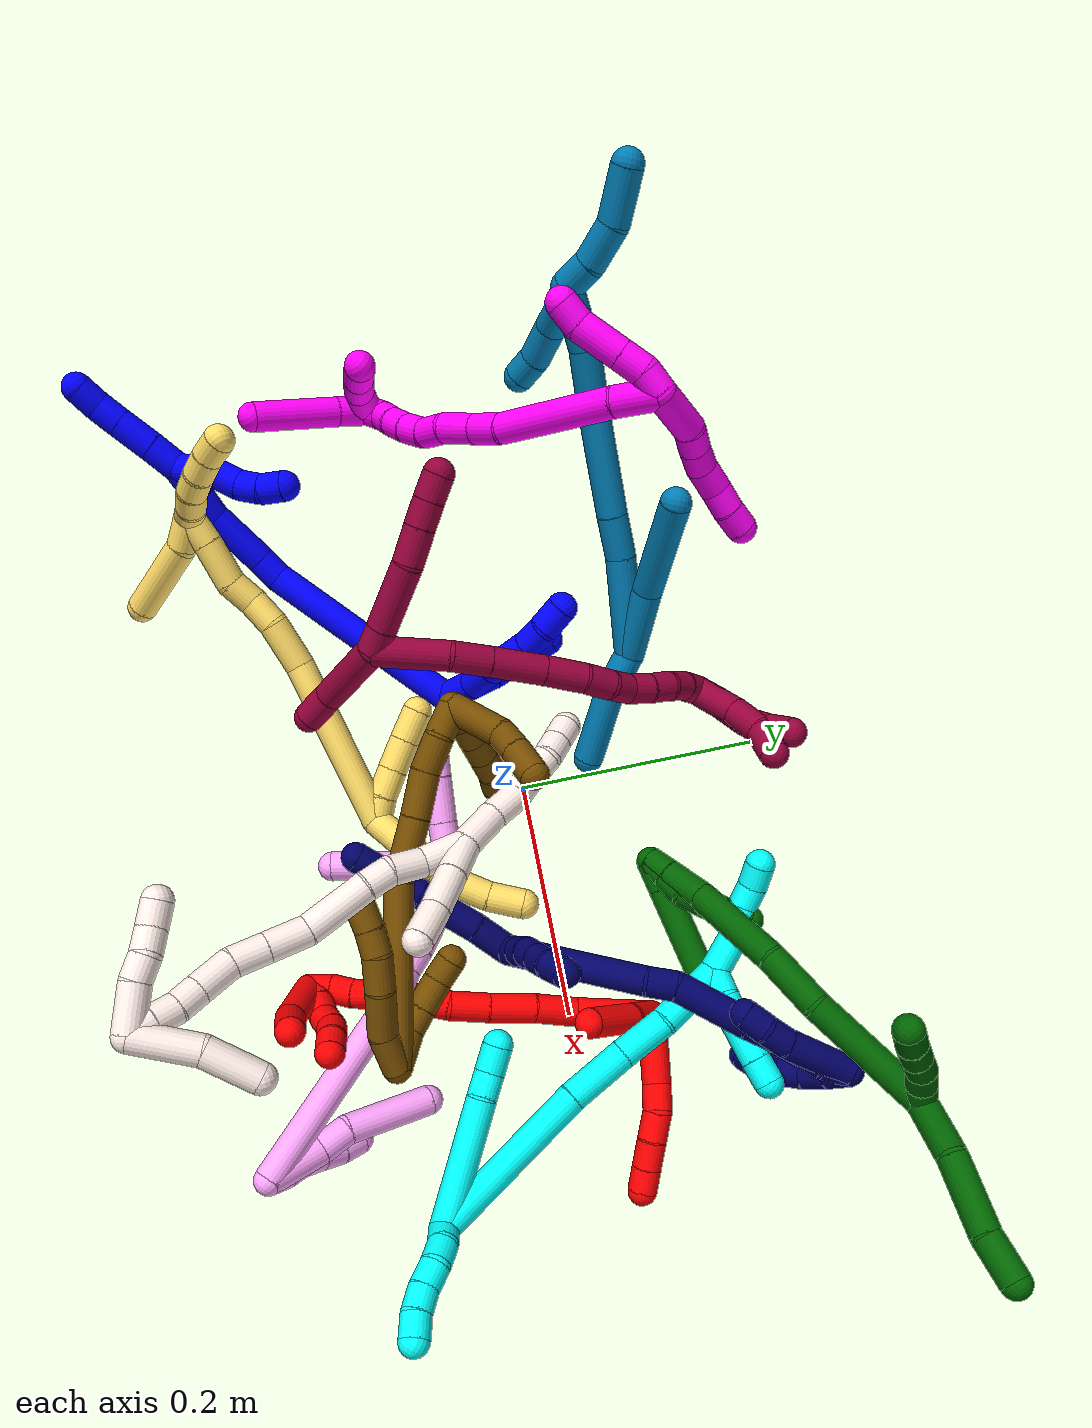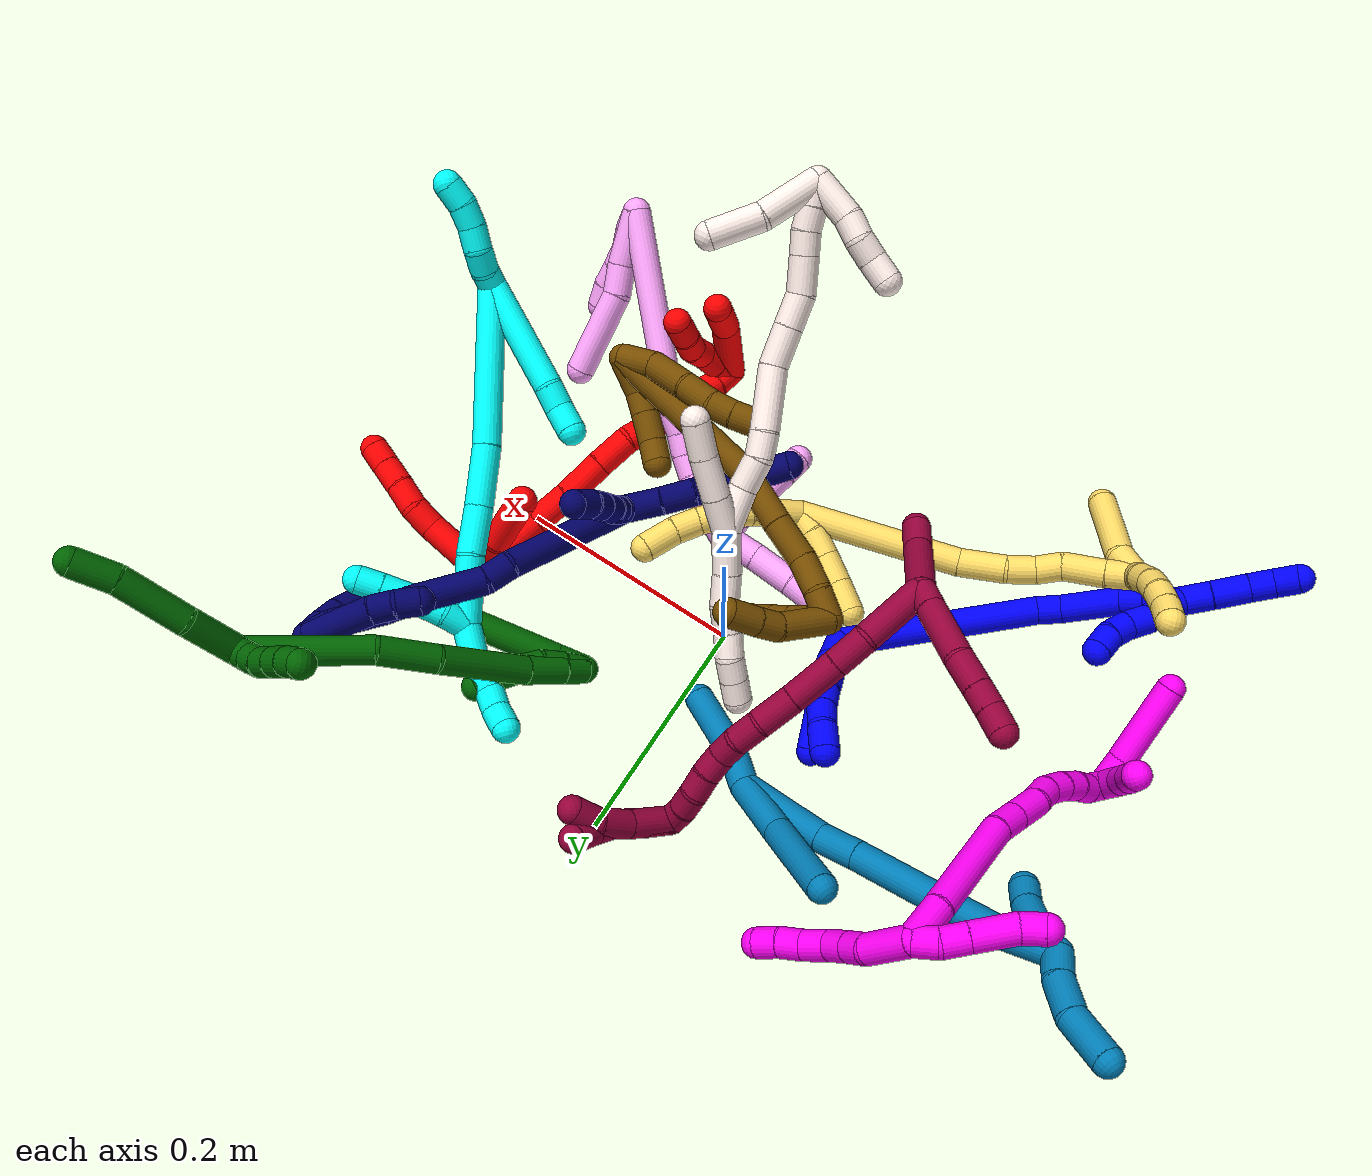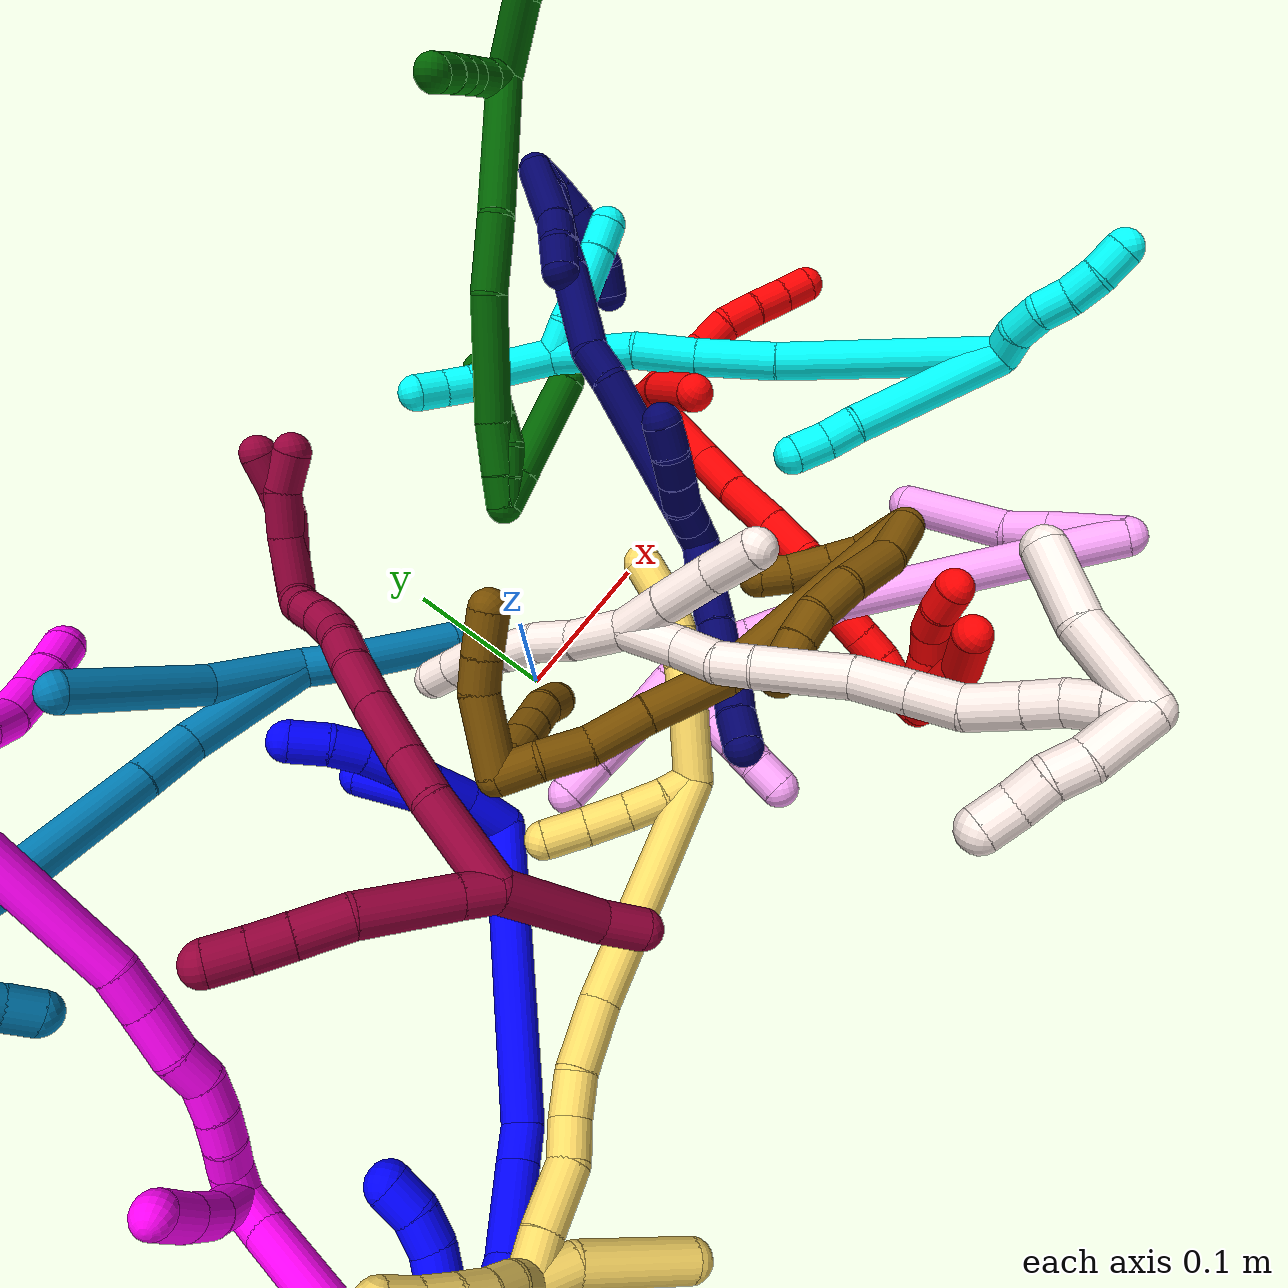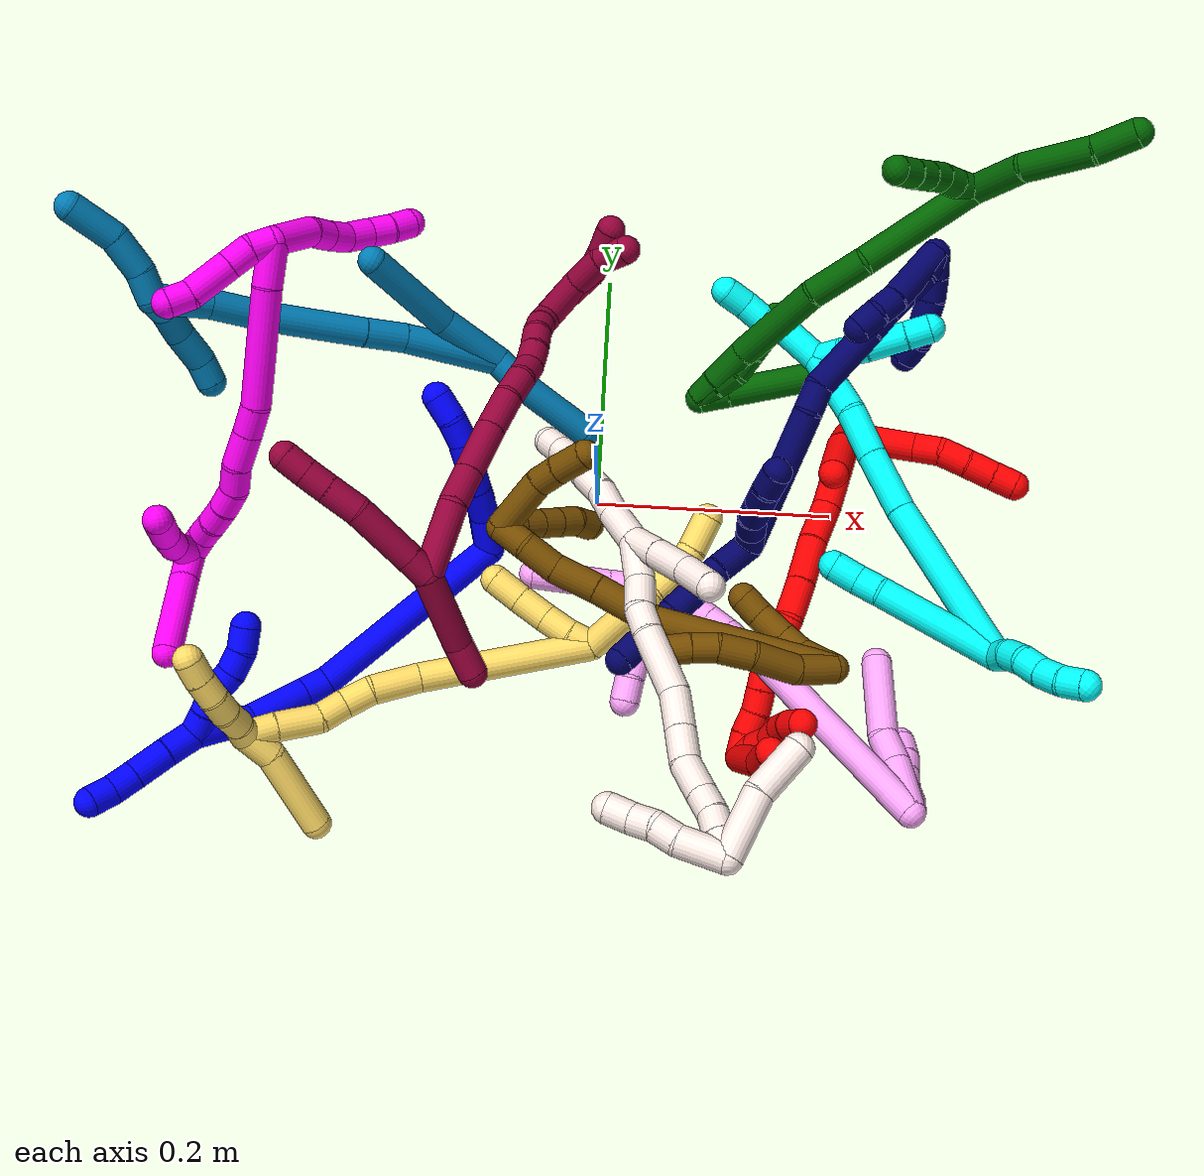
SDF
<sdf version="1.7">
 <world name="default">
  <plugin name="TubeGeneratorPlugin" filename="libtube_generator_plugin.so"/>
  <model name="photoneo_s_sensor">
   <static>1</static>
   <pose>0 0 2 1.57079 1.57079 3.14159</pose>
   <link name="link">
    <inertial><mass>0.1</mass></inertial>
    <sensor name="sensor" type="depth">
     <update_rate>30</update_rate>
     <camera>
      <horizontal_fov>1.22</horizontal_fov>
      <image><width>1920</width><height>1200</height><format>B8G8R8</format></image>
      <clip><near>0.1</near><far>4</far></clip>
      <depth_camera><output>points</output></depth_camera>
     </camera>
     <plugin name="camera_plugin" filename="libgazebo_ros_depth_camera.so">
      <baseline>0.2</baseline>
      <alwaysOn>1</alwaysOn>
      <updateRate>0.0</updateRate>
      <cameraName>camera_ir</cameraName>
      <imageTopicName>/camera/color/image_raw</imageTopicName>
      <cameraInfoTopicName>/camera/color/camera_info</cameraInfoTopicName>
      <depthImageTopicName>/camera/depth/image_raw</depthImageTopicName>
      <depthImageCameraInfoTopicName>/camera/depth/camera_info</depthImageCameraInfoTopicName>
      <pointCloudTopicName>/camera/depth/points</pointCloudTopicName>
      <frameName>fr_optical</frameName>
      <pointCloudCutoff>0.1</pointCloudCutoff>
      <pointCloudCutoffMax>2.0</pointCloudCutoffMax>
      <distortionK1>0</distortionK1>
      <distortionK2>0</distortionK2>
      <distortionK3>0</distortionK3>
      <distortionT1>0</distortionT1>
      <distortionT2>0</distortionT2>
      <CxPrime>0</CxPrime>
      <Cx>0</Cx>
      <Cy>0</Cy>
      <focalLength>0</focalLength>
      <hackBaseline>0</hackBaseline>
     </plugin>
    </sensor>
   </link>
  </model>
  <gravity>0 0 -9.8</gravity>
  <magnetic_field>6e-06 2.3e-05 -4.2e-05</magnetic_field>
  <atmosphere type="adiabatic"/>
  <physics name="default_physics" default="0" type="ode">
   <max_step_size>0.003</max_step_size>
   <real_time_factor>1</real_time_factor>
   <real_time_update_rate>1000</real_time_update_rate>
   <max_contacts>10000</max_contacts>
   <ode>
    <solver>
     <type>quick</type>
     <iters>100</iters>
     <sor>1.3</sor>
     <use_dynamic_moi_rescaling>0</use_dynamic_moi_rescaling>
    </solver>
    <constraints>
     <contact_max_correcting_vel>0</contact_max_correcting_vel>
     <contact_surface_layer>0.001</contact_surface_layer>
     <cfm>0</cfm>
     <erp>0.2</erp>
    </constraints>
   </ode>
  </physics>
  <scene><ambient>0.4 0.4 0.4 1</ambient><background>0.7 0.7 0.7 1</background><shadows>0</shadows></scene>
  <audio><device>default</device></audio>
  <spherical_coordinates>
   <surface_model>EARTH_WGS84</surface_model>
   <latitude_deg>0</latitude_deg>
   <longitude_deg>0</longitude_deg>
   <elevation>0</elevation>
   <heading_deg>0</heading_deg>
  </spherical_coordinates>
  <model name="bin">
   <static>1</static>
   <link name="bottom">
    <collision name="collision-bottom">
     <pose>0 0 -0.01 0 -0 0</pose>
     <geometry><box><size>0.8 0.6 0.02</size></box></geometry>
     <surface>
      <friction><ode><mu>100</mu><mu2>100</mu2></ode></friction>
      <contact><collide_bitmask>65535</collide_bitmask></contact>
     </surface>
    </collision>
   </link>
   <link name="west_wall">
    <collision name="collision-west_wall">
     <pose>-0.41 0 0.1 0 -0 0</pose>
     <geometry><box><size>0.02 0.6 0.2</size></box></geometry>
     <surface>
      <friction><ode><mu>100</mu><mu2>100</mu2></ode></friction>
      <contact><collide_bitmask>65535</collide_bitmask></contact>
     </surface>
    </collision>
   </link>
   <link name="east_wall">
    <collision name="collision-east_wall">
     <pose>0.41 0 0.1 0 -0 0</pose>
     <geometry><box><size>0.02 0.6 0.2</size></box></geometry>
     <surface>
      <friction><ode><mu>100</mu><mu2>100</mu2></ode></friction>
      <contact><collide_bitmask>65535</collide_bitmask></contact>
     </surface>
    </collision>
   </link>
   <link name="south_wall">
    <collision name="collision-south_wall">
     <pose>0 -0.31 0.1 0 -0 0</pose>
     <geometry><box><size>0.8 0.02 0.2</size></box></geometry>
     <surface>
      <friction><ode><mu>100</mu><mu2>100</mu2></ode></friction>
      <contact><collide_bitmask>65535</collide_bitmask></contact>
     </surface>
    </collision>
   </link>
   <link name="north_wall">
    <collision name="collision-north_wall">
     <pose>0 0.31 0.1 0 -0 0</pose>
     <geometry><box><size>0.8 0.02 0.2</size></box></geometry>
     <surface>
      <friction><ode><mu>100</mu><mu2>100</mu2></ode></friction>
      <contact><collide_bitmask>65535</collide_bitmask></contact>
     </surface>
    </collision>
   </link>
  </model>
  <model name="1">
   <static>0</static>
   <link name="1">
    <collision name="collision-cylinder-e_1_2_8">
     <pose>0.01566 0.005448 0.000631 -1.45556 1.23395 -1.12721</pose>
     <geometry><cylinder><radius>0.0125</radius><length>0.033184</length></cylinder></geometry>
     <surface>
      <friction><ode><mu>1.16</mu><mu2>1.16</mu2><slip1>0</slip1><slip2>0</slip2></ode></friction>
      <contact><ode><kp>1e+06</kp><kd>1</kd><max_vel>0</max_vel><min_depth>0.001</min_depth></ode></contact>
     </surface>
    </collision>
    <visual name="visual-cylinder-e_1_2_8">
     <pose>0.01566 0.005448 0.000631 -1.45556 1.23395 -1.12721</pose>
     <geometry><cylinder><radius>0.0125</radius><length>0.033184</length></cylinder></geometry>
     <material><ambient>0 0 1 1</ambient></material>
    </visual>
    <collision name="collision-cylinder-e_2_8_9">
     <pose>0.044769 0.014759 0.004468 -0.87799 1.21347 -0.630097</pose>
     <geometry><cylinder><radius>0.0125</radius><length>0.028714</length></cylinder></geometry>
     <surface>
      <friction><ode><mu>1.16</mu><mu2>1.16</mu2><slip1>0</slip1><slip2>0</slip2></ode></friction>
      <contact><ode><kp>1e+06</kp><kd>1</kd><max_vel>0</max_vel><min_depth>0.001</min_depth></ode></contact>
     </surface>
    </collision>
    <visual name="visual-cylinder-e_2_8_9">
     <pose>0.044769 0.014759 0.004468 -0.87799 1.21347 -0.630097</pose>
     <geometry><cylinder><radius>0.0125</radius><length>0.028714</length></cylinder></geometry>
     <material><ambient>0 0 1 1</ambient></material>
    </visual>
    <collision name="collision-cylinder-e_3_9_10">
     <pose>0.069644 0.022293 0.009204 -1.17613 1.23596 -0.885215</pose>
     <geometry><cylinder><radius>0.0125</radius><length>0.024193</length></cylinder></geometry>
     <surface>
      <friction><ode><mu>1.16</mu><mu2>1.16</mu2><slip1>0</slip1><slip2>0</slip2></ode></friction>
      <contact><ode><kp>1e+06</kp><kd>1</kd><max_vel>0</max_vel><min_depth>0.001</min_depth></ode></contact>
     </surface>
    </collision>
    <visual name="visual-cylinder-e_3_9_10">
     <pose>0.069644 0.022293 0.009204 -1.17613 1.23596 -0.885215</pose>
     <geometry><cylinder><radius>0.0125</radius><length>0.024193</length></cylinder></geometry>
     <material><ambient>0 0 1 1</ambient></material>
    </visual>
    <collision name="collision-cylinder-e_4_10_11">
     <pose>0.08963 0.031082 0.011902 -1.34627 1.02053 -0.83954</pose>
     <geometry><cylinder><radius>0.0125</radius><length>0.020088</length></cylinder></geometry>
     <surface>
      <friction><ode><mu>1.16</mu><mu2>1.16</mu2><slip1>0</slip1><slip2>0</slip2></ode></friction>
      <contact><ode><kp>1e+06</kp><kd>1</kd><max_vel>0</max_vel><min_depth>0.001</min_depth></ode></contact>
     </surface>
    </collision>
    <visual name="visual-cylinder-e_4_10_11">
     <pose>0.08963 0.031082 0.011902 -1.34627 1.02053 -0.83954</pose>
     <geometry><cylinder><radius>0.0125</radius><length>0.020088</length></cylinder></geometry>
     <material><ambient>0 0 1 1</ambient></material>
    </visual>
    <collision name="collision-cylinder-e_5_11_12">
     <pose>0.106583 0.042016 0.015751 -1.13884 0.919137 -0.613629</pose>
     <geometry><cylinder><radius>0.0125</radius><length>0.021107</length></cylinder></geometry>
     <surface>
      <friction><ode><mu>1.16</mu><mu2>1.16</mu2><slip1>0</slip1><slip2>0</slip2></ode></friction>
      <contact><ode><kp>1e+06</kp><kd>1</kd><max_vel>0</max_vel><min_depth>0.001</min_depth></ode></contact>
     </surface>
    </collision>
    <visual name="visual-cylinder-e_5_11_12">
     <pose>0.106583 0.042016 0.015751 -1.13884 0.919137 -0.613629</pose>
     <geometry><cylinder><radius>0.0125</radius><length>0.021107</length></cylinder></geometry>
     <material><ambient>0 0 1 1</ambient></material>
    </visual>
    <collision name="collision-cylinder-e_6_12_6">
     <pose>0.122017 0.056175 0.021544 -1.21373 0.669029 -0.473564</pose>
     <geometry><cylinder><radius>0.0125</radius><length>0.022713</length></cylinder></geometry>
     <surface>
      <friction><ode><mu>1.16</mu><mu2>1.16</mu2><slip1>0</slip1><slip2>0</slip2></ode></friction>
      <contact><ode><kp>1e+06</kp><kd>1</kd><max_vel>0</max_vel><min_depth>0.001</min_depth></ode></contact>
     </surface>
    </collision>
    <visual name="visual-cylinder-e_6_12_6">
     <pose>0.122017 0.056175 0.021544 -1.21373 0.669029 -0.473564</pose>
     <geometry><cylinder><radius>0.0125</radius><length>0.022713</length></cylinder></geometry>
     <material><ambient>0 0 1 1</ambient></material>
    </visual>
    <collision name="collision-cylinder-e_1_2_13">
     <pose>0.011017 0.019135 -0.004279 -1.79081 0.511909 -0.631504</pose>
     <geometry><cylinder><radius>0.0125</radius><length>0.044982</length></cylinder></geometry>
     <surface>
      <friction><ode><mu>1.16</mu><mu2>1.16</mu2><slip1>0</slip1><slip2>0</slip2></ode></friction>
      <contact><ode><kp>1e+06</kp><kd>1</kd><max_vel>0</max_vel><min_depth>0.001</min_depth></ode></contact>
     </surface>
    </collision>
    <visual name="visual-cylinder-e_1_2_13">
     <pose>0.011017 0.019135 -0.004279 -1.79081 0.511909 -0.631504</pose>
     <geometry><cylinder><radius>0.0125</radius><length>0.044982</length></cylinder></geometry>
     <material><ambient>0 0 1 1</ambient></material>
    </visual>
    <collision name="collision-cylinder-e_2_13_5">
     <pose>0.0344 0.062728 -0.010936 -1.66771 0.466221 -0.511787</pose>
     <geometry><cylinder><radius>0.0125</radius><length>0.055018</length></cylinder></geometry>
     <surface>
      <friction><ode><mu>1.16</mu><mu2>1.16</mu2><slip1>0</slip1><slip2>0</slip2></ode></friction>
      <contact><ode><kp>1e+06</kp><kd>1</kd><max_vel>0</max_vel><min_depth>0.001</min_depth></ode></contact>
     </surface>
    </collision>
    <visual name="visual-cylinder-e_2_13_5">
     <pose>0.0344 0.062728 -0.010936 -1.66771 0.466221 -0.511787</pose>
     <geometry><cylinder><radius>0.0125</radius><length>0.055018</length></cylinder></geometry>
     <material><ambient>0 0 1 1</ambient></material>
    </visual>
    <collision name="collision-cylinder-e_1_2_14">
     <pose>-0.037503 -0.010508 0.078975 0.132285 -0.439953 -0.029619</pose>
     <geometry><cylinder><radius>0.0125</radius><length>0.176112</length></cylinder></geometry>
     <surface>
      <friction><ode><mu>1.16</mu><mu2>1.16</mu2><slip1>0</slip1><slip2>0</slip2></ode></friction>
      <contact><ode><kp>1e+06</kp><kd>1</kd><max_vel>0</max_vel><min_depth>0.001</min_depth></ode></contact>
     </surface>
    </collision>
    <visual name="visual-cylinder-e_1_2_14">
     <pose>-0.037503 -0.010508 0.078975 0.132285 -0.439953 -0.029619</pose>
     <geometry><cylinder><radius>0.0125</radius><length>0.176112</length></cylinder></geometry>
     <material><ambient>0 0 1 1</ambient></material>
    </visual>
    <collision name="collision-cylinder-e_2_14_15">
     <pose>-0.07657 -0.021828 0.168734 0.075059 -0.143657 -0.005403</pose>
     <geometry><cylinder><radius>0.0125</radius><length>0.021855</length></cylinder></geometry>
     <surface>
      <friction><ode><mu>1.16</mu><mu2>1.16</mu2><slip1>0</slip1><slip2>0</slip2></ode></friction>
      <contact><ode><kp>1e+06</kp><kd>1</kd><max_vel>0</max_vel><min_depth>0.001</min_depth></ode></contact>
     </surface>
    </collision>
    <visual name="visual-cylinder-e_2_14_15">
     <pose>-0.07657 -0.021828 0.168734 0.075059 -0.143657 -0.005403</pose>
     <geometry><cylinder><radius>0.0125</radius><length>0.021855</length></cylinder></geometry>
     <material><ambient>0 0 1 1</ambient></material>
    </visual>
    <collision name="collision-cylinder-e_3_15_16">
     <pose>-0.078719 -0.027018 0.205209 0.168813 -0.022407 -0.001896</pose>
     <geometry><cylinder><radius>0.0125</radius><length>0.052136</length></cylinder></geometry>
     <surface>
      <friction><ode><mu>1.16</mu><mu2>1.16</mu2><slip1>0</slip1><slip2>0</slip2></ode></friction>
      <contact><ode><kp>1e+06</kp><kd>1</kd><max_vel>0</max_vel><min_depth>0.001</min_depth></ode></contact>
     </surface>
    </collision>
    <visual name="visual-cylinder-e_3_15_16">
     <pose>-0.078719 -0.027018 0.205209 0.168813 -0.022407 -0.001896</pose>
     <geometry><cylinder><radius>0.0125</radius><length>0.052136</length></cylinder></geometry>
     <material><ambient>0 0 1 1</ambient></material>
    </visual>
    <collision name="collision-cylinder-e_4_16_17">
     <pose>-0.076701 -0.032138 0.241404 0.070519 0.242203 0.008585</pose>
     <geometry><cylinder><radius>0.0125</radius><length>0.021692</length></cylinder></geometry>
     <surface>
      <friction><ode><mu>1.16</mu><mu2>1.16</mu2><slip1>0</slip1><slip2>0</slip2></ode></friction>
      <contact><ode><kp>1e+06</kp><kd>1</kd><max_vel>0</max_vel><min_depth>0.001</min_depth></ode></contact>
     </surface>
    </collision>
    <visual name="visual-cylinder-e_4_16_17">
     <pose>-0.076701 -0.032138 0.241404 0.070519 0.242203 0.008585</pose>
     <geometry><cylinder><radius>0.0125</radius><length>0.021692</length></cylinder></geometry>
     <material><ambient>0 0 1 1</ambient></material>
    </visual>
    <collision name="collision-cylinder-e_5_17_1">
     <pose>-0.072393 -0.033382 0.265897 0.035827 0.121309 0.002176</pose>
     <geometry><cylinder><radius>0.0125</radius><length>0.028204</length></cylinder></geometry>
     <surface>
      <friction><ode><mu>1.16</mu><mu2>1.16</mu2><slip1>0</slip1><slip2>0</slip2></ode></friction>
      <contact><ode><kp>1e+06</kp><kd>1</kd><max_vel>0</max_vel><min_depth>0.001</min_depth></ode></contact>
     </surface>
    </collision>
    <visual name="visual-cylinder-e_5_17_1">
     <pose>-0.072393 -0.033382 0.265897 0.035827 0.121309 0.002176</pose>
     <geometry><cylinder><radius>0.0125</radius><length>0.028204</length></cylinder></geometry>
     <material><ambient>0 0 1 1</ambient></material>
    </visual>
    <collision name="collision-cylinder-e_1_1_18">
     <pose>-0.062673 -0.031708 0.274314 -2.76949 0.92962 -2.4234</pose>
     <geometry><cylinder><radius>0.0125</radius><length>0.02</length></cylinder></geometry>
     <surface>
      <friction><ode><mu>1.16</mu><mu2>1.16</mu2><slip1>0</slip1><slip2>0</slip2></ode></friction>
      <contact><ode><kp>1e+06</kp><kd>1</kd><max_vel>0</max_vel><min_depth>0.001</min_depth></ode></contact>
     </surface>
    </collision>
    <visual name="visual-cylinder-e_1_1_18">
     <pose>-0.062673 -0.031708 0.274314 -2.76949 0.92962 -2.4234</pose>
     <geometry><cylinder><radius>0.0125</radius><length>0.02</length></cylinder></geometry>
     <material><ambient>0 0 1 1</ambient></material>
    </visual>
    <collision name="collision-cylinder-e_2_18_19">
     <pose>-0.046972 -0.026455 0.263136 -2.6394 0.876846 -2.14037</pose>
     <geometry><cylinder><radius>0.0125</radius><length>0.02</length></cylinder></geometry>
     <surface>
      <friction><ode><mu>1.16</mu><mu2>1.16</mu2><slip1>0</slip1><slip2>0</slip2></ode></friction>
      <contact><ode><kp>1e+06</kp><kd>1</kd><max_vel>0</max_vel><min_depth>0.001</min_depth></ode></contact>
     </surface>
    </collision>
    <visual name="visual-cylinder-e_2_18_19">
     <pose>-0.046972 -0.026455 0.263136 -2.6394 0.876846 -2.14037</pose>
     <geometry><cylinder><radius>0.0125</radius><length>0.02</length></cylinder></geometry>
     <material><ambient>0 0 1 1</ambient></material>
    </visual>
    <collision name="collision-cylinder-e_3_19_20">
     <pose>-0.033712 -0.02123 0.249509 -2.88008 0.5911 -2.32614</pose>
     <geometry><cylinder><radius>0.0125</radius><length>0.02</length></cylinder></geometry>
     <surface>
      <friction><ode><mu>1.16</mu><mu2>1.16</mu2><slip1>0</slip1><slip2>0</slip2></ode></friction>
      <contact><ode><kp>1e+06</kp><kd>1</kd><max_vel>0</max_vel><min_depth>0.001</min_depth></ode></contact>
     </surface>
    </collision>
    <visual name="visual-cylinder-e_3_19_20">
     <pose>-0.033712 -0.02123 0.249509 -2.88008 0.5911 -2.32614</pose>
     <geometry><cylinder><radius>0.0125</radius><length>0.02</length></cylinder></geometry>
     <material><ambient>0 0 1 1</ambient></material>
    </visual>
    <collision name="collision-cylinder-e_4_20_21">
     <pose>-0.020693 -0.016039 0.235548 -2.66803 0.839969 -2.15074</pose>
     <geometry><cylinder><radius>0.0125</radius><length>0.02</length></cylinder></geometry>
     <surface>
      <friction><ode><mu>1.16</mu><mu2>1.16</mu2><slip1>0</slip1><slip2>0</slip2></ode></friction>
      <contact><ode><kp>1e+06</kp><kd>1</kd><max_vel>0</max_vel><min_depth>0.001</min_depth></ode></contact>
     </surface>
    </collision>
    <visual name="visual-cylinder-e_4_20_21">
     <pose>-0.020693 -0.016039 0.235548 -2.66803 0.839969 -2.15074</pose>
     <geometry><cylinder><radius>0.0125</radius><length>0.02</length></cylinder></geometry>
     <material><ambient>0 0 1 1</ambient></material>
    </visual>
    <collision name="collision-cylinder-e_5_21_4">
     <pose>-0.005745 -0.007703 0.225642 -2.21391 0.84825 -1.46852</pose>
     <geometry><cylinder><radius>0.0125</radius><length>0.02</length></cylinder></geometry>
     <surface>
      <friction><ode><mu>1.16</mu><mu2>1.16</mu2><slip1>0</slip1><slip2>0</slip2></ode></friction>
      <contact><ode><kp>1e+06</kp><kd>1</kd><max_vel>0</max_vel><min_depth>0.001</min_depth></ode></contact>
     </surface>
    </collision>
    <visual name="visual-cylinder-e_5_21_4">
     <pose>-0.005745 -0.007703 0.225642 -2.21391 0.84825 -1.46852</pose>
     <geometry><cylinder><radius>0.0125</radius><length>0.02</length></cylinder></geometry>
     <material><ambient>0 0 1 1</ambient></material>
    </visual>
    <collision name="collision-cylinder-e_1_1_22">
     <pose>-0.072845 -0.036547 0.292947 0.201232 -0.160481 -0.016236</pose>
     <geometry><cylinder><radius>0.0125</radius><length>0.027006</length></cylinder></geometry>
     <surface>
      <friction><ode><mu>1.16</mu><mu2>1.16</mu2><slip1>0</slip1><slip2>0</slip2></ode></friction>
      <contact><ode><kp>1e+06</kp><kd>1</kd><max_vel>0</max_vel><min_depth>0.001</min_depth></ode></contact>
     </surface>
    </collision>
    <visual name="visual-cylinder-e_1_1_22">
     <pose>-0.072845 -0.036547 0.292947 0.201232 -0.160481 -0.016236</pose>
     <geometry><cylinder><radius>0.0125</radius><length>0.027006</length></cylinder></geometry>
     <material><ambient>0 0 1 1</ambient></material>
    </visual>
    <collision name="collision-cylinder-e_2_22_23">
     <pose>-0.078433 -0.042276 0.320712 0.205472 -0.224524 -0.023245</pose>
     <geometry><cylinder><radius>0.0125</radius><length>0.030815</length></cylinder></geometry>
     <surface>
      <friction><ode><mu>1.16</mu><mu2>1.16</mu2><slip1>0</slip1><slip2>0</slip2></ode></friction>
      <contact><ode><kp>1e+06</kp><kd>1</kd><max_vel>0</max_vel><min_depth>0.001</min_depth></ode></contact>
     </surface>
    </collision>
    <visual name="visual-cylinder-e_2_22_23">
     <pose>-0.078433 -0.042276 0.320712 0.205472 -0.224524 -0.023245</pose>
     <geometry><cylinder><radius>0.0125</radius><length>0.030815</length></cylinder></geometry>
     <material><ambient>0 0 1 1</ambient></material>
    </visual>
    <collision name="collision-cylinder-e_3_23_24">
     <pose>-0.084134 -0.047361 0.345729 0.193483 -0.212834 -0.020732</pose>
     <geometry><cylinder><radius>0.0125</radius><length>0.021502</length></cylinder></geometry>
     <surface>
      <friction><ode><mu>1.16</mu><mu2>1.16</mu2><slip1>0</slip1><slip2>0</slip2></ode></friction>
      <contact><ode><kp>1e+06</kp><kd>1</kd><max_vel>0</max_vel><min_depth>0.001</min_depth></ode></contact>
     </surface>
    </collision>
    <visual name="visual-cylinder-e_3_23_24">
     <pose>-0.084134 -0.047361 0.345729 0.193483 -0.212834 -0.020732</pose>
     <geometry><cylinder><radius>0.0125</radius><length>0.021502</length></cylinder></geometry>
     <material><ambient>0 0 1 1</ambient></material>
    </visual>
    <collision name="collision-cylinder-e_4_24_3">
     <pose>-0.086065 -0.051605 0.366132 0.216832 0.032865 0.003577</pose>
     <geometry><cylinder><radius>0.0125</radius><length>0.020677</length></cylinder></geometry>
     <surface>
      <friction><ode><mu>1.16</mu><mu2>1.16</mu2><slip1>0</slip1><slip2>0</slip2></ode></friction>
      <contact><ode><kp>1e+06</kp><kd>1</kd><max_vel>0</max_vel><min_depth>0.001</min_depth></ode></contact>
     </surface>
    </collision>
    <visual name="visual-cylinder-e_4_24_3">
     <pose>-0.086065 -0.051605 0.366132 0.216832 0.032865 0.003577</pose>
     <geometry><cylinder><radius>0.0125</radius><length>0.020677</length></cylinder></geometry>
     <material><ambient>0 0 1 1</ambient></material>
    </visual>
    <collision name="collision-sphere-3">
     <pose>-0.085725 -0.053828 0.376223 0 -0 0</pose>
     <geometry><sphere><radius>0.0125</radius></sphere></geometry>
     <surface>
      <friction><ode><mu>1.16</mu><mu2>1.16</mu2><slip1>0</slip1><slip2>0</slip2></ode></friction>
      <contact><ode><kp>1e+06</kp><kd>1</kd><max_vel>0</max_vel><min_depth>0.001</min_depth></ode></contact>
     </surface>
    </collision>
    <visual name="visual-sphere-3">
     <pose>-0.085725 -0.053828 0.376223 0 -0 0</pose>
     <geometry><sphere><radius>0.0125</radius></sphere></geometry>
     <material><ambient>0 0 1 1</ambient></material>
    </visual>
    <collision name="collision-sphere-24">
     <pose>-0.086405 -0.049382 0.356041 0 -0 0</pose>
     <geometry><sphere><radius>0.0125</radius></sphere></geometry>
     <surface>
      <friction><ode><mu>1.16</mu><mu2>1.16</mu2><slip1>0</slip1><slip2>0</slip2></ode></friction>
      <contact><ode><kp>1e+06</kp><kd>1</kd><max_vel>0</max_vel><min_depth>0.001</min_depth></ode></contact>
     </surface>
    </collision>
    <visual name="visual-sphere-24">
     <pose>-0.086405 -0.049382 0.356041 0 -0 0</pose>
     <geometry><sphere><radius>0.0125</radius></sphere></geometry>
     <material><ambient>0 0 1 1</ambient></material>
    </visual>
    <collision name="collision-sphere-23">
     <pose>-0.081863 -0.045341 0.335417 0 -0 0</pose>
     <geometry><sphere><radius>0.0125</radius></sphere></geometry>
     <surface>
      <friction><ode><mu>1.16</mu><mu2>1.16</mu2><slip1>0</slip1><slip2>0</slip2></ode></friction>
      <contact><ode><kp>1e+06</kp><kd>1</kd><max_vel>0</max_vel><min_depth>0.001</min_depth></ode></contact>
     </surface>
    </collision>
    <visual name="visual-sphere-23">
     <pose>-0.081863 -0.045341 0.335417 0 -0 0</pose>
     <geometry><sphere><radius>0.0125</radius></sphere></geometry>
     <material><ambient>0 0 1 1</ambient></material>
    </visual>
    <collision name="collision-sphere-22">
     <pose>-0.075002 -0.039212 0.306008 0 -0 0</pose>
     <geometry><sphere><radius>0.0125</radius></sphere></geometry>
     <surface>
      <friction><ode><mu>1.16</mu><mu2>1.16</mu2><slip1>0</slip1><slip2>0</slip2></ode></friction>
      <contact><ode><kp>1e+06</kp><kd>1</kd><max_vel>0</max_vel><min_depth>0.001</min_depth></ode></contact>
     </surface>
    </collision>
    <visual name="visual-sphere-22">
     <pose>-0.075002 -0.039212 0.306008 0 -0 0</pose>
     <geometry><sphere><radius>0.0125</radius></sphere></geometry>
     <material><ambient>0 0 1 1</ambient></material>
    </visual>
    <collision name="collision-sphere-4">
     <pose>0.001756 -0.002411 0.221676 0 -0 0</pose>
     <geometry><sphere><radius>0.0125</radius></sphere></geometry>
     <surface>
      <friction><ode><mu>1.16</mu><mu2>1.16</mu2><slip1>0</slip1><slip2>0</slip2></ode></friction>
      <contact><ode><kp>1e+06</kp><kd>1</kd><max_vel>0</max_vel><min_depth>0.001</min_depth></ode></contact>
     </surface>
    </collision>
    <visual name="visual-sphere-4">
     <pose>0.001756 -0.002411 0.221676 0 -0 0</pose>
     <geometry><sphere><radius>0.0125</radius></sphere></geometry>
     <material><ambient>0 0 1 1</ambient></material>
    </visual>
    <collision name="collision-sphere-21">
     <pose>-0.013247 -0.012995 0.229607 0 -0 0</pose>
     <geometry><sphere><radius>0.0125</radius></sphere></geometry>
     <surface>
      <friction><ode><mu>1.16</mu><mu2>1.16</mu2><slip1>0</slip1><slip2>0</slip2></ode></friction>
      <contact><ode><kp>1e+06</kp><kd>1</kd><max_vel>0</max_vel><min_depth>0.001</min_depth></ode></contact>
     </surface>
    </collision>
    <visual name="visual-sphere-21">
     <pose>-0.013247 -0.012995 0.229607 0 -0 0</pose>
     <geometry><sphere><radius>0.0125</radius></sphere></geometry>
     <material><ambient>0 0 1 1</ambient></material>
    </visual>
    <collision name="collision-sphere-20">
     <pose>-0.028139 -0.019083 0.241488 0 -0 0</pose>
     <geometry><sphere><radius>0.0125</radius></sphere></geometry>
     <surface>
      <friction><ode><mu>1.16</mu><mu2>1.16</mu2><slip1>0</slip1><slip2>0</slip2></ode></friction>
      <contact><ode><kp>1e+06</kp><kd>1</kd><max_vel>0</max_vel><min_depth>0.001</min_depth></ode></contact>
     </surface>
    </collision>
    <visual name="visual-sphere-20">
     <pose>-0.028139 -0.019083 0.241488 0 -0 0</pose>
     <geometry><sphere><radius>0.0125</radius></sphere></geometry>
     <material><ambient>0 0 1 1</ambient></material>
    </visual>
    <collision name="collision-sphere-12">
     <pose>0.114974 0.047829 0.018431 0 -0 0</pose>
     <geometry><sphere><radius>0.0125</radius></sphere></geometry>
     <surface>
      <friction><ode><mu>1.16</mu><mu2>1.16</mu2><slip1>0</slip1><slip2>0</slip2></ode></friction>
      <contact><ode><kp>1e+06</kp><kd>1</kd><max_vel>0</max_vel><min_depth>0.001</min_depth></ode></contact>
     </surface>
    </collision>
    <visual name="visual-sphere-12">
     <pose>0.114974 0.047829 0.018431 0 -0 0</pose>
     <geometry><sphere><radius>0.0125</radius></sphere></geometry>
     <material><ambient>0 0 1 1</ambient></material>
    </visual>
    <collision name="collision-sphere-11">
     <pose>0.098192 0.036203 0.013071 0 -0 0</pose>
     <geometry><sphere><radius>0.0125</radius></sphere></geometry>
     <surface>
      <friction><ode><mu>1.16</mu><mu2>1.16</mu2><slip1>0</slip1><slip2>0</slip2></ode></friction>
      <contact><ode><kp>1e+06</kp><kd>1</kd><max_vel>0</max_vel><min_depth>0.001</min_depth></ode></contact>
     </surface>
    </collision>
    <visual name="visual-sphere-11">
     <pose>0.098192 0.036203 0.013071 0 -0 0</pose>
     <geometry><sphere><radius>0.0125</radius></sphere></geometry>
     <material><ambient>0 0 1 1</ambient></material>
    </visual>
    <collision name="collision-sphere-10">
     <pose>0.081069 0.025962 0.010733 0 -0 0</pose>
     <geometry><sphere><radius>0.0125</radius></sphere></geometry>
     <surface>
      <friction><ode><mu>1.16</mu><mu2>1.16</mu2><slip1>0</slip1><slip2>0</slip2></ode></friction>
      <contact><ode><kp>1e+06</kp><kd>1</kd><max_vel>0</max_vel><min_depth>0.001</min_depth></ode></contact>
     </surface>
    </collision>
    <visual name="visual-sphere-10">
     <pose>0.081069 0.025962 0.010733 0 -0 0</pose>
     <geometry><sphere><radius>0.0125</radius></sphere></geometry>
     <material><ambient>0 0 1 1</ambient></material>
    </visual>
    <collision name="collision-sphere-9">
     <pose>0.058219 0.018623 0.007676 0 -0 0</pose>
     <geometry><sphere><radius>0.0125</radius></sphere></geometry>
     <surface>
      <friction><ode><mu>1.16</mu><mu2>1.16</mu2><slip1>0</slip1><slip2>0</slip2></ode></friction>
      <contact><ode><kp>1e+06</kp><kd>1</kd><max_vel>0</max_vel><min_depth>0.001</min_depth></ode></contact>
     </surface>
    </collision>
    <visual name="visual-sphere-9">
     <pose>0.058219 0.018623 0.007676 0 -0 0</pose>
     <geometry><sphere><radius>0.0125</radius></sphere></geometry>
     <material><ambient>0 0 1 1</ambient></material>
    </visual>
    <collision name="collision-sphere-2">
     <geometry><sphere><radius>0.0125</radius></sphere></geometry>
     <surface>
      <friction><ode><mu>1.16</mu><mu2>1.16</mu2><slip1>0</slip1><slip2>0</slip2></ode></friction>
      <contact><ode><kp>1e+06</kp><kd>1</kd><max_vel>0</max_vel><min_depth>0.001</min_depth></ode></contact>
     </surface>
    </collision>
    <visual name="visual-sphere-2">
     <geometry><sphere><radius>0.0125</radius></sphere></geometry>
     <material><ambient>0 0 1 1</ambient></material>
    </visual>
    <collision name="collision-sphere-19">
     <pose>-0.039284 -0.023376 0.25753 0 -0 0</pose>
     <geometry><sphere><radius>0.0125</radius></sphere></geometry>
     <surface>
      <friction><ode><mu>1.16</mu><mu2>1.16</mu2><slip1>0</slip1><slip2>0</slip2></ode></friction>
      <contact><ode><kp>1e+06</kp><kd>1</kd><max_vel>0</max_vel><min_depth>0.001</min_depth></ode></contact>
     </surface>
    </collision>
    <visual name="visual-sphere-19">
     <pose>-0.039284 -0.023376 0.25753 0 -0 0</pose>
     <geometry><sphere><radius>0.0125</radius></sphere></geometry>
     <material><ambient>0 0 1 1</ambient></material>
    </visual>
    <collision name="collision-sphere-8">
     <pose>0.031319 0.010895 0.001261 0 -0 0</pose>
     <geometry><sphere><radius>0.0125</radius></sphere></geometry>
     <surface>
      <friction><ode><mu>1.16</mu><mu2>1.16</mu2><slip1>0</slip1><slip2>0</slip2></ode></friction>
      <contact><ode><kp>1e+06</kp><kd>1</kd><max_vel>0</max_vel><min_depth>0.001</min_depth></ode></contact>
     </surface>
    </collision>
    <visual name="visual-sphere-8">
     <pose>0.031319 0.010895 0.001261 0 -0 0</pose>
     <geometry><sphere><radius>0.0125</radius></sphere></geometry>
     <material><ambient>0 0 1 1</ambient></material>
    </visual>
    <collision name="collision-sphere-6">
     <pose>0.129061 0.064522 0.024658 0 -0 0</pose>
     <geometry><sphere><radius>0.0125</radius></sphere></geometry>
     <surface>
      <friction><ode><mu>1.16</mu><mu2>1.16</mu2><slip1>0</slip1><slip2>0</slip2></ode></friction>
      <contact><ode><kp>1e+06</kp><kd>1</kd><max_vel>0</max_vel><min_depth>0.001</min_depth></ode></contact>
     </surface>
    </collision>
    <visual name="visual-sphere-6">
     <pose>0.129061 0.064522 0.024658 0 -0 0</pose>
     <geometry><sphere><radius>0.0125</radius></sphere></geometry>
     <material><ambient>0 0 1 1</ambient></material>
    </visual>
    <collision name="collision-sphere-13">
     <pose>0.022034 0.03827 -0.008558 0 -0 0</pose>
     <geometry><sphere><radius>0.0125</radius></sphere></geometry>
     <surface>
      <friction><ode><mu>1.16</mu><mu2>1.16</mu2><slip1>0</slip1><slip2>0</slip2></ode></friction>
      <contact><ode><kp>1e+06</kp><kd>1</kd><max_vel>0</max_vel><min_depth>0.001</min_depth></ode></contact>
     </surface>
    </collision>
    <visual name="visual-sphere-13">
     <pose>0.022034 0.03827 -0.008558 0 -0 0</pose>
     <geometry><sphere><radius>0.0125</radius></sphere></geometry>
     <material><ambient>0 0 1 1</ambient></material>
    </visual>
    <collision name="collision-sphere-5">
     <pose>0.046765 0.087186 -0.013314 0 -0 0</pose>
     <geometry><sphere><radius>0.0125</radius></sphere></geometry>
     <surface>
      <friction><ode><mu>1.16</mu><mu2>1.16</mu2><slip1>0</slip1><slip2>0</slip2></ode></friction>
      <contact><ode><kp>1e+06</kp><kd>1</kd><max_vel>0</max_vel><min_depth>0.001</min_depth></ode></contact>
     </surface>
    </collision>
    <visual name="visual-sphere-5">
     <pose>0.046765 0.087186 -0.013314 0 -0 0</pose>
     <geometry><sphere><radius>0.0125</radius></sphere></geometry>
     <material><ambient>0 0 1 1</ambient></material>
    </visual>
    <collision name="collision-sphere-14">
     <pose>-0.075006 -0.021017 0.157949 0 -0 0</pose>
     <geometry><sphere><radius>0.0125</radius></sphere></geometry>
     <surface>
      <friction><ode><mu>1.16</mu><mu2>1.16</mu2><slip1>0</slip1><slip2>0</slip2></ode></friction>
      <contact><ode><kp>1e+06</kp><kd>1</kd><max_vel>0</max_vel><min_depth>0.001</min_depth></ode></contact>
     </surface>
    </collision>
    <visual name="visual-sphere-14">
     <pose>-0.075006 -0.021017 0.157949 0 -0 0</pose>
     <geometry><sphere><radius>0.0125</radius></sphere></geometry>
     <material><ambient>0 0 1 1</ambient></material>
    </visual>
    <collision name="collision-sphere-15">
     <pose>-0.078134 -0.022639 0.179518 0 -0 0</pose>
     <geometry><sphere><radius>0.0125</radius></sphere></geometry>
     <surface>
      <friction><ode><mu>1.16</mu><mu2>1.16</mu2><slip1>0</slip1><slip2>0</slip2></ode></friction>
      <contact><ode><kp>1e+06</kp><kd>1</kd><max_vel>0</max_vel><min_depth>0.001</min_depth></ode></contact>
     </surface>
    </collision>
    <visual name="visual-sphere-15">
     <pose>-0.078134 -0.022639 0.179518 0 -0 0</pose>
     <geometry><sphere><radius>0.0125</radius></sphere></geometry>
     <material><ambient>0 0 1 1</ambient></material>
    </visual>
    <collision name="collision-sphere-16">
     <pose>-0.079303 -0.031396 0.230901 0 -0 0</pose>
     <geometry><sphere><radius>0.0125</radius></sphere></geometry>
     <surface>
      <friction><ode><mu>1.16</mu><mu2>1.16</mu2><slip1>0</slip1><slip2>0</slip2></ode></friction>
      <contact><ode><kp>1e+06</kp><kd>1</kd><max_vel>0</max_vel><min_depth>0.001</min_depth></ode></contact>
     </surface>
    </collision>
    <visual name="visual-sphere-16">
     <pose>-0.079303 -0.031396 0.230901 0 -0 0</pose>
     <geometry><sphere><radius>0.0125</radius></sphere></geometry>
     <material><ambient>0 0 1 1</ambient></material>
    </visual>
    <collision name="collision-sphere-17">
     <pose>-0.0741 -0.03288 0.251907 0 -0 0</pose>
     <geometry><sphere><radius>0.0125</radius></sphere></geometry>
     <surface>
      <friction><ode><mu>1.16</mu><mu2>1.16</mu2><slip1>0</slip1><slip2>0</slip2></ode></friction>
      <contact><ode><kp>1e+06</kp><kd>1</kd><max_vel>0</max_vel><min_depth>0.001</min_depth></ode></contact>
     </surface>
    </collision>
    <visual name="visual-sphere-17">
     <pose>-0.0741 -0.03288 0.251907 0 -0 0</pose>
     <geometry><sphere><radius>0.0125</radius></sphere></geometry>
     <material><ambient>0 0 1 1</ambient></material>
    </visual>
    <collision name="collision-sphere-1">
     <pose>-0.070687 -0.033883 0.279886 0 -0 0</pose>
     <geometry><sphere><radius>0.0125</radius></sphere></geometry>
     <surface>
      <friction><ode><mu>1.16</mu><mu2>1.16</mu2><slip1>0</slip1><slip2>0</slip2></ode></friction>
      <contact><ode><kp>1e+06</kp><kd>1</kd><max_vel>0</max_vel><min_depth>0.001</min_depth></ode></contact>
     </surface>
    </collision>
    <visual name="visual-sphere-1">
     <pose>-0.070687 -0.033883 0.279886 0 -0 0</pose>
     <geometry><sphere><radius>0.0125</radius></sphere></geometry>
     <material><ambient>0 0 1 1</ambient></material>
    </visual>
    <collision name="collision-sphere-18">
     <pose>-0.054659 -0.029534 0.268742 0 -0 0</pose>
     <geometry><sphere><radius>0.0125</radius></sphere></geometry>
     <surface>
      <friction><ode><mu>1.16</mu><mu2>1.16</mu2><slip1>0</slip1><slip2>0</slip2></ode></friction>
      <contact><ode><kp>1e+06</kp><kd>1</kd><max_vel>0</max_vel><min_depth>0.001</min_depth></ode></contact>
     </surface>
    </collision>
    <visual name="visual-sphere-18">
     <pose>-0.054659 -0.029534 0.268742 0 -0 0</pose>
     <geometry><sphere><radius>0.0125</radius></sphere></geometry>
     <material><ambient>0 0 1 1</ambient></material>
    </visual>
    <inertial>
     <pose>-0.019676 -0.00476 0.132575 0 -0 0</pose>
     <mass>0.75</mass>
     <inertia>
      <ixx>0.000449</ixx>
      <ixy>0</ixy>
      <ixz>0</ixz>
      <iyy>0.000486</iyy>
      <iyz>0</iyz>
      <izz>0.000223</izz>
     </inertia>
    </inertial>
   </link>
   <pose>-0.089179 -0.048195 0.014734 -0.931106 -0.994457 1.45572</pose>
  </model>
  <model name="2">
   <static>0</static>
   <link name="2">
    <collision name="collision-cylinder-e_1_2_8">
     <pose>-0.026676 0.005925 -0.009237 -2.57129 -1.18051 2.31665</pose>
     <geometry><cylinder><radius>0.0125</radius><length>0.057691</length></cylinder></geometry>
     <surface>
      <friction><ode><mu>1.16</mu><mu2>1.16</mu2><slip1>0</slip1><slip2>0</slip2></ode></friction>
      <contact><ode><kp>1e+06</kp><kd>1</kd><max_vel>0</max_vel><min_depth>0.001</min_depth></ode></contact>
     </surface>
    </collision>
    <visual name="visual-cylinder-e_1_2_8">
     <pose>-0.026676 0.005925 -0.009237 -2.57129 -1.18051 2.31665</pose>
     <geometry><cylinder><radius>0.0125</radius><length>0.057691</length></cylinder></geometry>
     <material><ambient>1 0 0 1</ambient></material>
    </visual>
    <collision name="collision-cylinder-e_2_8_9">
     <pose>-0.063197 0.013963 -0.024593 -2.80896 -0.989168 2.53806</pose>
     <geometry><cylinder><radius>0.0125</radius><length>0.023564</length></cylinder></geometry>
     <surface>
      <friction><ode><mu>1.16</mu><mu2>1.16</mu2><slip1>0</slip1><slip2>0</slip2></ode></friction>
      <contact><ode><kp>1e+06</kp><kd>1</kd><max_vel>0</max_vel><min_depth>0.001</min_depth></ode></contact>
     </surface>
    </collision>
    <visual name="visual-cylinder-e_2_8_9">
     <pose>-0.063197 0.013963 -0.024593 -2.80896 -0.989168 2.53806</pose>
     <geometry><cylinder><radius>0.0125</radius><length>0.023564</length></cylinder></geometry>
     <material><ambient>1 0 0 1</ambient></material>
    </visual>
    <collision name="collision-cylinder-e_3_9_10">
     <pose>-0.084453 0.015317 -0.03479 2.9573 -1.22203 -2.87924</pose>
     <geometry><cylinder><radius>0.0125</radius><length>0.024283</length></cylinder></geometry>
     <surface>
      <friction><ode><mu>1.16</mu><mu2>1.16</mu2><slip1>0</slip1><slip2>0</slip2></ode></friction>
      <contact><ode><kp>1e+06</kp><kd>1</kd><max_vel>0</max_vel><min_depth>0.001</min_depth></ode></contact>
     </surface>
    </collision>
    <visual name="visual-cylinder-e_3_9_10">
     <pose>-0.084453 0.015317 -0.03479 2.9573 -1.22203 -2.87924</pose>
     <geometry><cylinder><radius>0.0125</radius><length>0.024283</length></cylinder></geometry>
     <material><ambient>1 0 0 1</ambient></material>
    </visual>
    <collision name="collision-cylinder-e_4_10_11">
     <pose>-0.107437 0.013844 -0.041489 2.87616 -1.34043 -2.80786</pose>
     <geometry><cylinder><radius>0.0125</radius><length>0.023776</length></cylinder></geometry>
     <surface>
      <friction><ode><mu>1.16</mu><mu2>1.16</mu2><slip1>0</slip1><slip2>0</slip2></ode></friction>
      <contact><ode><kp>1e+06</kp><kd>1</kd><max_vel>0</max_vel><min_depth>0.001</min_depth></ode></contact>
     </surface>
    </collision>
    <visual name="visual-cylinder-e_4_10_11">
     <pose>-0.107437 0.013844 -0.041489 2.87616 -1.34043 -2.80786</pose>
     <geometry><cylinder><radius>0.0125</radius><length>0.023776</length></cylinder></geometry>
     <material><ambient>1 0 0 1</ambient></material>
    </visual>
    <collision name="collision-cylinder-e_5_11_6">
     <pose>-0.128999 0.012593 -0.046738 2.93925 -1.30816 -2.8783</pose>
     <geometry><cylinder><radius>0.0125</radius><length>0.020686</length></cylinder></geometry>
     <surface>
      <friction><ode><mu>1.16</mu><mu2>1.16</mu2><slip1>0</slip1><slip2>0</slip2></ode></friction>
      <contact><ode><kp>1e+06</kp><kd>1</kd><max_vel>0</max_vel><min_depth>0.001</min_depth></ode></contact>
     </surface>
    </collision>
    <visual name="visual-cylinder-e_5_11_6">
     <pose>-0.128999 0.012593 -0.046738 2.93925 -1.30816 -2.8783</pose>
     <geometry><cylinder><radius>0.0125</radius><length>0.020686</length></cylinder></geometry>
     <material><ambient>1 0 0 1</ambient></material>
    </visual>
    <collision name="collision-cylinder-e_1_2_12">
     <pose>0.007001 -0.007502 -0.021417 2.80468 0.299238 1.45047</pose>
     <geometry><cylinder><radius>0.0125</radius><length>0.047497</length></cylinder></geometry>
     <surface>
      <friction><ode><mu>1.16</mu><mu2>1.16</mu2><slip1>0</slip1><slip2>0</slip2></ode></friction>
      <contact><ode><kp>1e+06</kp><kd>1</kd><max_vel>0</max_vel><min_depth>0.001</min_depth></ode></contact>
     </surface>
    </collision>
    <visual name="visual-cylinder-e_1_2_12">
     <pose>0.007001 -0.007502 -0.021417 2.80468 0.299238 1.45047</pose>
     <geometry><cylinder><radius>0.0125</radius><length>0.047497</length></cylinder></geometry>
     <material><ambient>1 0 0 1</ambient></material>
    </visual>
    <collision name="collision-cylinder-e_2_12_5">
     <pose>0.019126 -0.028974 -0.064461 2.56804 0.196478 0.645051</pose>
     <geometry><cylinder><radius>0.0125</radius><length>0.052503</length></cylinder></geometry>
     <surface>
      <friction><ode><mu>1.16</mu><mu2>1.16</mu2><slip1>0</slip1><slip2>0</slip2></ode></friction>
      <contact><ode><kp>1e+06</kp><kd>1</kd><max_vel>0</max_vel><min_depth>0.001</min_depth></ode></contact>
     </surface>
    </collision>
    <visual name="visual-cylinder-e_2_12_5">
     <pose>0.019126 -0.028974 -0.064461 2.56804 0.196478 0.645051</pose>
     <geometry><cylinder><radius>0.0125</radius><length>0.052503</length></cylinder></geometry>
     <material><ambient>1 0 0 1</ambient></material>
    </visual>
    <collision name="collision-cylinder-e_1_2_13">
     <pose>-0.001153 -0.032127 -0.006322 1.7651 -0.035204 -0.042805</pose>
     <geometry><cylinder><radius>0.0125</radius><length>0.065527</length></cylinder></geometry>
     <surface>
      <friction><ode><mu>1.16</mu><mu2>1.16</mu2><slip1>0</slip1><slip2>0</slip2></ode></friction>
      <contact><ode><kp>1e+06</kp><kd>1</kd><max_vel>0</max_vel><min_depth>0.001</min_depth></ode></contact>
     </surface>
    </collision>
    <visual name="visual-cylinder-e_1_2_13">
     <pose>-0.001153 -0.032127 -0.006322 1.7651 -0.035204 -0.042805</pose>
     <geometry><cylinder><radius>0.0125</radius><length>0.065527</length></cylinder></geometry>
     <material><ambient>1 0 0 1</ambient></material>
    </visual>
    <collision name="collision-cylinder-e_2_13_14">
     <pose>-6e-05 -0.080931 -0.020082 1.99029 0.122398 0.18828</pose>
     <geometry><cylinder><radius>0.0125</radius><length>0.036797</length></cylinder></geometry>
     <surface>
      <friction><ode><mu>1.16</mu><mu2>1.16</mu2><slip1>0</slip1><slip2>0</slip2></ode></friction>
      <contact><ode><kp>1e+06</kp><kd>1</kd><max_vel>0</max_vel><min_depth>0.001</min_depth></ode></contact>
     </surface>
    </collision>
    <visual name="visual-cylinder-e_2_13_14">
     <pose>-6e-05 -0.080931 -0.020082 1.99029 0.122398 0.18828</pose>
     <geometry><cylinder><radius>0.0125</radius><length>0.036797</length></cylinder></geometry>
     <material><ambient>1 0 0 1</ambient></material>
    </visual>
    <collision name="collision-cylinder-e_3_14_15">
     <pose>0.002465 -0.11602 -0.034879 1.95109 0.014057 0.020757</pose>
     <geometry><cylinder><radius>0.0125</radius><length>0.039659</length></cylinder></geometry>
     <surface>
      <friction><ode><mu>1.16</mu><mu2>1.16</mu2><slip1>0</slip1><slip2>0</slip2></ode></friction>
      <contact><ode><kp>1e+06</kp><kd>1</kd><max_vel>0</max_vel><min_depth>0.001</min_depth></ode></contact>
     </surface>
    </collision>
    <visual name="visual-cylinder-e_3_14_15">
     <pose>0.002465 -0.11602 -0.034879 1.95109 0.014057 0.020757</pose>
     <geometry><cylinder><radius>0.0125</radius><length>0.039659</length></cylinder></geometry>
     <material><ambient>1 0 0 1</ambient></material>
    </visual>
    <collision name="collision-cylinder-e_4_15_16">
     <pose>0.003572 -0.150143 -0.047868 1.91481 0.049594 0.070433</pose>
     <geometry><cylinder><radius>0.0125</radius><length>0.033421</length></cylinder></geometry>
     <surface>
      <friction><ode><mu>1.16</mu><mu2>1.16</mu2><slip1>0</slip1><slip2>0</slip2></ode></friction>
      <contact><ode><kp>1e+06</kp><kd>1</kd><max_vel>0</max_vel><min_depth>0.001</min_depth></ode></contact>
     </surface>
    </collision>
    <visual name="visual-cylinder-e_4_15_16">
     <pose>0.003572 -0.150143 -0.047868 1.91481 0.049594 0.070433</pose>
     <geometry><cylinder><radius>0.0125</radius><length>0.033421</length></cylinder></geometry>
     <material><ambient>1 0 0 1</ambient></material>
    </visual>
    <collision name="collision-cylinder-e_5_16_17">
     <pose>0.005369 -0.176345 -0.054251 1.64258 0.091861 0.098692</pose>
     <geometry><cylinder><radius>0.0125</radius><length>0.021124</length></cylinder></geometry>
     <surface>
      <friction><ode><mu>1.16</mu><mu2>1.16</mu2><slip1>0</slip1><slip2>0</slip2></ode></friction>
      <contact><ode><kp>1e+06</kp><kd>1</kd><max_vel>0</max_vel><min_depth>0.001</min_depth></ode></contact>
     </surface>
    </collision>
    <visual name="visual-cylinder-e_5_16_17">
     <pose>0.005369 -0.176345 -0.054251 1.64258 0.091861 0.098692</pose>
     <geometry><cylinder><radius>0.0125</radius><length>0.021124</length></cylinder></geometry>
     <material><ambient>1 0 0 1</ambient></material>
    </visual>
    <collision name="collision-cylinder-e_6_17_18">
     <pose>0.006678 -0.198387 -0.054083 1.49108 0.029338 0.027088</pose>
     <geometry><cylinder><radius>0.0125</radius><length>0.023185</length></cylinder></geometry>
     <surface>
      <friction><ode><mu>1.16</mu><mu2>1.16</mu2><slip1>0</slip1><slip2>0</slip2></ode></friction>
      <contact><ode><kp>1e+06</kp><kd>1</kd><max_vel>0</max_vel><min_depth>0.001</min_depth></ode></contact>
     </surface>
    </collision>
    <visual name="visual-cylinder-e_6_17_18">
     <pose>0.006678 -0.198387 -0.054083 1.49108 0.029338 0.027088</pose>
     <geometry><cylinder><radius>0.0125</radius><length>0.023185</length></cylinder></geometry>
     <material><ambient>1 0 0 1</ambient></material>
    </visual>
    <collision name="collision-cylinder-e_7_18_19">
     <pose>0.005244 -0.219839 -0.052601 1.51435 -0.177073 -0.167397</pose>
     <geometry><cylinder><radius>0.0125</radius><length>0.020149</length></cylinder></geometry>
     <surface>
      <friction><ode><mu>1.16</mu><mu2>1.16</mu2><slip1>0</slip1><slip2>0</slip2></ode></friction>
      <contact><ode><kp>1e+06</kp><kd>1</kd><max_vel>0</max_vel><min_depth>0.001</min_depth></ode></contact>
     </surface>
    </collision>
    <visual name="visual-cylinder-e_7_18_19">
     <pose>0.005244 -0.219839 -0.052601 1.51435 -0.177073 -0.167397</pose>
     <geometry><cylinder><radius>0.0125</radius><length>0.020149</length></cylinder></geometry>
     <material><ambient>1 0 0 1</ambient></material>
    </visual>
    <collision name="collision-cylinder-e_8_19_20">
     <pose>0.001763 -0.239573 -0.051361 1.50174 -0.17139 -0.159996</pose>
     <geometry><cylinder><radius>0.0125</radius><length>0.020006</length></cylinder></geometry>
     <surface>
      <friction><ode><mu>1.16</mu><mu2>1.16</mu2><slip1>0</slip1><slip2>0</slip2></ode></friction>
      <contact><ode><kp>1e+06</kp><kd>1</kd><max_vel>0</max_vel><min_depth>0.001</min_depth></ode></contact>
     </surface>
    </collision>
    <visual name="visual-cylinder-e_8_19_20">
     <pose>0.001763 -0.239573 -0.051361 1.50174 -0.17139 -0.159996</pose>
     <geometry><cylinder><radius>0.0125</radius><length>0.020006</length></cylinder></geometry>
     <material><ambient>1 0 0 1</ambient></material>
    </visual>
    <collision name="collision-cylinder-e_9_20_21">
     <pose>0.000272 -0.259377 -0.049688 1.47158 0.021447 0.019419</pose>
     <geometry><cylinder><radius>0.0125</radius><length>0.020047</length></cylinder></geometry>
     <surface>
      <friction><ode><mu>1.16</mu><mu2>1.16</mu2><slip1>0</slip1><slip2>0</slip2></ode></friction>
      <contact><ode><kp>1e+06</kp><kd>1</kd><max_vel>0</max_vel><min_depth>0.001</min_depth></ode></contact>
     </surface>
    </collision>
    <visual name="visual-cylinder-e_9_20_21">
     <pose>0.000272 -0.259377 -0.049688 1.47158 0.021447 0.019419</pose>
     <geometry><cylinder><radius>0.0125</radius><length>0.020047</length></cylinder></geometry>
     <material><ambient>1 0 0 1</ambient></material>
    </visual>
    <collision name="collision-cylinder-e_10_21_1">
     <pose>-0.000737 -0.279292 -0.049401 1.64158 -0.122169 -0.131113</pose>
     <geometry><cylinder><radius>0.0125</radius><length>0.020086</length></cylinder></geometry>
     <surface>
      <friction><ode><mu>1.16</mu><mu2>1.16</mu2><slip1>0</slip1><slip2>0</slip2></ode></friction>
      <contact><ode><kp>1e+06</kp><kd>1</kd><max_vel>0</max_vel><min_depth>0.001</min_depth></ode></contact>
     </surface>
    </collision>
    <visual name="visual-cylinder-e_10_21_1">
     <pose>-0.000737 -0.279292 -0.049401 1.64158 -0.122169 -0.131113</pose>
     <geometry><cylinder><radius>0.0125</radius><length>0.020086</length></cylinder></geometry>
     <material><ambient>1 0 0 1</ambient></material>
    </visual>
    <collision name="collision-cylinder-e_1_1_22">
     <pose>-0.001541 -0.287033 -0.081208 -3.0709 0.01347 -0.376436</pose>
     <geometry><cylinder><radius>0.0125</radius><length>0.062366</length></cylinder></geometry>
     <surface>
      <friction><ode><mu>1.16</mu><mu2>1.16</mu2><slip1>0</slip1><slip2>0</slip2></ode></friction>
      <contact><ode><kp>1e+06</kp><kd>1</kd><max_vel>0</max_vel><min_depth>0.001</min_depth></ode></contact>
     </surface>
    </collision>
    <visual name="visual-cylinder-e_1_1_22">
     <pose>-0.001541 -0.287033 -0.081208 -3.0709 0.01347 -0.376436</pose>
     <geometry><cylinder><radius>0.0125</radius><length>0.062366</length></cylinder></geometry>
     <material><ambient>1 0 0 1</ambient></material>
    </visual>
    <collision name="collision-cylinder-e_2_22_4">
     <pose>0.002095 -0.278827 -0.129852 -2.81187 0.171734 -0.954913</pose>
     <geometry><cylinder><radius>0.0125</radius><length>0.037634</length></cylinder></geometry>
     <surface>
      <friction><ode><mu>1.16</mu><mu2>1.16</mu2><slip1>0</slip1><slip2>0</slip2></ode></friction>
      <contact><ode><kp>1e+06</kp><kd>1</kd><max_vel>0</max_vel><min_depth>0.001</min_depth></ode></contact>
     </surface>
    </collision>
    <visual name="visual-cylinder-e_2_22_4">
     <pose>0.002095 -0.278827 -0.129852 -2.81187 0.171734 -0.954913</pose>
     <geometry><cylinder><radius>0.0125</radius><length>0.037634</length></cylinder></geometry>
     <material><ambient>1 0 0 1</ambient></material>
    </visual>
    <collision name="collision-cylinder-e_1_1_23">
     <pose>-0.004201 -0.282602 -0.057246 -2.39296 -0.225913 0.562247</pose>
     <geometry><cylinder><radius>0.0125</radius><length>0.02</length></cylinder></geometry>
     <surface>
      <friction><ode><mu>1.16</mu><mu2>1.16</mu2><slip1>0</slip1><slip2>0</slip2></ode></friction>
      <contact><ode><kp>1e+06</kp><kd>1</kd><max_vel>0</max_vel><min_depth>0.001</min_depth></ode></contact>
     </surface>
    </collision>
    <visual name="visual-cylinder-e_1_1_23">
     <pose>-0.004201 -0.282602 -0.057246 -2.39296 -0.225913 0.562247</pose>
     <geometry><cylinder><radius>0.0125</radius><length>0.02</length></cylinder></geometry>
     <material><ambient>1 0 0 1</ambient></material>
    </visual>
    <collision name="collision-cylinder-e_2_23_24">
     <pose>-0.008928 -0.270861 -0.072616 -2.58622 -0.251387 0.834517</pose>
     <geometry><cylinder><radius>0.0125</radius><length>0.02</length></cylinder></geometry>
     <surface>
      <friction><ode><mu>1.16</mu><mu2>1.16</mu2><slip1>0</slip1><slip2>0</slip2></ode></friction>
      <contact><ode><kp>1e+06</kp><kd>1</kd><max_vel>0</max_vel><min_depth>0.001</min_depth></ode></contact>
     </surface>
    </collision>
    <visual name="visual-cylinder-e_2_23_24">
     <pose>-0.008928 -0.270861 -0.072616 -2.58622 -0.251387 0.834517</pose>
     <geometry><cylinder><radius>0.0125</radius><length>0.02</length></cylinder></geometry>
     <material><ambient>1 0 0 1</ambient></material>
    </visual>
    <collision name="collision-cylinder-e_3_24_25">
     <pose>-0.011231 -0.25984 -0.088907 -2.50859 0.018452 -0.056328</pose>
     <geometry><cylinder><radius>0.0125</radius><length>0.02</length></cylinder></geometry>
     <surface>
      <friction><ode><mu>1.16</mu><mu2>1.16</mu2><slip1>0</slip1><slip2>0</slip2></ode></friction>
      <contact><ode><kp>1e+06</kp><kd>1</kd><max_vel>0</max_vel><min_depth>0.001</min_depth></ode></contact>
     </surface>
    </collision>
    <visual name="visual-cylinder-e_3_24_25">
     <pose>-0.011231 -0.25984 -0.088907 -2.50859 0.018452 -0.056328</pose>
     <geometry><cylinder><radius>0.0125</radius><length>0.02</length></cylinder></geometry>
     <material><ambient>1 0 0 1</ambient></material>
    </visual>
    <collision name="collision-cylinder-e_4_25_26">
     <pose>-0.01089 -0.250927 -0.106507 -2.83702 0.015683 -0.102102</pose>
     <geometry><cylinder><radius>0.0125</radius><length>0.02</length></cylinder></geometry>
     <surface>
      <friction><ode><mu>1.16</mu><mu2>1.16</mu2><slip1>0</slip1><slip2>0</slip2></ode></friction>
      <contact><ode><kp>1e+06</kp><kd>1</kd><max_vel>0</max_vel><min_depth>0.001</min_depth></ode></contact>
     </surface>
    </collision>
    <visual name="visual-cylinder-e_4_25_26">
     <pose>-0.01089 -0.250927 -0.106507 -2.83702 0.015683 -0.102102</pose>
     <geometry><cylinder><radius>0.0125</radius><length>0.02</length></cylinder></geometry>
     <material><ambient>1 0 0 1</ambient></material>
    </visual>
    <collision name="collision-cylinder-e_5_26_3">
     <pose>-0.012471 -0.24544 -0.125574 -2.88617 -0.174689 1.19701</pose>
     <geometry><cylinder><radius>0.0125</radius><length>0.02</length></cylinder></geometry>
     <surface>
      <friction><ode><mu>1.16</mu><mu2>1.16</mu2><slip1>0</slip1><slip2>0</slip2></ode></friction>
      <contact><ode><kp>1e+06</kp><kd>1</kd><max_vel>0</max_vel><min_depth>0.001</min_depth></ode></contact>
     </surface>
    </collision>
    <visual name="visual-cylinder-e_5_26_3">
     <pose>-0.012471 -0.24544 -0.125574 -2.88617 -0.174689 1.19701</pose>
     <geometry><cylinder><radius>0.0125</radius><length>0.02</length></cylinder></geometry>
     <material><ambient>1 0 0 1</ambient></material>
    </visual>
    <collision name="collision-sphere-3">
     <pose>-0.014209 -0.242952 -0.135102 0 -0 0</pose>
     <geometry><sphere><radius>0.0125</radius></sphere></geometry>
     <surface>
      <friction><ode><mu>1.16</mu><mu2>1.16</mu2><slip1>0</slip1><slip2>0</slip2></ode></friction>
      <contact><ode><kp>1e+06</kp><kd>1</kd><max_vel>0</max_vel><min_depth>0.001</min_depth></ode></contact>
     </surface>
    </collision>
    <visual name="visual-sphere-3">
     <pose>-0.014209 -0.242952 -0.135102 0 -0 0</pose>
     <geometry><sphere><radius>0.0125</radius></sphere></geometry>
     <material><ambient>1 0 0 1</ambient></material>
    </visual>
    <collision name="collision-sphere-26">
     <pose>-0.010733 -0.247928 -0.116045 0 -0 0</pose>
     <geometry><sphere><radius>0.0125</radius></sphere></geometry>
     <surface>
      <friction><ode><mu>1.16</mu><mu2>1.16</mu2><slip1>0</slip1><slip2>0</slip2></ode></friction>
      <contact><ode><kp>1e+06</kp><kd>1</kd><max_vel>0</max_vel><min_depth>0.001</min_depth></ode></contact>
     </surface>
    </collision>
    <visual name="visual-sphere-26">
     <pose>-0.010733 -0.247928 -0.116045 0 -0 0</pose>
     <geometry><sphere><radius>0.0125</radius></sphere></geometry>
     <material><ambient>1 0 0 1</ambient></material>
    </visual>
    <collision name="collision-sphere-25">
     <pose>-0.011047 -0.253925 -0.096968 0 -0 0</pose>
     <geometry><sphere><radius>0.0125</radius></sphere></geometry>
     <surface>
      <friction><ode><mu>1.16</mu><mu2>1.16</mu2><slip1>0</slip1><slip2>0</slip2></ode></friction>
      <contact><ode><kp>1e+06</kp><kd>1</kd><max_vel>0</max_vel><min_depth>0.001</min_depth></ode></contact>
     </surface>
    </collision>
    <visual name="visual-sphere-25">
     <pose>-0.011047 -0.253925 -0.096968 0 -0 0</pose>
     <geometry><sphere><radius>0.0125</radius></sphere></geometry>
     <material><ambient>1 0 0 1</ambient></material>
    </visual>
    <collision name="collision-sphere-24">
     <pose>-0.011416 -0.265755 -0.080846 0 -0 0</pose>
     <geometry><sphere><radius>0.0125</radius></sphere></geometry>
     <surface>
      <friction><ode><mu>1.16</mu><mu2>1.16</mu2><slip1>0</slip1><slip2>0</slip2></ode></friction>
      <contact><ode><kp>1e+06</kp><kd>1</kd><max_vel>0</max_vel><min_depth>0.001</min_depth></ode></contact>
     </surface>
    </collision>
    <visual name="visual-sphere-24">
     <pose>-0.011416 -0.265755 -0.080846 0 -0 0</pose>
     <geometry><sphere><radius>0.0125</radius></sphere></geometry>
     <material><ambient>1 0 0 1</ambient></material>
    </visual>
    <collision name="collision-sphere-23">
     <pose>-0.006441 -0.275968 -0.064386 0 -0 0</pose>
     <geometry><sphere><radius>0.0125</radius></sphere></geometry>
     <surface>
      <friction><ode><mu>1.16</mu><mu2>1.16</mu2><slip1>0</slip1><slip2>0</slip2></ode></friction>
      <contact><ode><kp>1e+06</kp><kd>1</kd><max_vel>0</max_vel><min_depth>0.001</min_depth></ode></contact>
     </surface>
    </collision>
    <visual name="visual-sphere-23">
     <pose>-0.006441 -0.275968 -0.064386 0 -0 0</pose>
     <geometry><sphere><radius>0.0125</radius></sphere></geometry>
     <material><ambient>1 0 0 1</ambient></material>
    </visual>
    <collision name="collision-sphere-4">
     <pose>0.005311 -0.272824 -0.147393 0 -0 0</pose>
     <geometry><sphere><radius>0.0125</radius></sphere></geometry>
     <surface>
      <friction><ode><mu>1.16</mu><mu2>1.16</mu2><slip1>0</slip1><slip2>0</slip2></ode></friction>
      <contact><ode><kp>1e+06</kp><kd>1</kd><max_vel>0</max_vel><min_depth>0.001</min_depth></ode></contact>
     </surface>
    </collision>
    <visual name="visual-sphere-4">
     <pose>0.005311 -0.272824 -0.147393 0 -0 0</pose>
     <geometry><sphere><radius>0.0125</radius></sphere></geometry>
     <material><ambient>1 0 0 1</ambient></material>
    </visual>
    <collision name="collision-sphere-22">
     <pose>-0.001121 -0.28483 -0.11231 0 -0 0</pose>
     <geometry><sphere><radius>0.0125</radius></sphere></geometry>
     <surface>
      <friction><ode><mu>1.16</mu><mu2>1.16</mu2><slip1>0</slip1><slip2>0</slip2></ode></friction>
      <contact><ode><kp>1e+06</kp><kd>1</kd><max_vel>0</max_vel><min_depth>0.001</min_depth></ode></contact>
     </surface>
    </collision>
    <visual name="visual-sphere-22">
     <pose>-0.001121 -0.28483 -0.11231 0 -0 0</pose>
     <geometry><sphere><radius>0.0125</radius></sphere></geometry>
     <material><ambient>1 0 0 1</ambient></material>
    </visual>
    <collision name="collision-sphere-1">
     <pose>-0.001961 -0.289235 -0.050106 0 -0 0</pose>
     <geometry><sphere><radius>0.0125</radius></sphere></geometry>
     <surface>
      <friction><ode><mu>1.16</mu><mu2>1.16</mu2><slip1>0</slip1><slip2>0</slip2></ode></friction>
      <contact><ode><kp>1e+06</kp><kd>1</kd><max_vel>0</max_vel><min_depth>0.001</min_depth></ode></contact>
     </surface>
    </collision>
    <visual name="visual-sphere-1">
     <pose>-0.001961 -0.289235 -0.050106 0 -0 0</pose>
     <geometry><sphere><radius>0.0125</radius></sphere></geometry>
     <material><ambient>1 0 0 1</ambient></material>
    </visual>
    <collision name="collision-sphere-21">
     <pose>0.000487 -0.269349 -0.048696 0 -0 0</pose>
     <geometry><sphere><radius>0.0125</radius></sphere></geometry>
     <surface>
      <friction><ode><mu>1.16</mu><mu2>1.16</mu2><slip1>0</slip1><slip2>0</slip2></ode></friction>
      <contact><ode><kp>1e+06</kp><kd>1</kd><max_vel>0</max_vel><min_depth>0.001</min_depth></ode></contact>
     </surface>
    </collision>
    <visual name="visual-sphere-21">
     <pose>0.000487 -0.269349 -0.048696 0 -0 0</pose>
     <geometry><sphere><radius>0.0125</radius></sphere></geometry>
     <material><ambient>1 0 0 1</ambient></material>
    </visual>
    <collision name="collision-sphere-6">
     <pose>-0.138988 0.012053 -0.049369 0 -0 0</pose>
     <geometry><sphere><radius>0.0125</radius></sphere></geometry>
     <surface>
      <friction><ode><mu>1.16</mu><mu2>1.16</mu2><slip1>0</slip1><slip2>0</slip2></ode></friction>
      <contact><ode><kp>1e+06</kp><kd>1</kd><max_vel>0</max_vel><min_depth>0.001</min_depth></ode></contact>
     </surface>
    </collision>
    <visual name="visual-sphere-6">
     <pose>-0.138988 0.012053 -0.049369 0 -0 0</pose>
     <geometry><sphere><radius>0.0125</radius></sphere></geometry>
     <material><ambient>1 0 0 1</ambient></material>
    </visual>
    <collision name="collision-sphere-11">
     <pose>-0.119011 0.013132 -0.044108 0 -0 0</pose>
     <geometry><sphere><radius>0.0125</radius></sphere></geometry>
     <surface>
      <friction><ode><mu>1.16</mu><mu2>1.16</mu2><slip1>0</slip1><slip2>0</slip2></ode></friction>
      <contact><ode><kp>1e+06</kp><kd>1</kd><max_vel>0</max_vel><min_depth>0.001</min_depth></ode></contact>
     </surface>
    </collision>
    <visual name="visual-sphere-11">
     <pose>-0.119011 0.013132 -0.044108 0 -0 0</pose>
     <geometry><sphere><radius>0.0125</radius></sphere></geometry>
     <material><ambient>1 0 0 1</ambient></material>
    </visual>
    <collision name="collision-sphere-10">
     <pose>-0.095864 0.014556 -0.038869 0 -0 0</pose>
     <geometry><sphere><radius>0.0125</radius></sphere></geometry>
     <surface>
      <friction><ode><mu>1.16</mu><mu2>1.16</mu2><slip1>0</slip1><slip2>0</slip2></ode></friction>
      <contact><ode><kp>1e+06</kp><kd>1</kd><max_vel>0</max_vel><min_depth>0.001</min_depth></ode></contact>
     </surface>
    </collision>
    <visual name="visual-sphere-10">
     <pose>-0.095864 0.014556 -0.038869 0 -0 0</pose>
     <geometry><sphere><radius>0.0125</radius></sphere></geometry>
     <material><ambient>1 0 0 1</ambient></material>
    </visual>
    <collision name="collision-sphere-9">
     <pose>-0.073042 0.016077 -0.030711 0 -0 0</pose>
     <geometry><sphere><radius>0.0125</radius></sphere></geometry>
     <surface>
      <friction><ode><mu>1.16</mu><mu2>1.16</mu2><slip1>0</slip1><slip2>0</slip2></ode></friction>
      <contact><ode><kp>1e+06</kp><kd>1</kd><max_vel>0</max_vel><min_depth>0.001</min_depth></ode></contact>
     </surface>
    </collision>
    <visual name="visual-sphere-9">
     <pose>-0.073042 0.016077 -0.030711 0 -0 0</pose>
     <geometry><sphere><radius>0.0125</radius></sphere></geometry>
     <material><ambient>1 0 0 1</ambient></material>
    </visual>
    <collision name="collision-sphere-2">
     <geometry><sphere><radius>0.0125</radius></sphere></geometry>
     <surface>
      <friction><ode><mu>1.16</mu><mu2>1.16</mu2><slip1>0</slip1><slip2>0</slip2></ode></friction>
      <contact><ode><kp>1e+06</kp><kd>1</kd><max_vel>0</max_vel><min_depth>0.001</min_depth></ode></contact>
     </surface>
    </collision>
    <visual name="visual-sphere-2">
     <geometry><sphere><radius>0.0125</radius></sphere></geometry>
     <material><ambient>1 0 0 1</ambient></material>
    </visual>
    <collision name="collision-sphere-19">
     <pose>0.003469 -0.22974 -0.052041 0 -0 0</pose>
     <geometry><sphere><radius>0.0125</radius></sphere></geometry>
     <surface>
      <friction><ode><mu>1.16</mu><mu2>1.16</mu2><slip1>0</slip1><slip2>0</slip2></ode></friction>
      <contact><ode><kp>1e+06</kp><kd>1</kd><max_vel>0</max_vel><min_depth>0.001</min_depth></ode></contact>
     </surface>
    </collision>
    <visual name="visual-sphere-19">
     <pose>0.003469 -0.22974 -0.052041 0 -0 0</pose>
     <geometry><sphere><radius>0.0125</radius></sphere></geometry>
     <material><ambient>1 0 0 1</ambient></material>
    </visual>
    <collision name="collision-sphere-8">
     <pose>-0.053352 0.01185 -0.018475 0 -0 0</pose>
     <geometry><sphere><radius>0.0125</radius></sphere></geometry>
     <surface>
      <friction><ode><mu>1.16</mu><mu2>1.16</mu2><slip1>0</slip1><slip2>0</slip2></ode></friction>
      <contact><ode><kp>1e+06</kp><kd>1</kd><max_vel>0</max_vel><min_depth>0.001</min_depth></ode></contact>
     </surface>
    </collision>
    <visual name="visual-sphere-8">
     <pose>-0.053352 0.01185 -0.018475 0 -0 0</pose>
     <geometry><sphere><radius>0.0125</radius></sphere></geometry>
     <material><ambient>1 0 0 1</ambient></material>
    </visual>
    <collision name="collision-sphere-12">
     <pose>0.014002 -0.015004 -0.042834 0 -0 0</pose>
     <geometry><sphere><radius>0.0125</radius></sphere></geometry>
     <surface>
      <friction><ode><mu>1.16</mu><mu2>1.16</mu2><slip1>0</slip1><slip2>0</slip2></ode></friction>
      <contact><ode><kp>1e+06</kp><kd>1</kd><max_vel>0</max_vel><min_depth>0.001</min_depth></ode></contact>
     </surface>
    </collision>
    <visual name="visual-sphere-12">
     <pose>0.014002 -0.015004 -0.042834 0 -0 0</pose>
     <geometry><sphere><radius>0.0125</radius></sphere></geometry>
     <material><ambient>1 0 0 1</ambient></material>
    </visual>
    <collision name="collision-sphere-5">
     <pose>0.024251 -0.042945 -0.086087 0 -0 0</pose>
     <geometry><sphere><radius>0.0125</radius></sphere></geometry>
     <surface>
      <friction><ode><mu>1.16</mu><mu2>1.16</mu2><slip1>0</slip1><slip2>0</slip2></ode></friction>
      <contact><ode><kp>1e+06</kp><kd>1</kd><max_vel>0</max_vel><min_depth>0.001</min_depth></ode></contact>
     </surface>
    </collision>
    <visual name="visual-sphere-5">
     <pose>0.024251 -0.042945 -0.086087 0 -0 0</pose>
     <geometry><sphere><radius>0.0125</radius></sphere></geometry>
     <material><ambient>1 0 0 1</ambient></material>
    </visual>
    <collision name="collision-sphere-13">
     <pose>-0.002306 -0.064254 -0.012644 0 -0 0</pose>
     <geometry><sphere><radius>0.0125</radius></sphere></geometry>
     <surface>
      <friction><ode><mu>1.16</mu><mu2>1.16</mu2><slip1>0</slip1><slip2>0</slip2></ode></friction>
      <contact><ode><kp>1e+06</kp><kd>1</kd><max_vel>0</max_vel><min_depth>0.001</min_depth></ode></contact>
     </surface>
    </collision>
    <visual name="visual-sphere-13">
     <pose>-0.002306 -0.064254 -0.012644 0 -0 0</pose>
     <geometry><sphere><radius>0.0125</radius></sphere></geometry>
     <material><ambient>1 0 0 1</ambient></material>
    </visual>
    <collision name="collision-sphere-14">
     <pose>0.002186 -0.097609 -0.027519 0 -0 0</pose>
     <geometry><sphere><radius>0.0125</radius></sphere></geometry>
     <surface>
      <friction><ode><mu>1.16</mu><mu2>1.16</mu2><slip1>0</slip1><slip2>0</slip2></ode></friction>
      <contact><ode><kp>1e+06</kp><kd>1</kd><max_vel>0</max_vel><min_depth>0.001</min_depth></ode></contact>
     </surface>
    </collision>
    <visual name="visual-sphere-14">
     <pose>0.002186 -0.097609 -0.027519 0 -0 0</pose>
     <geometry><sphere><radius>0.0125</radius></sphere></geometry>
     <material><ambient>1 0 0 1</ambient></material>
    </visual>
    <collision name="collision-sphere-15">
     <pose>0.002744 -0.134431 -0.042239 0 -0 0</pose>
     <geometry><sphere><radius>0.0125</radius></sphere></geometry>
     <surface>
      <friction><ode><mu>1.16</mu><mu2>1.16</mu2><slip1>0</slip1><slip2>0</slip2></ode></friction>
      <contact><ode><kp>1e+06</kp><kd>1</kd><max_vel>0</max_vel><min_depth>0.001</min_depth></ode></contact>
     </surface>
    </collision>
    <visual name="visual-sphere-15">
     <pose>0.002744 -0.134431 -0.042239 0 -0 0</pose>
     <geometry><sphere><radius>0.0125</radius></sphere></geometry>
     <material><ambient>1 0 0 1</ambient></material>
    </visual>
    <collision name="collision-sphere-16">
     <pose>0.0044 -0.165855 -0.053497 0 -0 0</pose>
     <geometry><sphere><radius>0.0125</radius></sphere></geometry>
     <surface>
      <friction><ode><mu>1.16</mu><mu2>1.16</mu2><slip1>0</slip1><slip2>0</slip2></ode></friction>
      <contact><ode><kp>1e+06</kp><kd>1</kd><max_vel>0</max_vel><min_depth>0.001</min_depth></ode></contact>
     </surface>
    </collision>
    <visual name="visual-sphere-16">
     <pose>0.0044 -0.165855 -0.053497 0 -0 0</pose>
     <geometry><sphere><radius>0.0125</radius></sphere></geometry>
     <material><ambient>1 0 0 1</ambient></material>
    </visual>
    <collision name="collision-sphere-17">
     <pose>0.006338 -0.186836 -0.055005 0 -0 0</pose>
     <geometry><sphere><radius>0.0125</radius></sphere></geometry>
     <surface>
      <friction><ode><mu>1.16</mu><mu2>1.16</mu2><slip1>0</slip1><slip2>0</slip2></ode></friction>
      <contact><ode><kp>1e+06</kp><kd>1</kd><max_vel>0</max_vel><min_depth>0.001</min_depth></ode></contact>
     </surface>
    </collision>
    <visual name="visual-sphere-17">
     <pose>0.006338 -0.186836 -0.055005 0 -0 0</pose>
     <geometry><sphere><radius>0.0125</radius></sphere></geometry>
     <material><ambient>1 0 0 1</ambient></material>
    </visual>
    <collision name="collision-sphere-18">
     <pose>0.007018 -0.209938 -0.05316 0 -0 0</pose>
     <geometry><sphere><radius>0.0125</radius></sphere></geometry>
     <surface>
      <friction><ode><mu>1.16</mu><mu2>1.16</mu2><slip1>0</slip1><slip2>0</slip2></ode></friction>
      <contact><ode><kp>1e+06</kp><kd>1</kd><max_vel>0</max_vel><min_depth>0.001</min_depth></ode></contact>
     </surface>
    </collision>
    <visual name="visual-sphere-18">
     <pose>0.007018 -0.209938 -0.05316 0 -0 0</pose>
     <geometry><sphere><radius>0.0125</radius></sphere></geometry>
     <material><ambient>1 0 0 1</ambient></material>
    </visual>
    <collision name="collision-sphere-20">
     <pose>5.7e-05 -0.249405 -0.050681 0 -0 0</pose>
     <geometry><sphere><radius>0.0125</radius></sphere></geometry>
     <surface>
      <friction><ode><mu>1.16</mu><mu2>1.16</mu2><slip1>0</slip1><slip2>0</slip2></ode></friction>
      <contact><ode><kp>1e+06</kp><kd>1</kd><max_vel>0</max_vel><min_depth>0.001</min_depth></ode></contact>
     </surface>
    </collision>
    <visual name="visual-sphere-20">
     <pose>5.7e-05 -0.249405 -0.050681 0 -0 0</pose>
     <geometry><sphere><radius>0.0125</radius></sphere></geometry>
     <material><ambient>1 0 0 1</ambient></material>
    </visual>
    <inertial>
     <pose>-0.01253 -0.130523 -0.050523 0 -0 0</pose>
     <mass>0.75</mass>
     <inertia><ixx>9.1e-05</ixx><ixy>0</ixy><ixz>0</ixz><iyy>-3e-05</iyy><iyz>0</iyz><izz>4e-05</izz></inertia>
    </inertial>
   </link>
   <pose>0.212413 0.069436 0.011488 2.9719 -0.276405 2.85569</pose>
  </model>
  <model name="3">
   <static>0</static>
   <link name="3">
    <collision name="collision-cylinder-e_1_2_8">
     <pose>0.012668 -0.003904 -0.050912 3.06507 0.243173 2.53435</pose>
     <geometry><cylinder><radius>0.0125</radius><length>0.105219</length></cylinder></geometry>
     <surface>
      <friction><ode><mu>1.16</mu><mu2>1.16</mu2><slip1>0</slip1><slip2>0</slip2></ode></friction>
      <contact><ode><kp>1e+06</kp><kd>1</kd><max_vel>0</max_vel><min_depth>0.001</min_depth></ode></contact>
     </surface>
    </collision>
    <visual name="visual-cylinder-e_1_2_8">
     <pose>0.012668 -0.003904 -0.050912 3.06507 0.243173 2.53435</pose>
     <geometry><cylinder><radius>0.0125</radius><length>0.105219</length></cylinder></geometry>
     <material><ambient>0.003922 1 0.996078 1</ambient></material>
    </visual>
    <collision name="collision-cylinder-e_2_8_9">
     <pose>0.028045 -0.006254 -0.112009 -2.99023 0.257255 -2.08108</pose>
     <geometry><cylinder><radius>0.0125</radius><length>0.021305</length></cylinder></geometry>
     <surface>
      <friction><ode><mu>1.16</mu><mu2>1.16</mu2><slip1>0</slip1><slip2>0</slip2></ode></friction>
      <contact><ode><kp>1e+06</kp><kd>1</kd><max_vel>0</max_vel><min_depth>0.001</min_depth></ode></contact>
     </surface>
    </collision>
    <visual name="visual-cylinder-e_2_8_9">
     <pose>0.028045 -0.006254 -0.112009 -2.99023 0.257255 -2.08108</pose>
     <geometry><cylinder><radius>0.0125</radius><length>0.021305</length></cylinder></geometry>
     <material><ambient>0.003922 1 0.996078 1</ambient></material>
    </visual>
    <collision name="collision-cylinder-e_3_9_6">
     <pose>0.03329 -0.006568 -0.133501 2.97791 0.217589 1.85339</pose>
     <geometry><cylinder><radius>0.0125</radius><length>0.023476</length></cylinder></geometry>
     <surface>
      <friction><ode><mu>1.16</mu><mu2>1.16</mu2><slip1>0</slip1><slip2>0</slip2></ode></friction>
      <contact><ode><kp>1e+06</kp><kd>1</kd><max_vel>0</max_vel><min_depth>0.001</min_depth></ode></contact>
     </surface>
    </collision>
    <visual name="visual-cylinder-e_3_9_6">
     <pose>0.03329 -0.006568 -0.133501 2.97791 0.217589 1.85339</pose>
     <geometry><cylinder><radius>0.0125</radius><length>0.023476</length></cylinder></geometry>
     <material><ambient>0.003922 1 0.996078 1</ambient></material>
    </visual>
    <collision name="collision-cylinder-e_1_2_10">
     <pose>-0.003624 -0.008348 0.004144 1.10998 -0.370886 -0.231579</pose>
     <geometry><cylinder><radius>0.0125</radius><length>0.02</length></cylinder></geometry>
     <surface>
      <friction><ode><mu>1.16</mu><mu2>1.16</mu2><slip1>0</slip1><slip2>0</slip2></ode></friction>
      <contact><ode><kp>1e+06</kp><kd>1</kd><max_vel>0</max_vel><min_depth>0.001</min_depth></ode></contact>
     </surface>
    </collision>
    <visual name="visual-cylinder-e_1_2_10">
     <pose>-0.003624 -0.008348 0.004144 1.10998 -0.370886 -0.231579</pose>
     <geometry><cylinder><radius>0.0125</radius><length>0.02</length></cylinder></geometry>
     <material><ambient>0.003922 1 0.996078 1</ambient></material>
    </visual>
    <collision name="collision-cylinder-e_2_10_11">
     <pose>-0.009418 -0.023864 0.014915 0.82466 -0.218611 -0.09593</pose>
     <geometry><cylinder><radius>0.0125</radius><length>0.02</length></cylinder></geometry>
     <surface>
      <friction><ode><mu>1.16</mu><mu2>1.16</mu2><slip1>0</slip1><slip2>0</slip2></ode></friction>
      <contact><ode><kp>1e+06</kp><kd>1</kd><max_vel>0</max_vel><min_depth>0.001</min_depth></ode></contact>
     </surface>
    </collision>
    <visual name="visual-cylinder-e_2_10_11">
     <pose>-0.009418 -0.023864 0.014915 0.82466 -0.218611 -0.09593</pose>
     <geometry><cylinder><radius>0.0125</radius><length>0.02</length></cylinder></geometry>
     <material><ambient>0.003922 1 0.996078 1</ambient></material>
    </visual>
    <collision name="collision-cylinder-e_3_11_12">
     <pose>-0.012768 -0.035715 0.030298 0.491063 -0.118441 -0.029712</pose>
     <geometry><cylinder><radius>0.0125</radius><length>0.02</length></cylinder></geometry>
     <surface>
      <friction><ode><mu>1.16</mu><mu2>1.16</mu2><slip1>0</slip1><slip2>0</slip2></ode></friction>
      <contact><ode><kp>1e+06</kp><kd>1</kd><max_vel>0</max_vel><min_depth>0.001</min_depth></ode></contact>
     </surface>
    </collision>
    <visual name="visual-cylinder-e_3_11_12">
     <pose>-0.012768 -0.035715 0.030298 0.491063 -0.118441 -0.029712</pose>
     <geometry><cylinder><radius>0.0125</radius><length>0.02</length></cylinder></geometry>
     <material><ambient>0.003922 1 0.996078 1</ambient></material>
    </visual>
    <collision name="collision-cylinder-e_4_12_13">
     <pose>-0.016825 -0.045334 0.047263 0.541463 -0.291614 -0.08147</pose>
     <geometry><cylinder><radius>0.0125</radius><length>0.02</length></cylinder></geometry>
     <surface>
      <friction><ode><mu>1.16</mu><mu2>1.16</mu2><slip1>0</slip1><slip2>0</slip2></ode></friction>
      <contact><ode><kp>1e+06</kp><kd>1</kd><max_vel>0</max_vel><min_depth>0.001</min_depth></ode></contact>
     </surface>
    </collision>
    <visual name="visual-cylinder-e_4_12_13">
     <pose>-0.016825 -0.045334 0.047263 0.541463 -0.291614 -0.08147</pose>
     <geometry><cylinder><radius>0.0125</radius><length>0.02</length></cylinder></geometry>
     <material><ambient>0.003922 1 0.996078 1</ambient></material>
    </visual>
    <collision name="collision-cylinder-e_5_13_5">
     <pose>-0.024532 -0.05398 0.063401 0.437493 -0.504404 -0.114445</pose>
     <geometry><cylinder><radius>0.0125</radius><length>0.02</length></cylinder></geometry>
     <surface>
      <friction><ode><mu>1.16</mu><mu2>1.16</mu2><slip1>0</slip1><slip2>0</slip2></ode></friction>
      <contact><ode><kp>1e+06</kp><kd>1</kd><max_vel>0</max_vel><min_depth>0.001</min_depth></ode></contact>
     </surface>
    </collision>
    <visual name="visual-cylinder-e_5_13_5">
     <pose>-0.024532 -0.05398 0.063401 0.437493 -0.504404 -0.114445</pose>
     <geometry><cylinder><radius>0.0125</radius><length>0.02</length></cylinder></geometry>
     <material><ambient>0.003922 1 0.996078 1</ambient></material>
    </visual>
    <collision name="collision-cylinder-e_1_2_14">
     <pose>-0.017391 0.006898 -0.069676 -3.04291 -0.243461 2.3743</pose>
     <geometry><cylinder><radius>0.0125</radius><length>0.144289</length></cylinder></geometry>
     <surface>
      <friction><ode><mu>1.16</mu><mu2>1.16</mu2><slip1>0</slip1><slip2>0</slip2></ode></friction>
      <contact><ode><kp>1e+06</kp><kd>1</kd><max_vel>0</max_vel><min_depth>0.001</min_depth></ode></contact>
     </surface>
    </collision>
    <visual name="visual-cylinder-e_1_2_14">
     <pose>-0.017391 0.006898 -0.069676 -3.04291 -0.243461 2.3743</pose>
     <geometry><cylinder><radius>0.0125</radius><length>0.144289</length></cylinder></geometry>
     <material><ambient>0.003922 1 0.996078 1</ambient></material>
    </visual>
    <collision name="collision-cylinder-e_2_14_15">
     <pose>-0.043599 0.017056 -0.164522 -3.01279 -0.334349 2.4115</pose>
     <geometry><cylinder><radius>0.0125</radius><length>0.053736</length></cylinder></geometry>
     <surface>
      <friction><ode><mu>1.16</mu><mu2>1.16</mu2><slip1>0</slip1><slip2>0</slip2></ode></friction>
      <contact><ode><kp>1e+06</kp><kd>1</kd><max_vel>0</max_vel><min_depth>0.001</min_depth></ode></contact>
     </surface>
    </collision>
    <visual name="visual-cylinder-e_2_14_15">
     <pose>-0.043599 0.017056 -0.164522 -3.01279 -0.334349 2.4115</pose>
     <geometry><cylinder><radius>0.0125</radius><length>0.053736</length></cylinder></geometry>
     <material><ambient>0.003922 1 0.996078 1</ambient></material>
    </visual>
    <collision name="collision-cylinder-e_3_15_16">
     <pose>-0.060199 0.021859 -0.209357 -3.06332 -0.375817 2.73542</pose>
     <geometry><cylinder><radius>0.0125</radius><length>0.042411</length></cylinder></geometry>
     <surface>
      <friction><ode><mu>1.16</mu><mu2>1.16</mu2><slip1>0</slip1><slip2>0</slip2></ode></friction>
      <contact><ode><kp>1e+06</kp><kd>1</kd><max_vel>0</max_vel><min_depth>0.001</min_depth></ode></contact>
     </surface>
    </collision>
    <visual name="visual-cylinder-e_3_15_16">
     <pose>-0.060199 0.021859 -0.209357 -3.06332 -0.375817 2.73542</pose>
     <geometry><cylinder><radius>0.0125</radius><length>0.042411</length></cylinder></geometry>
     <material><ambient>0.003922 1 0.996078 1</ambient></material>
    </visual>
    <collision name="collision-cylinder-e_4_16_17">
     <pose>-0.071099 0.026695 -0.241037 -2.87402 -0.245158 1.48244</pose>
     <geometry><cylinder><radius>0.0125</radius><length>0.025685</length></cylinder></geometry>
     <surface>
      <friction><ode><mu>1.16</mu><mu2>1.16</mu2><slip1>0</slip1><slip2>0</slip2></ode></friction>
      <contact><ode><kp>1e+06</kp><kd>1</kd><max_vel>0</max_vel><min_depth>0.001</min_depth></ode></contact>
     </surface>
    </collision>
    <visual name="visual-cylinder-e_4_16_17">
     <pose>-0.071099 0.026695 -0.241037 -2.87402 -0.245158 1.48244</pose>
     <geometry><cylinder><radius>0.0125</radius><length>0.025685</length></cylinder></geometry>
     <material><ambient>0.003922 1 0.996078 1</ambient></material>
    </visual>
    <collision name="collision-cylinder-e_5_17_1">
     <pose>-0.078343 0.033672 -0.269064 -2.91553 -0.246077 1.65633</pose>
     <geometry><cylinder><radius>0.0125</radius><length>0.033879</length></cylinder></geometry>
     <surface>
      <friction><ode><mu>1.16</mu><mu2>1.16</mu2><slip1>0</slip1><slip2>0</slip2></ode></friction>
      <contact><ode><kp>1e+06</kp><kd>1</kd><max_vel>0</max_vel><min_depth>0.001</min_depth></ode></contact>
     </surface>
    </collision>
    <visual name="visual-cylinder-e_5_17_1">
     <pose>-0.078343 0.033672 -0.269064 -2.91553 -0.246077 1.65633</pose>
     <geometry><cylinder><radius>0.0125</radius><length>0.033879</length></cylinder></geometry>
     <material><ambient>0.003922 1 0.996078 1</ambient></material>
    </visual>
    <collision name="collision-cylinder-e_1_1_18">
     <pose>-0.082458 0.037372 -0.302883 -3.14057 0.000633 -1.1063</pose>
     <geometry><cylinder><radius>0.0125</radius><length>0.035614</length></cylinder></geometry>
     <surface>
      <friction><ode><mu>1.16</mu><mu2>1.16</mu2><slip1>0</slip1><slip2>0</slip2></ode></friction>
      <contact><ode><kp>1e+06</kp><kd>1</kd><max_vel>0</max_vel><min_depth>0.001</min_depth></ode></contact>
     </surface>
    </collision>
    <visual name="visual-cylinder-e_1_1_18">
     <pose>-0.082458 0.037372 -0.302883 -3.14057 0.000633 -1.1063</pose>
     <geometry><cylinder><radius>0.0125</radius><length>0.035614</length></cylinder></geometry>
     <material><ambient>0.003922 1 0.996078 1</ambient></material>
    </visual>
    <collision name="collision-cylinder-e_2_18_19">
     <pose>-0.079429 0.036682 -0.332138 3.07977 0.257325 2.67237</pose>
     <geometry><cylinder><radius>0.0125</radius><length>0.023721</length></cylinder></geometry>
     <surface>
      <friction><ode><mu>1.16</mu><mu2>1.16</mu2><slip1>0</slip1><slip2>0</slip2></ode></friction>
      <contact><ode><kp>1e+06</kp><kd>1</kd><max_vel>0</max_vel><min_depth>0.001</min_depth></ode></contact>
     </surface>
    </collision>
    <visual name="visual-cylinder-e_2_18_19">
     <pose>-0.079429 0.036682 -0.332138 3.07977 0.257325 2.67237</pose>
     <geometry><cylinder><radius>0.0125</radius><length>0.023721</length></cylinder></geometry>
     <material><ambient>0.003922 1 0.996078 1</ambient></material>
    </visual>
    <collision name="collision-cylinder-e_3_19_20">
     <pose>-0.075915 0.033146 -0.353255 2.85717 0.049077 0.339538</pose>
     <geometry><cylinder><radius>0.0125</radius><length>0.020174</length></cylinder></geometry>
     <surface>
      <friction><ode><mu>1.16</mu><mu2>1.16</mu2><slip1>0</slip1><slip2>0</slip2></ode></friction>
      <contact><ode><kp>1e+06</kp><kd>1</kd><max_vel>0</max_vel><min_depth>0.001</min_depth></ode></contact>
     </surface>
    </collision>
    <visual name="visual-cylinder-e_3_19_20">
     <pose>-0.075915 0.033146 -0.353255 2.85717 0.049077 0.339538</pose>
     <geometry><cylinder><radius>0.0125</radius><length>0.020174</length></cylinder></geometry>
     <material><ambient>0.003922 1 0.996078 1</ambient></material>
    </visual>
    <collision name="collision-cylinder-e_4_20_4">
     <pose>-0.07406 0.02522 -0.371707 2.61551 0.133145 0.48542</pose>
     <geometry><cylinder><radius>0.0125</radius><length>0.020491</length></cylinder></geometry>
     <surface>
      <friction><ode><mu>1.16</mu><mu2>1.16</mu2><slip1>0</slip1><slip2>0</slip2></ode></friction>
      <contact><ode><kp>1e+06</kp><kd>1</kd><max_vel>0</max_vel><min_depth>0.001</min_depth></ode></contact>
     </surface>
    </collision>
    <visual name="visual-cylinder-e_4_20_4">
     <pose>-0.07406 0.02522 -0.371707 2.61551 0.133145 0.48542</pose>
     <geometry><cylinder><radius>0.0125</radius><length>0.020491</length></cylinder></geometry>
     <material><ambient>0.003922 1 0.996078 1</ambient></material>
    </visual>
    <collision name="collision-cylinder-e_1_1_21">
     <pose>-0.091341 0.034097 -0.27834 0.450454 -0.870222 -0.212195</pose>
     <geometry><cylinder><radius>0.0125</radius><length>0.02321</length></cylinder></geometry>
     <surface>
      <friction><ode><mu>1.16</mu><mu2>1.16</mu2><slip1>0</slip1><slip2>0</slip2></ode></friction>
      <contact><ode><kp>1e+06</kp><kd>1</kd><max_vel>0</max_vel><min_depth>0.001</min_depth></ode></contact>
     </surface>
    </collision>
    <visual name="visual-cylinder-e_1_1_21">
     <pose>-0.091341 0.034097 -0.27834 0.450454 -0.870222 -0.212195</pose>
     <geometry><cylinder><radius>0.0125</radius><length>0.02321</length></cylinder></geometry>
     <material><ambient>0.003922 1 0.996078 1</ambient></material>
    </visual>
    <collision name="collision-cylinder-e_2_21_22">
     <pose>-0.108866 0.030656 -0.265071 0.028121 -0.923799 -0.014</pose>
     <geometry><cylinder><radius>0.0125</radius><length>0.021689</length></cylinder></geometry>
     <surface>
      <friction><ode><mu>1.16</mu><mu2>1.16</mu2><slip1>0</slip1><slip2>0</slip2></ode></friction>
      <contact><ode><kp>1e+06</kp><kd>1</kd><max_vel>0</max_vel><min_depth>0.001</min_depth></ode></contact>
     </surface>
    </collision>
    <visual name="visual-cylinder-e_2_21_22">
     <pose>-0.108866 0.030656 -0.265071 0.028121 -0.923799 -0.014</pose>
     <geometry><cylinder><radius>0.0125</radius><length>0.021689</length></cylinder></geometry>
     <material><ambient>0.003922 1 0.996078 1</ambient></material>
    </visual>
    <collision name="collision-cylinder-e_3_22_23">
     <pose>-0.132016 0.030362 -0.249432 0.012064 -1.01001 -0.006669</pose>
     <geometry><cylinder><radius>0.0125</radius><length>0.034239</length></cylinder></geometry>
     <surface>
      <friction><ode><mu>1.16</mu><mu2>1.16</mu2><slip1>0</slip1><slip2>0</slip2></ode></friction>
      <contact><ode><kp>1e+06</kp><kd>1</kd><max_vel>0</max_vel><min_depth>0.001</min_depth></ode></contact>
     </surface>
    </collision>
    <visual name="visual-cylinder-e_3_22_23">
     <pose>-0.132016 0.030362 -0.249432 0.012064 -1.01001 -0.006669</pose>
     <geometry><cylinder><radius>0.0125</radius><length>0.034239</length></cylinder></geometry>
     <material><ambient>0.003922 1 0.996078 1</ambient></material>
    </visual>
    <collision name="collision-cylinder-e_4_23_3">
     <pose>-0.155494 0.030566 -0.23503 -0.059114 -1.03707 0.033738</pose>
     <geometry><cylinder><radius>0.0125</radius><length>0.020862</length></cylinder></geometry>
     <surface>
      <friction><ode><mu>1.16</mu><mu2>1.16</mu2><slip1>0</slip1><slip2>0</slip2></ode></friction>
      <contact><ode><kp>1e+06</kp><kd>1</kd><max_vel>0</max_vel><min_depth>0.001</min_depth></ode></contact>
     </surface>
    </collision>
    <visual name="visual-cylinder-e_4_23_3">
     <pose>-0.155494 0.030566 -0.23503 -0.059114 -1.03707 0.033738</pose>
     <geometry><cylinder><radius>0.0125</radius><length>0.020862</length></cylinder></geometry>
     <material><ambient>0.003922 1 0.996078 1</ambient></material>
    </visual>
    <collision name="collision-sphere-3">
     <pose>-0.164474 0.030879 -0.229733 0 -0 0</pose>
     <geometry><sphere><radius>0.0125</radius></sphere></geometry>
     <surface>
      <friction><ode><mu>1.16</mu><mu2>1.16</mu2><slip1>0</slip1><slip2>0</slip2></ode></friction>
      <contact><ode><kp>1e+06</kp><kd>1</kd><max_vel>0</max_vel><min_depth>0.001</min_depth></ode></contact>
     </surface>
    </collision>
    <visual name="visual-sphere-3">
     <pose>-0.164474 0.030879 -0.229733 0 -0 0</pose>
     <geometry><sphere><radius>0.0125</radius></sphere></geometry>
     <material><ambient>0.003922 1 0.996078 1</ambient></material>
    </visual>
    <collision name="collision-sphere-23">
     <pose>-0.146514 0.030252 -0.240328 0 -0 0</pose>
     <geometry><sphere><radius>0.0125</radius></sphere></geometry>
     <surface>
      <friction><ode><mu>1.16</mu><mu2>1.16</mu2><slip1>0</slip1><slip2>0</slip2></ode></friction>
      <contact><ode><kp>1e+06</kp><kd>1</kd><max_vel>0</max_vel><min_depth>0.001</min_depth></ode></contact>
     </surface>
    </collision>
    <visual name="visual-sphere-23">
     <pose>-0.146514 0.030252 -0.240328 0 -0 0</pose>
     <geometry><sphere><radius>0.0125</radius></sphere></geometry>
     <material><ambient>0.003922 1 0.996078 1</ambient></material>
    </visual>
    <collision name="collision-sphere-22">
     <pose>-0.117519 0.030472 -0.258536 0 -0 0</pose>
     <geometry><sphere><radius>0.0125</radius></sphere></geometry>
     <surface>
      <friction><ode><mu>1.16</mu><mu2>1.16</mu2><slip1>0</slip1><slip2>0</slip2></ode></friction>
      <contact><ode><kp>1e+06</kp><kd>1</kd><max_vel>0</max_vel><min_depth>0.001</min_depth></ode></contact>
     </surface>
    </collision>
    <visual name="visual-sphere-22">
     <pose>-0.117519 0.030472 -0.258536 0 -0 0</pose>
     <geometry><sphere><radius>0.0125</radius></sphere></geometry>
     <material><ambient>0.003922 1 0.996078 1</ambient></material>
    </visual>
    <collision name="collision-sphere-21">
     <pose>-0.100213 0.03084 -0.271605 0 -0 0</pose>
     <geometry><sphere><radius>0.0125</radius></sphere></geometry>
     <surface>
      <friction><ode><mu>1.16</mu><mu2>1.16</mu2><slip1>0</slip1><slip2>0</slip2></ode></friction>
      <contact><ode><kp>1e+06</kp><kd>1</kd><max_vel>0</max_vel><min_depth>0.001</min_depth></ode></contact>
     </surface>
    </collision>
    <visual name="visual-sphere-21">
     <pose>-0.100213 0.03084 -0.271605 0 -0 0</pose>
     <geometry><sphere><radius>0.0125</radius></sphere></geometry>
     <material><ambient>0.003922 1 0.996078 1</ambient></material>
    </visual>
    <collision name="collision-sphere-4">
     <pose>-0.0727 0.020121 -0.380489 0 -0 0</pose>
     <geometry><sphere><radius>0.0125</radius></sphere></geometry>
     <surface>
      <friction><ode><mu>1.16</mu><mu2>1.16</mu2><slip1>0</slip1><slip2>0</slip2></ode></friction>
      <contact><ode><kp>1e+06</kp><kd>1</kd><max_vel>0</max_vel><min_depth>0.001</min_depth></ode></contact>
     </surface>
    </collision>
    <visual name="visual-sphere-4">
     <pose>-0.0727 0.020121 -0.380489 0 -0 0</pose>
     <geometry><sphere><radius>0.0125</radius></sphere></geometry>
     <material><ambient>0.003922 1 0.996078 1</ambient></material>
    </visual>
    <collision name="collision-sphere-20">
     <pose>-0.075421 0.030319 -0.362925 0 -0 0</pose>
     <geometry><sphere><radius>0.0125</radius></sphere></geometry>
     <surface>
      <friction><ode><mu>1.16</mu><mu2>1.16</mu2><slip1>0</slip1><slip2>0</slip2></ode></friction>
      <contact><ode><kp>1e+06</kp><kd>1</kd><max_vel>0</max_vel><min_depth>0.001</min_depth></ode></contact>
     </surface>
    </collision>
    <visual name="visual-sphere-20">
     <pose>-0.075421 0.030319 -0.362925 0 -0 0</pose>
     <geometry><sphere><radius>0.0125</radius></sphere></geometry>
     <material><ambient>0.003922 1 0.996078 1</ambient></material>
    </visual>
    <collision name="collision-sphere-11">
     <pose>-0.011586 -0.031033 0.021542 0 -0 0</pose>
     <geometry><sphere><radius>0.0125</radius></sphere></geometry>
     <surface>
      <friction><ode><mu>1.16</mu><mu2>1.16</mu2><slip1>0</slip1><slip2>0</slip2></ode></friction>
      <contact><ode><kp>1e+06</kp><kd>1</kd><max_vel>0</max_vel><min_depth>0.001</min_depth></ode></contact>
     </surface>
    </collision>
    <visual name="visual-sphere-11">
     <pose>-0.011586 -0.031033 0.021542 0 -0 0</pose>
     <geometry><sphere><radius>0.0125</radius></sphere></geometry>
     <material><ambient>0.003922 1 0.996078 1</ambient></material>
    </visual>
    <collision name="collision-sphere-10">
     <pose>-0.007249 -0.016696 0.008289 0 -0 0</pose>
     <geometry><sphere><radius>0.0125</radius></sphere></geometry>
     <surface>
      <friction><ode><mu>1.16</mu><mu2>1.16</mu2><slip1>0</slip1><slip2>0</slip2></ode></friction>
      <contact><ode><kp>1e+06</kp><kd>1</kd><max_vel>0</max_vel><min_depth>0.001</min_depth></ode></contact>
     </surface>
    </collision>
    <visual name="visual-sphere-10">
     <pose>-0.007249 -0.016696 0.008289 0 -0 0</pose>
     <geometry><sphere><radius>0.0125</radius></sphere></geometry>
     <material><ambient>0.003922 1 0.996078 1</ambient></material>
    </visual>
    <collision name="collision-sphere-6">
     <pose>0.035823 -0.008436 -0.144809 0 -0 0</pose>
     <geometry><sphere><radius>0.0125</radius></sphere></geometry>
     <surface>
      <friction><ode><mu>1.16</mu><mu2>1.16</mu2><slip1>0</slip1><slip2>0</slip2></ode></friction>
      <contact><ode><kp>1e+06</kp><kd>1</kd><max_vel>0</max_vel><min_depth>0.001</min_depth></ode></contact>
     </surface>
    </collision>
    <visual name="visual-sphere-6">
     <pose>0.035823 -0.008436 -0.144809 0 -0 0</pose>
     <geometry><sphere><radius>0.0125</radius></sphere></geometry>
     <material><ambient>0.003922 1 0.996078 1</ambient></material>
    </visual>
    <collision name="collision-sphere-9">
     <pose>0.030756 -0.004701 -0.122193 0 -0 0</pose>
     <geometry><sphere><radius>0.0125</radius></sphere></geometry>
     <surface>
      <friction><ode><mu>1.16</mu><mu2>1.16</mu2><slip1>0</slip1><slip2>0</slip2></ode></friction>
      <contact><ode><kp>1e+06</kp><kd>1</kd><max_vel>0</max_vel><min_depth>0.001</min_depth></ode></contact>
     </surface>
    </collision>
    <visual name="visual-sphere-9">
     <pose>0.030756 -0.004701 -0.122193 0 -0 0</pose>
     <geometry><sphere><radius>0.0125</radius></sphere></geometry>
     <material><ambient>0.003922 1 0.996078 1</ambient></material>
    </visual>
    <collision name="collision-sphere-2">
     <geometry><sphere><radius>0.0125</radius></sphere></geometry>
     <surface>
      <friction><ode><mu>1.16</mu><mu2>1.16</mu2><slip1>0</slip1><slip2>0</slip2></ode></friction>
      <contact><ode><kp>1e+06</kp><kd>1</kd><max_vel>0</max_vel><min_depth>0.001</min_depth></ode></contact>
     </surface>
    </collision>
    <visual name="visual-sphere-2">
     <geometry><sphere><radius>0.0125</radius></sphere></geometry>
     <material><ambient>0.003922 1 0.996078 1</ambient></material>
    </visual>
    <collision name="collision-sphere-19">
     <pose>-0.07641 0.035973 -0.343586 0 -0 0</pose>
     <geometry><sphere><radius>0.0125</radius></sphere></geometry>
     <surface>
      <friction><ode><mu>1.16</mu><mu2>1.16</mu2><slip1>0</slip1><slip2>0</slip2></ode></friction>
      <contact><ode><kp>1e+06</kp><kd>1</kd><max_vel>0</max_vel><min_depth>0.001</min_depth></ode></contact>
     </surface>
    </collision>
    <visual name="visual-sphere-19">
     <pose>-0.07641 0.035973 -0.343586 0 -0 0</pose>
     <geometry><sphere><radius>0.0125</radius></sphere></geometry>
     <material><ambient>0.003922 1 0.996078 1</ambient></material>
    </visual>
    <collision name="collision-sphere-8">
     <pose>0.025335 -0.007808 -0.101825 0 -0 0</pose>
     <geometry><sphere><radius>0.0125</radius></sphere></geometry>
     <surface>
      <friction><ode><mu>1.16</mu><mu2>1.16</mu2><slip1>0</slip1><slip2>0</slip2></ode></friction>
      <contact><ode><kp>1e+06</kp><kd>1</kd><max_vel>0</max_vel><min_depth>0.001</min_depth></ode></contact>
     </surface>
    </collision>
    <visual name="visual-sphere-8">
     <pose>0.025335 -0.007808 -0.101825 0 -0 0</pose>
     <geometry><sphere><radius>0.0125</radius></sphere></geometry>
     <material><ambient>0.003922 1 0.996078 1</ambient></material>
    </visual>
    <collision name="collision-sphere-12">
     <pose>-0.01395 -0.040398 0.039055 0 -0 0</pose>
     <geometry><sphere><radius>0.0125</radius></sphere></geometry>
     <surface>
      <friction><ode><mu>1.16</mu><mu2>1.16</mu2><slip1>0</slip1><slip2>0</slip2></ode></friction>
      <contact><ode><kp>1e+06</kp><kd>1</kd><max_vel>0</max_vel><min_depth>0.001</min_depth></ode></contact>
     </surface>
    </collision>
    <visual name="visual-sphere-12">
     <pose>-0.01395 -0.040398 0.039055 0 -0 0</pose>
     <geometry><sphere><radius>0.0125</radius></sphere></geometry>
     <material><ambient>0.003922 1 0.996078 1</ambient></material>
    </visual>
    <collision name="collision-sphere-13">
     <pose>-0.0197 -0.05027 0.05547 0 -0 0</pose>
     <geometry><sphere><radius>0.0125</radius></sphere></geometry>
     <surface>
      <friction><ode><mu>1.16</mu><mu2>1.16</mu2><slip1>0</slip1><slip2>0</slip2></ode></friction>
      <contact><ode><kp>1e+06</kp><kd>1</kd><max_vel>0</max_vel><min_depth>0.001</min_depth></ode></contact>
     </surface>
    </collision>
    <visual name="visual-sphere-13">
     <pose>-0.0197 -0.05027 0.05547 0 -0 0</pose>
     <geometry><sphere><radius>0.0125</radius></sphere></geometry>
     <material><ambient>0.003922 1 0.996078 1</ambient></material>
    </visual>
    <collision name="collision-sphere-5">
     <pose>-0.029365 -0.057689 0.071331 0 -0 0</pose>
     <geometry><sphere><radius>0.0125</radius></sphere></geometry>
     <surface>
      <friction><ode><mu>1.16</mu><mu2>1.16</mu2><slip1>0</slip1><slip2>0</slip2></ode></friction>
      <contact><ode><kp>1e+06</kp><kd>1</kd><max_vel>0</max_vel><min_depth>0.001</min_depth></ode></contact>
     </surface>
    </collision>
    <visual name="visual-sphere-5">
     <pose>-0.029365 -0.057689 0.071331 0 -0 0</pose>
     <geometry><sphere><radius>0.0125</radius></sphere></geometry>
     <material><ambient>0.003922 1 0.996078 1</ambient></material>
    </visual>
    <collision name="collision-sphere-14">
     <pose>-0.034783 0.013796 -0.139352 0 -0 0</pose>
     <geometry><sphere><radius>0.0125</radius></sphere></geometry>
     <surface>
      <friction><ode><mu>1.16</mu><mu2>1.16</mu2><slip1>0</slip1><slip2>0</slip2></ode></friction>
      <contact><ode><kp>1e+06</kp><kd>1</kd><max_vel>0</max_vel><min_depth>0.001</min_depth></ode></contact>
     </surface>
    </collision>
    <visual name="visual-sphere-14">
     <pose>-0.034783 0.013796 -0.139352 0 -0 0</pose>
     <geometry><sphere><radius>0.0125</radius></sphere></geometry>
     <material><ambient>0.003922 1 0.996078 1</ambient></material>
    </visual>
    <collision name="collision-sphere-15">
     <pose>-0.052416 0.020316 -0.189692 0 -0 0</pose>
     <geometry><sphere><radius>0.0125</radius></sphere></geometry>
     <surface>
      <friction><ode><mu>1.16</mu><mu2>1.16</mu2><slip1>0</slip1><slip2>0</slip2></ode></friction>
      <contact><ode><kp>1e+06</kp><kd>1</kd><max_vel>0</max_vel><min_depth>0.001</min_depth></ode></contact>
     </surface>
    </collision>
    <visual name="visual-sphere-15">
     <pose>-0.052416 0.020316 -0.189692 0 -0 0</pose>
     <geometry><sphere><radius>0.0125</radius></sphere></geometry>
     <material><ambient>0.003922 1 0.996078 1</ambient></material>
    </visual>
    <collision name="collision-sphere-16">
     <pose>-0.067982 0.023401 -0.229022 0 -0 0</pose>
     <geometry><sphere><radius>0.0125</radius></sphere></geometry>
     <surface>
      <friction><ode><mu>1.16</mu><mu2>1.16</mu2><slip1>0</slip1><slip2>0</slip2></ode></friction>
      <contact><ode><kp>1e+06</kp><kd>1</kd><max_vel>0</max_vel><min_depth>0.001</min_depth></ode></contact>
     </surface>
    </collision>
    <visual name="visual-sphere-16">
     <pose>-0.067982 0.023401 -0.229022 0 -0 0</pose>
     <geometry><sphere><radius>0.0125</radius></sphere></geometry>
     <material><ambient>0.003922 1 0.996078 1</ambient></material>
    </visual>
    <collision name="collision-sphere-17">
     <pose>-0.074216 0.029989 -0.253053 0 -0 0</pose>
     <geometry><sphere><radius>0.0125</radius></sphere></geometry>
     <surface>
      <friction><ode><mu>1.16</mu><mu2>1.16</mu2><slip1>0</slip1><slip2>0</slip2></ode></friction>
      <contact><ode><kp>1e+06</kp><kd>1</kd><max_vel>0</max_vel><min_depth>0.001</min_depth></ode></contact>
     </surface>
    </collision>
    <visual name="visual-sphere-17">
     <pose>-0.074216 0.029989 -0.253053 0 -0 0</pose>
     <geometry><sphere><radius>0.0125</radius></sphere></geometry>
     <material><ambient>0.003922 1 0.996078 1</ambient></material>
    </visual>
    <collision name="collision-sphere-1">
     <pose>-0.08247 0.037354 -0.285075 0 -0 0</pose>
     <geometry><sphere><radius>0.0125</radius></sphere></geometry>
     <surface>
      <friction><ode><mu>1.16</mu><mu2>1.16</mu2><slip1>0</slip1><slip2>0</slip2></ode></friction>
      <contact><ode><kp>1e+06</kp><kd>1</kd><max_vel>0</max_vel><min_depth>0.001</min_depth></ode></contact>
     </surface>
    </collision>
    <visual name="visual-sphere-1">
     <pose>-0.08247 0.037354 -0.285075 0 -0 0</pose>
     <geometry><sphere><radius>0.0125</radius></sphere></geometry>
     <material><ambient>0.003922 1 0.996078 1</ambient></material>
    </visual>
    <collision name="collision-sphere-18">
     <pose>-0.082447 0.037391 -0.32069 0 -0 0</pose>
     <geometry><sphere><radius>0.0125</radius></sphere></geometry>
     <surface>
      <friction><ode><mu>1.16</mu><mu2>1.16</mu2><slip1>0</slip1><slip2>0</slip2></ode></friction>
      <contact><ode><kp>1e+06</kp><kd>1</kd><max_vel>0</max_vel><min_depth>0.001</min_depth></ode></contact>
     </surface>
    </collision>
    <visual name="visual-sphere-18">
     <pose>-0.082447 0.037391 -0.32069 0 -0 0</pose>
     <geometry><sphere><radius>0.0125</radius></sphere></geometry>
     <material><ambient>0.003922 1 0.996078 1</ambient></material>
    </visual>
    <inertial>
     <pose>-0.040843 0.009523 -0.146425 0 -0 0</pose>
     <mass>0.75</mass>
     <inertia><ixx>-3e-05</ixx><ixy>0</ixy><ixz>0</ixz><iyy>0.000545</iyy><iyz>0</iyz><izz>1e-05</izz></inertia>
    </inertial>
   </link>
   <pose>0.328277 -0.130507 0.105493 -1.44899 0.224507 -2.28266</pose>
  </model>
  <model name="4">
   <static>0</static>
   <link name="4">
    <collision name="collision-cylinder-e_1_2_8">
     <pose>0.009769 -0.007849 -0.020681 2.77888 0.415872 1.71061</pose>
     <geometry><cylinder><radius>0.0125</radius><length>0.048364</length></cylinder></geometry>
     <surface>
      <friction><ode><mu>1.16</mu><mu2>1.16</mu2><slip1>0</slip1><slip2>0</slip2></ode></friction>
      <contact><ode><kp>1e+06</kp><kd>1</kd><max_vel>0</max_vel><min_depth>0.001</min_depth></ode></contact>
     </surface>
    </collision>
    <visual name="visual-cylinder-e_1_2_8">
     <pose>0.009769 -0.007849 -0.020681 2.77888 0.415872 1.71061</pose>
     <geometry><cylinder><radius>0.0125</radius><length>0.048364</length></cylinder></geometry>
     <material><ambient>1 0.65098 0.996078 1</ambient></material>
    </visual>
    <collision name="collision-cylinder-e_2_8_9">
     <pose>0.023788 -0.018233 -0.053859 2.9414 0.321675 2.03298</pose>
     <geometry><cylinder><radius>0.0125</radius><length>0.026881</length></cylinder></geometry>
     <surface>
      <friction><ode><mu>1.16</mu><mu2>1.16</mu2><slip1>0</slip1><slip2>0</slip2></ode></friction>
      <contact><ode><kp>1e+06</kp><kd>1</kd><max_vel>0</max_vel><min_depth>0.001</min_depth></ode></contact>
     </surface>
    </collision>
    <visual name="visual-cylinder-e_2_8_9">
     <pose>0.023788 -0.018233 -0.053859 2.9414 0.321675 2.03298</pose>
     <geometry><cylinder><radius>0.0125</radius><length>0.026881</length></cylinder></geometry>
     <material><ambient>1 0.65098 0.996078 1</ambient></material>
    </visual>
    <collision name="collision-cylinder-e_3_9_6">
     <pose>0.048912 -0.031875 -0.095303 2.77523 0.592573 2.0507</pose>
     <geometry><cylinder><radius>0.0125</radius><length>0.074755</length></cylinder></geometry>
     <surface>
      <friction><ode><mu>1.16</mu><mu2>1.16</mu2><slip1>0</slip1><slip2>0</slip2></ode></friction>
      <contact><ode><kp>1e+06</kp><kd>1</kd><max_vel>0</max_vel><min_depth>0.001</min_depth></ode></contact>
     </surface>
    </collision>
    <visual name="visual-cylinder-e_3_9_6">
     <pose>0.048912 -0.031875 -0.095303 2.77523 0.592573 2.0507</pose>
     <geometry><cylinder><radius>0.0125</radius><length>0.074755</length></cylinder></geometry>
     <material><ambient>1 0.65098 0.996078 1</ambient></material>
    </visual>
    <collision name="collision-cylinder-e_1_2_10">
     <pose>0.003563 -0.00759 -0.00545 2.19359 0.364261 0.68934</pose>
     <geometry><cylinder><radius>0.0125</radius><length>0.02</length></cylinder></geometry>
     <surface>
      <friction><ode><mu>1.16</mu><mu2>1.16</mu2><slip1>0</slip1><slip2>0</slip2></ode></friction>
      <contact><ode><kp>1e+06</kp><kd>1</kd><max_vel>0</max_vel><min_depth>0.001</min_depth></ode></contact>
     </surface>
    </collision>
    <visual name="visual-cylinder-e_1_2_10">
     <pose>0.003563 -0.00759 -0.00545 2.19359 0.364261 0.68934</pose>
     <geometry><cylinder><radius>0.0125</radius><length>0.02</length></cylinder></geometry>
     <material><ambient>1 0.65098 0.996078 1</ambient></material>
    </visual>
    <collision name="collision-cylinder-e_2_10_11">
     <pose>0.00959 -0.022272 -0.017505 2.32056 0.249084 0.560142</pose>
     <geometry><cylinder><radius>0.0125</radius><length>0.02</length></cylinder></geometry>
     <surface>
      <friction><ode><mu>1.16</mu><mu2>1.16</mu2><slip1>0</slip1><slip2>0</slip2></ode></friction>
      <contact><ode><kp>1e+06</kp><kd>1</kd><max_vel>0</max_vel><min_depth>0.001</min_depth></ode></contact>
     </surface>
    </collision>
    <visual name="visual-cylinder-e_2_10_11">
     <pose>0.00959 -0.022272 -0.017505 2.32056 0.249084 0.560142</pose>
     <geometry><cylinder><radius>0.0125</radius><length>0.02</length></cylinder></geometry>
     <material><ambient>1 0.65098 0.996078 1</ambient></material>
    </visual>
    <collision name="collision-cylinder-e_3_11_12">
     <pose>0.016751 -0.035292 -0.030653 2.40557 0.48878 1.14818</pose>
     <geometry><cylinder><radius>0.0125</radius><length>0.02</length></cylinder></geometry>
     <surface>
      <friction><ode><mu>1.16</mu><mu2>1.16</mu2><slip1>0</slip1><slip2>0</slip2></ode></friction>
      <contact><ode><kp>1e+06</kp><kd>1</kd><max_vel>0</max_vel><min_depth>0.001</min_depth></ode></contact>
     </surface>
    </collision>
    <visual name="visual-cylinder-e_3_11_12">
     <pose>0.016751 -0.035292 -0.030653 2.40557 0.48878 1.14818</pose>
     <geometry><cylinder><radius>0.0125</radius><length>0.02</length></cylinder></geometry>
     <material><ambient>1 0.65098 0.996078 1</ambient></material>
    </visual>
    <collision name="collision-cylinder-e_4_12_13">
     <pose>0.026666 -0.046742 -0.043697 2.43727 0.549137 1.30799</pose>
     <geometry><cylinder><radius>0.0125</radius><length>0.02</length></cylinder></geometry>
     <surface>
      <friction><ode><mu>1.16</mu><mu2>1.16</mu2><slip1>0</slip1><slip2>0</slip2></ode></friction>
      <contact><ode><kp>1e+06</kp><kd>1</kd><max_vel>0</max_vel><min_depth>0.001</min_depth></ode></contact>
     </surface>
    </collision>
    <visual name="visual-cylinder-e_4_12_13">
     <pose>0.026666 -0.046742 -0.043697 2.43727 0.549137 1.30799</pose>
     <geometry><cylinder><radius>0.0125</radius><length>0.02</length></cylinder></geometry>
     <material><ambient>1 0.65098 0.996078 1</ambient></material>
    </visual>
    <collision name="collision-cylinder-e_5_13_5">
     <pose>0.035849 -0.057037 -0.05804 2.59507 0.407553 1.27064</pose>
     <geometry><cylinder><radius>0.0125</radius><length>0.02</length></cylinder></geometry>
     <surface>
      <friction><ode><mu>1.16</mu><mu2>1.16</mu2><slip1>0</slip1><slip2>0</slip2></ode></friction>
      <contact><ode><kp>1e+06</kp><kd>1</kd><max_vel>0</max_vel><min_depth>0.001</min_depth></ode></contact>
     </surface>
    </collision>
    <visual name="visual-cylinder-e_5_13_5">
     <pose>0.035849 -0.057037 -0.05804 2.59507 0.407553 1.27064</pose>
     <geometry><cylinder><radius>0.0125</radius><length>0.02</length></cylinder></geometry>
     <material><ambient>1 0.65098 0.996078 1</ambient></material>
    </visual>
    <collision name="collision-cylinder-e_1_2_14">
     <pose>-0.000698 -0.001216 -0.088998 3.12792 -0.007845 -1.04218</pose>
     <geometry><cylinder><radius>0.0125</radius><length>0.178018</length></cylinder></geometry>
     <surface>
      <friction><ode><mu>1.16</mu><mu2>1.16</mu2><slip1>0</slip1><slip2>0</slip2></ode></friction>
      <contact><ode><kp>1e+06</kp><kd>1</kd><max_vel>0</max_vel><min_depth>0.001</min_depth></ode></contact>
     </surface>
    </collision>
    <visual name="visual-cylinder-e_1_2_14">
     <pose>-0.000698 -0.001216 -0.088998 3.12792 -0.007845 -1.04218</pose>
     <geometry><cylinder><radius>0.0125</radius><length>0.178018</length></cylinder></geometry>
     <material><ambient>1 0.65098 0.996078 1</ambient></material>
    </visual>
    <collision name="collision-cylinder-e_2_14_15">
     <pose>-0.003838 -0.003989 -0.188363 2.9926 -0.228804 -1.98951</pose>
     <geometry><cylinder><radius>0.0125</radius><length>0.021527</length></cylinder></geometry>
     <surface>
      <friction><ode><mu>1.16</mu><mu2>1.16</mu2><slip1>0</slip1><slip2>0</slip2></ode></friction>
      <contact><ode><kp>1e+06</kp><kd>1</kd><max_vel>0</max_vel><min_depth>0.001</min_depth></ode></contact>
     </surface>
    </collision>
    <visual name="visual-cylinder-e_2_14_15">
     <pose>-0.003838 -0.003989 -0.188363 2.9926 -0.228804 -1.98951</pose>
     <geometry><cylinder><radius>0.0125</radius><length>0.021527</length></cylinder></geometry>
     <material><ambient>1 0.65098 0.996078 1</ambient></material>
    </visual>
    <collision name="collision-cylinder-e_3_15_16">
     <pose>-0.00681 -0.006639 -0.208727 3.03264 -0.052689 -0.900314</pose>
     <geometry><cylinder><radius>0.0125</radius><length>0.020142</length></cylinder></geometry>
     <surface>
      <friction><ode><mu>1.16</mu><mu2>1.16</mu2><slip1>0</slip1><slip2>0</slip2></ode></friction>
      <contact><ode><kp>1e+06</kp><kd>1</kd><max_vel>0</max_vel><min_depth>0.001</min_depth></ode></contact>
     </surface>
    </collision>
    <visual name="visual-cylinder-e_3_15_16">
     <pose>-0.00681 -0.006639 -0.208727 3.03264 -0.052689 -0.900314</pose>
     <geometry><cylinder><radius>0.0125</radius><length>0.020142</length></cylinder></geometry>
     <material><ambient>1 0.65098 0.996078 1</ambient></material>
    </visual>
    <collision name="collision-cylinder-e_4_16_17">
     <pose>-0.008942 -0.007775 -0.228663 3.13731 -0.159796 -3.08816</pose>
     <geometry><cylinder><radius>0.0125</radius><length>0.020134</length></cylinder></geometry>
     <surface>
      <friction><ode><mu>1.16</mu><mu2>1.16</mu2><slip1>0</slip1><slip2>0</slip2></ode></friction>
      <contact><ode><kp>1e+06</kp><kd>1</kd><max_vel>0</max_vel><min_depth>0.001</min_depth></ode></contact>
     </surface>
    </collision>
    <visual name="visual-cylinder-e_4_16_17">
     <pose>-0.008942 -0.007775 -0.228663 3.13731 -0.159796 -3.08816</pose>
     <geometry><cylinder><radius>0.0125</radius><length>0.020134</length></cylinder></geometry>
     <material><ambient>1 0.65098 0.996078 1</ambient></material>
    </visual>
    <collision name="collision-cylinder-e_5_17_18">
     <pose>-0.01284 -0.006258 -0.248277 -2.98178 -0.230203 1.93006</pose>
     <geometry><cylinder><radius>0.0125</radius><length>0.02013</length></cylinder></geometry>
     <surface>
      <friction><ode><mu>1.16</mu><mu2>1.16</mu2><slip1>0</slip1><slip2>0</slip2></ode></friction>
      <contact><ode><kp>1e+06</kp><kd>1</kd><max_vel>0</max_vel><min_depth>0.001</min_depth></ode></contact>
     </surface>
    </collision>
    <visual name="visual-cylinder-e_5_17_18">
     <pose>-0.01284 -0.006258 -0.248277 -2.98178 -0.230203 1.93006</pose>
     <geometry><cylinder><radius>0.0125</radius><length>0.02013</length></cylinder></geometry>
     <material><ambient>1 0.65098 0.996078 1</ambient></material>
    </visual>
    <collision name="collision-cylinder-e_6_18_19">
     <pose>-0.017724 -0.004887 -0.267617 3.12204 -0.261547 -2.99316</pose>
     <geometry><cylinder><radius>0.0125</radius><length>0.020016</length></cylinder></geometry>
     <surface>
      <friction><ode><mu>1.16</mu><mu2>1.16</mu2><slip1>0</slip1><slip2>0</slip2></ode></friction>
      <contact><ode><kp>1e+06</kp><kd>1</kd><max_vel>0</max_vel><min_depth>0.001</min_depth></ode></contact>
     </surface>
    </collision>
    <visual name="visual-cylinder-e_6_18_19">
     <pose>-0.017724 -0.004887 -0.267617 3.12204 -0.261547 -2.99316</pose>
     <geometry><cylinder><radius>0.0125</radius><length>0.020016</length></cylinder></geometry>
     <material><ambient>1 0.65098 0.996078 1</ambient></material>
    </visual>
    <collision name="collision-cylinder-e_7_19_1">
     <pose>-0.024397 -0.006952 -0.286234 2.93504 -0.420003 -2.23638</pose>
     <geometry><cylinder><radius>0.0125</radius><length>0.020033</length></cylinder></geometry>
     <surface>
      <friction><ode><mu>1.16</mu><mu2>1.16</mu2><slip1>0</slip1><slip2>0</slip2></ode></friction>
      <contact><ode><kp>1e+06</kp><kd>1</kd><max_vel>0</max_vel><min_depth>0.001</min_depth></ode></contact>
     </surface>
    </collision>
    <visual name="visual-cylinder-e_7_19_1">
     <pose>-0.024397 -0.006952 -0.286234 2.93504 -0.420003 -2.23638</pose>
     <geometry><cylinder><radius>0.0125</radius><length>0.020033</length></cylinder></geometry>
     <material><ambient>1 0.65098 0.996078 1</ambient></material>
    </visual>
    <collision name="collision-cylinder-e_1_1_20">
     <pose>-0.035972 -0.011291 -0.289036 0.380996 -0.846644 -0.173334</pose>
     <geometry><cylinder><radius>0.0125</radius><length>0.02</length></cylinder></geometry>
     <surface>
      <friction><ode><mu>1.16</mu><mu2>1.16</mu2><slip1>0</slip1><slip2>0</slip2></ode></friction>
      <contact><ode><kp>1e+06</kp><kd>1</kd><max_vel>0</max_vel><min_depth>0.001</min_depth></ode></contact>
     </surface>
    </collision>
    <visual name="visual-cylinder-e_1_1_20">
     <pose>-0.035972 -0.011291 -0.289036 0.380996 -0.846644 -0.173334</pose>
     <geometry><cylinder><radius>0.0125</radius><length>0.02</length></cylinder></geometry>
     <material><ambient>1 0.65098 0.996078 1</ambient></material>
    </visual>
    <collision name="collision-cylinder-e_2_20_21">
     <pose>-0.05167 -0.014219 -0.277191 0.081363 -0.962682 -0.042514</pose>
     <geometry><cylinder><radius>0.0125</radius><length>0.02</length></cylinder></geometry>
     <surface>
      <friction><ode><mu>1.16</mu><mu2>1.16</mu2><slip1>0</slip1><slip2>0</slip2></ode></friction>
      <contact><ode><kp>1e+06</kp><kd>1</kd><max_vel>0</max_vel><min_depth>0.001</min_depth></ode></contact>
     </surface>
    </collision>
    <visual name="visual-cylinder-e_2_20_21">
     <pose>-0.05167 -0.014219 -0.277191 0.081363 -0.962682 -0.042514</pose>
     <geometry><cylinder><radius>0.0125</radius><length>0.02</length></cylinder></geometry>
     <material><ambient>1 0.65098 0.996078 1</ambient></material>
    </visual>
    <collision name="collision-cylinder-e_3_21_22">
     <pose>-0.067926 -0.015132 -0.26558 0.075632 -0.935464 -0.038216</pose>
     <geometry><cylinder><radius>0.0125</radius><length>0.02</length></cylinder></geometry>
     <surface>
      <friction><ode><mu>1.16</mu><mu2>1.16</mu2><slip1>0</slip1><slip2>0</slip2></ode></friction>
      <contact><ode><kp>1e+06</kp><kd>1</kd><max_vel>0</max_vel><min_depth>0.001</min_depth></ode></contact>
     </surface>
    </collision>
    <visual name="visual-cylinder-e_3_21_22">
     <pose>-0.067926 -0.015132 -0.26558 0.075632 -0.935464 -0.038216</pose>
     <geometry><cylinder><radius>0.0125</radius><length>0.02</length></cylinder></geometry>
     <material><ambient>1 0.65098 0.996078 1</ambient></material>
    </visual>
    <collision name="collision-cylinder-e_4_22_23">
     <pose>-0.084251 -0.015277 -0.254058 -0.054054 -0.974985 0.028663</pose>
     <geometry><cylinder><radius>0.0125</radius><length>0.02</length></cylinder></geometry>
     <surface>
      <friction><ode><mu>1.16</mu><mu2>1.16</mu2><slip1>0</slip1><slip2>0</slip2></ode></friction>
      <contact><ode><kp>1e+06</kp><kd>1</kd><max_vel>0</max_vel><min_depth>0.001</min_depth></ode></contact>
     </surface>
    </collision>
    <visual name="visual-cylinder-e_4_22_23">
     <pose>-0.084251 -0.015277 -0.254058 -0.054054 -0.974985 0.028663</pose>
     <geometry><cylinder><radius>0.0125</radius><length>0.02</length></cylinder></geometry>
     <material><ambient>1 0.65098 0.996078 1</ambient></material>
    </visual>
    <collision name="collision-cylinder-e_5_23_4">
     <pose>-0.100642 -0.016905 -0.242938 0.336606 -0.946489 -0.173569</pose>
     <geometry><cylinder><radius>0.0125</radius><length>0.02</length></cylinder></geometry>
     <surface>
      <friction><ode><mu>1.16</mu><mu2>1.16</mu2><slip1>0</slip1><slip2>0</slip2></ode></friction>
      <contact><ode><kp>1e+06</kp><kd>1</kd><max_vel>0</max_vel><min_depth>0.001</min_depth></ode></contact>
     </surface>
    </collision>
    <visual name="visual-cylinder-e_5_23_4">
     <pose>-0.100642 -0.016905 -0.242938 0.336606 -0.946489 -0.173569</pose>
     <geometry><cylinder><radius>0.0125</radius><length>0.02</length></cylinder></geometry>
     <material><ambient>1 0.65098 0.996078 1</ambient></material>
    </visual>
    <collision name="collision-cylinder-e_1_1_24">
     <pose>-0.040628 -0.004235 -0.306893 -2.76773 -0.768059 2.26605</pose>
     <geometry><cylinder><radius>0.0125</radius><length>0.034968</length></cylinder></geometry>
     <surface>
      <friction><ode><mu>1.16</mu><mu2>1.16</mu2><slip1>0</slip1><slip2>0</slip2></ode></friction>
      <contact><ode><kp>1e+06</kp><kd>1</kd><max_vel>0</max_vel><min_depth>0.001</min_depth></ode></contact>
     </surface>
    </collision>
    <visual name="visual-cylinder-e_1_1_24">
     <pose>-0.040628 -0.004235 -0.306893 -2.76773 -0.768059 2.26605</pose>
     <geometry><cylinder><radius>0.0125</radius><length>0.034968</length></cylinder></geometry>
     <material><ambient>1 0.65098 0.996078 1</ambient></material>
    </visual>
    <collision name="collision-cylinder-e_2_24_25">
     <pose>-0.06536 0.006083 -0.332026 -2.73848 -0.711567 2.13609</pose>
     <geometry><cylinder><radius>0.0125</radius><length>0.038546</length></cylinder></geometry>
     <surface>
      <friction><ode><mu>1.16</mu><mu2>1.16</mu2><slip1>0</slip1><slip2>0</slip2></ode></friction>
      <contact><ode><kp>1e+06</kp><kd>1</kd><max_vel>0</max_vel><min_depth>0.001</min_depth></ode></contact>
     </surface>
    </collision>
    <visual name="visual-cylinder-e_2_24_25">
     <pose>-0.06536 0.006083 -0.332026 -2.73848 -0.711567 2.13609</pose>
     <geometry><cylinder><radius>0.0125</radius><length>0.038546</length></cylinder></geometry>
     <material><ambient>1 0.65098 0.996078 1</ambient></material>
    </visual>
    <collision name="collision-cylinder-e_3_25_3">
     <pose>-0.086569 0.014427 -0.355156 -2.87813 -0.709117 2.45419</pose>
     <geometry><cylinder><radius>0.0125</radius><length>0.026486</length></cylinder></geometry>
     <surface>
      <friction><ode><mu>1.16</mu><mu2>1.16</mu2><slip1>0</slip1><slip2>0</slip2></ode></friction>
      <contact><ode><kp>1e+06</kp><kd>1</kd><max_vel>0</max_vel><min_depth>0.001</min_depth></ode></contact>
     </surface>
    </collision>
    <visual name="visual-cylinder-e_3_25_3">
     <pose>-0.086569 0.014427 -0.355156 -2.87813 -0.709117 2.45419</pose>
     <geometry><cylinder><radius>0.0125</radius><length>0.026486</length></cylinder></geometry>
     <material><ambient>1 0.65098 0.996078 1</ambient></material>
    </visual>
    <collision name="collision-sphere-3">
     <pose>-0.095193 0.017044 -0.364859 0 -0 0</pose>
     <geometry><sphere><radius>0.0125</radius></sphere></geometry>
     <surface>
      <friction><ode><mu>1.16</mu><mu2>1.16</mu2><slip1>0</slip1><slip2>0</slip2></ode></friction>
      <contact><ode><kp>1e+06</kp><kd>1</kd><max_vel>0</max_vel><min_depth>0.001</min_depth></ode></contact>
     </surface>
    </collision>
    <visual name="visual-sphere-3">
     <pose>-0.095193 0.017044 -0.364859 0 -0 0</pose>
     <geometry><sphere><radius>0.0125</radius></sphere></geometry>
     <material><ambient>1 0.65098 0.996078 1</ambient></material>
    </visual>
    <collision name="collision-sphere-25">
     <pose>-0.077946 0.011809 -0.345452 0 -0 0</pose>
     <geometry><sphere><radius>0.0125</radius></sphere></geometry>
     <surface>
      <friction><ode><mu>1.16</mu><mu2>1.16</mu2><slip1>0</slip1><slip2>0</slip2></ode></friction>
      <contact><ode><kp>1e+06</kp><kd>1</kd><max_vel>0</max_vel><min_depth>0.001</min_depth></ode></contact>
     </surface>
    </collision>
    <visual name="visual-sphere-25">
     <pose>-0.077946 0.011809 -0.345452 0 -0 0</pose>
     <geometry><sphere><radius>0.0125</radius></sphere></geometry>
     <material><ambient>1 0.65098 0.996078 1</ambient></material>
    </visual>
    <collision name="collision-sphere-24">
     <pose>-0.052775 0.000358 -0.3186 0 -0 0</pose>
     <geometry><sphere><radius>0.0125</radius></sphere></geometry>
     <surface>
      <friction><ode><mu>1.16</mu><mu2>1.16</mu2><slip1>0</slip1><slip2>0</slip2></ode></friction>
      <contact><ode><kp>1e+06</kp><kd>1</kd><max_vel>0</max_vel><min_depth>0.001</min_depth></ode></contact>
     </surface>
    </collision>
    <visual name="visual-sphere-24">
     <pose>-0.052775 0.000358 -0.3186 0 -0 0</pose>
     <geometry><sphere><radius>0.0125</radius></sphere></geometry>
     <material><ambient>1 0.65098 0.996078 1</ambient></material>
    </visual>
    <collision name="collision-sphere-4">
     <pose>-0.108756 -0.018835 -0.23742 0 -0 0</pose>
     <geometry><sphere><radius>0.0125</radius></sphere></geometry>
     <surface>
      <friction><ode><mu>1.16</mu><mu2>1.16</mu2><slip1>0</slip1><slip2>0</slip2></ode></friction>
      <contact><ode><kp>1e+06</kp><kd>1</kd><max_vel>0</max_vel><min_depth>0.001</min_depth></ode></contact>
     </surface>
    </collision>
    <visual name="visual-sphere-4">
     <pose>-0.108756 -0.018835 -0.23742 0 -0 0</pose>
     <geometry><sphere><radius>0.0125</radius></sphere></geometry>
     <material><ambient>1 0.65098 0.996078 1</ambient></material>
    </visual>
    <collision name="collision-sphere-23">
     <pose>-0.092528 -0.014974 -0.248455 0 -0 0</pose>
     <geometry><sphere><radius>0.0125</radius></sphere></geometry>
     <surface>
      <friction><ode><mu>1.16</mu><mu2>1.16</mu2><slip1>0</slip1><slip2>0</slip2></ode></friction>
      <contact><ode><kp>1e+06</kp><kd>1</kd><max_vel>0</max_vel><min_depth>0.001</min_depth></ode></contact>
     </surface>
    </collision>
    <visual name="visual-sphere-23">
     <pose>-0.092528 -0.014974 -0.248455 0 -0 0</pose>
     <geometry><sphere><radius>0.0125</radius></sphere></geometry>
     <material><ambient>1 0.65098 0.996078 1</ambient></material>
    </visual>
    <collision name="collision-sphere-22">
     <pose>-0.075974 -0.01558 -0.259662 0 -0 0</pose>
     <geometry><sphere><radius>0.0125</radius></sphere></geometry>
     <surface>
      <friction><ode><mu>1.16</mu><mu2>1.16</mu2><slip1>0</slip1><slip2>0</slip2></ode></friction>
      <contact><ode><kp>1e+06</kp><kd>1</kd><max_vel>0</max_vel><min_depth>0.001</min_depth></ode></contact>
     </surface>
    </collision>
    <visual name="visual-sphere-22">
     <pose>-0.075974 -0.01558 -0.259662 0 -0 0</pose>
     <geometry><sphere><radius>0.0125</radius></sphere></geometry>
     <material><ambient>1 0.65098 0.996078 1</ambient></material>
    </visual>
    <collision name="collision-sphere-21">
     <pose>-0.059877 -0.014684 -0.271497 0 -0 0</pose>
     <geometry><sphere><radius>0.0125</radius></sphere></geometry>
     <surface>
      <friction><ode><mu>1.16</mu><mu2>1.16</mu2><slip1>0</slip1><slip2>0</slip2></ode></friction>
      <contact><ode><kp>1e+06</kp><kd>1</kd><max_vel>0</max_vel><min_depth>0.001</min_depth></ode></contact>
     </surface>
    </collision>
    <visual name="visual-sphere-21">
     <pose>-0.059877 -0.014684 -0.271497 0 -0 0</pose>
     <geometry><sphere><radius>0.0125</radius></sphere></geometry>
     <material><ambient>1 0.65098 0.996078 1</ambient></material>
    </visual>
    <collision name="collision-sphere-20">
     <pose>-0.043462 -0.013755 -0.282886 0 -0 0</pose>
     <geometry><sphere><radius>0.0125</radius></sphere></geometry>
     <surface>
      <friction><ode><mu>1.16</mu><mu2>1.16</mu2><slip1>0</slip1><slip2>0</slip2></ode></friction>
      <contact><ode><kp>1e+06</kp><kd>1</kd><max_vel>0</max_vel><min_depth>0.001</min_depth></ode></contact>
     </surface>
    </collision>
    <visual name="visual-sphere-20">
     <pose>-0.043462 -0.013755 -0.282886 0 -0 0</pose>
     <geometry><sphere><radius>0.0125</radius></sphere></geometry>
     <material><ambient>1 0.65098 0.996078 1</ambient></material>
    </visual>
    <collision name="collision-sphere-11">
     <pose>0.012056 -0.029364 -0.024109 0 -0 0</pose>
     <geometry><sphere><radius>0.0125</radius></sphere></geometry>
     <surface>
      <friction><ode><mu>1.16</mu><mu2>1.16</mu2><slip1>0</slip1><slip2>0</slip2></ode></friction>
      <contact><ode><kp>1e+06</kp><kd>1</kd><max_vel>0</max_vel><min_depth>0.001</min_depth></ode></contact>
     </surface>
    </collision>
    <visual name="visual-sphere-11">
     <pose>0.012056 -0.029364 -0.024109 0 -0 0</pose>
     <geometry><sphere><radius>0.0125</radius></sphere></geometry>
     <material><ambient>1 0.65098 0.996078 1</ambient></material>
    </visual>
    <collision name="collision-sphere-10">
     <pose>0.007125 -0.015179 -0.010901 0 -0 0</pose>
     <geometry><sphere><radius>0.0125</radius></sphere></geometry>
     <surface>
      <friction><ode><mu>1.16</mu><mu2>1.16</mu2><slip1>0</slip1><slip2>0</slip2></ode></friction>
      <contact><ode><kp>1e+06</kp><kd>1</kd><max_vel>0</max_vel><min_depth>0.001</min_depth></ode></contact>
     </surface>
    </collision>
    <visual name="visual-sphere-10">
     <pose>0.007125 -0.015179 -0.010901 0 -0 0</pose>
     <geometry><sphere><radius>0.0125</radius></sphere></geometry>
     <material><ambient>1 0.65098 0.996078 1</ambient></material>
    </visual>
    <collision name="collision-sphere-6">
     <pose>0.069788 -0.042982 -0.124251 0 -0 0</pose>
     <geometry><sphere><radius>0.0125</radius></sphere></geometry>
     <surface>
      <friction><ode><mu>1.16</mu><mu2>1.16</mu2><slip1>0</slip1><slip2>0</slip2></ode></friction>
      <contact><ode><kp>1e+06</kp><kd>1</kd><max_vel>0</max_vel><min_depth>0.001</min_depth></ode></contact>
     </surface>
    </collision>
    <visual name="visual-sphere-6">
     <pose>0.069788 -0.042982 -0.124251 0 -0 0</pose>
     <geometry><sphere><radius>0.0125</radius></sphere></geometry>
     <material><ambient>1 0.65098 0.996078 1</ambient></material>
    </visual>
    <collision name="collision-sphere-9">
     <pose>0.028037 -0.020769 -0.066356 0 -0 0</pose>
     <geometry><sphere><radius>0.0125</radius></sphere></geometry>
     <surface>
      <friction><ode><mu>1.16</mu><mu2>1.16</mu2><slip1>0</slip1><slip2>0</slip2></ode></friction>
      <contact><ode><kp>1e+06</kp><kd>1</kd><max_vel>0</max_vel><min_depth>0.001</min_depth></ode></contact>
     </surface>
    </collision>
    <visual name="visual-sphere-9">
     <pose>0.028037 -0.020769 -0.066356 0 -0 0</pose>
     <geometry><sphere><radius>0.0125</radius></sphere></geometry>
     <material><ambient>1 0.65098 0.996078 1</ambient></material>
    </visual>
    <collision name="collision-sphere-2">
     <geometry><sphere><radius>0.0125</radius></sphere></geometry>
     <surface>
      <friction><ode><mu>1.16</mu><mu2>1.16</mu2><slip1>0</slip1><slip2>0</slip2></ode></friction>
      <contact><ode><kp>1e+06</kp><kd>1</kd><max_vel>0</max_vel><min_depth>0.001</min_depth></ode></contact>
     </surface>
    </collision>
    <visual name="visual-sphere-2">
     <geometry><sphere><radius>0.0125</radius></sphere></geometry>
     <material><ambient>1 0.65098 0.996078 1</ambient></material>
    </visual>
    <collision name="collision-sphere-19">
     <pose>-0.020312 -0.005076 -0.277282 0 -0 0</pose>
     <geometry><sphere><radius>0.0125</radius></sphere></geometry>
     <surface>
      <friction><ode><mu>1.16</mu><mu2>1.16</mu2><slip1>0</slip1><slip2>0</slip2></ode></friction>
      <contact><ode><kp>1e+06</kp><kd>1</kd><max_vel>0</max_vel><min_depth>0.001</min_depth></ode></contact>
     </surface>
    </collision>
    <visual name="visual-sphere-19">
     <pose>-0.020312 -0.005076 -0.277282 0 -0 0</pose>
     <geometry><sphere><radius>0.0125</radius></sphere></geometry>
     <material><ambient>1 0.65098 0.996078 1</ambient></material>
    </visual>
    <collision name="collision-sphere-8">
     <pose>0.019538 -0.015697 -0.041363 0 -0 0</pose>
     <geometry><sphere><radius>0.0125</radius></sphere></geometry>
     <surface>
      <friction><ode><mu>1.16</mu><mu2>1.16</mu2><slip1>0</slip1><slip2>0</slip2></ode></friction>
      <contact><ode><kp>1e+06</kp><kd>1</kd><max_vel>0</max_vel><min_depth>0.001</min_depth></ode></contact>
     </surface>
    </collision>
    <visual name="visual-sphere-8">
     <pose>0.019538 -0.015697 -0.041363 0 -0 0</pose>
     <geometry><sphere><radius>0.0125</radius></sphere></geometry>
     <material><ambient>1 0.65098 0.996078 1</ambient></material>
    </visual>
    <collision name="collision-sphere-12">
     <pose>0.021446 -0.041219 -0.037197 0 -0 0</pose>
     <geometry><sphere><radius>0.0125</radius></sphere></geometry>
     <surface>
      <friction><ode><mu>1.16</mu><mu2>1.16</mu2><slip1>0</slip1><slip2>0</slip2></ode></friction>
      <contact><ode><kp>1e+06</kp><kd>1</kd><max_vel>0</max_vel><min_depth>0.001</min_depth></ode></contact>
     </surface>
    </collision>
    <visual name="visual-sphere-12">
     <pose>0.021446 -0.041219 -0.037197 0 -0 0</pose>
     <geometry><sphere><radius>0.0125</radius></sphere></geometry>
     <material><ambient>1 0.65098 0.996078 1</ambient></material>
    </visual>
    <collision name="collision-sphere-13">
     <pose>0.031886 -0.052266 -0.050197 0 -0 0</pose>
     <geometry><sphere><radius>0.0125</radius></sphere></geometry>
     <surface>
      <friction><ode><mu>1.16</mu><mu2>1.16</mu2><slip1>0</slip1><slip2>0</slip2></ode></friction>
      <contact><ode><kp>1e+06</kp><kd>1</kd><max_vel>0</max_vel><min_depth>0.001</min_depth></ode></contact>
     </surface>
    </collision>
    <visual name="visual-sphere-13">
     <pose>0.031886 -0.052266 -0.050197 0 -0 0</pose>
     <geometry><sphere><radius>0.0125</radius></sphere></geometry>
     <material><ambient>1 0.65098 0.996078 1</ambient></material>
    </visual>
    <collision name="collision-sphere-5">
     <pose>0.039813 -0.061809 -0.065884 0 -0 0</pose>
     <geometry><sphere><radius>0.0125</radius></sphere></geometry>
     <surface>
      <friction><ode><mu>1.16</mu><mu2>1.16</mu2><slip1>0</slip1><slip2>0</slip2></ode></friction>
      <contact><ode><kp>1e+06</kp><kd>1</kd><max_vel>0</max_vel><min_depth>0.001</min_depth></ode></contact>
     </surface>
    </collision>
    <visual name="visual-sphere-5">
     <pose>0.039813 -0.061809 -0.065884 0 -0 0</pose>
     <geometry><sphere><radius>0.0125</radius></sphere></geometry>
     <material><ambient>1 0.65098 0.996078 1</ambient></material>
    </visual>
    <collision name="collision-sphere-14">
     <pose>-0.001397 -0.002433 -0.177996 0 -0 0</pose>
     <geometry><sphere><radius>0.0125</radius></sphere></geometry>
     <surface>
      <friction><ode><mu>1.16</mu><mu2>1.16</mu2><slip1>0</slip1><slip2>0</slip2></ode></friction>
      <contact><ode><kp>1e+06</kp><kd>1</kd><max_vel>0</max_vel><min_depth>0.001</min_depth></ode></contact>
     </surface>
    </collision>
    <visual name="visual-sphere-14">
     <pose>-0.001397 -0.002433 -0.177996 0 -0 0</pose>
     <geometry><sphere><radius>0.0125</radius></sphere></geometry>
     <material><ambient>1 0.65098 0.996078 1</ambient></material>
    </visual>
    <collision name="collision-sphere-15">
     <pose>-0.006279 -0.005545 -0.19873 0 -0 0</pose>
     <geometry><sphere><radius>0.0125</radius></sphere></geometry>
     <surface>
      <friction><ode><mu>1.16</mu><mu2>1.16</mu2><slip1>0</slip1><slip2>0</slip2></ode></friction>
      <contact><ode><kp>1e+06</kp><kd>1</kd><max_vel>0</max_vel><min_depth>0.001</min_depth></ode></contact>
     </surface>
    </collision>
    <visual name="visual-sphere-15">
     <pose>-0.006279 -0.005545 -0.19873 0 -0 0</pose>
     <geometry><sphere><radius>0.0125</radius></sphere></geometry>
     <material><ambient>1 0.65098 0.996078 1</ambient></material>
    </visual>
    <collision name="collision-sphere-16">
     <pose>-0.00734 -0.007732 -0.218725 0 -0 0</pose>
     <geometry><sphere><radius>0.0125</radius></sphere></geometry>
     <surface>
      <friction><ode><mu>1.16</mu><mu2>1.16</mu2><slip1>0</slip1><slip2>0</slip2></ode></friction>
      <contact><ode><kp>1e+06</kp><kd>1</kd><max_vel>0</max_vel><min_depth>0.001</min_depth></ode></contact>
     </surface>
    </collision>
    <visual name="visual-sphere-16">
     <pose>-0.00734 -0.007732 -0.218725 0 -0 0</pose>
     <geometry><sphere><radius>0.0125</radius></sphere></geometry>
     <material><ambient>1 0.65098 0.996078 1</ambient></material>
    </visual>
    <collision name="collision-sphere-17">
     <pose>-0.010544 -0.007817 -0.238602 0 -0 0</pose>
     <geometry><sphere><radius>0.0125</radius></sphere></geometry>
     <surface>
      <friction><ode><mu>1.16</mu><mu2>1.16</mu2><slip1>0</slip1><slip2>0</slip2></ode></friction>
      <contact><ode><kp>1e+06</kp><kd>1</kd><max_vel>0</max_vel><min_depth>0.001</min_depth></ode></contact>
     </surface>
    </collision>
    <visual name="visual-sphere-17">
     <pose>-0.010544 -0.007817 -0.238602 0 -0 0</pose>
     <geometry><sphere><radius>0.0125</radius></sphere></geometry>
     <material><ambient>1 0.65098 0.996078 1</ambient></material>
    </visual>
    <collision name="collision-sphere-18">
     <pose>-0.015137 -0.004698 -0.257951 0 -0 0</pose>
     <geometry><sphere><radius>0.0125</radius></sphere></geometry>
     <surface>
      <friction><ode><mu>1.16</mu><mu2>1.16</mu2><slip1>0</slip1><slip2>0</slip2></ode></friction>
      <contact><ode><kp>1e+06</kp><kd>1</kd><max_vel>0</max_vel><min_depth>0.001</min_depth></ode></contact>
     </surface>
    </collision>
    <visual name="visual-sphere-18">
     <pose>-0.015137 -0.004698 -0.257951 0 -0 0</pose>
     <geometry><sphere><radius>0.0125</radius></sphere></geometry>
     <material><ambient>1 0.65098 0.996078 1</ambient></material>
    </visual>
    <collision name="collision-sphere-1">
     <pose>-0.028481 -0.008828 -0.295186 0 -0 0</pose>
     <geometry><sphere><radius>0.0125</radius></sphere></geometry>
     <surface>
      <friction><ode><mu>1.16</mu><mu2>1.16</mu2><slip1>0</slip1><slip2>0</slip2></ode></friction>
      <contact><ode><kp>1e+06</kp><kd>1</kd><max_vel>0</max_vel><min_depth>0.001</min_depth></ode></contact>
     </surface>
    </collision>
    <visual name="visual-sphere-1">
     <pose>-0.028481 -0.008828 -0.295186 0 -0 0</pose>
     <geometry><sphere><radius>0.0125</radius></sphere></geometry>
     <material><ambient>1 0.65098 0.996078 1</ambient></material>
    </visual>
    <inertial>
     <pose>-0.010735 -0.011433 -0.155982 0 -0 0</pose>
     <mass>0.75</mass>
     <inertia>
      <ixx>-0.000145</ixx>
      <ixy>0</ixy>
      <ixz>0</ixz>
      <iyy>-0.000561</iyy>
      <iyz>0</iyz>
      <izz>-2.4e-05</izz>
     </inertia>
    </inertial>
   </link>
   <pose>0.262821 -0.258985 0.10569 1.29314 -0.059656 0.774173</pose>
  </model>
  <model name="5">
   <static>0</static>
   <link name="5">
    <collision name="collision-cylinder-e_1_2_8">
     <pose>0.001376 -0.010261 -0.022862 2.71974 0.054838 0.254796</pose>
     <geometry><cylinder><radius>0.0125</radius><length>0.050194</length></cylinder></geometry>
     <surface>
      <friction><ode><mu>1.16</mu><mu2>1.16</mu2><slip1>0</slip1><slip2>0</slip2></ode></friction>
      <contact><ode><kp>1e+06</kp><kd>1</kd><max_vel>0</max_vel><min_depth>0.001</min_depth></ode></contact>
     </surface>
    </collision>
    <visual name="visual-cylinder-e_1_2_8">
     <pose>0.001376 -0.010261 -0.022862 2.71974 0.054838 0.254796</pose>
     <geometry><cylinder><radius>0.0125</radius><length>0.050194</length></cylinder></geometry>
     <material><ambient>1 0.858824 0.4 1</ambient></material>
    </visual>
    <collision name="collision-cylinder-e_2_8_9">
     <pose>0.006165 -0.02277 -0.056005 2.92624 0.31371 1.94251</pose>
     <geometry><cylinder><radius>0.0125</radius><length>0.022126</length></cylinder></geometry>
     <surface>
      <friction><ode><mu>1.16</mu><mu2>1.16</mu2><slip1>0</slip1><slip2>0</slip2></ode></friction>
      <contact><ode><kp>1e+06</kp><kd>1</kd><max_vel>0</max_vel><min_depth>0.001</min_depth></ode></contact>
     </surface>
    </collision>
    <visual name="visual-cylinder-e_2_8_9">
     <pose>0.006165 -0.02277 -0.056005 2.92624 0.31371 1.94251</pose>
     <geometry><cylinder><radius>0.0125</radius><length>0.022126</length></cylinder></geometry>
     <material><ambient>1 0.858824 0.4 1</ambient></material>
    </visual>
    <collision name="collision-cylinder-e_3_9_10">
     <pose>0.015345 -0.025571 -0.076835 3.08929 0.499603 2.93727</pose>
     <geometry><cylinder><radius>0.0125</radius><length>0.02407</length></cylinder></geometry>
     <surface>
      <friction><ode><mu>1.16</mu><mu2>1.16</mu2><slip1>0</slip1><slip2>0</slip2></ode></friction>
      <contact><ode><kp>1e+06</kp><kd>1</kd><max_vel>0</max_vel><min_depth>0.001</min_depth></ode></contact>
     </surface>
    </collision>
    <visual name="visual-cylinder-e_3_9_10">
     <pose>0.015345 -0.025571 -0.076835 3.08929 0.499603 2.93727</pose>
     <geometry><cylinder><radius>0.0125</radius><length>0.02407</length></cylinder></geometry>
     <material><ambient>1 0.858824 0.4 1</ambient></material>
    </visual>
    <collision name="collision-cylinder-e_4_10_11">
     <pose>0.027311 -0.029119 -0.096987 2.8392 0.552402 2.15515</pose>
     <geometry><cylinder><radius>0.0125</radius><length>0.023635</length></cylinder></geometry>
     <surface>
      <friction><ode><mu>1.16</mu><mu2>1.16</mu2><slip1>0</slip1><slip2>0</slip2></ode></friction>
      <contact><ode><kp>1e+06</kp><kd>1</kd><max_vel>0</max_vel><min_depth>0.001</min_depth></ode></contact>
     </surface>
    </collision>
    <visual name="visual-cylinder-e_4_10_11">
     <pose>0.027311 -0.029119 -0.096987 2.8392 0.552402 2.15515</pose>
     <geometry><cylinder><radius>0.0125</radius><length>0.023635</length></cylinder></geometry>
     <material><ambient>1 0.858824 0.4 1</ambient></material>
    </visual>
    <collision name="collision-cylinder-e_5_11_6">
     <pose>0.042509 -0.037759 -0.117165 2.65132 0.643859 1.85451</pose>
     <geometry><cylinder><radius>0.0125</radius><length>0.029975</length></cylinder></geometry>
     <surface>
      <friction><ode><mu>1.16</mu><mu2>1.16</mu2><slip1>0</slip1><slip2>0</slip2></ode></friction>
      <contact><ode><kp>1e+06</kp><kd>1</kd><max_vel>0</max_vel><min_depth>0.001</min_depth></ode></contact>
     </surface>
    </collision>
    <visual name="visual-cylinder-e_5_11_6">
     <pose>0.042509 -0.037759 -0.117165 2.65132 0.643859 1.85451</pose>
     <geometry><cylinder><radius>0.0125</radius><length>0.029975</length></cylinder></geometry>
     <material><ambient>1 0.858824 0.4 1</ambient></material>
    </visual>
    <collision name="collision-cylinder-e_1_2_12">
     <pose>0.004665 -0.005939 0.007182 0.690879 0.464104 0.169672</pose>
     <geometry><cylinder><radius>0.0125</radius><length>0.020844</length></cylinder></geometry>
     <surface>
      <friction><ode><mu>1.16</mu><mu2>1.16</mu2><slip1>0</slip1><slip2>0</slip2></ode></friction>
      <contact><ode><kp>1e+06</kp><kd>1</kd><max_vel>0</max_vel><min_depth>0.001</min_depth></ode></contact>
     </surface>
    </collision>
    <visual name="visual-cylinder-e_1_2_12">
     <pose>0.004665 -0.005939 0.007182 0.690879 0.464104 0.169672</pose>
     <geometry><cylinder><radius>0.0125</radius><length>0.020844</length></cylinder></geometry>
     <material><ambient>1 0.858824 0.4 1</ambient></material>
    </visual>
    <collision name="collision-cylinder-e_2_12_13">
     <pose>0.016799 -0.018432 0.021714 0.72835 0.648843 0.254992</pose>
     <geometry><cylinder><radius>0.0125</radius><length>0.024719</length></cylinder></geometry>
     <surface>
      <friction><ode><mu>1.16</mu><mu2>1.16</mu2><slip1>0</slip1><slip2>0</slip2></ode></friction>
      <contact><ode><kp>1e+06</kp><kd>1</kd><max_vel>0</max_vel><min_depth>0.001</min_depth></ode></contact>
     </surface>
    </collision>
    <visual name="visual-cylinder-e_2_12_13">
     <pose>0.016799 -0.018432 0.021714 0.72835 0.648843 0.254992</pose>
     <geometry><cylinder><radius>0.0125</radius><length>0.024719</length></cylinder></geometry>
     <material><ambient>1 0.858824 0.4 1</ambient></material>
    </visual>
    <collision name="collision-cylinder-e_3_13_14">
     <pose>0.032349 -0.032752 0.036709 0.793107 0.638149 0.274925</pose>
     <geometry><cylinder><radius>0.0125</radius><length>0.027134</length></cylinder></geometry>
     <surface>
      <friction><ode><mu>1.16</mu><mu2>1.16</mu2><slip1>0</slip1><slip2>0</slip2></ode></friction>
      <contact><ode><kp>1e+06</kp><kd>1</kd><max_vel>0</max_vel><min_depth>0.001</min_depth></ode></contact>
     </surface>
    </collision>
    <visual name="visual-cylinder-e_3_13_14">
     <pose>0.032349 -0.032752 0.036709 0.793107 0.638149 0.274925</pose>
     <geometry><cylinder><radius>0.0125</radius><length>0.027134</length></cylinder></geometry>
     <material><ambient>1 0.858824 0.4 1</ambient></material>
    </visual>
    <collision name="collision-cylinder-e_4_14_5">
     <pose>0.048506 -0.048727 0.051686 0.841901 0.632888 0.291131</pose>
     <geometry><cylinder><radius>0.0125</radius><length>0.027303</length></cylinder></geometry>
     <surface>
      <friction><ode><mu>1.16</mu><mu2>1.16</mu2><slip1>0</slip1><slip2>0</slip2></ode></friction>
      <contact><ode><kp>1e+06</kp><kd>1</kd><max_vel>0</max_vel><min_depth>0.001</min_depth></ode></contact>
     </surface>
    </collision>
    <visual name="visual-cylinder-e_4_14_5">
     <pose>0.048506 -0.048727 0.051686 0.841901 0.632888 0.291131</pose>
     <geometry><cylinder><radius>0.0125</radius><length>0.027303</length></cylinder></geometry>
     <material><ambient>1 0.858824 0.4 1</ambient></material>
    </visual>
    <collision name="collision-cylinder-e_1_2_15">
     <pose>-0.004081 -0.020034 0.070409 0.277209 -0.055686 -0.00777</pose>
     <geometry><cylinder><radius>0.0125</radius><length>0.146635</length></cylinder></geometry>
     <surface>
      <friction><ode><mu>1.16</mu><mu2>1.16</mu2><slip1>0</slip1><slip2>0</slip2></ode></friction>
      <contact><ode><kp>1e+06</kp><kd>1</kd><max_vel>0</max_vel><min_depth>0.001</min_depth></ode></contact>
     </surface>
    </collision>
    <visual name="visual-cylinder-e_1_2_15">
     <pose>-0.004081 -0.020034 0.070409 0.277209 -0.055686 -0.00777</pose>
     <geometry><cylinder><radius>0.0125</radius><length>0.146635</length></cylinder></geometry>
     <material><ambient>1 0.858824 0.4 1</ambient></material>
    </visual>
    <collision name="collision-cylinder-e_2_15_16">
     <pose>-0.012881 -0.046987 0.159732 0.350708 -0.230219 -0.040964</pose>
     <geometry><cylinder><radius>0.0125</radius><length>0.041371</length></cylinder></geometry>
     <surface>
      <friction><ode><mu>1.16</mu><mu2>1.16</mu2><slip1>0</slip1><slip2>0</slip2></ode></friction>
      <contact><ode><kp>1e+06</kp><kd>1</kd><max_vel>0</max_vel><min_depth>0.001</min_depth></ode></contact>
     </surface>
    </collision>
    <visual name="visual-cylinder-e_2_15_16">
     <pose>-0.012881 -0.046987 0.159732 0.350708 -0.230219 -0.040964</pose>
     <geometry><cylinder><radius>0.0125</radius><length>0.041371</length></cylinder></geometry>
     <material><ambient>1 0.858824 0.4 1</ambient></material>
    </visual>
    <collision name="collision-cylinder-e_3_16_17">
     <pose>-0.020937 -0.054938 0.19077 0.084888 -0.26755 -0.011431</pose>
     <geometry><cylinder><radius>0.0125</radius><length>0.025233</length></cylinder></geometry>
     <surface>
      <friction><ode><mu>1.16</mu><mu2>1.16</mu2><slip1>0</slip1><slip2>0</slip2></ode></friction>
      <contact><ode><kp>1e+06</kp><kd>1</kd><max_vel>0</max_vel><min_depth>0.001</min_depth></ode></contact>
     </surface>
    </collision>
    <visual name="visual-cylinder-e_3_16_17">
     <pose>-0.020937 -0.054938 0.19077 0.084888 -0.26755 -0.011431</pose>
     <geometry><cylinder><radius>0.0125</radius><length>0.025233</length></cylinder></geometry>
     <material><ambient>1 0.858824 0.4 1</ambient></material>
    </visual>
    <collision name="collision-cylinder-e_4_17_18">
     <pose>-0.029954 -0.058105 0.213051 0.207192 -0.500856 -0.053177</pose>
     <geometry><cylinder><radius>0.0125</radius><length>0.023665</length></cylinder></geometry>
     <surface>
      <friction><ode><mu>1.16</mu><mu2>1.16</mu2><slip1>0</slip1><slip2>0</slip2></ode></friction>
      <contact><ode><kp>1e+06</kp><kd>1</kd><max_vel>0</max_vel><min_depth>0.001</min_depth></ode></contact>
     </surface>
    </collision>
    <visual name="visual-cylinder-e_4_17_18">
     <pose>-0.029954 -0.058105 0.213051 0.207192 -0.500856 -0.053177</pose>
     <geometry><cylinder><radius>0.0125</radius><length>0.023665</length></cylinder></geometry>
     <material><ambient>1 0.858824 0.4 1</ambient></material>
    </visual>
    <collision name="collision-cylinder-e_5_18_19">
     <pose>-0.039894 -0.068057 0.239678 0.443155 -0.229422 -0.0519</pose>
     <geometry><cylinder><radius>0.0125</radius><length>0.037443</length></cylinder></geometry>
     <surface>
      <friction><ode><mu>1.16</mu><mu2>1.16</mu2><slip1>0</slip1><slip2>0</slip2></ode></friction>
      <contact><ode><kp>1e+06</kp><kd>1</kd><max_vel>0</max_vel><min_depth>0.001</min_depth></ode></contact>
     </surface>
    </collision>
    <visual name="visual-cylinder-e_5_18_19">
     <pose>-0.039894 -0.068057 0.239678 0.443155 -0.229422 -0.0519</pose>
     <geometry><cylinder><radius>0.0125</radius><length>0.037443</length></cylinder></geometry>
     <material><ambient>1 0.858824 0.4 1</ambient></material>
    </visual>
    <collision name="collision-cylinder-e_6_19_1">
     <pose>-0.047881 -0.080363 0.26757 0.374432 -0.295058 -0.056288</pose>
     <geometry><cylinder><radius>0.0125</radius><length>0.025653</length></cylinder></geometry>
     <surface>
      <friction><ode><mu>1.16</mu><mu2>1.16</mu2><slip1>0</slip1><slip2>0</slip2></ode></friction>
      <contact><ode><kp>1e+06</kp><kd>1</kd><max_vel>0</max_vel><min_depth>0.001</min_depth></ode></contact>
     </surface>
    </collision>
    <visual name="visual-cylinder-e_6_19_1">
     <pose>-0.047881 -0.080363 0.26757 0.374432 -0.295058 -0.056288</pose>
     <geometry><cylinder><radius>0.0125</radius><length>0.025653</length></cylinder></geometry>
     <material><ambient>1 0.858824 0.4 1</ambient></material>
    </visual>
    <collision name="collision-cylinder-e_1_1_20">
     <pose>-0.054549 -0.094277 0.277403 1.73778 -0.298229 -0.351671</pose>
     <geometry><cylinder><radius>0.0125</radius><length>0.02</length></cylinder></geometry>
     <surface>
      <friction><ode><mu>1.16</mu><mu2>1.16</mu2><slip1>0</slip1><slip2>0</slip2></ode></friction>
      <contact><ode><kp>1e+06</kp><kd>1</kd><max_vel>0</max_vel><min_depth>0.001</min_depth></ode></contact>
     </surface>
    </collision>
    <visual name="visual-cylinder-e_1_1_20">
     <pose>-0.054549 -0.094277 0.277403 1.73778 -0.298229 -0.351671</pose>
     <geometry><cylinder><radius>0.0125</radius><length>0.02</length></cylinder></geometry>
     <material><ambient>1 0.858824 0.4 1</ambient></material>
    </visual>
    <collision name="collision-cylinder-e_2_20_21">
     <pose>-0.059583 -0.113445 0.276649 1.48531 -0.211112 -0.193907</pose>
     <geometry><cylinder><radius>0.0125</radius><length>0.02</length></cylinder></geometry>
     <surface>
      <friction><ode><mu>1.16</mu><mu2>1.16</mu2><slip1>0</slip1><slip2>0</slip2></ode></friction>
      <contact><ode><kp>1e+06</kp><kd>1</kd><max_vel>0</max_vel><min_depth>0.001</min_depth></ode></contact>
     </surface>
    </collision>
    <visual name="visual-cylinder-e_2_20_21">
     <pose>-0.059583 -0.113445 0.276649 1.48531 -0.211112 -0.193907</pose>
     <geometry><cylinder><radius>0.0125</radius><length>0.02</length></cylinder></geometry>
     <material><ambient>1 0.858824 0.4 1</ambient></material>
    </visual>
    <collision name="collision-cylinder-e_3_21_22">
     <pose>-0.061553 -0.13317 0.278044 1.51476 0.012553 0.011869</pose>
     <geometry><cylinder><radius>0.0125</radius><length>0.02</length></cylinder></geometry>
     <surface>
      <friction><ode><mu>1.16</mu><mu2>1.16</mu2><slip1>0</slip1><slip2>0</slip2></ode></friction>
      <contact><ode><kp>1e+06</kp><kd>1</kd><max_vel>0</max_vel><min_depth>0.001</min_depth></ode></contact>
     </surface>
    </collision>
    <visual name="visual-cylinder-e_3_21_22">
     <pose>-0.061553 -0.13317 0.278044 1.51476 0.012553 0.011869</pose>
     <geometry><cylinder><radius>0.0125</radius><length>0.02</length></cylinder></geometry>
     <material><ambient>1 0.858824 0.4 1</ambient></material>
    </visual>
    <collision name="collision-cylinder-e_4_22_23">
     <pose>-0.059663 -0.15294 0.279664 1.46285 0.17735 0.159251</pose>
     <geometry><cylinder><radius>0.0125</radius><length>0.02</length></cylinder></geometry>
     <surface>
      <friction><ode><mu>1.16</mu><mu2>1.16</mu2><slip1>0</slip1><slip2>0</slip2></ode></friction>
      <contact><ode><kp>1e+06</kp><kd>1</kd><max_vel>0</max_vel><min_depth>0.001</min_depth></ode></contact>
     </surface>
    </collision>
    <visual name="visual-cylinder-e_4_22_23">
     <pose>-0.059663 -0.15294 0.279664 1.46285 0.17735 0.159251</pose>
     <geometry><cylinder><radius>0.0125</radius><length>0.02</length></cylinder></geometry>
     <material><ambient>1 0.858824 0.4 1</ambient></material>
    </visual>
    <collision name="collision-cylinder-e_5_23_4">
     <pose>-0.055596 -0.172456 0.280865 1.55639 0.232343 0.229049</pose>
     <geometry><cylinder><radius>0.0125</radius><length>0.02</length></cylinder></geometry>
     <surface>
      <friction><ode><mu>1.16</mu><mu2>1.16</mu2><slip1>0</slip1><slip2>0</slip2></ode></friction>
      <contact><ode><kp>1e+06</kp><kd>1</kd><max_vel>0</max_vel><min_depth>0.001</min_depth></ode></contact>
     </surface>
    </collision>
    <visual name="visual-cylinder-e_5_23_4">
     <pose>-0.055596 -0.172456 0.280865 1.55639 0.232343 0.229049</pose>
     <geometry><cylinder><radius>0.0125</radius><length>0.02</length></cylinder></geometry>
     <material><ambient>1 0.858824 0.4 1</ambient></material>
    </visual>
    <collision name="collision-cylinder-e_1_1_24">
     <pose>-0.054882 -0.072685 0.27323 -2.01306 -0.238375 0.374004</pose>
     <geometry><cylinder><radius>0.0125</radius><length>0.027706</length></cylinder></geometry>
     <surface>
      <friction><ode><mu>1.16</mu><mu2>1.16</mu2><slip1>0</slip1><slip2>0</slip2></ode></friction>
      <contact><ode><kp>1e+06</kp><kd>1</kd><max_vel>0</max_vel><min_depth>0.001</min_depth></ode></contact>
     </surface>
    </collision>
    <visual name="visual-cylinder-e_1_1_24">
     <pose>-0.054882 -0.072685 0.27323 -2.01306 -0.238375 0.374004</pose>
     <geometry><cylinder><radius>0.0125</radius><length>0.027706</length></cylinder></geometry>
     <material><ambient>1 0.858824 0.4 1</ambient></material>
    </visual>
    <collision name="collision-cylinder-e_2_24_3">
     <pose>-0.069591 -0.02646 0.263494 -1.68698 -0.321979 0.360932</pose>
     <geometry><cylinder><radius>0.0125</radius><length>0.072294</length></cylinder></geometry>
     <surface>
      <friction><ode><mu>1.16</mu><mu2>1.16</mu2><slip1>0</slip1><slip2>0</slip2></ode></friction>
      <contact><ode><kp>1e+06</kp><kd>1</kd><max_vel>0</max_vel><min_depth>0.001</min_depth></ode></contact>
     </surface>
    </collision>
    <visual name="visual-cylinder-e_2_24_3">
     <pose>-0.069591 -0.02646 0.263494 -1.68698 -0.321979 0.360932</pose>
     <geometry><cylinder><radius>0.0125</radius><length>0.072294</length></cylinder></geometry>
     <material><ambient>1 0.858824 0.4 1</ambient></material>
    </visual>
    <collision name="collision-sphere-3">
     <pose>-0.08103 0.007598 0.259519 0 -0 0</pose>
     <geometry><sphere><radius>0.0125</radius></sphere></geometry>
     <surface>
      <friction><ode><mu>1.16</mu><mu2>1.16</mu2><slip1>0</slip1><slip2>0</slip2></ode></friction>
      <contact><ode><kp>1e+06</kp><kd>1</kd><max_vel>0</max_vel><min_depth>0.001</min_depth></ode></contact>
     </surface>
    </collision>
    <visual name="visual-sphere-3">
     <pose>-0.08103 0.007598 0.259519 0 -0 0</pose>
     <geometry><sphere><radius>0.0125</radius></sphere></geometry>
     <material><ambient>1 0.858824 0.4 1</ambient></material>
    </visual>
    <collision name="collision-sphere-24">
     <pose>-0.058153 -0.060519 0.267469 0 -0 0</pose>
     <geometry><sphere><radius>0.0125</radius></sphere></geometry>
     <surface>
      <friction><ode><mu>1.16</mu><mu2>1.16</mu2><slip1>0</slip1><slip2>0</slip2></ode></friction>
      <contact><ode><kp>1e+06</kp><kd>1</kd><max_vel>0</max_vel><min_depth>0.001</min_depth></ode></contact>
     </surface>
    </collision>
    <visual name="visual-sphere-24">
     <pose>-0.058153 -0.060519 0.267469 0 -0 0</pose>
     <geometry><sphere><radius>0.0125</radius></sphere></geometry>
     <material><ambient>1 0.858824 0.4 1</ambient></material>
    </visual>
    <collision name="collision-sphere-4">
     <pose>-0.053294 -0.182186 0.281005 0 -0 0</pose>
     <geometry><sphere><radius>0.0125</radius></sphere></geometry>
     <surface>
      <friction><ode><mu>1.16</mu><mu2>1.16</mu2><slip1>0</slip1><slip2>0</slip2></ode></friction>
      <contact><ode><kp>1e+06</kp><kd>1</kd><max_vel>0</max_vel><min_depth>0.001</min_depth></ode></contact>
     </surface>
    </collision>
    <visual name="visual-sphere-4">
     <pose>-0.053294 -0.182186 0.281005 0 -0 0</pose>
     <geometry><sphere><radius>0.0125</radius></sphere></geometry>
     <material><ambient>1 0.858824 0.4 1</ambient></material>
    </visual>
    <collision name="collision-sphere-23">
     <pose>-0.057899 -0.162726 0.280725 0 -0 0</pose>
     <geometry><sphere><radius>0.0125</radius></sphere></geometry>
     <surface>
      <friction><ode><mu>1.16</mu><mu2>1.16</mu2><slip1>0</slip1><slip2>0</slip2></ode></friction>
      <contact><ode><kp>1e+06</kp><kd>1</kd><max_vel>0</max_vel><min_depth>0.001</min_depth></ode></contact>
     </surface>
    </collision>
    <visual name="visual-sphere-23">
     <pose>-0.057899 -0.162726 0.280725 0 -0 0</pose>
     <geometry><sphere><radius>0.0125</radius></sphere></geometry>
     <material><ambient>1 0.858824 0.4 1</ambient></material>
    </visual>
    <collision name="collision-sphere-22">
     <pose>-0.061427 -0.143154 0.278604 0 -0 0</pose>
     <geometry><sphere><radius>0.0125</radius></sphere></geometry>
     <surface>
      <friction><ode><mu>1.16</mu><mu2>1.16</mu2><slip1>0</slip1><slip2>0</slip2></ode></friction>
      <contact><ode><kp>1e+06</kp><kd>1</kd><max_vel>0</max_vel><min_depth>0.001</min_depth></ode></contact>
     </surface>
    </collision>
    <visual name="visual-sphere-22">
     <pose>-0.061427 -0.143154 0.278604 0 -0 0</pose>
     <geometry><sphere><radius>0.0125</radius></sphere></geometry>
     <material><ambient>1 0.858824 0.4 1</ambient></material>
    </visual>
    <collision name="collision-sphere-21">
     <pose>-0.061678 -0.123187 0.277484 0 -0 0</pose>
     <geometry><sphere><radius>0.0125</radius></sphere></geometry>
     <surface>
      <friction><ode><mu>1.16</mu><mu2>1.16</mu2><slip1>0</slip1><slip2>0</slip2></ode></friction>
      <contact><ode><kp>1e+06</kp><kd>1</kd><max_vel>0</max_vel><min_depth>0.001</min_depth></ode></contact>
     </surface>
    </collision>
    <visual name="visual-sphere-21">
     <pose>-0.061678 -0.123187 0.277484 0 -0 0</pose>
     <geometry><sphere><radius>0.0125</radius></sphere></geometry>
     <material><ambient>1 0.858824 0.4 1</ambient></material>
    </visual>
    <collision name="collision-sphere-20">
     <pose>-0.057487 -0.103702 0.275814 0 -0 0</pose>
     <geometry><sphere><radius>0.0125</radius></sphere></geometry>
     <surface>
      <friction><ode><mu>1.16</mu><mu2>1.16</mu2><slip1>0</slip1><slip2>0</slip2></ode></friction>
      <contact><ode><kp>1e+06</kp><kd>1</kd><max_vel>0</max_vel><min_depth>0.001</min_depth></ode></contact>
     </surface>
    </collision>
    <visual name="visual-sphere-20">
     <pose>-0.057487 -0.103702 0.275814 0 -0 0</pose>
     <geometry><sphere><radius>0.0125</radius></sphere></geometry>
     <material><ambient>1 0.858824 0.4 1</ambient></material>
    </visual>
    <collision name="collision-sphere-6">
     <pose>0.051506 -0.043403 -0.12774 0 -0 0</pose>
     <geometry><sphere><radius>0.0125</radius></sphere></geometry>
     <surface>
      <friction><ode><mu>1.16</mu><mu2>1.16</mu2><slip1>0</slip1><slip2>0</slip2></ode></friction>
      <contact><ode><kp>1e+06</kp><kd>1</kd><max_vel>0</max_vel><min_depth>0.001</min_depth></ode></contact>
     </surface>
    </collision>
    <visual name="visual-sphere-6">
     <pose>0.051506 -0.043403 -0.12774 0 -0 0</pose>
     <geometry><sphere><radius>0.0125</radius></sphere></geometry>
     <material><ambient>1 0.858824 0.4 1</ambient></material>
    </visual>
    <collision name="collision-sphere-11">
     <pose>0.033512 -0.032115 -0.106591 0 -0 0</pose>
     <geometry><sphere><radius>0.0125</radius></sphere></geometry>
     <surface>
      <friction><ode><mu>1.16</mu><mu2>1.16</mu2><slip1>0</slip1><slip2>0</slip2></ode></friction>
      <contact><ode><kp>1e+06</kp><kd>1</kd><max_vel>0</max_vel><min_depth>0.001</min_depth></ode></contact>
     </surface>
    </collision>
    <visual name="visual-sphere-11">
     <pose>0.033512 -0.032115 -0.106591 0 -0 0</pose>
     <geometry><sphere><radius>0.0125</radius></sphere></geometry>
     <material><ambient>1 0.858824 0.4 1</ambient></material>
    </visual>
    <collision name="collision-sphere-10">
     <pose>0.02111 -0.026123 -0.087384 0 -0 0</pose>
     <geometry><sphere><radius>0.0125</radius></sphere></geometry>
     <surface>
      <friction><ode><mu>1.16</mu><mu2>1.16</mu2><slip1>0</slip1><slip2>0</slip2></ode></friction>
      <contact><ode><kp>1e+06</kp><kd>1</kd><max_vel>0</max_vel><min_depth>0.001</min_depth></ode></contact>
     </surface>
    </collision>
    <visual name="visual-sphere-10">
     <pose>0.02111 -0.026123 -0.087384 0 -0 0</pose>
     <geometry><sphere><radius>0.0125</radius></sphere></geometry>
     <material><ambient>1 0.858824 0.4 1</ambient></material>
    </visual>
    <collision name="collision-sphere-9">
     <pose>0.009579 -0.025019 -0.066285 0 -0 0</pose>
     <geometry><sphere><radius>0.0125</radius></sphere></geometry>
     <surface>
      <friction><ode><mu>1.16</mu><mu2>1.16</mu2><slip1>0</slip1><slip2>0</slip2></ode></friction>
      <contact><ode><kp>1e+06</kp><kd>1</kd><max_vel>0</max_vel><min_depth>0.001</min_depth></ode></contact>
     </surface>
    </collision>
    <visual name="visual-sphere-9">
     <pose>0.009579 -0.025019 -0.066285 0 -0 0</pose>
     <geometry><sphere><radius>0.0125</radius></sphere></geometry>
     <material><ambient>1 0.858824 0.4 1</ambient></material>
    </visual>
    <collision name="collision-sphere-2">
     <geometry><sphere><radius>0.0125</radius></sphere></geometry>
     <surface>
      <friction><ode><mu>1.16</mu><mu2>1.16</mu2><slip1>0</slip1><slip2>0</slip2></ode></friction>
      <contact><ode><kp>1e+06</kp><kd>1</kd><max_vel>0</max_vel><min_depth>0.001</min_depth></ode></contact>
     </surface>
    </collision>
    <visual name="visual-sphere-2">
     <geometry><sphere><radius>0.0125</radius></sphere></geometry>
     <material><ambient>1 0.858824 0.4 1</ambient></material>
    </visual>
    <collision name="collision-sphere-19">
     <pose>-0.044151 -0.075874 0.256148 0 -0 0</pose>
     <geometry><sphere><radius>0.0125</radius></sphere></geometry>
     <surface>
      <friction><ode><mu>1.16</mu><mu2>1.16</mu2><slip1>0</slip1><slip2>0</slip2></ode></friction>
      <contact><ode><kp>1e+06</kp><kd>1</kd><max_vel>0</max_vel><min_depth>0.001</min_depth></ode></contact>
     </surface>
    </collision>
    <visual name="visual-sphere-19">
     <pose>-0.044151 -0.075874 0.256148 0 -0 0</pose>
     <geometry><sphere><radius>0.0125</radius></sphere></geometry>
     <material><ambient>1 0.858824 0.4 1</ambient></material>
    </visual>
    <collision name="collision-sphere-8">
     <pose>0.002751 -0.020521 -0.045725 0 -0 0</pose>
     <geometry><sphere><radius>0.0125</radius></sphere></geometry>
     <surface>
      <friction><ode><mu>1.16</mu><mu2>1.16</mu2><slip1>0</slip1><slip2>0</slip2></ode></friction>
      <contact><ode><kp>1e+06</kp><kd>1</kd><max_vel>0</max_vel><min_depth>0.001</min_depth></ode></contact>
     </surface>
    </collision>
    <visual name="visual-sphere-8">
     <pose>0.002751 -0.020521 -0.045725 0 -0 0</pose>
     <geometry><sphere><radius>0.0125</radius></sphere></geometry>
     <material><ambient>1 0.858824 0.4 1</ambient></material>
    </visual>
    <collision name="collision-sphere-12">
     <pose>0.00933 -0.011877 0.014365 0 -0 0</pose>
     <geometry><sphere><radius>0.0125</radius></sphere></geometry>
     <surface>
      <friction><ode><mu>1.16</mu><mu2>1.16</mu2><slip1>0</slip1><slip2>0</slip2></ode></friction>
      <contact><ode><kp>1e+06</kp><kd>1</kd><max_vel>0</max_vel><min_depth>0.001</min_depth></ode></contact>
     </surface>
    </collision>
    <visual name="visual-sphere-12">
     <pose>0.00933 -0.011877 0.014365 0 -0 0</pose>
     <geometry><sphere><radius>0.0125</radius></sphere></geometry>
     <material><ambient>1 0.858824 0.4 1</ambient></material>
    </visual>
    <collision name="collision-sphere-13">
     <pose>0.024267 -0.024987 0.029063 0 -0 0</pose>
     <geometry><sphere><radius>0.0125</radius></sphere></geometry>
     <surface>
      <friction><ode><mu>1.16</mu><mu2>1.16</mu2><slip1>0</slip1><slip2>0</slip2></ode></friction>
      <contact><ode><kp>1e+06</kp><kd>1</kd><max_vel>0</max_vel><min_depth>0.001</min_depth></ode></contact>
     </surface>
    </collision>
    <visual name="visual-sphere-13">
     <pose>0.024267 -0.024987 0.029063 0 -0 0</pose>
     <geometry><sphere><radius>0.0125</radius></sphere></geometry>
     <material><ambient>1 0.858824 0.4 1</ambient></material>
    </visual>
    <collision name="collision-sphere-14">
     <pose>0.040431 -0.040517 0.044355 0 -0 0</pose>
     <geometry><sphere><radius>0.0125</radius></sphere></geometry>
     <surface>
      <friction><ode><mu>1.16</mu><mu2>1.16</mu2><slip1>0</slip1><slip2>0</slip2></ode></friction>
      <contact><ode><kp>1e+06</kp><kd>1</kd><max_vel>0</max_vel><min_depth>0.001</min_depth></ode></contact>
     </surface>
    </collision>
    <visual name="visual-sphere-14">
     <pose>0.040431 -0.040517 0.044355 0 -0 0</pose>
     <geometry><sphere><radius>0.0125</radius></sphere></geometry>
     <material><ambient>1 0.858824 0.4 1</ambient></material>
    </visual>
    <collision name="collision-sphere-5">
     <pose>0.05658 -0.056938 0.059018 0 -0 0</pose>
     <geometry><sphere><radius>0.0125</radius></sphere></geometry>
     <surface>
      <friction><ode><mu>1.16</mu><mu2>1.16</mu2><slip1>0</slip1><slip2>0</slip2></ode></friction>
      <contact><ode><kp>1e+06</kp><kd>1</kd><max_vel>0</max_vel><min_depth>0.001</min_depth></ode></contact>
     </surface>
    </collision>
    <visual name="visual-sphere-5">
     <pose>0.05658 -0.056938 0.059018 0 -0 0</pose>
     <geometry><sphere><radius>0.0125</radius></sphere></geometry>
     <material><ambient>1 0.858824 0.4 1</ambient></material>
    </visual>
    <collision name="collision-sphere-15">
     <pose>-0.008161 -0.040068 0.140818 0 -0 0</pose>
     <geometry><sphere><radius>0.0125</radius></sphere></geometry>
     <surface>
      <friction><ode><mu>1.16</mu><mu2>1.16</mu2><slip1>0</slip1><slip2>0</slip2></ode></friction>
      <contact><ode><kp>1e+06</kp><kd>1</kd><max_vel>0</max_vel><min_depth>0.001</min_depth></ode></contact>
     </surface>
    </collision>
    <visual name="visual-sphere-15">
     <pose>-0.008161 -0.040068 0.140818 0 -0 0</pose>
     <geometry><sphere><radius>0.0125</radius></sphere></geometry>
     <material><ambient>1 0.858824 0.4 1</ambient></material>
    </visual>
    <collision name="collision-sphere-16">
     <pose>-0.017602 -0.053906 0.178646 0 -0 0</pose>
     <geometry><sphere><radius>0.0125</radius></sphere></geometry>
     <surface>
      <friction><ode><mu>1.16</mu><mu2>1.16</mu2><slip1>0</slip1><slip2>0</slip2></ode></friction>
      <contact><ode><kp>1e+06</kp><kd>1</kd><max_vel>0</max_vel><min_depth>0.001</min_depth></ode></contact>
     </surface>
    </collision>
    <visual name="visual-sphere-16">
     <pose>-0.017602 -0.053906 0.178646 0 -0 0</pose>
     <geometry><sphere><radius>0.0125</radius></sphere></geometry>
     <material><ambient>1 0.858824 0.4 1</ambient></material>
    </visual>
    <collision name="collision-sphere-17">
     <pose>-0.024273 -0.055969 0.202894 0 -0 0</pose>
     <geometry><sphere><radius>0.0125</radius></sphere></geometry>
     <surface>
      <friction><ode><mu>1.16</mu><mu2>1.16</mu2><slip1>0</slip1><slip2>0</slip2></ode></friction>
      <contact><ode><kp>1e+06</kp><kd>1</kd><max_vel>0</max_vel><min_depth>0.001</min_depth></ode></contact>
     </surface>
    </collision>
    <visual name="visual-sphere-17">
     <pose>-0.024273 -0.055969 0.202894 0 -0 0</pose>
     <geometry><sphere><radius>0.0125</radius></sphere></geometry>
     <material><ambient>1 0.858824 0.4 1</ambient></material>
    </visual>
    <collision name="collision-sphere-18">
     <pose>-0.035636 -0.06024 0.223208 0 -0 0</pose>
     <geometry><sphere><radius>0.0125</radius></sphere></geometry>
     <surface>
      <friction><ode><mu>1.16</mu><mu2>1.16</mu2><slip1>0</slip1><slip2>0</slip2></ode></friction>
      <contact><ode><kp>1e+06</kp><kd>1</kd><max_vel>0</max_vel><min_depth>0.001</min_depth></ode></contact>
     </surface>
    </collision>
    <visual name="visual-sphere-18">
     <pose>-0.035636 -0.06024 0.223208 0 -0 0</pose>
     <geometry><sphere><radius>0.0125</radius></sphere></geometry>
     <material><ambient>1 0.858824 0.4 1</ambient></material>
    </visual>
    <collision name="collision-sphere-1">
     <pose>-0.051611 -0.084851 0.278992 0 -0 0</pose>
     <geometry><sphere><radius>0.0125</radius></sphere></geometry>
     <surface>
      <friction><ode><mu>1.16</mu><mu2>1.16</mu2><slip1>0</slip1><slip2>0</slip2></ode></friction>
      <contact><ode><kp>1e+06</kp><kd>1</kd><max_vel>0</max_vel><min_depth>0.001</min_depth></ode></contact>
     </surface>
    </collision>
    <visual name="visual-sphere-1">
     <pose>-0.051611 -0.084851 0.278992 0 -0 0</pose>
     <geometry><sphere><radius>0.0125</radius></sphere></geometry>
     <material><ambient>1 0.858824 0.4 1</ambient></material>
    </visual>
    <inertial>
     <pose>-0.016336 -0.047677 0.120202 0 -0 0</pose>
     <mass>0.75</mass>
     <inertia>
      <ixx>0.000365</ixx>
      <ixy>0</ixy>
      <ixz>0</ixz>
      <iyy>0.000285</iyy>
      <iyz>0</iyz>
      <izz>0.000101</izz>
     </inertia>
    </inertial>
   </link>
   <pose>0.002764 -0.126806 0.020639 -1.82151 0.649221 1.79487</pose>
  </model>
  <model name="6">
   <static>0</static>
   <link name="6">
    <collision name="collision-cylinder-e_1_2_8">
     <pose>0.002683 -0.009106 0.02447 0.356231 0.102386 0.018447</pose>
     <geometry><cylinder><radius>0.0125</radius><length>0.052494</length></cylinder></geometry>
     <surface>
      <friction><ode><mu>1.16</mu><mu2>1.16</mu2><slip1>0</slip1><slip2>0</slip2></ode></friction>
      <contact><ode><kp>1e+06</kp><kd>1</kd><max_vel>0</max_vel><min_depth>0.001</min_depth></ode></contact>
     </surface>
    </collision>
    <visual name="visual-cylinder-e_1_2_8">
     <pose>0.002683 -0.009106 0.02447 0.356231 0.102386 0.018447</pose>
     <geometry><cylinder><radius>0.0125</radius><length>0.052494</length></cylinder></geometry>
     <material><ambient>0 0.392157 0.003922 1</ambient></material>
    </visual>
    <collision name="collision-cylinder-e_2_8_9">
     <pose>0.015368 -0.023022 0.077333 0.167857 0.334324 0.028388</pose>
     <geometry><cylinder><radius>0.0125</radius><length>0.06097</length></cylinder></geometry>
     <surface>
      <friction><ode><mu>1.16</mu><mu2>1.16</mu2><slip1>0</slip1><slip2>0</slip2></ode></friction>
      <contact><ode><kp>1e+06</kp><kd>1</kd><max_vel>0</max_vel><min_depth>0.001</min_depth></ode></contact>
     </surface>
    </collision>
    <visual name="visual-cylinder-e_2_8_9">
     <pose>0.015368 -0.023022 0.077333 0.167857 0.334324 0.028388</pose>
     <geometry><cylinder><radius>0.0125</radius><length>0.06097</length></cylinder></geometry>
     <material><ambient>0 0.392157 0.003922 1</ambient></material>
    </visual>
    <collision name="collision-cylinder-e_3_9_6">
     <pose>0.029758 -0.027435 0.123454 -0.022469 0.242479 -0.002738</pose>
     <geometry><cylinder><radius>0.0125</radius><length>0.036536</length></cylinder></geometry>
     <surface>
      <friction><ode><mu>1.16</mu><mu2>1.16</mu2><slip1>0</slip1><slip2>0</slip2></ode></friction>
      <contact><ode><kp>1e+06</kp><kd>1</kd><max_vel>0</max_vel><min_depth>0.001</min_depth></ode></contact>
     </surface>
    </collision>
    <visual name="visual-cylinder-e_3_9_6">
     <pose>0.029758 -0.027435 0.123454 -0.022469 0.242479 -0.002738</pose>
     <geometry><cylinder><radius>0.0125</radius><length>0.036536</length></cylinder></geometry>
     <material><ambient>0 0.392157 0.003922 1</ambient></material>
    </visual>
    <collision name="collision-cylinder-e_1_2_10">
     <pose>-0.00747 -0.006273 -0.0022 1.90807 -0.843588 -1.12848</pose>
     <geometry><cylinder><radius>0.0125</radius><length>0.02</length></cylinder></geometry>
     <surface>
      <friction><ode><mu>1.16</mu><mu2>1.16</mu2><slip1>0</slip1><slip2>0</slip2></ode></friction>
      <contact><ode><kp>1e+06</kp><kd>1</kd><max_vel>0</max_vel><min_depth>0.001</min_depth></ode></contact>
     </surface>
    </collision>
    <visual name="visual-cylinder-e_1_2_10">
     <pose>-0.00747 -0.006273 -0.0022 1.90807 -0.843588 -1.12848</pose>
     <geometry><cylinder><radius>0.0125</radius><length>0.02</length></cylinder></geometry>
     <material><ambient>0 0.392157 0.003922 1</ambient></material>
    </visual>
    <collision name="collision-cylinder-e_2_10_11">
     <pose>-0.02194 -0.019572 -0.005685 1.75175 -0.775342 -0.910938</pose>
     <geometry><cylinder><radius>0.0125</radius><length>0.02</length></cylinder></geometry>
     <surface>
      <friction><ode><mu>1.16</mu><mu2>1.16</mu2><slip1>0</slip1><slip2>0</slip2></ode></friction>
      <contact><ode><kp>1e+06</kp><kd>1</kd><max_vel>0</max_vel><min_depth>0.001</min_depth></ode></contact>
     </surface>
    </collision>
    <visual name="visual-cylinder-e_2_10_11">
     <pose>-0.02194 -0.019572 -0.005685 1.75175 -0.775342 -0.910938</pose>
     <geometry><cylinder><radius>0.0125</radius><length>0.02</length></cylinder></geometry>
     <material><ambient>0 0.392157 0.003922 1</ambient></material>
    </visual>
    <collision name="collision-cylinder-e_3_11_12">
     <pose>-0.034228 -0.034918 -0.008641 1.76896 -0.55719 -0.671887</pose>
     <geometry><cylinder><radius>0.0125</radius><length>0.02</length></cylinder></geometry>
     <surface>
      <friction><ode><mu>1.16</mu><mu2>1.16</mu2><slip1>0</slip1><slip2>0</slip2></ode></friction>
      <contact><ode><kp>1e+06</kp><kd>1</kd><max_vel>0</max_vel><min_depth>0.001</min_depth></ode></contact>
     </surface>
    </collision>
    <visual name="visual-cylinder-e_3_11_12">
     <pose>-0.034228 -0.034918 -0.008641 1.76896 -0.55719 -0.671887</pose>
     <geometry><cylinder><radius>0.0125</radius><length>0.02</length></cylinder></geometry>
     <material><ambient>0 0.392157 0.003922 1</ambient></material>
    </visual>
    <collision name="collision-cylinder-e_4_12_13">
     <pose>-0.044954 -0.051461 -0.011999 1.77316 -0.574933 -0.69549</pose>
     <geometry><cylinder><radius>0.0125</radius><length>0.02</length></cylinder></geometry>
     <surface>
      <friction><ode><mu>1.16</mu><mu2>1.16</mu2><slip1>0</slip1><slip2>0</slip2></ode></friction>
      <contact><ode><kp>1e+06</kp><kd>1</kd><max_vel>0</max_vel><min_depth>0.001</min_depth></ode></contact>
     </surface>
    </collision>
    <visual name="visual-cylinder-e_4_12_13">
     <pose>-0.044954 -0.051461 -0.011999 1.77316 -0.574933 -0.69549</pose>
     <geometry><cylinder><radius>0.0125</radius><length>0.02</length></cylinder></geometry>
     <material><ambient>0 0.392157 0.003922 1</ambient></material>
    </visual>
    <collision name="collision-cylinder-e_5_13_5">
     <pose>-0.056518 -0.067335 -0.01566 1.8233 -0.65937 -0.831798</pose>
     <geometry><cylinder><radius>0.0125</radius><length>0.02</length></cylinder></geometry>
     <surface>
      <friction><ode><mu>1.16</mu><mu2>1.16</mu2><slip1>0</slip1><slip2>0</slip2></ode></friction>
      <contact><ode><kp>1e+06</kp><kd>1</kd><max_vel>0</max_vel><min_depth>0.001</min_depth></ode></contact>
     </surface>
    </collision>
    <visual name="visual-cylinder-e_5_13_5">
     <pose>-0.056518 -0.067335 -0.01566 1.8233 -0.65937 -0.831798</pose>
     <geometry><cylinder><radius>0.0125</radius><length>0.02</length></cylinder></geometry>
     <material><ambient>0 0.392157 0.003922 1</ambient></material>
    </visual>
    <collision name="collision-cylinder-e_1_2_14">
     <pose>-0.006364 -0.02408 -0.047918 2.67592 -0.118109 -0.488683</pose>
     <geometry><cylinder><radius>0.0125</radius><length>0.108009</length></cylinder></geometry>
     <surface>
      <friction><ode><mu>1.16</mu><mu2>1.16</mu2><slip1>0</slip1><slip2>0</slip2></ode></friction>
      <contact><ode><kp>1e+06</kp><kd>1</kd><max_vel>0</max_vel><min_depth>0.001</min_depth></ode></contact>
     </surface>
    </collision>
    <visual name="visual-cylinder-e_1_2_14">
     <pose>-0.006364 -0.02408 -0.047918 2.67592 -0.118109 -0.488683</pose>
     <geometry><cylinder><radius>0.0125</radius><length>0.108009</length></cylinder></geometry>
     <material><ambient>0 0.392157 0.003922 1</ambient></material>
    </visual>
    <collision name="collision-cylinder-e_2_14_15">
     <pose>-0.01487 -0.052321 -0.120984 2.97764 -0.083861 -0.944255</pose>
     <geometry><cylinder><radius>0.0125</radius><length>0.05116</length></cylinder></geometry>
     <surface>
      <friction><ode><mu>1.16</mu><mu2>1.16</mu2><slip1>0</slip1><slip2>0</slip2></ode></friction>
      <contact><ode><kp>1e+06</kp><kd>1</kd><max_vel>0</max_vel><min_depth>0.001</min_depth></ode></contact>
     </surface>
    </collision>
    <visual name="visual-cylinder-e_2_14_15">
     <pose>-0.01487 -0.052321 -0.120984 2.97764 -0.083861 -0.944255</pose>
     <geometry><cylinder><radius>0.0125</radius><length>0.05116</length></cylinder></geometry>
     <material><ambient>0 0.392157 0.003922 1</ambient></material>
    </visual>
    <collision name="collision-cylinder-e_3_15_16">
     <pose>-0.013283 -0.055679 -0.18787 -3.12238 0.089103 -2.71712</pose>
     <geometry><cylinder><radius>0.0125</radius><length>0.083822</length></cylinder></geometry>
     <surface>
      <friction><ode><mu>1.16</mu><mu2>1.16</mu2><slip1>0</slip1><slip2>0</slip2></ode></friction>
      <contact><ode><kp>1e+06</kp><kd>1</kd><max_vel>0</max_vel><min_depth>0.001</min_depth></ode></contact>
     </surface>
    </collision>
    <visual name="visual-cylinder-e_3_15_16">
     <pose>-0.013283 -0.055679 -0.18787 -3.12238 0.089103 -2.71712</pose>
     <geometry><cylinder><radius>0.0125</radius><length>0.083822</length></cylinder></geometry>
     <material><ambient>0 0.392157 0.003922 1</ambient></material>
    </visual>
    <collision name="collision-cylinder-e_4_16_17">
     <pose>-0.006837 -0.056814 -0.246926 3.03021 0.154633 1.89408</pose>
     <geometry><cylinder><radius>0.0125</radius><length>0.035274</length></cylinder></geometry>
     <surface>
      <friction><ode><mu>1.16</mu><mu2>1.16</mu2><slip1>0</slip1><slip2>0</slip2></ode></friction>
      <contact><ode><kp>1e+06</kp><kd>1</kd><max_vel>0</max_vel><min_depth>0.001</min_depth></ode></contact>
     </surface>
    </collision>
    <visual name="visual-cylinder-e_4_16_17">
     <pose>-0.006837 -0.056814 -0.246926 3.03021 0.154633 1.89408</pose>
     <geometry><cylinder><radius>0.0125</radius><length>0.035274</length></cylinder></geometry>
     <material><ambient>0 0.392157 0.003922 1</ambient></material>
    </visual>
    <collision name="collision-cylinder-e_5_17_1">
     <pose>-0.002053 -0.059179 -0.274905 3.10149 0.191397 2.7297</pose>
     <geometry><cylinder><radius>0.0125</radius><length>0.021734</length></cylinder></geometry>
     <surface>
      <friction><ode><mu>1.16</mu><mu2>1.16</mu2><slip1>0</slip1><slip2>0</slip2></ode></friction>
      <contact><ode><kp>1e+06</kp><kd>1</kd><max_vel>0</max_vel><min_depth>0.001</min_depth></ode></contact>
     </surface>
    </collision>
    <visual name="visual-cylinder-e_5_17_1">
     <pose>-0.002053 -0.059179 -0.274905 3.10149 0.191397 2.7297</pose>
     <geometry><cylinder><radius>0.0125</radius><length>0.021734</length></cylinder></geometry>
     <material><ambient>0 0.392157 0.003922 1</ambient></material>
    </visual>
    <collision name="collision-cylinder-e_1_1_18">
     <pose>9.9e-05 -0.059088 -0.275579 -0.051861 0.00851 -0.000221</pose>
     <geometry><cylinder><radius>0.0125</radius><length>0.02</length></cylinder></geometry>
     <surface>
      <friction><ode><mu>1.16</mu><mu2>1.16</mu2><slip1>0</slip1><slip2>0</slip2></ode></friction>
      <contact><ode><kp>1e+06</kp><kd>1</kd><max_vel>0</max_vel><min_depth>0.001</min_depth></ode></contact>
     </surface>
    </collision>
    <visual name="visual-cylinder-e_1_1_18">
     <pose>9.9e-05 -0.059088 -0.275579 -0.051861 0.00851 -0.000221</pose>
     <geometry><cylinder><radius>0.0125</radius><length>0.02</length></cylinder></geometry>
     <material><ambient>0 0.392157 0.003922 1</ambient></material>
    </visual>
    <collision name="collision-cylinder-e_2_18_19">
     <pose>0.000233 -0.057079 -0.255704 -0.149627 0.004905 -0.000368</pose>
     <geometry><cylinder><radius>0.0125</radius><length>0.02</length></cylinder></geometry>
     <surface>
      <friction><ode><mu>1.16</mu><mu2>1.16</mu2><slip1>0</slip1><slip2>0</slip2></ode></friction>
      <contact><ode><kp>1e+06</kp><kd>1</kd><max_vel>0</max_vel><min_depth>0.001</min_depth></ode></contact>
     </surface>
    </collision>
    <visual name="visual-cylinder-e_2_18_19">
     <pose>0.000233 -0.057079 -0.255704 -0.149627 0.004905 -0.000368</pose>
     <geometry><cylinder><radius>0.0125</radius><length>0.02</length></cylinder></geometry>
     <material><ambient>0 0.392157 0.003922 1</ambient></material>
    </visual>
    <collision name="collision-cylinder-e_3_19_20">
     <pose>-0.002052 -0.052207 -0.236699 -0.355139 -0.2356 0.042471</pose>
     <geometry><cylinder><radius>0.0125</radius><length>0.02</length></cylinder></geometry>
     <surface>
      <friction><ode><mu>1.16</mu><mu2>1.16</mu2><slip1>0</slip1><slip2>0</slip2></ode></friction>
      <contact><ode><kp>1e+06</kp><kd>1</kd><max_vel>0</max_vel><min_depth>0.001</min_depth></ode></contact>
     </surface>
    </collision>
    <visual name="visual-cylinder-e_3_19_20">
     <pose>-0.002052 -0.052207 -0.236699 -0.355139 -0.2356 0.042471</pose>
     <geometry><cylinder><radius>0.0125</radius><length>0.02</length></cylinder></geometry>
     <material><ambient>0 0.392157 0.003922 1</ambient></material>
    </visual>
    <collision name="collision-cylinder-e_4_20_21">
     <pose>-0.006676 -0.04432 -0.218953 -0.481252 -0.230985 0.056917</pose>
     <geometry><cylinder><radius>0.0125</radius><length>0.02</length></cylinder></geometry>
     <surface>
      <friction><ode><mu>1.16</mu><mu2>1.16</mu2><slip1>0</slip1><slip2>0</slip2></ode></friction>
      <contact><ode><kp>1e+06</kp><kd>1</kd><max_vel>0</max_vel><min_depth>0.001</min_depth></ode></contact>
     </surface>
    </collision>
    <visual name="visual-cylinder-e_4_20_21">
     <pose>-0.006676 -0.04432 -0.218953 -0.481252 -0.230985 0.056917</pose>
     <geometry><cylinder><radius>0.0125</radius><length>0.02</length></cylinder></geometry>
     <material><ambient>0 0.392157 0.003922 1</ambient></material>
    </visual>
    <collision name="collision-cylinder-e_5_21_4">
     <pose>-0.011152 -0.03293 -0.20341 -0.783197 -0.220466 0.091343</pose>
     <geometry><cylinder><radius>0.0125</radius><length>0.02</length></cylinder></geometry>
     <surface>
      <friction><ode><mu>1.16</mu><mu2>1.16</mu2><slip1>0</slip1><slip2>0</slip2></ode></friction>
      <contact><ode><kp>1e+06</kp><kd>1</kd><max_vel>0</max_vel><min_depth>0.001</min_depth></ode></contact>
     </surface>
    </collision>
    <visual name="visual-cylinder-e_5_21_4">
     <pose>-0.011152 -0.03293 -0.20341 -0.783197 -0.220466 0.091343</pose>
     <geometry><cylinder><radius>0.0125</radius><length>0.02</length></cylinder></geometry>
     <material><ambient>0 0.392157 0.003922 1</ambient></material>
    </visual>
    <collision name="collision-cylinder-e_1_1_22">
     <pose>0.005864 -0.056792 -0.274592 -0.251085 0.47667 -0.061305</pose>
     <geometry><cylinder><radius>0.0125</radius><length>0.025499</length></cylinder></geometry>
     <surface>
      <friction><ode><mu>1.16</mu><mu2>1.16</mu2><slip1>0</slip1><slip2>0</slip2></ode></friction>
      <contact><ode><kp>1e+06</kp><kd>1</kd><max_vel>0</max_vel><min_depth>0.001</min_depth></ode></contact>
     </surface>
    </collision>
    <visual name="visual-cylinder-e_1_1_22">
     <pose>0.005864 -0.056792 -0.274592 -0.251085 0.47667 -0.061305</pose>
     <geometry><cylinder><radius>0.0125</radius><length>0.025499</length></cylinder></geometry>
     <material><ambient>0 0.392157 0.003922 1</ambient></material>
    </visual>
    <collision name="collision-cylinder-e_2_22_3">
     <pose>0.028781 -0.045713 -0.231556 -0.252266 0.475956 -0.061501</pose>
     <geometry><cylinder><radius>0.0125</radius><length>0.074501</length></cylinder></geometry>
     <surface>
      <friction><ode><mu>1.16</mu><mu2>1.16</mu2><slip1>0</slip1><slip2>0</slip2></ode></friction>
      <contact><ode><kp>1e+06</kp><kd>1</kd><max_vel>0</max_vel><min_depth>0.001</min_depth></ode></contact>
     </surface>
    </collision>
    <visual name="visual-cylinder-e_2_22_3">
     <pose>0.028781 -0.045713 -0.231556 -0.252266 0.475956 -0.061501</pose>
     <geometry><cylinder><radius>0.0125</radius><length>0.074501</length></cylinder></geometry>
     <material><ambient>0 0.392157 0.003922 1</ambient></material>
    </visual>
    <collision name="collision-sphere-3">
     <pose>0.045849 -0.037449 -0.199494 0 -0 0</pose>
     <geometry><sphere><radius>0.0125</radius></sphere></geometry>
     <surface>
      <friction><ode><mu>1.16</mu><mu2>1.16</mu2><slip1>0</slip1><slip2>0</slip2></ode></friction>
      <contact><ode><kp>1e+06</kp><kd>1</kd><max_vel>0</max_vel><min_depth>0.001</min_depth></ode></contact>
     </surface>
    </collision>
    <visual name="visual-sphere-3">
     <pose>0.045849 -0.037449 -0.199494 0 -0 0</pose>
     <geometry><sphere><radius>0.0125</radius></sphere></geometry>
     <material><ambient>0 0.392157 0.003922 1</ambient></material>
    </visual>
    <collision name="collision-sphere-22">
     <pose>0.011714 -0.053978 -0.263618 0 -0 0</pose>
     <geometry><sphere><radius>0.0125</radius></sphere></geometry>
     <surface>
      <friction><ode><mu>1.16</mu><mu2>1.16</mu2><slip1>0</slip1><slip2>0</slip2></ode></friction>
      <contact><ode><kp>1e+06</kp><kd>1</kd><max_vel>0</max_vel><min_depth>0.001</min_depth></ode></contact>
     </surface>
    </collision>
    <visual name="visual-sphere-22">
     <pose>0.011714 -0.053978 -0.263618 0 -0 0</pose>
     <geometry><sphere><radius>0.0125</radius></sphere></geometry>
     <material><ambient>0 0.392157 0.003922 1</ambient></material>
    </visual>
    <collision name="collision-sphere-4">
     <pose>-0.013339 -0.026045 -0.196495 0 -0 0</pose>
     <geometry><sphere><radius>0.0125</radius></sphere></geometry>
     <surface>
      <friction><ode><mu>1.16</mu><mu2>1.16</mu2><slip1>0</slip1><slip2>0</slip2></ode></friction>
      <contact><ode><kp>1e+06</kp><kd>1</kd><max_vel>0</max_vel><min_depth>0.001</min_depth></ode></contact>
     </surface>
    </collision>
    <visual name="visual-sphere-4">
     <pose>-0.013339 -0.026045 -0.196495 0 -0 0</pose>
     <geometry><sphere><radius>0.0125</radius></sphere></geometry>
     <material><ambient>0 0.392157 0.003922 1</ambient></material>
    </visual>
    <collision name="collision-sphere-21">
     <pose>-0.008965 -0.039814 -0.210325 0 -0 0</pose>
     <geometry><sphere><radius>0.0125</radius></sphere></geometry>
     <surface>
      <friction><ode><mu>1.16</mu><mu2>1.16</mu2><slip1>0</slip1><slip2>0</slip2></ode></friction>
      <contact><ode><kp>1e+06</kp><kd>1</kd><max_vel>0</max_vel><min_depth>0.001</min_depth></ode></contact>
     </surface>
    </collision>
    <visual name="visual-sphere-21">
     <pose>-0.008965 -0.039814 -0.210325 0 -0 0</pose>
     <geometry><sphere><radius>0.0125</radius></sphere></geometry>
     <material><ambient>0 0.392157 0.003922 1</ambient></material>
    </visual>
    <collision name="collision-sphere-20">
     <pose>-0.004386 -0.048826 -0.227582 0 -0 0</pose>
     <geometry><sphere><radius>0.0125</radius></sphere></geometry>
     <surface>
      <friction><ode><mu>1.16</mu><mu2>1.16</mu2><slip1>0</slip1><slip2>0</slip2></ode></friction>
      <contact><ode><kp>1e+06</kp><kd>1</kd><max_vel>0</max_vel><min_depth>0.001</min_depth></ode></contact>
     </surface>
    </collision>
    <visual name="visual-sphere-20">
     <pose>-0.004386 -0.048826 -0.227582 0 -0 0</pose>
     <geometry><sphere><radius>0.0125</radius></sphere></geometry>
     <material><ambient>0 0.392157 0.003922 1</ambient></material>
    </visual>
    <collision name="collision-sphere-11">
     <pose>-0.02894 -0.026597 -0.00697 0 -0 0</pose>
     <geometry><sphere><radius>0.0125</radius></sphere></geometry>
     <surface>
      <friction><ode><mu>1.16</mu><mu2>1.16</mu2><slip1>0</slip1><slip2>0</slip2></ode></friction>
      <contact><ode><kp>1e+06</kp><kd>1</kd><max_vel>0</max_vel><min_depth>0.001</min_depth></ode></contact>
     </surface>
    </collision>
    <visual name="visual-sphere-11">
     <pose>-0.02894 -0.026597 -0.00697 0 -0 0</pose>
     <geometry><sphere><radius>0.0125</radius></sphere></geometry>
     <material><ambient>0 0.392157 0.003922 1</ambient></material>
    </visual>
    <collision name="collision-sphere-10">
     <pose>-0.014941 -0.012547 -0.0044 0 -0 0</pose>
     <geometry><sphere><radius>0.0125</radius></sphere></geometry>
     <surface>
      <friction><ode><mu>1.16</mu><mu2>1.16</mu2><slip1>0</slip1><slip2>0</slip2></ode></friction>
      <contact><ode><kp>1e+06</kp><kd>1</kd><max_vel>0</max_vel><min_depth>0.001</min_depth></ode></contact>
     </surface>
    </collision>
    <visual name="visual-sphere-10">
     <pose>-0.014941 -0.012547 -0.0044 0 -0 0</pose>
     <geometry><sphere><radius>0.0125</radius></sphere></geometry>
     <material><ambient>0 0.392157 0.003922 1</ambient></material>
    </visual>
    <collision name="collision-sphere-6">
     <pose>0.034144 -0.027036 0.141184 0 -0 0</pose>
     <geometry><sphere><radius>0.0125</radius></sphere></geometry>
     <surface>
      <friction><ode><mu>1.16</mu><mu2>1.16</mu2><slip1>0</slip1><slip2>0</slip2></ode></friction>
      <contact><ode><kp>1e+06</kp><kd>1</kd><max_vel>0</max_vel><min_depth>0.001</min_depth></ode></contact>
     </surface>
    </collision>
    <visual name="visual-sphere-6">
     <pose>0.034144 -0.027036 0.141184 0 -0 0</pose>
     <geometry><sphere><radius>0.0125</radius></sphere></geometry>
     <material><ambient>0 0.392157 0.003922 1</ambient></material>
    </visual>
    <collision name="collision-sphere-9">
     <pose>0.025371 -0.027833 0.105725 0 -0 0</pose>
     <geometry><sphere><radius>0.0125</radius></sphere></geometry>
     <surface>
      <friction><ode><mu>1.16</mu><mu2>1.16</mu2><slip1>0</slip1><slip2>0</slip2></ode></friction>
      <contact><ode><kp>1e+06</kp><kd>1</kd><max_vel>0</max_vel><min_depth>0.001</min_depth></ode></contact>
     </surface>
    </collision>
    <visual name="visual-sphere-9">
     <pose>0.025371 -0.027833 0.105725 0 -0 0</pose>
     <geometry><sphere><radius>0.0125</radius></sphere></geometry>
     <material><ambient>0 0.392157 0.003922 1</ambient></material>
    </visual>
    <collision name="collision-sphere-2">
     <geometry><sphere><radius>0.0125</radius></sphere></geometry>
     <surface>
      <friction><ode><mu>1.16</mu><mu2>1.16</mu2><slip1>0</slip1><slip2>0</slip2></ode></friction>
      <contact><ode><kp>1e+06</kp><kd>1</kd><max_vel>0</max_vel><min_depth>0.001</min_depth></ode></contact>
     </surface>
    </collision>
    <visual name="visual-sphere-2">
     <geometry><sphere><radius>0.0125</radius></sphere></geometry>
     <material><ambient>0 0.392157 0.003922 1</ambient></material>
    </visual>
    <collision name="collision-sphere-19">
     <pose>0.000282 -0.055589 -0.245816 0 -0 0</pose>
     <geometry><sphere><radius>0.0125</radius></sphere></geometry>
     <surface>
      <friction><ode><mu>1.16</mu><mu2>1.16</mu2><slip1>0</slip1><slip2>0</slip2></ode></friction>
      <contact><ode><kp>1e+06</kp><kd>1</kd><max_vel>0</max_vel><min_depth>0.001</min_depth></ode></contact>
     </surface>
    </collision>
    <visual name="visual-sphere-19">
     <pose>0.000282 -0.055589 -0.245816 0 -0 0</pose>
     <geometry><sphere><radius>0.0125</radius></sphere></geometry>
     <material><ambient>0 0.392157 0.003922 1</ambient></material>
    </visual>
    <collision name="collision-sphere-8">
     <pose>0.005365 -0.018211 0.048941 0 -0 0</pose>
     <geometry><sphere><radius>0.0125</radius></sphere></geometry>
     <surface>
      <friction><ode><mu>1.16</mu><mu2>1.16</mu2><slip1>0</slip1><slip2>0</slip2></ode></friction>
      <contact><ode><kp>1e+06</kp><kd>1</kd><max_vel>0</max_vel><min_depth>0.001</min_depth></ode></contact>
     </surface>
    </collision>
    <visual name="visual-sphere-8">
     <pose>0.005365 -0.018211 0.048941 0 -0 0</pose>
     <geometry><sphere><radius>0.0125</radius></sphere></geometry>
     <material><ambient>0 0.392157 0.003922 1</ambient></material>
    </visual>
    <collision name="collision-sphere-12">
     <pose>-0.039516 -0.04324 -0.010312 0 -0 0</pose>
     <geometry><sphere><radius>0.0125</radius></sphere></geometry>
     <surface>
      <friction><ode><mu>1.16</mu><mu2>1.16</mu2><slip1>0</slip1><slip2>0</slip2></ode></friction>
      <contact><ode><kp>1e+06</kp><kd>1</kd><max_vel>0</max_vel><min_depth>0.001</min_depth></ode></contact>
     </surface>
    </collision>
    <visual name="visual-sphere-12">
     <pose>-0.039516 -0.04324 -0.010312 0 -0 0</pose>
     <geometry><sphere><radius>0.0125</radius></sphere></geometry>
     <material><ambient>0 0.392157 0.003922 1</ambient></material>
    </visual>
    <collision name="collision-sphere-13">
     <pose>-0.050392 -0.059682 -0.013686 0 -0 0</pose>
     <geometry><sphere><radius>0.0125</radius></sphere></geometry>
     <surface>
      <friction><ode><mu>1.16</mu><mu2>1.16</mu2><slip1>0</slip1><slip2>0</slip2></ode></friction>
      <contact><ode><kp>1e+06</kp><kd>1</kd><max_vel>0</max_vel><min_depth>0.001</min_depth></ode></contact>
     </surface>
    </collision>
    <visual name="visual-sphere-13">
     <pose>-0.050392 -0.059682 -0.013686 0 -0 0</pose>
     <geometry><sphere><radius>0.0125</radius></sphere></geometry>
     <material><ambient>0 0.392157 0.003922 1</ambient></material>
    </visual>
    <collision name="collision-sphere-5">
     <pose>-0.062644 -0.074988 -0.017635 0 -0 0</pose>
     <geometry><sphere><radius>0.0125</radius></sphere></geometry>
     <surface>
      <friction><ode><mu>1.16</mu><mu2>1.16</mu2><slip1>0</slip1><slip2>0</slip2></ode></friction>
      <contact><ode><kp>1e+06</kp><kd>1</kd><max_vel>0</max_vel><min_depth>0.001</min_depth></ode></contact>
     </surface>
    </collision>
    <visual name="visual-sphere-5">
     <pose>-0.062644 -0.074988 -0.017635 0 -0 0</pose>
     <geometry><sphere><radius>0.0125</radius></sphere></geometry>
     <material><ambient>0 0.392157 0.003922 1</ambient></material>
    </visual>
    <collision name="collision-sphere-14">
     <pose>-0.012727 -0.04816 -0.095836 0 -0 0</pose>
     <geometry><sphere><radius>0.0125</radius></sphere></geometry>
     <surface>
      <friction><ode><mu>1.16</mu><mu2>1.16</mu2><slip1>0</slip1><slip2>0</slip2></ode></friction>
      <contact><ode><kp>1e+06</kp><kd>1</kd><max_vel>0</max_vel><min_depth>0.001</min_depth></ode></contact>
     </surface>
    </collision>
    <visual name="visual-sphere-14">
     <pose>-0.012727 -0.04816 -0.095836 0 -0 0</pose>
     <geometry><sphere><radius>0.0125</radius></sphere></geometry>
     <material><ambient>0 0.392157 0.003922 1</ambient></material>
    </visual>
    <collision name="collision-sphere-15">
     <pose>-0.017012 -0.056481 -0.146133 0 -0 0</pose>
     <geometry><sphere><radius>0.0125</radius></sphere></geometry>
     <surface>
      <friction><ode><mu>1.16</mu><mu2>1.16</mu2><slip1>0</slip1><slip2>0</slip2></ode></friction>
      <contact><ode><kp>1e+06</kp><kd>1</kd><max_vel>0</max_vel><min_depth>0.001</min_depth></ode></contact>
     </surface>
    </collision>
    <visual name="visual-sphere-15">
     <pose>-0.017012 -0.056481 -0.146133 0 -0 0</pose>
     <geometry><sphere><radius>0.0125</radius></sphere></geometry>
     <material><ambient>0 0.392157 0.003922 1</ambient></material>
    </visual>
    <collision name="collision-sphere-16">
     <pose>-0.009554 -0.054877 -0.229607 0 -0 0</pose>
     <geometry><sphere><radius>0.0125</radius></sphere></geometry>
     <surface>
      <friction><ode><mu>1.16</mu><mu2>1.16</mu2><slip1>0</slip1><slip2>0</slip2></ode></friction>
      <contact><ode><kp>1e+06</kp><kd>1</kd><max_vel>0</max_vel><min_depth>0.001</min_depth></ode></contact>
     </surface>
    </collision>
    <visual name="visual-sphere-16">
     <pose>-0.009554 -0.054877 -0.229607 0 -0 0</pose>
     <geometry><sphere><radius>0.0125</radius></sphere></geometry>
     <material><ambient>0 0.392157 0.003922 1</ambient></material>
    </visual>
    <collision name="collision-sphere-17">
     <pose>-0.004121 -0.058751 -0.264245 0 -0 0</pose>
     <geometry><sphere><radius>0.0125</radius></sphere></geometry>
     <surface>
      <friction><ode><mu>1.16</mu><mu2>1.16</mu2><slip1>0</slip1><slip2>0</slip2></ode></friction>
      <contact><ode><kp>1e+06</kp><kd>1</kd><max_vel>0</max_vel><min_depth>0.001</min_depth></ode></contact>
     </surface>
    </collision>
    <visual name="visual-sphere-17">
     <pose>-0.004121 -0.058751 -0.264245 0 -0 0</pose>
     <geometry><sphere><radius>0.0125</radius></sphere></geometry>
     <material><ambient>0 0.392157 0.003922 1</ambient></material>
    </visual>
    <collision name="collision-sphere-1">
     <pose>1.4e-05 -0.059607 -0.285565 0 -0 0</pose>
     <geometry><sphere><radius>0.0125</radius></sphere></geometry>
     <surface>
      <friction><ode><mu>1.16</mu><mu2>1.16</mu2><slip1>0</slip1><slip2>0</slip2></ode></friction>
      <contact><ode><kp>1e+06</kp><kd>1</kd><max_vel>0</max_vel><min_depth>0.001</min_depth></ode></contact>
     </surface>
    </collision>
    <visual name="visual-sphere-1">
     <pose>1.4e-05 -0.059607 -0.285565 0 -0 0</pose>
     <geometry><sphere><radius>0.0125</radius></sphere></geometry>
     <material><ambient>0 0.392157 0.003922 1</ambient></material>
    </visual>
    <collision name="collision-sphere-18">
     <pose>0.000184 -0.05857 -0.265592 0 -0 0</pose>
     <geometry><sphere><radius>0.0125</radius></sphere></geometry>
     <surface>
      <friction><ode><mu>1.16</mu><mu2>1.16</mu2><slip1>0</slip1><slip2>0</slip2></ode></friction>
      <contact><ode><kp>1e+06</kp><kd>1</kd><max_vel>0</max_vel><min_depth>0.001</min_depth></ode></contact>
     </surface>
    </collision>
    <visual name="visual-sphere-18">
     <pose>0.000184 -0.05857 -0.265592 0 -0 0</pose>
     <geometry><sphere><radius>0.0125</radius></sphere></geometry>
     <material><ambient>0 0.392157 0.003922 1</ambient></material>
    </visual>
    <inertial>
     <pose>-0.002776 -0.039302 -0.106975 0 -0 0</pose>
     <mass>0.75</mass>
     <inertia><ixx>5.6e-05</ixx><ixy>0</ixy><ixz>0</ixz><iyy>-4.4e-05</iyy><iyz>0</iyz><izz>4e-05</izz></inertia>
    </inertial>
   </link>
   <pose>0.298058 0.253979 0.132449 -0.924655 0.3524 -0.771813</pose>
  </model>
  <model name="7">
   <static>0</static>
   <link name="7">
    <collision name="collision-cylinder-e_1_2_8">
     <pose>-0.002982 -0.013951 -0.009524 2.16978 -0.174723 -0.32868</pose>
     <geometry><cylinder><radius>0.0125</radius><length>0.034307</length></cylinder></geometry>
     <surface>
      <friction><ode><mu>1.16</mu><mu2>1.16</mu2><slip1>0</slip1><slip2>0</slip2></ode></friction>
      <contact><ode><kp>1e+06</kp><kd>1</kd><max_vel>0</max_vel><min_depth>0.001</min_depth></ode></contact>
     </surface>
    </collision>
    <visual name="visual-cylinder-e_1_2_8">
     <pose>-0.002982 -0.013951 -0.009524 2.16978 -0.174723 -0.32868</pose>
     <geometry><cylinder><radius>0.0125</radius><length>0.034307</length></cylinder></geometry>
     <material><ambient>0.003922 0 0.403922 1</ambient></material>
    </visual>
    <collision name="collision-cylinder-e_2_8_9">
     <pose>-0.007451 -0.03924 -0.028574 2.26961 -0.100115 -0.214247</pose>
     <geometry><cylinder><radius>0.0125</radius><length>0.029766</length></cylinder></geometry>
     <surface>
      <friction><ode><mu>1.16</mu><mu2>1.16</mu2><slip1>0</slip1><slip2>0</slip2></ode></friction>
      <contact><ode><kp>1e+06</kp><kd>1</kd><max_vel>0</max_vel><min_depth>0.001</min_depth></ode></contact>
     </surface>
    </collision>
    <visual name="visual-cylinder-e_2_8_9">
     <pose>-0.007451 -0.03924 -0.028574 2.26961 -0.100115 -0.214247</pose>
     <geometry><cylinder><radius>0.0125</radius><length>0.029766</length></cylinder></geometry>
     <material><ambient>0.003922 0 0.403922 1</ambient></material>
    </visual>
    <collision name="collision-cylinder-e_3_9_10">
     <pose>-0.010606 -0.058702 -0.04625 2.35774 -0.143868 -0.345223</pose>
     <geometry><cylinder><radius>0.0125</radius><length>0.023255</length></cylinder></geometry>
     <surface>
      <friction><ode><mu>1.16</mu><mu2>1.16</mu2><slip1>0</slip1><slip2>0</slip2></ode></friction>
      <contact><ode><kp>1e+06</kp><kd>1</kd><max_vel>0</max_vel><min_depth>0.001</min_depth></ode></contact>
     </surface>
    </collision>
    <visual name="visual-cylinder-e_3_9_10">
     <pose>-0.010606 -0.058702 -0.04625 2.35774 -0.143868 -0.345223</pose>
     <geometry><cylinder><radius>0.0125</radius><length>0.023255</length></cylinder></geometry>
     <material><ambient>0.003922 0 0.403922 1</ambient></material>
    </visual>
    <collision name="collision-cylinder-e_4_10_11">
     <pose>-0.012115 -0.0745 -0.061132 2.29092 0.015446 0.034096</pose>
     <geometry><cylinder><radius>0.0125</radius><length>0.02042</length></cylinder></geometry>
     <surface>
      <friction><ode><mu>1.16</mu><mu2>1.16</mu2><slip1>0</slip1><slip2>0</slip2></ode></friction>
      <contact><ode><kp>1e+06</kp><kd>1</kd><max_vel>0</max_vel><min_depth>0.001</min_depth></ode></contact>
     </surface>
    </collision>
    <visual name="visual-cylinder-e_4_10_11">
     <pose>-0.012115 -0.0745 -0.061132 2.29092 0.015446 0.034096</pose>
     <geometry><cylinder><radius>0.0125</radius><length>0.02042</length></cylinder></geometry>
     <material><ambient>0.003922 0 0.403922 1</ambient></material>
    </visual>
    <collision name="collision-cylinder-e_5_11_12">
     <pose>-0.013996 -0.091082 -0.072869 2.0827 -0.196917 -0.334448</pose>
     <geometry><cylinder><radius>0.0125</radius><length>0.020839</length></cylinder></geometry>
     <surface>
      <friction><ode><mu>1.16</mu><mu2>1.16</mu2><slip1>0</slip1><slip2>0</slip2></ode></friction>
      <contact><ode><kp>1e+06</kp><kd>1</kd><max_vel>0</max_vel><min_depth>0.001</min_depth></ode></contact>
     </surface>
    </collision>
    <visual name="visual-cylinder-e_5_11_12">
     <pose>-0.013996 -0.091082 -0.072869 2.0827 -0.196917 -0.334448</pose>
     <geometry><cylinder><radius>0.0125</radius><length>0.020839</length></cylinder></geometry>
     <material><ambient>0.003922 0 0.403922 1</ambient></material>
    </visual>
    <collision name="collision-cylinder-e_6_12_6">
     <pose>-0.017005 -0.108892 -0.083746 2.15388 -0.090795 -0.168372</pose>
     <geometry><cylinder><radius>0.0125</radius><length>0.021415</length></cylinder></geometry>
     <surface>
      <friction><ode><mu>1.16</mu><mu2>1.16</mu2><slip1>0</slip1><slip2>0</slip2></ode></friction>
      <contact><ode><kp>1e+06</kp><kd>1</kd><max_vel>0</max_vel><min_depth>0.001</min_depth></ode></contact>
     </surface>
    </collision>
    <visual name="visual-cylinder-e_6_12_6">
     <pose>-0.017005 -0.108892 -0.083746 2.15388 -0.090795 -0.168372</pose>
     <geometry><cylinder><radius>0.0125</radius><length>0.021415</length></cylinder></geometry>
     <material><ambient>0.003922 0 0.403922 1</ambient></material>
    </visual>
    <collision name="collision-cylinder-e_1_2_13">
     <pose>-0.001544 -0.004335 0.008878 0.454259 -0.154975 -0.035885</pose>
     <geometry><cylinder><radius>0.0125</radius><length>0.02</length></cylinder></geometry>
     <surface>
      <friction><ode><mu>1.16</mu><mu2>1.16</mu2><slip1>0</slip1><slip2>0</slip2></ode></friction>
      <contact><ode><kp>1e+06</kp><kd>1</kd><max_vel>0</max_vel><min_depth>0.001</min_depth></ode></contact>
     </surface>
    </collision>
    <visual name="visual-cylinder-e_1_2_13">
     <pose>-0.001544 -0.004335 0.008878 0.454259 -0.154975 -0.035885</pose>
     <geometry><cylinder><radius>0.0125</radius><length>0.02</length></cylinder></geometry>
     <material><ambient>0.003922 0 0.403922 1</ambient></material>
    </visual>
    <collision name="collision-cylinder-e_2_13_14">
     <pose>-0.004542 -0.013517 0.026382 0.511884 -0.146027 -0.038276</pose>
     <geometry><cylinder><radius>0.0125</radius><length>0.02</length></cylinder></geometry>
     <surface>
      <friction><ode><mu>1.16</mu><mu2>1.16</mu2><slip1>0</slip1><slip2>0</slip2></ode></friction>
      <contact><ode><kp>1e+06</kp><kd>1</kd><max_vel>0</max_vel><min_depth>0.001</min_depth></ode></contact>
     </surface>
    </collision>
    <visual name="visual-cylinder-e_2_13_14">
     <pose>-0.004542 -0.013517 0.026382 0.511884 -0.146027 -0.038276</pose>
     <geometry><cylinder><radius>0.0125</radius><length>0.02</length></cylinder></geometry>
     <material><ambient>0.003922 0 0.403922 1</ambient></material>
    </visual>
    <collision name="collision-cylinder-e_3_14_15">
     <pose>-0.005629 -0.021986 0.04432 0.371025 0.036847 0.006916</pose>
     <geometry><cylinder><radius>0.0125</radius><length>0.02</length></cylinder></geometry>
     <surface>
      <friction><ode><mu>1.16</mu><mu2>1.16</mu2><slip1>0</slip1><slip2>0</slip2></ode></friction>
      <contact><ode><kp>1e+06</kp><kd>1</kd><max_vel>0</max_vel><min_depth>0.001</min_depth></ode></contact>
     </surface>
    </collision>
    <visual name="visual-cylinder-e_3_14_15">
     <pose>-0.005629 -0.021986 0.04432 0.371025 0.036847 0.006916</pose>
     <geometry><cylinder><radius>0.0125</radius><length>0.02</length></cylinder></geometry>
     <material><ambient>0.003922 0 0.403922 1</ambient></material>
    </visual>
    <collision name="collision-cylinder-e_4_15_16">
     <pose>-0.005055 -0.028888 0.063079 0.334133 0.020511 0.003459</pose>
     <geometry><cylinder><radius>0.0125</radius><length>0.02</length></cylinder></geometry>
     <surface>
      <friction><ode><mu>1.16</mu><mu2>1.16</mu2><slip1>0</slip1><slip2>0</slip2></ode></friction>
      <contact><ode><kp>1e+06</kp><kd>1</kd><max_vel>0</max_vel><min_depth>0.001</min_depth></ode></contact>
     </surface>
    </collision>
    <visual name="visual-cylinder-e_4_15_16">
     <pose>-0.005055 -0.028888 0.063079 0.334133 0.020511 0.003459</pose>
     <geometry><cylinder><radius>0.0125</radius><length>0.02</length></cylinder></geometry>
     <material><ambient>0.003922 0 0.403922 1</ambient></material>
    </visual>
    <collision name="collision-cylinder-e_5_16_5">
     <pose>-0.004735 -0.033035 0.082485 0.086876 0.011521 0.000501</pose>
     <geometry><cylinder><radius>0.0125</radius><length>0.02</length></cylinder></geometry>
     <surface>
      <friction><ode><mu>1.16</mu><mu2>1.16</mu2><slip1>0</slip1><slip2>0</slip2></ode></friction>
      <contact><ode><kp>1e+06</kp><kd>1</kd><max_vel>0</max_vel><min_depth>0.001</min_depth></ode></contact>
     </surface>
    </collision>
    <visual name="visual-cylinder-e_5_16_5">
     <pose>-0.004735 -0.033035 0.082485 0.086876 0.011521 0.000501</pose>
     <geometry><cylinder><radius>0.0125</radius><length>0.02</length></cylinder></geometry>
     <material><ambient>0.003922 0 0.403922 1</ambient></material>
    </visual>
    <collision name="collision-cylinder-e_1_2_17">
     <pose>-0.012243 0.021179 0.055913 -0.362079 -0.201976 0.037092</pose>
     <geometry><cylinder><radius>0.0125</radius><length>0.122061</length></cylinder></geometry>
     <surface>
      <friction><ode><mu>1.16</mu><mu2>1.16</mu2><slip1>0</slip1><slip2>0</slip2></ode></friction>
      <contact><ode><kp>1e+06</kp><kd>1</kd><max_vel>0</max_vel><min_depth>0.001</min_depth></ode></contact>
     </surface>
    </collision>
    <visual name="visual-cylinder-e_1_2_17">
     <pose>-0.012243 0.021179 0.055913 -0.362079 -0.201976 0.037092</pose>
     <geometry><cylinder><radius>0.0125</radius><length>0.122061</length></cylinder></geometry>
     <material><ambient>0.003922 0 0.403922 1</ambient></material>
    </visual>
    <collision name="collision-cylinder-e_2_17_18">
     <pose>-0.027652 0.049097 0.121179 -0.624426 -0.268013 0.086973</pose>
     <geometry><cylinder><radius>0.0125</radius><length>0.023908</length></cylinder></geometry>
     <surface>
      <friction><ode><mu>1.16</mu><mu2>1.16</mu2><slip1>0</slip1><slip2>0</slip2></ode></friction>
      <contact><ode><kp>1e+06</kp><kd>1</kd><max_vel>0</max_vel><min_depth>0.001</min_depth></ode></contact>
     </surface>
    </collision>
    <visual name="visual-cylinder-e_2_17_18">
     <pose>-0.027652 0.049097 0.121179 -0.624426 -0.268013 0.086973</pose>
     <geometry><cylinder><radius>0.0125</radius><length>0.023908</length></cylinder></geometry>
     <material><ambient>0.003922 0 0.403922 1</ambient></material>
    </visual>
    <collision name="collision-cylinder-e_3_18_19">
     <pose>-0.028765 0.075965 0.154365 -0.701321 0.06568 -0.024032</pose>
     <geometry><cylinder><radius>0.0125</radius><length>0.062529</length></cylinder></geometry>
     <surface>
      <friction><ode><mu>1.16</mu><mu2>1.16</mu2><slip1>0</slip1><slip2>0</slip2></ode></friction>
      <contact><ode><kp>1e+06</kp><kd>1</kd><max_vel>0</max_vel><min_depth>0.001</min_depth></ode></contact>
     </surface>
    </collision>
    <visual name="visual-cylinder-e_3_18_19">
     <pose>-0.028765 0.075965 0.154365 -0.701321 0.06568 -0.024032</pose>
     <geometry><cylinder><radius>0.0125</radius><length>0.062529</length></cylinder></geometry>
     <material><ambient>0.003922 0 0.403922 1</ambient></material>
    </visual>
    <collision name="collision-cylinder-e_4_19_20">
     <pose>-0.026671 0.104741 0.186208 -0.823658 0.003595 -0.00157</pose>
     <geometry><cylinder><radius>0.0125</radius><length>0.023572</length></cylinder></geometry>
     <surface>
      <friction><ode><mu>1.16</mu><mu2>1.16</mu2><slip1>0</slip1><slip2>0</slip2></ode></friction>
      <contact><ode><kp>1e+06</kp><kd>1</kd><max_vel>0</max_vel><min_depth>0.001</min_depth></ode></contact>
     </surface>
    </collision>
    <visual name="visual-cylinder-e_4_19_20">
     <pose>-0.026671 0.104741 0.186208 -0.823658 0.003595 -0.00157</pose>
     <geometry><cylinder><radius>0.0125</radius><length>0.023572</length></cylinder></geometry>
     <material><ambient>0.003922 0 0.403922 1</ambient></material>
    </visual>
    <collision name="collision-cylinder-e_5_20_21">
     <pose>-0.025615 0.121211 0.202039 -0.785487 0.091384 -0.037879</pose>
     <geometry><cylinder><radius>0.0125</radius><length>0.022218</length></cylinder></geometry>
     <surface>
      <friction><ode><mu>1.16</mu><mu2>1.16</mu2><slip1>0</slip1><slip2>0</slip2></ode></friction>
      <contact><ode><kp>1e+06</kp><kd>1</kd><max_vel>0</max_vel><min_depth>0.001</min_depth></ode></contact>
     </surface>
    </collision>
    <visual name="visual-cylinder-e_5_20_21">
     <pose>-0.025615 0.121211 0.202039 -0.785487 0.091384 -0.037879</pose>
     <geometry><cylinder><radius>0.0125</radius><length>0.022218</length></cylinder></geometry>
     <material><ambient>0.003922 0 0.403922 1</ambient></material>
    </visual>
    <collision name="collision-cylinder-e_6_21_22">
     <pose>-0.023437 0.137199 0.218222 -0.77354 0.09929 -0.040467</pose>
     <geometry><cylinder><radius>0.0125</radius><length>0.023489</length></cylinder></geometry>
     <surface>
      <friction><ode><mu>1.16</mu><mu2>1.16</mu2><slip1>0</slip1><slip2>0</slip2></ode></friction>
      <contact><ode><kp>1e+06</kp><kd>1</kd><max_vel>0</max_vel><min_depth>0.001</min_depth></ode></contact>
     </surface>
    </collision>
    <visual name="visual-cylinder-e_6_21_22">
     <pose>-0.023437 0.137199 0.218222 -0.77354 0.09929 -0.040467</pose>
     <geometry><cylinder><radius>0.0125</radius><length>0.023489</length></cylinder></geometry>
     <material><ambient>0.003922 0 0.403922 1</ambient></material>
    </visual>
    <collision name="collision-cylinder-e_7_22_1">
     <pose>-0.024152 0.153111 0.234323 -0.785849 -0.169949 0.070581</pose>
     <geometry><cylinder><radius>0.0125</radius><length>0.022223</length></cylinder></geometry>
     <surface>
      <friction><ode><mu>1.16</mu><mu2>1.16</mu2><slip1>0</slip1><slip2>0</slip2></ode></friction>
      <contact><ode><kp>1e+06</kp><kd>1</kd><max_vel>0</max_vel><min_depth>0.001</min_depth></ode></contact>
     </surface>
    </collision>
    <visual name="visual-cylinder-e_7_22_1">
     <pose>-0.024152 0.153111 0.234323 -0.785849 -0.169949 0.070581</pose>
     <geometry><cylinder><radius>0.0125</radius><length>0.022223</length></cylinder></geometry>
     <material><ambient>0.003922 0 0.403922 1</ambient></material>
    </visual>
    <collision name="collision-cylinder-e_1_1_23">
     <pose>-0.025853 0.136396 0.225649 2.16181 0.006058 0.011361</pose>
     <geometry><cylinder><radius>0.0125</radius><length>0.05892</length></cylinder></geometry>
     <surface>
      <friction><ode><mu>1.16</mu><mu2>1.16</mu2><slip1>0</slip1><slip2>0</slip2></ode></friction>
      <contact><ode><kp>1e+06</kp><kd>1</kd><max_vel>0</max_vel><min_depth>0.001</min_depth></ode></contact>
     </surface>
    </collision>
    <visual name="visual-cylinder-e_1_1_23">
     <pose>-0.025853 0.136396 0.225649 2.16181 0.006058 0.011361</pose>
     <geometry><cylinder><radius>0.0125</radius><length>0.05892</length></cylinder></geometry>
     <material><ambient>0.003922 0 0.403922 1</ambient></material>
    </visual>
    <collision name="collision-cylinder-e_2_23_24">
     <pose>-0.027322 0.103611 0.203322 2.18837 -0.16005 -0.308189</pose>
     <geometry><cylinder><radius>0.0125</radius><length>0.020682</length></cylinder></geometry>
     <surface>
      <friction><ode><mu>1.16</mu><mu2>1.16</mu2><slip1>0</slip1><slip2>0</slip2></ode></friction>
      <contact><ode><kp>1e+06</kp><kd>1</kd><max_vel>0</max_vel><min_depth>0.001</min_depth></ode></contact>
     </surface>
    </collision>
    <visual name="visual-cylinder-e_2_23_24">
     <pose>-0.027322 0.103611 0.203322 2.18837 -0.16005 -0.308189</pose>
     <geometry><cylinder><radius>0.0125</radius><length>0.020682</length></cylinder></geometry>
     <material><ambient>0.003922 0 0.403922 1</ambient></material>
    </visual>
    <collision name="collision-cylinder-e_3_24_4">
     <pose>-0.030967 0.089146 0.189517 2.48038 -0.197059 -0.560863</pose>
     <geometry><cylinder><radius>0.0125</radius><length>0.020398</length></cylinder></geometry>
     <surface>
      <friction><ode><mu>1.16</mu><mu2>1.16</mu2><slip1>0</slip1><slip2>0</slip2></ode></friction>
      <contact><ode><kp>1e+06</kp><kd>1</kd><max_vel>0</max_vel><min_depth>0.001</min_depth></ode></contact>
     </surface>
    </collision>
    <visual name="visual-cylinder-e_3_24_4">
     <pose>-0.030967 0.089146 0.189517 2.48038 -0.197059 -0.560863</pose>
     <geometry><cylinder><radius>0.0125</radius><length>0.020398</length></cylinder></geometry>
     <material><ambient>0.003922 0 0.403922 1</ambient></material>
    </visual>
    <collision name="collision-cylinder-e_1_1_25">
     <pose>-0.021351 0.16073 0.233227 3.12702 0.487061 3.08295</pose>
     <geometry><cylinder><radius>0.0125</radius><length>0.02</length></cylinder></geometry>
     <surface>
      <friction><ode><mu>1.16</mu><mu2>1.16</mu2><slip1>0</slip1><slip2>0</slip2></ode></friction>
      <contact><ode><kp>1e+06</kp><kd>1</kd><max_vel>0</max_vel><min_depth>0.001</min_depth></ode></contact>
     </surface>
    </collision>
    <visual name="visual-cylinder-e_1_1_25">
     <pose>-0.021351 0.16073 0.233227 3.12702 0.487061 3.08295</pose>
     <geometry><cylinder><radius>0.0125</radius><length>0.02</length></cylinder></geometry>
     <material><ambient>0.003922 0 0.403922 1</ambient></material>
    </visual>
    <collision name="collision-cylinder-e_2_25_26">
     <pose>-0.012589 0.160201 0.215271 3.09777 0.420494 2.93692</pose>
     <geometry><cylinder><radius>0.0125</radius><length>0.02</length></cylinder></geometry>
     <surface>
      <friction><ode><mu>1.16</mu><mu2>1.16</mu2><slip1>0</slip1><slip2>0</slip2></ode></friction>
      <contact><ode><kp>1e+06</kp><kd>1</kd><max_vel>0</max_vel><min_depth>0.001</min_depth></ode></contact>
     </surface>
    </collision>
    <visual name="visual-cylinder-e_2_25_26">
     <pose>-0.012589 0.160201 0.215271 3.09777 0.420494 2.93692</pose>
     <geometry><cylinder><radius>0.0125</radius><length>0.02</length></cylinder></geometry>
     <material><ambient>0.003922 0 0.403922 1</ambient></material>
    </visual>
    <collision name="collision-cylinder-e_3_26_27">
     <pose>-0.005821 0.158539 0.196602 3.01013 0.271936 2.24471</pose>
     <geometry><cylinder><radius>0.0125</radius><length>0.02</length></cylinder></geometry>
     <surface>
      <friction><ode><mu>1.16</mu><mu2>1.16</mu2><slip1>0</slip1><slip2>0</slip2></ode></friction>
      <contact><ode><kp>1e+06</kp><kd>1</kd><max_vel>0</max_vel><min_depth>0.001</min_depth></ode></contact>
     </surface>
    </collision>
    <visual name="visual-cylinder-e_3_26_27">
     <pose>-0.005821 0.158539 0.196602 3.01013 0.271936 2.24471</pose>
     <geometry><cylinder><radius>0.0125</radius><length>0.02</length></cylinder></geometry>
     <material><ambient>0.003922 0 0.403922 1</ambient></material>
    </visual>
    <collision name="collision-cylinder-e_4_27_28">
     <pose>-0.001156 0.158261 0.1773 -3.04094 0.199215 -2.20794</pose>
     <geometry><cylinder><radius>0.0125</radius><length>0.02</length></cylinder></geometry>
     <surface>
      <friction><ode><mu>1.16</mu><mu2>1.16</mu2><slip1>0</slip1><slip2>0</slip2></ode></friction>
      <contact><ode><kp>1e+06</kp><kd>1</kd><max_vel>0</max_vel><min_depth>0.001</min_depth></ode></contact>
     </surface>
    </collision>
    <visual name="visual-cylinder-e_4_27_28">
     <pose>-0.001156 0.158261 0.1773 -3.04094 0.199215 -2.20794</pose>
     <geometry><cylinder><radius>0.0125</radius><length>0.02</length></cylinder></geometry>
     <material><ambient>0.003922 0 0.403922 1</ambient></material>
    </visual>
    <collision name="collision-cylinder-e_5_28_3">
     <pose>-0.000405 0.160004 0.157652 -3.06512 -0.123169 2.031</pose>
     <geometry><cylinder><radius>0.0125</radius><length>0.02</length></cylinder></geometry>
     <surface>
      <friction><ode><mu>1.16</mu><mu2>1.16</mu2><slip1>0</slip1><slip2>0</slip2></ode></friction>
      <contact><ode><kp>1e+06</kp><kd>1</kd><max_vel>0</max_vel><min_depth>0.001</min_depth></ode></contact>
     </surface>
    </collision>
    <visual name="visual-cylinder-e_5_28_3">
     <pose>-0.000405 0.160004 0.157652 -3.06512 -0.123169 2.031</pose>
     <geometry><cylinder><radius>0.0125</radius><length>0.02</length></cylinder></geometry>
     <material><ambient>0.003922 0 0.403922 1</ambient></material>
    </visual>
    <collision name="collision-sphere-3">
     <pose>-0.001634 0.160762 0.147757 0 -0 0</pose>
     <geometry><sphere><radius>0.0125</radius></sphere></geometry>
     <surface>
      <friction><ode><mu>1.16</mu><mu2>1.16</mu2><slip1>0</slip1><slip2>0</slip2></ode></friction>
      <contact><ode><kp>1e+06</kp><kd>1</kd><max_vel>0</max_vel><min_depth>0.001</min_depth></ode></contact>
     </surface>
    </collision>
    <visual name="visual-sphere-3">
     <pose>-0.001634 0.160762 0.147757 0 -0 0</pose>
     <geometry><sphere><radius>0.0125</radius></sphere></geometry>
     <material><ambient>0.003922 0 0.403922 1</ambient></material>
    </visual>
    <collision name="collision-sphere-28">
     <pose>0.000823 0.159246 0.167547 0 -0 0</pose>
     <geometry><sphere><radius>0.0125</radius></sphere></geometry>
     <surface>
      <friction><ode><mu>1.16</mu><mu2>1.16</mu2><slip1>0</slip1><slip2>0</slip2></ode></friction>
      <contact><ode><kp>1e+06</kp><kd>1</kd><max_vel>0</max_vel><min_depth>0.001</min_depth></ode></contact>
     </surface>
    </collision>
    <visual name="visual-sphere-28">
     <pose>0.000823 0.159246 0.167547 0 -0 0</pose>
     <geometry><sphere><radius>0.0125</radius></sphere></geometry>
     <material><ambient>0.003922 0 0.403922 1</ambient></material>
    </visual>
    <collision name="collision-sphere-27">
     <pose>-0.003135 0.157276 0.187052 0 -0 0</pose>
     <geometry><sphere><radius>0.0125</radius></sphere></geometry>
     <surface>
      <friction><ode><mu>1.16</mu><mu2>1.16</mu2><slip1>0</slip1><slip2>0</slip2></ode></friction>
      <contact><ode><kp>1e+06</kp><kd>1</kd><max_vel>0</max_vel><min_depth>0.001</min_depth></ode></contact>
     </surface>
    </collision>
    <visual name="visual-sphere-27">
     <pose>-0.003135 0.157276 0.187052 0 -0 0</pose>
     <geometry><sphere><radius>0.0125</radius></sphere></geometry>
     <material><ambient>0.003922 0 0.403922 1</ambient></material>
    </visual>
    <collision name="collision-sphere-26">
     <pose>-0.008507 0.159801 0.206151 0 -0 0</pose>
     <geometry><sphere><radius>0.0125</radius></sphere></geometry>
     <surface>
      <friction><ode><mu>1.16</mu><mu2>1.16</mu2><slip1>0</slip1><slip2>0</slip2></ode></friction>
      <contact><ode><kp>1e+06</kp><kd>1</kd><max_vel>0</max_vel><min_depth>0.001</min_depth></ode></contact>
     </surface>
    </collision>
    <visual name="visual-sphere-26">
     <pose>-0.008507 0.159801 0.206151 0 -0 0</pose>
     <geometry><sphere><radius>0.0125</radius></sphere></geometry>
     <material><ambient>0.003922 0 0.403922 1</ambient></material>
    </visual>
    <collision name="collision-sphere-25">
     <pose>-0.016671 0.160601 0.224391 0 -0 0</pose>
     <geometry><sphere><radius>0.0125</radius></sphere></geometry>
     <surface>
      <friction><ode><mu>1.16</mu><mu2>1.16</mu2><slip1>0</slip1><slip2>0</slip2></ode></friction>
      <contact><ode><kp>1e+06</kp><kd>1</kd><max_vel>0</max_vel><min_depth>0.001</min_depth></ode></contact>
     </surface>
    </collision>
    <visual name="visual-sphere-25">
     <pose>-0.016671 0.160601 0.224391 0 -0 0</pose>
     <geometry><sphere><radius>0.0125</radius></sphere></geometry>
     <material><ambient>0.003922 0 0.403922 1</ambient></material>
    </visual>
    <collision name="collision-sphere-4">
     <pose>-0.032964 0.083004 0.181623 0 -0 0</pose>
     <geometry><sphere><radius>0.0125</radius></sphere></geometry>
     <surface>
      <friction><ode><mu>1.16</mu><mu2>1.16</mu2><slip1>0</slip1><slip2>0</slip2></ode></friction>
      <contact><ode><kp>1e+06</kp><kd>1</kd><max_vel>0</max_vel><min_depth>0.001</min_depth></ode></contact>
     </surface>
    </collision>
    <visual name="visual-sphere-4">
     <pose>-0.032964 0.083004 0.181623 0 -0 0</pose>
     <geometry><sphere><radius>0.0125</radius></sphere></geometry>
     <material><ambient>0.003922 0 0.403922 1</ambient></material>
    </visual>
    <collision name="collision-sphere-24">
     <pose>-0.028971 0.095288 0.197411 0 -0 0</pose>
     <geometry><sphere><radius>0.0125</radius></sphere></geometry>
     <surface>
      <friction><ode><mu>1.16</mu><mu2>1.16</mu2><slip1>0</slip1><slip2>0</slip2></ode></friction>
      <contact><ode><kp>1e+06</kp><kd>1</kd><max_vel>0</max_vel><min_depth>0.001</min_depth></ode></contact>
     </surface>
    </collision>
    <visual name="visual-sphere-24">
     <pose>-0.028971 0.095288 0.197411 0 -0 0</pose>
     <geometry><sphere><radius>0.0125</radius></sphere></geometry>
     <material><ambient>0.003922 0 0.403922 1</ambient></material>
    </visual>
    <collision name="collision-sphere-23">
     <pose>-0.025674 0.111934 0.209234 0 -0 0</pose>
     <geometry><sphere><radius>0.0125</radius></sphere></geometry>
     <surface>
      <friction><ode><mu>1.16</mu><mu2>1.16</mu2><slip1>0</slip1><slip2>0</slip2></ode></friction>
      <contact><ode><kp>1e+06</kp><kd>1</kd><max_vel>0</max_vel><min_depth>0.001</min_depth></ode></contact>
     </surface>
    </collision>
    <visual name="visual-sphere-23">
     <pose>-0.025674 0.111934 0.209234 0 -0 0</pose>
     <geometry><sphere><radius>0.0125</radius></sphere></geometry>
     <material><ambient>0.003922 0 0.403922 1</ambient></material>
    </visual>
    <collision name="collision-sphere-1">
     <pose>-0.026031 0.160859 0.242064 0 -0 0</pose>
     <geometry><sphere><radius>0.0125</radius></sphere></geometry>
     <surface>
      <friction><ode><mu>1.16</mu><mu2>1.16</mu2><slip1>0</slip1><slip2>0</slip2></ode></friction>
      <contact><ode><kp>1e+06</kp><kd>1</kd><max_vel>0</max_vel><min_depth>0.001</min_depth></ode></contact>
     </surface>
    </collision>
    <visual name="visual-sphere-1">
     <pose>-0.026031 0.160859 0.242064 0 -0 0</pose>
     <geometry><sphere><radius>0.0125</radius></sphere></geometry>
     <material><ambient>0.003922 0 0.403922 1</ambient></material>
    </visual>
    <collision name="collision-sphere-22">
     <pose>-0.022273 0.145364 0.226583 0 -0 0</pose>
     <geometry><sphere><radius>0.0125</radius></sphere></geometry>
     <surface>
      <friction><ode><mu>1.16</mu><mu2>1.16</mu2><slip1>0</slip1><slip2>0</slip2></ode></friction>
      <contact><ode><kp>1e+06</kp><kd>1</kd><max_vel>0</max_vel><min_depth>0.001</min_depth></ode></contact>
     </surface>
    </collision>
    <visual name="visual-sphere-22">
     <pose>-0.022273 0.145364 0.226583 0 -0 0</pose>
     <geometry><sphere><radius>0.0125</radius></sphere></geometry>
     <material><ambient>0.003922 0 0.403922 1</ambient></material>
    </visual>
    <collision name="collision-sphere-21">
     <pose>-0.024601 0.129034 0.209861 0 -0 0</pose>
     <geometry><sphere><radius>0.0125</radius></sphere></geometry>
     <surface>
      <friction><ode><mu>1.16</mu><mu2>1.16</mu2><slip1>0</slip1><slip2>0</slip2></ode></friction>
      <contact><ode><kp>1e+06</kp><kd>1</kd><max_vel>0</max_vel><min_depth>0.001</min_depth></ode></contact>
     </surface>
    </collision>
    <visual name="visual-sphere-21">
     <pose>-0.024601 0.129034 0.209861 0 -0 0</pose>
     <geometry><sphere><radius>0.0125</radius></sphere></geometry>
     <material><ambient>0.003922 0 0.403922 1</ambient></material>
    </visual>
    <collision name="collision-sphere-12">
     <pose>-0.016034 -0.09999 -0.077874 0 -0 0</pose>
     <geometry><sphere><radius>0.0125</radius></sphere></geometry>
     <surface>
      <friction><ode><mu>1.16</mu><mu2>1.16</mu2><slip1>0</slip1><slip2>0</slip2></ode></friction>
      <contact><ode><kp>1e+06</kp><kd>1</kd><max_vel>0</max_vel><min_depth>0.001</min_depth></ode></contact>
     </surface>
    </collision>
    <visual name="visual-sphere-12">
     <pose>-0.016034 -0.09999 -0.077874 0 -0 0</pose>
     <geometry><sphere><radius>0.0125</radius></sphere></geometry>
     <material><ambient>0.003922 0 0.403922 1</ambient></material>
    </visual>
    <collision name="collision-sphere-11">
     <pose>-0.011957 -0.082174 -0.067864 0 -0 0</pose>
     <geometry><sphere><radius>0.0125</radius></sphere></geometry>
     <surface>
      <friction><ode><mu>1.16</mu><mu2>1.16</mu2><slip1>0</slip1><slip2>0</slip2></ode></friction>
      <contact><ode><kp>1e+06</kp><kd>1</kd><max_vel>0</max_vel><min_depth>0.001</min_depth></ode></contact>
     </surface>
    </collision>
    <visual name="visual-sphere-11">
     <pose>-0.011957 -0.082174 -0.067864 0 -0 0</pose>
     <geometry><sphere><radius>0.0125</radius></sphere></geometry>
     <material><ambient>0.003922 0 0.403922 1</ambient></material>
    </visual>
    <collision name="collision-sphere-10">
     <pose>-0.012273 -0.066826 -0.054399 0 -0 0</pose>
     <geometry><sphere><radius>0.0125</radius></sphere></geometry>
     <surface>
      <friction><ode><mu>1.16</mu><mu2>1.16</mu2><slip1>0</slip1><slip2>0</slip2></ode></friction>
      <contact><ode><kp>1e+06</kp><kd>1</kd><max_vel>0</max_vel><min_depth>0.001</min_depth></ode></contact>
     </surface>
    </collision>
    <visual name="visual-sphere-10">
     <pose>-0.012273 -0.066826 -0.054399 0 -0 0</pose>
     <geometry><sphere><radius>0.0125</radius></sphere></geometry>
     <material><ambient>0.003922 0 0.403922 1</ambient></material>
    </visual>
    <collision name="collision-sphere-9">
     <pose>-0.008939 -0.050577 -0.038101 0 -0 0</pose>
     <geometry><sphere><radius>0.0125</radius></sphere></geometry>
     <surface>
      <friction><ode><mu>1.16</mu><mu2>1.16</mu2><slip1>0</slip1><slip2>0</slip2></ode></friction>
      <contact><ode><kp>1e+06</kp><kd>1</kd><max_vel>0</max_vel><min_depth>0.001</min_depth></ode></contact>
     </surface>
    </collision>
    <visual name="visual-sphere-9">
     <pose>-0.008939 -0.050577 -0.038101 0 -0 0</pose>
     <geometry><sphere><radius>0.0125</radius></sphere></geometry>
     <material><ambient>0.003922 0 0.403922 1</ambient></material>
    </visual>
    <collision name="collision-sphere-2">
     <geometry><sphere><radius>0.0125</radius></sphere></geometry>
     <surface>
      <friction><ode><mu>1.16</mu><mu2>1.16</mu2><slip1>0</slip1><slip2>0</slip2></ode></friction>
      <contact><ode><kp>1e+06</kp><kd>1</kd><max_vel>0</max_vel><min_depth>0.001</min_depth></ode></contact>
     </surface>
    </collision>
    <visual name="visual-sphere-2">
     <geometry><sphere><radius>0.0125</radius></sphere></geometry>
     <material><ambient>0.003922 0 0.403922 1</ambient></material>
    </visual>
    <collision name="collision-sphere-19">
     <pose>-0.026713 0.096094 0.178199 0 -0 0</pose>
     <geometry><sphere><radius>0.0125</radius></sphere></geometry>
     <surface>
      <friction><ode><mu>1.16</mu><mu2>1.16</mu2><slip1>0</slip1><slip2>0</slip2></ode></friction>
      <contact><ode><kp>1e+06</kp><kd>1</kd><max_vel>0</max_vel><min_depth>0.001</min_depth></ode></contact>
     </surface>
    </collision>
    <visual name="visual-sphere-19">
     <pose>-0.026713 0.096094 0.178199 0 -0 0</pose>
     <geometry><sphere><radius>0.0125</radius></sphere></geometry>
     <material><ambient>0.003922 0 0.403922 1</ambient></material>
    </visual>
    <collision name="collision-sphere-8">
     <pose>-0.005964 -0.027903 -0.019048 0 -0 0</pose>
     <geometry><sphere><radius>0.0125</radius></sphere></geometry>
     <surface>
      <friction><ode><mu>1.16</mu><mu2>1.16</mu2><slip1>0</slip1><slip2>0</slip2></ode></friction>
      <contact><ode><kp>1e+06</kp><kd>1</kd><max_vel>0</max_vel><min_depth>0.001</min_depth></ode></contact>
     </surface>
    </collision>
    <visual name="visual-sphere-8">
     <pose>-0.005964 -0.027903 -0.019048 0 -0 0</pose>
     <geometry><sphere><radius>0.0125</radius></sphere></geometry>
     <material><ambient>0.003922 0 0.403922 1</ambient></material>
    </visual>
    <collision name="collision-sphere-6">
     <pose>-0.017976 -0.117793 -0.089617 0 -0 0</pose>
     <geometry><sphere><radius>0.0125</radius></sphere></geometry>
     <surface>
      <friction><ode><mu>1.16</mu><mu2>1.16</mu2><slip1>0</slip1><slip2>0</slip2></ode></friction>
      <contact><ode><kp>1e+06</kp><kd>1</kd><max_vel>0</max_vel><min_depth>0.001</min_depth></ode></contact>
     </surface>
    </collision>
    <visual name="visual-sphere-6">
     <pose>-0.017976 -0.117793 -0.089617 0 -0 0</pose>
     <geometry><sphere><radius>0.0125</radius></sphere></geometry>
     <material><ambient>0.003922 0 0.403922 1</ambient></material>
    </visual>
    <collision name="collision-sphere-13">
     <pose>-0.003087 -0.008671 0.017756 0 -0 0</pose>
     <geometry><sphere><radius>0.0125</radius></sphere></geometry>
     <surface>
      <friction><ode><mu>1.16</mu><mu2>1.16</mu2><slip1>0</slip1><slip2>0</slip2></ode></friction>
      <contact><ode><kp>1e+06</kp><kd>1</kd><max_vel>0</max_vel><min_depth>0.001</min_depth></ode></contact>
     </surface>
    </collision>
    <visual name="visual-sphere-13">
     <pose>-0.003087 -0.008671 0.017756 0 -0 0</pose>
     <geometry><sphere><radius>0.0125</radius></sphere></geometry>
     <material><ambient>0.003922 0 0.403922 1</ambient></material>
    </visual>
    <collision name="collision-sphere-14">
     <pose>-0.005997 -0.018363 0.035007 0 -0 0</pose>
     <geometry><sphere><radius>0.0125</radius></sphere></geometry>
     <surface>
      <friction><ode><mu>1.16</mu><mu2>1.16</mu2><slip1>0</slip1><slip2>0</slip2></ode></friction>
      <contact><ode><kp>1e+06</kp><kd>1</kd><max_vel>0</max_vel><min_depth>0.001</min_depth></ode></contact>
     </surface>
    </collision>
    <visual name="visual-sphere-14">
     <pose>-0.005997 -0.018363 0.035007 0 -0 0</pose>
     <geometry><sphere><radius>0.0125</radius></sphere></geometry>
     <material><ambient>0.003922 0 0.403922 1</ambient></material>
    </visual>
    <collision name="collision-sphere-15">
     <pose>-0.005261 -0.025609 0.053634 0 -0 0</pose>
     <geometry><sphere><radius>0.0125</radius></sphere></geometry>
     <surface>
      <friction><ode><mu>1.16</mu><mu2>1.16</mu2><slip1>0</slip1><slip2>0</slip2></ode></friction>
      <contact><ode><kp>1e+06</kp><kd>1</kd><max_vel>0</max_vel><min_depth>0.001</min_depth></ode></contact>
     </surface>
    </collision>
    <visual name="visual-sphere-15">
     <pose>-0.005261 -0.025609 0.053634 0 -0 0</pose>
     <geometry><sphere><radius>0.0125</radius></sphere></geometry>
     <material><ambient>0.003922 0 0.403922 1</ambient></material>
    </visual>
    <collision name="collision-sphere-16">
     <pose>-0.00485 -0.032167 0.072524 0 -0 0</pose>
     <geometry><sphere><radius>0.0125</radius></sphere></geometry>
     <surface>
      <friction><ode><mu>1.16</mu><mu2>1.16</mu2><slip1>0</slip1><slip2>0</slip2></ode></friction>
      <contact><ode><kp>1e+06</kp><kd>1</kd><max_vel>0</max_vel><min_depth>0.001</min_depth></ode></contact>
     </surface>
    </collision>
    <visual name="visual-sphere-16">
     <pose>-0.00485 -0.032167 0.072524 0 -0 0</pose>
     <geometry><sphere><radius>0.0125</radius></sphere></geometry>
     <material><ambient>0.003922 0 0.403922 1</ambient></material>
    </visual>
    <collision name="collision-sphere-5">
     <pose>-0.00462 -0.033902 0.092447 0 -0 0</pose>
     <geometry><sphere><radius>0.0125</radius></sphere></geometry>
     <surface>
      <friction><ode><mu>1.16</mu><mu2>1.16</mu2><slip1>0</slip1><slip2>0</slip2></ode></friction>
      <contact><ode><kp>1e+06</kp><kd>1</kd><max_vel>0</max_vel><min_depth>0.001</min_depth></ode></contact>
     </surface>
    </collision>
    <visual name="visual-sphere-5">
     <pose>-0.00462 -0.033902 0.092447 0 -0 0</pose>
     <geometry><sphere><radius>0.0125</radius></sphere></geometry>
     <material><ambient>0.003922 0 0.403922 1</ambient></material>
    </visual>
    <collision name="collision-sphere-17">
     <pose>-0.024486 0.042357 0.111827 0 -0 0</pose>
     <geometry><sphere><radius>0.0125</radius></sphere></geometry>
     <surface>
      <friction><ode><mu>1.16</mu><mu2>1.16</mu2><slip1>0</slip1><slip2>0</slip2></ode></friction>
      <contact><ode><kp>1e+06</kp><kd>1</kd><max_vel>0</max_vel><min_depth>0.001</min_depth></ode></contact>
     </surface>
    </collision>
    <visual name="visual-sphere-17">
     <pose>-0.024486 0.042357 0.111827 0 -0 0</pose>
     <geometry><sphere><radius>0.0125</radius></sphere></geometry>
     <material><ambient>0.003922 0 0.403922 1</ambient></material>
    </visual>
    <collision name="collision-sphere-18">
     <pose>-0.030817 0.055836 0.130531 0 -0 0</pose>
     <geometry><sphere><radius>0.0125</radius></sphere></geometry>
     <surface>
      <friction><ode><mu>1.16</mu><mu2>1.16</mu2><slip1>0</slip1><slip2>0</slip2></ode></friction>
      <contact><ode><kp>1e+06</kp><kd>1</kd><max_vel>0</max_vel><min_depth>0.001</min_depth></ode></contact>
     </surface>
    </collision>
    <visual name="visual-sphere-18">
     <pose>-0.030817 0.055836 0.130531 0 -0 0</pose>
     <geometry><sphere><radius>0.0125</radius></sphere></geometry>
     <material><ambient>0.003922 0 0.403922 1</ambient></material>
    </visual>
    <collision name="collision-sphere-20">
     <pose>-0.026629 0.113388 0.194217 0 -0 0</pose>
     <geometry><sphere><radius>0.0125</radius></sphere></geometry>
     <surface>
      <friction><ode><mu>1.16</mu><mu2>1.16</mu2><slip1>0</slip1><slip2>0</slip2></ode></friction>
      <contact><ode><kp>1e+06</kp><kd>1</kd><max_vel>0</max_vel><min_depth>0.001</min_depth></ode></contact>
     </surface>
    </collision>
    <visual name="visual-sphere-20">
     <pose>-0.026629 0.113388 0.194217 0 -0 0</pose>
     <geometry><sphere><radius>0.0125</radius></sphere></geometry>
     <material><ambient>0.003922 0 0.403922 1</ambient></material>
    </visual>
    <inertial>
     <pose>-0.015586 0.049934 0.10299 0 -0 0</pose>
     <mass>0.75</mass>
     <inertia><ixx>0.000223</ixx><ixy>0</ixy><ixz>0</ixz><iyy>0.000159</iyy><iyz>0</iyz><izz>-5e-06</izz></inertia>
    </inertial>
   </link>
   <pose>0.129624 -0.03856 0.044661 -0.807343 -0.088479 -0.628947</pose>
  </model>
  <model name="8">
   <static>0</static>
   <link name="8">
    <collision name="collision-cylinder-e_1_2_8">
     <pose>0.010682 -0.000133 -0.00217 3.08028 1.37004 3.06656</pose>
     <geometry><cylinder><radius>0.0125</radius><length>0.021802</length></cylinder></geometry>
     <surface>
      <friction><ode><mu>1.16</mu><mu2>1.16</mu2><slip1>0</slip1><slip2>0</slip2></ode></friction>
      <contact><ode><kp>1e+06</kp><kd>1</kd><max_vel>0</max_vel><min_depth>0.001</min_depth></ode></contact>
     </surface>
    </collision>
    <visual name="visual-cylinder-e_1_2_8">
     <pose>0.010682 -0.000133 -0.00217 3.08028 1.37004 3.06656</pose>
     <geometry><cylinder><radius>0.0125</radius><length>0.021802</length></cylinder></geometry>
     <material><ambient>0.584314 0 0.227451 1</ambient></material>
    </visual>
    <collision name="collision-cylinder-e_2_8_9">
     <pose>0.049019 -0.000939 -0.009499 3.01205 1.38482 2.9855</pose>
     <geometry><cylinder><radius>0.0125</radius><length>0.05628</length></cylinder></geometry>
     <surface>
      <friction><ode><mu>1.16</mu><mu2>1.16</mu2><slip1>0</slip1><slip2>0</slip2></ode></friction>
      <contact><ode><kp>1e+06</kp><kd>1</kd><max_vel>0</max_vel><min_depth>0.001</min_depth></ode></contact>
     </surface>
    </collision>
    <visual name="visual-cylinder-e_2_8_9">
     <pose>0.049019 -0.000939 -0.009499 3.01205 1.38482 2.9855</pose>
     <geometry><cylinder><radius>0.0125</radius><length>0.05628</length></cylinder></geometry>
     <material><ambient>0.584314 0 0.227451 1</ambient></material>
    </visual>
    <collision name="collision-cylinder-e_3_9_10">
     <pose>0.091424 -0.000273 -0.014467 -1.42828 1.47944 -1.33844</pose>
     <geometry><cylinder><radius>0.0125</radius><length>0.029624</length></cylinder></geometry>
     <surface>
      <friction><ode><mu>1.16</mu><mu2>1.16</mu2><slip1>0</slip1><slip2>0</slip2></ode></friction>
      <contact><ode><kp>1e+06</kp><kd>1</kd><max_vel>0</max_vel><min_depth>0.001</min_depth></ode></contact>
     </surface>
    </collision>
    <visual name="visual-cylinder-e_3_9_10">
     <pose>0.091424 -0.000273 -0.014467 -1.42828 1.47944 -1.33844</pose>
     <geometry><cylinder><radius>0.0125</radius><length>0.029624</length></cylinder></geometry>
     <material><ambient>0.584314 0 0.227451 1</ambient></material>
    </visual>
    <collision name="collision-cylinder-e_4_10_11">
     <pose>0.116764 0.002282 -0.014126 -1.44899 1.45551 -1.33536</pose>
     <geometry><cylinder><radius>0.0125</radius><length>0.021321</length></cylinder></geometry>
     <surface>
      <friction><ode><mu>1.16</mu><mu2>1.16</mu2><slip1>0</slip1><slip2>0</slip2></ode></friction>
      <contact><ode><kp>1e+06</kp><kd>1</kd><max_vel>0</max_vel><min_depth>0.001</min_depth></ode></contact>
     </surface>
    </collision>
    <visual name="visual-cylinder-e_4_10_11">
     <pose>0.116764 0.002282 -0.014126 -1.44899 1.45551 -1.33536</pose>
     <geometry><cylinder><radius>0.0125</radius><length>0.021321</length></cylinder></geometry>
     <material><ambient>0.584314 0 0.227451 1</ambient></material>
    </visual>
    <collision name="collision-cylinder-e_5_11_6">
     <pose>0.137749 0.004871 -0.014117 -1.67216 1.43885 -1.54001</pose>
     <geometry><cylinder><radius>0.0125</radius><length>0.020972</length></cylinder></geometry>
     <surface>
      <friction><ode><mu>1.16</mu><mu2>1.16</mu2><slip1>0</slip1><slip2>0</slip2></ode></friction>
      <contact><ode><kp>1e+06</kp><kd>1</kd><max_vel>0</max_vel><min_depth>0.001</min_depth></ode></contact>
     </surface>
    </collision>
    <visual name="visual-cylinder-e_5_11_6">
     <pose>0.137749 0.004871 -0.014117 -1.67216 1.43885 -1.54001</pose>
     <geometry><cylinder><radius>0.0125</radius><length>0.020972</length></cylinder></geometry>
     <material><ambient>0.584314 0 0.227451 1</ambient></material>
    </visual>
    <collision name="collision-cylinder-e_1_2_12">
     <pose>-0.028263 0.004897 0.021272 -0.226267 -0.913152 0.111501</pose>
     <geometry><cylinder><radius>0.0125</radius><length>0.071421</length></cylinder></geometry>
     <surface>
      <friction><ode><mu>1.16</mu><mu2>1.16</mu2><slip1>0</slip1><slip2>0</slip2></ode></friction>
      <contact><ode><kp>1e+06</kp><kd>1</kd><max_vel>0</max_vel><min_depth>0.001</min_depth></ode></contact>
     </surface>
    </collision>
    <visual name="visual-cylinder-e_1_2_12">
     <pose>-0.028263 0.004897 0.021272 -0.226267 -0.913152 0.111501</pose>
     <geometry><cylinder><radius>0.0125</radius><length>0.071421</length></cylinder></geometry>
     <material><ambient>0.584314 0 0.227451 1</ambient></material>
    </visual>
    <collision name="collision-cylinder-e_2_12_5">
     <pose>-0.068914 0.008677 0.049577 0.157482 -1.0491 -0.091248</pose>
     <geometry><cylinder><radius>0.0125</radius><length>0.028579</length></cylinder></geometry>
     <surface>
      <friction><ode><mu>1.16</mu><mu2>1.16</mu2><slip1>0</slip1><slip2>0</slip2></ode></friction>
      <contact><ode><kp>1e+06</kp><kd>1</kd><max_vel>0</max_vel><min_depth>0.001</min_depth></ode></contact>
     </surface>
    </collision>
    <visual name="visual-cylinder-e_2_12_5">
     <pose>-0.068914 0.008677 0.049577 0.157482 -1.0491 -0.091248</pose>
     <geometry><cylinder><radius>0.0125</radius><length>0.028579</length></cylinder></geometry>
     <material><ambient>0.584314 0 0.227451 1</ambient></material>
    </visual>
    <collision name="collision-cylinder-e_1_2_13">
     <pose>0.006861 0.019594 -0.023093 -2.43797 0.222786 -0.591555</pose>
     <geometry><cylinder><radius>0.0125</radius><length>0.062106</length></cylinder></geometry>
     <surface>
      <friction><ode><mu>1.16</mu><mu2>1.16</mu2><slip1>0</slip1><slip2>0</slip2></ode></friction>
      <contact><ode><kp>1e+06</kp><kd>1</kd><max_vel>0</max_vel><min_depth>0.001</min_depth></ode></contact>
     </surface>
    </collision>
    <visual name="visual-cylinder-e_1_2_13">
     <pose>0.006861 0.019594 -0.023093 -2.43797 0.222786 -0.591555</pose>
     <geometry><cylinder><radius>0.0125</radius><length>0.062106</length></cylinder></geometry>
     <material><ambient>0.584314 0 0.227451 1</ambient></material>
    </visual>
    <collision name="collision-cylinder-e_2_13_14">
     <pose>0.014811 0.052238 -0.055336 -2.18232 0.068192 -0.130964</pose>
     <geometry><cylinder><radius>0.0125</radius><length>0.03195</length></cylinder></geometry>
     <surface>
      <friction><ode><mu>1.16</mu><mu2>1.16</mu2><slip1>0</slip1><slip2>0</slip2></ode></friction>
      <contact><ode><kp>1e+06</kp><kd>1</kd><max_vel>0</max_vel><min_depth>0.001</min_depth></ode></contact>
     </surface>
    </collision>
    <visual name="visual-cylinder-e_2_13_14">
     <pose>0.014811 0.052238 -0.055336 -2.18232 0.068192 -0.130964</pose>
     <geometry><cylinder><radius>0.0125</radius><length>0.03195</length></cylinder></geometry>
     <material><ambient>0.584314 0 0.227451 1</ambient></material>
    </visual>
    <collision name="collision-cylinder-e_3_14_15">
     <pose>0.017088 0.083439 -0.077612 -2.19687 0.053025 -0.103711</pose>
     <geometry><cylinder><radius>0.0125</radius><length>0.044863</length></cylinder></geometry>
     <surface>
      <friction><ode><mu>1.16</mu><mu2>1.16</mu2><slip1>0</slip1><slip2>0</slip2></ode></friction>
      <contact><ode><kp>1e+06</kp><kd>1</kd><max_vel>0</max_vel><min_depth>0.001</min_depth></ode></contact>
     </surface>
    </collision>
    <visual name="visual-cylinder-e_3_14_15">
     <pose>0.017088 0.083439 -0.077612 -2.19687 0.053025 -0.103711</pose>
     <geometry><cylinder><radius>0.0125</radius><length>0.044863</length></cylinder></geometry>
     <material><ambient>0.584314 0 0.227451 1</ambient></material>
    </visual>
    <collision name="collision-cylinder-e_4_15_16">
     <pose>0.018775 0.115132 -0.101228 -2.22989 0.02908 -0.059298</pose>
     <geometry><cylinder><radius>0.0125</radius><length>0.034273</length></cylinder></geometry>
     <surface>
      <friction><ode><mu>1.16</mu><mu2>1.16</mu2><slip1>0</slip1><slip2>0</slip2></ode></friction>
      <contact><ode><kp>1e+06</kp><kd>1</kd><max_vel>0</max_vel><min_depth>0.001</min_depth></ode></contact>
     </surface>
    </collision>
    <visual name="visual-cylinder-e_4_15_16">
     <pose>0.018775 0.115132 -0.101228 -2.22989 0.02908 -0.059298</pose>
     <geometry><cylinder><radius>0.0125</radius><length>0.034273</length></cylinder></geometry>
     <material><ambient>0.584314 0 0.227451 1</ambient></material>
    </visual>
    <collision name="collision-cylinder-e_5_16_17">
     <pose>0.018255 0.139647 -0.11718 -2.03266 -0.082917 0.133771</pose>
     <geometry><cylinder><radius>0.0125</radius><length>0.0246</length></cylinder></geometry>
     <surface>
      <friction><ode><mu>1.16</mu><mu2>1.16</mu2><slip1>0</slip1><slip2>0</slip2></ode></friction>
      <contact><ode><kp>1e+06</kp><kd>1</kd><max_vel>0</max_vel><min_depth>0.001</min_depth></ode></contact>
     </surface>
    </collision>
    <visual name="visual-cylinder-e_5_16_17">
     <pose>0.018255 0.139647 -0.11718 -2.03266 -0.082917 0.133771</pose>
     <geometry><cylinder><radius>0.0125</radius><length>0.0246</length></cylinder></geometry>
     <material><ambient>0.584314 0 0.227451 1</ambient></material>
    </visual>
    <collision name="collision-cylinder-e_6_17_18">
     <pose>0.016043 0.160697 -0.124646 -1.76713 -0.115616 0.1408</pose>
     <geometry><cylinder><radius>0.0125</radius><length>0.020686</length></cylinder></geometry>
     <surface>
      <friction><ode><mu>1.16</mu><mu2>1.16</mu2><slip1>0</slip1><slip2>0</slip2></ode></friction>
      <contact><ode><kp>1e+06</kp><kd>1</kd><max_vel>0</max_vel><min_depth>0.001</min_depth></ode></contact>
     </surface>
    </collision>
    <visual name="visual-cylinder-e_6_17_18">
     <pose>0.016043 0.160697 -0.124646 -1.76713 -0.115616 0.1408</pose>
     <geometry><cylinder><radius>0.0125</radius><length>0.020686</length></cylinder></geometry>
     <material><ambient>0.584314 0 0.227451 1</ambient></material>
    </visual>
    <collision name="collision-cylinder-e_7_18_19">
     <pose>0.016258 0.180198 -0.130532 -1.96151 0.137306 -0.204657</pose>
     <geometry><cylinder><radius>0.0125</radius><length>0.020577</length></cylinder></geometry>
     <surface>
      <friction><ode><mu>1.16</mu><mu2>1.16</mu2><slip1>0</slip1><slip2>0</slip2></ode></friction>
      <contact><ode><kp>1e+06</kp><kd>1</kd><max_vel>0</max_vel><min_depth>0.001</min_depth></ode></contact>
     </surface>
    </collision>
    <visual name="visual-cylinder-e_7_18_19">
     <pose>0.016258 0.180198 -0.130532 -1.96151 0.137306 -0.204657</pose>
     <geometry><cylinder><radius>0.0125</radius><length>0.020577</length></cylinder></geometry>
     <material><ambient>0.584314 0 0.227451 1</ambient></material>
    </visual>
    <collision name="collision-cylinder-e_8_19_20">
     <pose>0.019466 0.199633 -0.136844 -1.80894 0.172936 -0.219603</pose>
     <geometry><cylinder><radius>0.0125</radius><length>0.020916</length></cylinder></geometry>
     <surface>
      <friction><ode><mu>1.16</mu><mu2>1.16</mu2><slip1>0</slip1><slip2>0</slip2></ode></friction>
      <contact><ode><kp>1e+06</kp><kd>1</kd><max_vel>0</max_vel><min_depth>0.001</min_depth></ode></contact>
     </surface>
    </collision>
    <visual name="visual-cylinder-e_8_19_20">
     <pose>0.019466 0.199633 -0.136844 -1.80894 0.172936 -0.219603</pose>
     <geometry><cylinder><radius>0.0125</radius><length>0.020916</length></cylinder></geometry>
     <material><ambient>0.584314 0 0.227451 1</ambient></material>
    </visual>
    <collision name="collision-cylinder-e_9_20_21">
     <pose>0.021135 0.219634 -0.13985 -1.62841 -0.012993 0.013764</pose>
     <geometry><cylinder><radius>0.0125</radius><length>0.020014</length></cylinder></geometry>
     <surface>
      <friction><ode><mu>1.16</mu><mu2>1.16</mu2><slip1>0</slip1><slip2>0</slip2></ode></friction>
      <contact><ode><kp>1e+06</kp><kd>1</kd><max_vel>0</max_vel><min_depth>0.001</min_depth></ode></contact>
     </surface>
    </collision>
    <visual name="visual-cylinder-e_9_20_21">
     <pose>0.021135 0.219634 -0.13985 -1.62841 -0.012993 0.013764</pose>
     <geometry><cylinder><radius>0.0125</radius><length>0.020014</length></cylinder></geometry>
     <material><ambient>0.584314 0 0.227451 1</ambient></material>
    </visual>
    <collision name="collision-cylinder-e_10_21_1">
     <pose>0.019302 0.239466 -0.14102 -1.63102 -0.171097 0.181668</pose>
     <geometry><cylinder><radius>0.0125</radius><length>0.020014</length></cylinder></geometry>
     <surface>
      <friction><ode><mu>1.16</mu><mu2>1.16</mu2><slip1>0</slip1><slip2>0</slip2></ode></friction>
      <contact><ode><kp>1e+06</kp><kd>1</kd><max_vel>0</max_vel><min_depth>0.001</min_depth></ode></contact>
     </surface>
    </collision>
    <visual name="visual-cylinder-e_10_21_1">
     <pose>0.019302 0.239466 -0.14102 -1.63102 -0.171097 0.181668</pose>
     <geometry><cylinder><radius>0.0125</radius><length>0.020014</length></cylinder></geometry>
     <material><ambient>0.584314 0 0.227451 1</ambient></material>
    </visual>
    <collision name="collision-cylinder-e_1_1_22">
     <pose>0.016829 0.249906 -0.153883 -3.093 -0.062515 1.82017</pose>
     <geometry><cylinder><radius>0.0125</radius><length>0.024616</length></cylinder></geometry>
     <surface>
      <friction><ode><mu>1.16</mu><mu2>1.16</mu2><slip1>0</slip1><slip2>0</slip2></ode></friction>
      <contact><ode><kp>1e+06</kp><kd>1</kd><max_vel>0</max_vel><min_depth>0.001</min_depth></ode></contact>
     </surface>
    </collision>
    <visual name="visual-cylinder-e_1_1_22">
     <pose>0.016829 0.249906 -0.153883 -3.093 -0.062515 1.82017</pose>
     <geometry><cylinder><radius>0.0125</radius><length>0.024616</length></cylinder></geometry>
     <material><ambient>0.584314 0 0.227451 1</ambient></material>
    </visual>
    <collision name="collision-cylinder-e_2_22_23">
     <pose>0.013388 0.251795 -0.181412 -3.05712 -0.172724 2.23335</pose>
     <geometry><cylinder><radius>0.0125</radius><length>0.031092</length></cylinder></geometry>
     <surface>
      <friction><ode><mu>1.16</mu><mu2>1.16</mu2><slip1>0</slip1><slip2>0</slip2></ode></friction>
      <contact><ode><kp>1e+06</kp><kd>1</kd><max_vel>0</max_vel><min_depth>0.001</min_depth></ode></contact>
     </surface>
    </collision>
    <visual name="visual-cylinder-e_2_22_23">
     <pose>0.013388 0.251795 -0.181412 -3.05712 -0.172724 2.23335</pose>
     <geometry><cylinder><radius>0.0125</radius><length>0.031092</length></cylinder></geometry>
     <material><ambient>0.584314 0 0.227451 1</ambient></material>
    </visual>
    <collision name="collision-cylinder-e_3_23_24">
     <pose>0.012279 0.253209 -0.206774 -3.1295 0.153427 -2.9846</pose>
     <geometry><cylinder><radius>0.0125</radius><length>0.020446</length></cylinder></geometry>
     <surface>
      <friction><ode><mu>1.16</mu><mu2>1.16</mu2><slip1>0</slip1><slip2>0</slip2></ode></friction>
      <contact><ode><kp>1e+06</kp><kd>1</kd><max_vel>0</max_vel><min_depth>0.001</min_depth></ode></contact>
     </surface>
    </collision>
    <visual name="visual-cylinder-e_3_23_24">
     <pose>0.012279 0.253209 -0.206774 -3.1295 0.153427 -2.9846</pose>
     <geometry><cylinder><radius>0.0125</radius><length>0.020446</length></cylinder></geometry>
     <material><ambient>0.584314 0 0.227451 1</ambient></material>
    </visual>
    <collision name="collision-cylinder-e_4_24_4">
     <pose>0.017103 0.252182 -0.228287 3.04122 0.277101 2.45011</pose>
     <geometry><cylinder><radius>0.0125</radius><length>0.023846</length></cylinder></geometry>
     <surface>
      <friction><ode><mu>1.16</mu><mu2>1.16</mu2><slip1>0</slip1><slip2>0</slip2></ode></friction>
      <contact><ode><kp>1e+06</kp><kd>1</kd><max_vel>0</max_vel><min_depth>0.001</min_depth></ode></contact>
     </surface>
    </collision>
    <visual name="visual-cylinder-e_4_24_4">
     <pose>0.017103 0.252182 -0.228287 3.04122 0.277101 2.45011</pose>
     <geometry><cylinder><radius>0.0125</radius><length>0.023846</length></cylinder></geometry>
     <material><ambient>0.584314 0 0.227451 1</ambient></material>
    </visual>
    <collision name="collision-cylinder-e_1_1_25">
     <pose>0.016269 0.249832 -0.162801 -3.1169 -0.06261 2.39056</pose>
     <geometry><cylinder><radius>0.0125</radius><length>0.042472</length></cylinder></geometry>
     <surface>
      <friction><ode><mu>1.16</mu><mu2>1.16</mu2><slip1>0</slip1><slip2>0</slip2></ode></friction>
      <contact><ode><kp>1e+06</kp><kd>1</kd><max_vel>0</max_vel><min_depth>0.001</min_depth></ode></contact>
     </surface>
    </collision>
    <visual name="visual-cylinder-e_1_1_25">
     <pose>0.016269 0.249832 -0.162801 -3.1169 -0.06261 2.39056</pose>
     <geometry><cylinder><radius>0.0125</radius><length>0.042472</length></cylinder></geometry>
     <material><ambient>0.584314 0 0.227451 1</ambient></material>
    </visual>
    <collision name="collision-cylinder-e_2_25_26">
     <pose>0.013305 0.247992 -0.199131 2.98671 -0.106286 -1.20185</pose>
     <geometry><cylinder><radius>0.0125</radius><length>0.030823</length></cylinder></geometry>
     <surface>
      <friction><ode><mu>1.16</mu><mu2>1.16</mu2><slip1>0</slip1><slip2>0</slip2></ode></friction>
      <contact><ode><kp>1e+06</kp><kd>1</kd><max_vel>0</max_vel><min_depth>0.001</min_depth></ode></contact>
     </surface>
    </collision>
    <visual name="visual-cylinder-e_2_25_26">
     <pose>0.013305 0.247992 -0.199131 2.98671 -0.106286 -1.20185</pose>
     <geometry><cylinder><radius>0.0125</radius><length>0.030823</length></cylinder></geometry>
     <material><ambient>0.584314 0 0.227451 1</ambient></material>
    </visual>
    <collision name="collision-cylinder-e_3_26_3">
     <pose>0.006612 0.241728 -0.225997 2.82051 -0.388523 -1.76427</pose>
     <geometry><cylinder><radius>0.0125</radius><length>0.026704</length></cylinder></geometry>
     <surface>
      <friction><ode><mu>1.16</mu><mu2>1.16</mu2><slip1>0</slip1><slip2>0</slip2></ode></friction>
      <contact><ode><kp>1e+06</kp><kd>1</kd><max_vel>0</max_vel><min_depth>0.001</min_depth></ode></contact>
     </surface>
    </collision>
    <visual name="visual-cylinder-e_3_26_3">
     <pose>0.006612 0.241728 -0.225997 2.82051 -0.388523 -1.76427</pose>
     <geometry><cylinder><radius>0.0125</radius><length>0.026704</length></cylinder></geometry>
     <material><ambient>0.584314 0 0.227451 1</ambient></material>
    </visual>
    <collision name="collision-sphere-3">
     <pose>0.001554 0.237828 -0.237723 0 -0 0</pose>
     <geometry><sphere><radius>0.0125</radius></sphere></geometry>
     <surface>
      <friction><ode><mu>1.16</mu><mu2>1.16</mu2><slip1>0</slip1><slip2>0</slip2></ode></friction>
      <contact><ode><kp>1e+06</kp><kd>1</kd><max_vel>0</max_vel><min_depth>0.001</min_depth></ode></contact>
     </surface>
    </collision>
    <visual name="visual-sphere-3">
     <pose>0.001554 0.237828 -0.237723 0 -0 0</pose>
     <geometry><sphere><radius>0.0125</radius></sphere></geometry>
     <material><ambient>0.584314 0 0.227451 1</ambient></material>
    </visual>
    <collision name="collision-sphere-26">
     <pose>0.01167 0.245627 -0.214272 0 -0 0</pose>
     <geometry><sphere><radius>0.0125</radius></sphere></geometry>
     <surface>
      <friction><ode><mu>1.16</mu><mu2>1.16</mu2><slip1>0</slip1><slip2>0</slip2></ode></friction>
      <contact><ode><kp>1e+06</kp><kd>1</kd><max_vel>0</max_vel><min_depth>0.001</min_depth></ode></contact>
     </surface>
    </collision>
    <visual name="visual-sphere-26">
     <pose>0.01167 0.245627 -0.214272 0 -0 0</pose>
     <geometry><sphere><radius>0.0125</radius></sphere></geometry>
     <material><ambient>0.584314 0 0.227451 1</ambient></material>
    </visual>
    <collision name="collision-sphere-25">
     <pose>0.01494 0.250356 -0.183989 0 -0 0</pose>
     <geometry><sphere><radius>0.0125</radius></sphere></geometry>
     <surface>
      <friction><ode><mu>1.16</mu><mu2>1.16</mu2><slip1>0</slip1><slip2>0</slip2></ode></friction>
      <contact><ode><kp>1e+06</kp><kd>1</kd><max_vel>0</max_vel><min_depth>0.001</min_depth></ode></contact>
     </surface>
    </collision>
    <visual name="visual-sphere-25">
     <pose>0.01494 0.250356 -0.183989 0 -0 0</pose>
     <geometry><sphere><radius>0.0125</radius></sphere></geometry>
     <material><ambient>0.584314 0 0.227451 1</ambient></material>
    </visual>
    <collision name="collision-sphere-4">
     <pose>0.020365 0.251033 -0.239697 0 -0 0</pose>
     <geometry><sphere><radius>0.0125</radius></sphere></geometry>
     <surface>
      <friction><ode><mu>1.16</mu><mu2>1.16</mu2><slip1>0</slip1><slip2>0</slip2></ode></friction>
      <contact><ode><kp>1e+06</kp><kd>1</kd><max_vel>0</max_vel><min_depth>0.001</min_depth></ode></contact>
     </surface>
    </collision>
    <visual name="visual-sphere-4">
     <pose>0.020365 0.251033 -0.239697 0 -0 0</pose>
     <geometry><sphere><radius>0.0125</radius></sphere></geometry>
     <material><ambient>0.584314 0 0.227451 1</ambient></material>
    </visual>
    <collision name="collision-sphere-24">
     <pose>0.013841 0.253331 -0.216877 0 -0 0</pose>
     <geometry><sphere><radius>0.0125</radius></sphere></geometry>
     <surface>
      <friction><ode><mu>1.16</mu><mu2>1.16</mu2><slip1>0</slip1><slip2>0</slip2></ode></friction>
      <contact><ode><kp>1e+06</kp><kd>1</kd><max_vel>0</max_vel><min_depth>0.001</min_depth></ode></contact>
     </surface>
    </collision>
    <visual name="visual-sphere-24">
     <pose>0.013841 0.253331 -0.216877 0 -0 0</pose>
     <geometry><sphere><radius>0.0125</radius></sphere></geometry>
     <material><ambient>0.584314 0 0.227451 1</ambient></material>
    </visual>
    <collision name="collision-sphere-23">
     <pose>0.010716 0.253087 -0.196672 0 -0 0</pose>
     <geometry><sphere><radius>0.0125</radius></sphere></geometry>
     <surface>
      <friction><ode><mu>1.16</mu><mu2>1.16</mu2><slip1>0</slip1><slip2>0</slip2></ode></friction>
      <contact><ode><kp>1e+06</kp><kd>1</kd><max_vel>0</max_vel><min_depth>0.001</min_depth></ode></contact>
     </surface>
    </collision>
    <visual name="visual-sphere-23">
     <pose>0.010716 0.253087 -0.196672 0 -0 0</pose>
     <geometry><sphere><radius>0.0125</radius></sphere></geometry>
     <material><ambient>0.584314 0 0.227451 1</ambient></material>
    </visual>
    <collision name="collision-sphere-22">
     <pose>0.01606 0.250503 -0.166152 0 -0 0</pose>
     <geometry><sphere><radius>0.0125</radius></sphere></geometry>
     <surface>
      <friction><ode><mu>1.16</mu><mu2>1.16</mu2><slip1>0</slip1><slip2>0</slip2></ode></friction>
      <contact><ode><kp>1e+06</kp><kd>1</kd><max_vel>0</max_vel><min_depth>0.001</min_depth></ode></contact>
     </surface>
    </collision>
    <visual name="visual-sphere-22">
     <pose>0.01606 0.250503 -0.166152 0 -0 0</pose>
     <geometry><sphere><radius>0.0125</radius></sphere></geometry>
     <material><ambient>0.584314 0 0.227451 1</ambient></material>
    </visual>
    <collision name="collision-sphere-1">
     <pose>0.017598 0.249309 -0.141613 0 -0 0</pose>
     <geometry><sphere><radius>0.0125</radius></sphere></geometry>
     <surface>
      <friction><ode><mu>1.16</mu><mu2>1.16</mu2><slip1>0</slip1><slip2>0</slip2></ode></friction>
      <contact><ode><kp>1e+06</kp><kd>1</kd><max_vel>0</max_vel><min_depth>0.001</min_depth></ode></contact>
     </surface>
    </collision>
    <visual name="visual-sphere-1">
     <pose>0.017598 0.249309 -0.141613 0 -0 0</pose>
     <geometry><sphere><radius>0.0125</radius></sphere></geometry>
     <material><ambient>0.584314 0 0.227451 1</ambient></material>
    </visual>
    <collision name="collision-sphere-21">
     <pose>0.021005 0.229623 -0.140426 0 -0 0</pose>
     <geometry><sphere><radius>0.0125</radius></sphere></geometry>
     <surface>
      <friction><ode><mu>1.16</mu><mu2>1.16</mu2><slip1>0</slip1><slip2>0</slip2></ode></friction>
      <contact><ode><kp>1e+06</kp><kd>1</kd><max_vel>0</max_vel><min_depth>0.001</min_depth></ode></contact>
     </surface>
    </collision>
    <visual name="visual-sphere-21">
     <pose>0.021005 0.229623 -0.140426 0 -0 0</pose>
     <geometry><sphere><radius>0.0125</radius></sphere></geometry>
     <material><ambient>0.584314 0 0.227451 1</ambient></material>
    </visual>
    <collision name="collision-sphere-6">
     <pose>0.148144 0.006244 -0.014256 0 -0 0</pose>
     <geometry><sphere><radius>0.0125</radius></sphere></geometry>
     <surface>
      <friction><ode><mu>1.16</mu><mu2>1.16</mu2><slip1>0</slip1><slip2>0</slip2></ode></friction>
      <contact><ode><kp>1e+06</kp><kd>1</kd><max_vel>0</max_vel><min_depth>0.001</min_depth></ode></contact>
     </surface>
    </collision>
    <visual name="visual-sphere-6">
     <pose>0.148144 0.006244 -0.014256 0 -0 0</pose>
     <geometry><sphere><radius>0.0125</radius></sphere></geometry>
     <material><ambient>0.584314 0 0.227451 1</ambient></material>
    </visual>
    <collision name="collision-sphere-11">
     <pose>0.127354 0.003499 -0.013977 0 -0 0</pose>
     <geometry><sphere><radius>0.0125</radius></sphere></geometry>
     <surface>
      <friction><ode><mu>1.16</mu><mu2>1.16</mu2><slip1>0</slip1><slip2>0</slip2></ode></friction>
      <contact><ode><kp>1e+06</kp><kd>1</kd><max_vel>0</max_vel><min_depth>0.001</min_depth></ode></contact>
     </surface>
    </collision>
    <visual name="visual-sphere-11">
     <pose>0.127354 0.003499 -0.013977 0 -0 0</pose>
     <geometry><sphere><radius>0.0125</radius></sphere></geometry>
     <material><ambient>0.584314 0 0.227451 1</ambient></material>
    </visual>
    <collision name="collision-sphere-10">
     <pose>0.106174 0.001064 -0.014275 0 -0 0</pose>
     <geometry><sphere><radius>0.0125</radius></sphere></geometry>
     <surface>
      <friction><ode><mu>1.16</mu><mu2>1.16</mu2><slip1>0</slip1><slip2>0</slip2></ode></friction>
      <contact><ode><kp>1e+06</kp><kd>1</kd><max_vel>0</max_vel><min_depth>0.001</min_depth></ode></contact>
     </surface>
    </collision>
    <visual name="visual-sphere-10">
     <pose>0.106174 0.001064 -0.014275 0 -0 0</pose>
     <geometry><sphere><radius>0.0125</radius></sphere></geometry>
     <material><ambient>0.584314 0 0.227451 1</ambient></material>
    </visual>
    <collision name="collision-sphere-9">
     <pose>0.076674 -0.001611 -0.014659 0 -0 0</pose>
     <geometry><sphere><radius>0.0125</radius></sphere></geometry>
     <surface>
      <friction><ode><mu>1.16</mu><mu2>1.16</mu2><slip1>0</slip1><slip2>0</slip2></ode></friction>
      <contact><ode><kp>1e+06</kp><kd>1</kd><max_vel>0</max_vel><min_depth>0.001</min_depth></ode></contact>
     </surface>
    </collision>
    <visual name="visual-sphere-9">
     <pose>0.076674 -0.001611 -0.014659 0 -0 0</pose>
     <geometry><sphere><radius>0.0125</radius></sphere></geometry>
     <material><ambient>0.584314 0 0.227451 1</ambient></material>
    </visual>
    <collision name="collision-sphere-2">
     <geometry><sphere><radius>0.0125</radius></sphere></geometry>
     <surface>
      <friction><ode><mu>1.16</mu><mu2>1.16</mu2><slip1>0</slip1><slip2>0</slip2></ode></friction>
      <contact><ode><kp>1e+06</kp><kd>1</kd><max_vel>0</max_vel><min_depth>0.001</min_depth></ode></contact>
     </surface>
    </collision>
    <visual name="visual-sphere-2">
     <geometry><sphere><radius>0.0125</radius></sphere></geometry>
     <material><ambient>0.584314 0 0.227451 1</ambient></material>
    </visual>
    <collision name="collision-sphere-19">
     <pose>0.017666 0.189621 -0.134413 0 -0 0</pose>
     <geometry><sphere><radius>0.0125</radius></sphere></geometry>
     <surface>
      <friction><ode><mu>1.16</mu><mu2>1.16</mu2><slip1>0</slip1><slip2>0</slip2></ode></friction>
      <contact><ode><kp>1e+06</kp><kd>1</kd><max_vel>0</max_vel><min_depth>0.001</min_depth></ode></contact>
     </surface>
    </collision>
    <visual name="visual-sphere-19">
     <pose>0.017666 0.189621 -0.134413 0 -0 0</pose>
     <geometry><sphere><radius>0.0125</radius></sphere></geometry>
     <material><ambient>0.584314 0 0.227451 1</ambient></material>
    </visual>
    <collision name="collision-sphere-8">
     <pose>0.021364 -0.000266 -0.004339 0 -0 0</pose>
     <geometry><sphere><radius>0.0125</radius></sphere></geometry>
     <surface>
      <friction><ode><mu>1.16</mu><mu2>1.16</mu2><slip1>0</slip1><slip2>0</slip2></ode></friction>
      <contact><ode><kp>1e+06</kp><kd>1</kd><max_vel>0</max_vel><min_depth>0.001</min_depth></ode></contact>
     </surface>
    </collision>
    <visual name="visual-sphere-8">
     <pose>0.021364 -0.000266 -0.004339 0 -0 0</pose>
     <geometry><sphere><radius>0.0125</radius></sphere></geometry>
     <material><ambient>0.584314 0 0.227451 1</ambient></material>
    </visual>
    <collision name="collision-sphere-12">
     <pose>-0.056525 0.009794 0.042544 0 -0 0</pose>
     <geometry><sphere><radius>0.0125</radius></sphere></geometry>
     <surface>
      <friction><ode><mu>1.16</mu><mu2>1.16</mu2><slip1>0</slip1><slip2>0</slip2></ode></friction>
      <contact><ode><kp>1e+06</kp><kd>1</kd><max_vel>0</max_vel><min_depth>0.001</min_depth></ode></contact>
     </surface>
    </collision>
    <visual name="visual-sphere-12">
     <pose>-0.056525 0.009794 0.042544 0 -0 0</pose>
     <geometry><sphere><radius>0.0125</radius></sphere></geometry>
     <material><ambient>0.584314 0 0.227451 1</ambient></material>
    </visual>
    <collision name="collision-sphere-5">
     <pose>-0.081302 0.00756 0.05661 0 -0 0</pose>
     <geometry><sphere><radius>0.0125</radius></sphere></geometry>
     <surface>
      <friction><ode><mu>1.16</mu><mu2>1.16</mu2><slip1>0</slip1><slip2>0</slip2></ode></friction>
      <contact><ode><kp>1e+06</kp><kd>1</kd><max_vel>0</max_vel><min_depth>0.001</min_depth></ode></contact>
     </surface>
    </collision>
    <visual name="visual-sphere-5">
     <pose>-0.081302 0.00756 0.05661 0 -0 0</pose>
     <geometry><sphere><radius>0.0125</radius></sphere></geometry>
     <material><ambient>0.584314 0 0.227451 1</ambient></material>
    </visual>
    <collision name="collision-sphere-13">
     <pose>0.013722 0.039189 -0.046186 0 -0 0</pose>
     <geometry><sphere><radius>0.0125</radius></sphere></geometry>
     <surface>
      <friction><ode><mu>1.16</mu><mu2>1.16</mu2><slip1>0</slip1><slip2>0</slip2></ode></friction>
      <contact><ode><kp>1e+06</kp><kd>1</kd><max_vel>0</max_vel><min_depth>0.001</min_depth></ode></contact>
     </surface>
    </collision>
    <visual name="visual-sphere-13">
     <pose>0.013722 0.039189 -0.046186 0 -0 0</pose>
     <geometry><sphere><radius>0.0125</radius></sphere></geometry>
     <material><ambient>0.584314 0 0.227451 1</ambient></material>
    </visual>
    <collision name="collision-sphere-14">
     <pose>0.015899 0.065288 -0.064486 0 -0 0</pose>
     <geometry><sphere><radius>0.0125</radius></sphere></geometry>
     <surface>
      <friction><ode><mu>1.16</mu><mu2>1.16</mu2><slip1>0</slip1><slip2>0</slip2></ode></friction>
      <contact><ode><kp>1e+06</kp><kd>1</kd><max_vel>0</max_vel><min_depth>0.001</min_depth></ode></contact>
     </surface>
    </collision>
    <visual name="visual-sphere-14">
     <pose>0.015899 0.065288 -0.064486 0 -0 0</pose>
     <geometry><sphere><radius>0.0125</radius></sphere></geometry>
     <material><ambient>0.584314 0 0.227451 1</ambient></material>
    </visual>
    <collision name="collision-sphere-15">
     <pose>0.018277 0.101591 -0.090738 0 -0 0</pose>
     <geometry><sphere><radius>0.0125</radius></sphere></geometry>
     <surface>
      <friction><ode><mu>1.16</mu><mu2>1.16</mu2><slip1>0</slip1><slip2>0</slip2></ode></friction>
      <contact><ode><kp>1e+06</kp><kd>1</kd><max_vel>0</max_vel><min_depth>0.001</min_depth></ode></contact>
     </surface>
    </collision>
    <visual name="visual-sphere-15">
     <pose>0.018277 0.101591 -0.090738 0 -0 0</pose>
     <geometry><sphere><radius>0.0125</radius></sphere></geometry>
     <material><ambient>0.584314 0 0.227451 1</ambient></material>
    </visual>
    <collision name="collision-sphere-16">
     <pose>0.019274 0.128674 -0.111718 0 -0 0</pose>
     <geometry><sphere><radius>0.0125</radius></sphere></geometry>
     <surface>
      <friction><ode><mu>1.16</mu><mu2>1.16</mu2><slip1>0</slip1><slip2>0</slip2></ode></friction>
      <contact><ode><kp>1e+06</kp><kd>1</kd><max_vel>0</max_vel><min_depth>0.001</min_depth></ode></contact>
     </surface>
    </collision>
    <visual name="visual-sphere-16">
     <pose>0.019274 0.128674 -0.111718 0 -0 0</pose>
     <geometry><sphere><radius>0.0125</radius></sphere></geometry>
     <material><ambient>0.584314 0 0.227451 1</ambient></material>
    </visual>
    <collision name="collision-sphere-17">
     <pose>0.017236 0.15062 -0.122642 0 -0 0</pose>
     <geometry><sphere><radius>0.0125</radius></sphere></geometry>
     <surface>
      <friction><ode><mu>1.16</mu><mu2>1.16</mu2><slip1>0</slip1><slip2>0</slip2></ode></friction>
      <contact><ode><kp>1e+06</kp><kd>1</kd><max_vel>0</max_vel><min_depth>0.001</min_depth></ode></contact>
     </surface>
    </collision>
    <visual name="visual-sphere-17">
     <pose>0.017236 0.15062 -0.122642 0 -0 0</pose>
     <geometry><sphere><radius>0.0125</radius></sphere></geometry>
     <material><ambient>0.584314 0 0.227451 1</ambient></material>
    </visual>
    <collision name="collision-sphere-18">
     <pose>0.01485 0.170774 -0.12665 0 -0 0</pose>
     <geometry><sphere><radius>0.0125</radius></sphere></geometry>
     <surface>
      <friction><ode><mu>1.16</mu><mu2>1.16</mu2><slip1>0</slip1><slip2>0</slip2></ode></friction>
      <contact><ode><kp>1e+06</kp><kd>1</kd><max_vel>0</max_vel><min_depth>0.001</min_depth></ode></contact>
     </surface>
    </collision>
    <visual name="visual-sphere-18">
     <pose>0.01485 0.170774 -0.12665 0 -0 0</pose>
     <geometry><sphere><radius>0.0125</radius></sphere></geometry>
     <material><ambient>0.584314 0 0.227451 1</ambient></material>
    </visual>
    <collision name="collision-sphere-20">
     <pose>0.021265 0.209644 -0.139274 0 -0 0</pose>
     <geometry><sphere><radius>0.0125</radius></sphere></geometry>
     <surface>
      <friction><ode><mu>1.16</mu><mu2>1.16</mu2><slip1>0</slip1><slip2>0</slip2></ode></friction>
      <contact><ode><kp>1e+06</kp><kd>1</kd><max_vel>0</max_vel><min_depth>0.001</min_depth></ode></contact>
     </surface>
    </collision>
    <visual name="visual-sphere-20">
     <pose>0.021265 0.209644 -0.139274 0 -0 0</pose>
     <geometry><sphere><radius>0.0125</radius></sphere></geometry>
     <material><ambient>0.584314 0 0.227451 1</ambient></material>
    </visual>
    <inertial>
     <pose>0.019332 0.113297 -0.084858 0 -0 0</pose>
     <mass>0.75</mass>
     <inertia><ixx>5.2e-05</ixx><ixy>0</ixy><ixz>0</ixz><iyy>6.1e-05</iyy><iyz>0</iyz><izz>-6.4e-05</izz></inertia>
    </inertial>
   </link>
   <pose>-0.130344 -0.094199 0.118919 -2.20606 -0.324544 2.64547</pose>
  </model>
  <model name="9">
   <static>0</static>
   <link name="9">
    <collision name="collision-cylinder-e_1_2_8">
     <pose>-0.006701 -0.003823 0.029467 0.129017 -0.221822 -0.014388</pose>
     <geometry><cylinder><radius>0.0125</radius><length>0.06092</length></cylinder></geometry>
     <surface>
      <friction><ode><mu>1.16</mu><mu2>1.16</mu2><slip1>0</slip1><slip2>0</slip2></ode></friction>
      <contact><ode><kp>1e+06</kp><kd>1</kd><max_vel>0</max_vel><min_depth>0.001</min_depth></ode></contact>
     </surface>
    </collision>
    <visual name="visual-cylinder-e_1_2_8">
     <pose>-0.006701 -0.003823 0.029467 0.129017 -0.221822 -0.014388</pose>
     <geometry><cylinder><radius>0.0125</radius><length>0.06092</length></cylinder></geometry>
     <material><ambient>0 0.490196 0.709804 1</ambient></material>
    </visual>
    <collision name="collision-cylinder-e_2_8_6">
     <pose>-0.031134 -0.017806 0.098509 0.251302 -0.409435 -0.052441</pose>
     <geometry><cylinder><radius>0.0125</radius><length>0.08908</length></cylinder></geometry>
     <surface>
      <friction><ode><mu>1.16</mu><mu2>1.16</mu2><slip1>0</slip1><slip2>0</slip2></ode></friction>
      <contact><ode><kp>1e+06</kp><kd>1</kd><max_vel>0</max_vel><min_depth>0.001</min_depth></ode></contact>
     </surface>
    </collision>
    <visual name="visual-cylinder-e_2_8_6">
     <pose>-0.031134 -0.017806 0.098509 0.251302 -0.409435 -0.052441</pose>
     <geometry><cylinder><radius>0.0125</radius><length>0.08908</length></cylinder></geometry>
     <material><ambient>0 0.490196 0.709804 1</ambient></material>
    </visual>
    <collision name="collision-cylinder-e_1_2_9">
     <pose>-0.003041 0.003278 -0.016124 -2.941 -0.182768 1.47728</pose>
     <geometry><cylinder><radius>0.0125</radius><length>0.033465</length></cylinder></geometry>
     <surface>
      <friction><ode><mu>1.16</mu><mu2>1.16</mu2><slip1>0</slip1><slip2>0</slip2></ode></friction>
      <contact><ode><kp>1e+06</kp><kd>1</kd><max_vel>0</max_vel><min_depth>0.001</min_depth></ode></contact>
     </surface>
    </collision>
    <visual name="visual-cylinder-e_1_2_9">
     <pose>-0.003041 0.003278 -0.016124 -2.941 -0.182768 1.47728</pose>
     <geometry><cylinder><radius>0.0125</radius><length>0.033465</length></cylinder></geometry>
     <material><ambient>0 0.490196 0.709804 1</ambient></material>
    </visual>
    <collision name="collision-cylinder-e_2_9_5">
     <pose>-0.003639 0.010363 -0.065206 -3.02664 0.073516 -1.13733</pose>
     <geometry><cylinder><radius>0.0125</radius><length>0.066535</length></cylinder></geometry>
     <surface>
      <friction><ode><mu>1.16</mu><mu2>1.16</mu2><slip1>0</slip1><slip2>0</slip2></ode></friction>
      <contact><ode><kp>1e+06</kp><kd>1</kd><max_vel>0</max_vel><min_depth>0.001</min_depth></ode></contact>
     </surface>
    </collision>
    <visual name="visual-cylinder-e_2_9_5">
     <pose>-0.003639 0.010363 -0.065206 -3.02664 0.073516 -1.13733</pose>
     <geometry><cylinder><radius>0.0125</radius><length>0.066535</length></cylinder></geometry>
     <material><ambient>0 0.490196 0.709804 1</ambient></material>
    </visual>
    <collision name="collision-cylinder-e_1_2_10">
     <pose>-0.007549 0.010568 0.039581 -0.260898 -0.182232 0.023973</pose>
     <geometry><cylinder><radius>0.0125</radius><length>0.083315</length></cylinder></geometry>
     <surface>
      <friction><ode><mu>1.16</mu><mu2>1.16</mu2><slip1>0</slip1><slip2>0</slip2></ode></friction>
      <contact><ode><kp>1e+06</kp><kd>1</kd><max_vel>0</max_vel><min_depth>0.001</min_depth></ode></contact>
     </surface>
    </collision>
    <visual name="visual-cylinder-e_1_2_10">
     <pose>-0.007549 0.010568 0.039581 -0.260898 -0.182232 0.023973</pose>
     <geometry><cylinder><radius>0.0125</radius><length>0.083315</length></cylinder></geometry>
     <material><ambient>0 0.490196 0.709804 1</ambient></material>
    </visual>
    <collision name="collision-cylinder-e_2_10_11">
     <pose>-0.020004 0.026761 0.095209 -0.337245 -0.280855 0.04812</pose>
     <geometry><cylinder><radius>0.0125</radius><length>0.035394</length></cylinder></geometry>
     <surface>
      <friction><ode><mu>1.16</mu><mu2>1.16</mu2><slip1>0</slip1><slip2>0</slip2></ode></friction>
      <contact><ode><kp>1e+06</kp><kd>1</kd><max_vel>0</max_vel><min_depth>0.001</min_depth></ode></contact>
     </surface>
    </collision>
    <visual name="visual-cylinder-e_2_10_11">
     <pose>-0.020004 0.026761 0.095209 -0.337245 -0.280855 0.04812</pose>
     <geometry><cylinder><radius>0.0125</radius><length>0.035394</length></cylinder></geometry>
     <material><ambient>0 0.490196 0.709804 1</ambient></material>
    </visual>
    <collision name="collision-cylinder-e_3_11_12">
     <pose>-0.034923 0.045388 0.149792 -0.325358 -0.241406 0.03981</pose>
     <geometry><cylinder><radius>0.0125</radius><length>0.083771</length></cylinder></geometry>
     <surface>
      <friction><ode><mu>1.16</mu><mu2>1.16</mu2><slip1>0</slip1><slip2>0</slip2></ode></friction>
      <contact><ode><kp>1e+06</kp><kd>1</kd><max_vel>0</max_vel><min_depth>0.001</min_depth></ode></contact>
     </surface>
    </collision>
    <visual name="visual-cylinder-e_3_11_12">
     <pose>-0.034923 0.045388 0.149792 -0.325358 -0.241406 0.03981</pose>
     <geometry><cylinder><radius>0.0125</radius><length>0.083771</length></cylinder></geometry>
     <material><ambient>0 0.490196 0.709804 1</ambient></material>
    </visual>
    <collision name="collision-cylinder-e_4_12_13">
     <pose>-0.053364 0.063752 0.210982 -0.232463 -0.34734 0.040962</pose>
     <geometry><cylinder><radius>0.0125</radius><length>0.049516</length></cylinder></geometry>
     <surface>
      <friction><ode><mu>1.16</mu><mu2>1.16</mu2><slip1>0</slip1><slip2>0</slip2></ode></friction>
      <contact><ode><kp>1e+06</kp><kd>1</kd><max_vel>0</max_vel><min_depth>0.001</min_depth></ode></contact>
     </surface>
    </collision>
    <visual name="visual-cylinder-e_4_12_13">
     <pose>-0.053364 0.063752 0.210982 -0.232463 -0.34734 0.040962</pose>
     <geometry><cylinder><radius>0.0125</radius><length>0.049516</length></cylinder></geometry>
     <material><ambient>0 0.490196 0.709804 1</ambient></material>
    </visual>
    <collision name="collision-cylinder-e_5_13_1">
     <pose>-0.071383 0.07692 0.254206 -0.362659 -0.411123 0.076419</pose>
     <geometry><cylinder><radius>0.0125</radius><length>0.048004</length></cylinder></geometry>
     <surface>
      <friction><ode><mu>1.16</mu><mu2>1.16</mu2><slip1>0</slip1><slip2>0</slip2></ode></friction>
      <contact><ode><kp>1e+06</kp><kd>1</kd><max_vel>0</max_vel><min_depth>0.001</min_depth></ode></contact>
     </surface>
    </collision>
    <visual name="visual-cylinder-e_5_13_1">
     <pose>-0.071383 0.07692 0.254206 -0.362659 -0.411123 0.076419</pose>
     <geometry><cylinder><radius>0.0125</radius><length>0.048004</length></cylinder></geometry>
     <material><ambient>0 0.490196 0.709804 1</ambient></material>
    </visual>
    <collision name="collision-cylinder-e_1_1_14">
     <pose>-0.081727 0.077004 0.2843 0.681294 -0.061179 -0.021692</pose>
     <geometry><cylinder><radius>0.0125</radius><length>0.024566</length></cylinder></geometry>
     <surface>
      <friction><ode><mu>1.16</mu><mu2>1.16</mu2><slip1>0</slip1><slip2>0</slip2></ode></friction>
      <contact><ode><kp>1e+06</kp><kd>1</kd><max_vel>0</max_vel><min_depth>0.001</min_depth></ode></contact>
     </surface>
    </collision>
    <visual name="visual-cylinder-e_1_1_14">
     <pose>-0.081727 0.077004 0.2843 0.681294 -0.061179 -0.021692</pose>
     <geometry><cylinder><radius>0.0125</radius><length>0.024566</length></cylinder></geometry>
     <material><ambient>0 0.490196 0.709804 1</ambient></material>
    </visual>
    <collision name="collision-cylinder-e_2_14_15">
     <pose>-0.0842 0.062302 0.30894 0.432611 -0.103095 -0.022674</pose>
     <geometry><cylinder><radius>0.0125</radius><length>0.033478</length></cylinder></geometry>
     <surface>
      <friction><ode><mu>1.16</mu><mu2>1.16</mu2><slip1>0</slip1><slip2>0</slip2></ode></friction>
      <contact><ode><kp>1e+06</kp><kd>1</kd><max_vel>0</max_vel><min_depth>0.001</min_depth></ode></contact>
     </surface>
    </collision>
    <visual name="visual-cylinder-e_2_14_15">
     <pose>-0.0842 0.062302 0.30894 0.432611 -0.103095 -0.022674</pose>
     <geometry><cylinder><radius>0.0125</radius><length>0.033478</length></cylinder></geometry>
     <material><ambient>0 0.490196 0.709804 1</ambient></material>
    </visual>
    <collision name="collision-cylinder-e_3_15_4">
     <pose>-0.090164 0.052712 0.344434 0.127356 -0.203588 -0.013026</pose>
     <geometry><cylinder><radius>0.0125</radius><length>0.041956</length></cylinder></geometry>
     <surface>
      <friction><ode><mu>1.16</mu><mu2>1.16</mu2><slip1>0</slip1><slip2>0</slip2></ode></friction>
      <contact><ode><kp>1e+06</kp><kd>1</kd><max_vel>0</max_vel><min_depth>0.001</min_depth></ode></contact>
     </surface>
    </collision>
    <visual name="visual-cylinder-e_3_15_4">
     <pose>-0.090164 0.052712 0.344434 0.127356 -0.203588 -0.013026</pose>
     <geometry><cylinder><radius>0.0125</radius><length>0.041956</length></cylinder></geometry>
     <material><ambient>0 0.490196 0.709804 1</ambient></material>
    </visual>
    <collision name="collision-cylinder-e_1_1_16">
     <pose>-0.073996 0.088063 0.268 -2.68402 0.745849 -2.06781</pose>
     <geometry><cylinder><radius>0.0125</radius><length>0.020569</length></cylinder></geometry>
     <surface>
      <friction><ode><mu>1.16</mu><mu2>1.16</mu2><slip1>0</slip1><slip2>0</slip2></ode></friction>
      <contact><ode><kp>1e+06</kp><kd>1</kd><max_vel>0</max_vel><min_depth>0.001</min_depth></ode></contact>
     </surface>
    </collision>
    <visual name="visual-cylinder-e_1_1_16">
     <pose>-0.073996 0.088063 0.268 -2.68402 0.745849 -2.06781</pose>
     <geometry><cylinder><radius>0.0125</radius><length>0.020569</length></cylinder></geometry>
     <material><ambient>0 0.490196 0.709804 1</ambient></material>
    </visual>
    <collision name="collision-cylinder-e_2_16_17">
     <pose>-0.06018 0.098544 0.251472 -2.50926 0.514762 -1.35509</pose>
     <geometry><cylinder><radius>0.0125</radius><length>0.027775</length></cylinder></geometry>
     <surface>
      <friction><ode><mu>1.16</mu><mu2>1.16</mu2><slip1>0</slip1><slip2>0</slip2></ode></friction>
      <contact><ode><kp>1e+06</kp><kd>1</kd><max_vel>0</max_vel><min_depth>0.001</min_depth></ode></contact>
     </surface>
    </collision>
    <visual name="visual-cylinder-e_2_16_17">
     <pose>-0.06018 0.098544 0.251472 -2.50926 0.514762 -1.35509</pose>
     <geometry><cylinder><radius>0.0125</radius><length>0.027775</length></cylinder></geometry>
     <material><ambient>0 0.490196 0.709804 1</ambient></material>
    </visual>
    <collision name="collision-cylinder-e_3_17_18">
     <pose>-0.048732 0.112301 0.228519 -2.67725 0.302649 -1.14564</pose>
     <geometry><cylinder><radius>0.0125</radius><length>0.030937</length></cylinder></geometry>
     <surface>
      <friction><ode><mu>1.16</mu><mu2>1.16</mu2><slip1>0</slip1><slip2>0</slip2></ode></friction>
      <contact><ode><kp>1e+06</kp><kd>1</kd><max_vel>0</max_vel><min_depth>0.001</min_depth></ode></contact>
     </surface>
    </collision>
    <visual name="visual-cylinder-e_3_17_18">
     <pose>-0.048732 0.112301 0.228519 -2.67725 0.302649 -1.14564</pose>
     <geometry><cylinder><radius>0.0125</radius><length>0.030937</length></cylinder></geometry>
     <material><ambient>0 0.490196 0.709804 1</ambient></material>
    </visual>
    <collision name="collision-cylinder-e_4_18_3">
     <pose>-0.042489 0.124992 0.20709 -2.50529 0.158279 -0.472601</pose>
     <geometry><cylinder><radius>0.0125</radius><length>0.020719</length></cylinder></geometry>
     <surface>
      <friction><ode><mu>1.16</mu><mu2>1.16</mu2><slip1>0</slip1><slip2>0</slip2></ode></friction>
      <contact><ode><kp>1e+06</kp><kd>1</kd><max_vel>0</max_vel><min_depth>0.001</min_depth></ode></contact>
     </surface>
    </collision>
    <visual name="visual-cylinder-e_4_18_3">
     <pose>-0.042489 0.124992 0.20709 -2.50529 0.158279 -0.472601</pose>
     <geometry><cylinder><radius>0.0125</radius><length>0.020719</length></cylinder></geometry>
     <material><ambient>0 0.490196 0.709804 1</ambient></material>
    </visual>
    <collision name="collision-sphere-3">
     <pose>-0.040856 0.131071 0.198862 0 -0 0</pose>
     <geometry><sphere><radius>0.0125</radius></sphere></geometry>
     <surface>
      <friction><ode><mu>1.16</mu><mu2>1.16</mu2><slip1>0</slip1><slip2>0</slip2></ode></friction>
      <contact><ode><kp>1e+06</kp><kd>1</kd><max_vel>0</max_vel><min_depth>0.001</min_depth></ode></contact>
     </surface>
    </collision>
    <visual name="visual-sphere-3">
     <pose>-0.040856 0.131071 0.198862 0 -0 0</pose>
     <geometry><sphere><radius>0.0125</radius></sphere></geometry>
     <material><ambient>0 0.490196 0.709804 1</ambient></material>
    </visual>
    <collision name="collision-sphere-10">
     <pose>-0.015099 0.021135 0.079163 0 -0 0</pose>
     <geometry><sphere><radius>0.0125</radius></sphere></geometry>
     <surface>
      <friction><ode><mu>1.16</mu><mu2>1.16</mu2><slip1>0</slip1><slip2>0</slip2></ode></friction>
      <contact><ode><kp>1e+06</kp><kd>1</kd><max_vel>0</max_vel><min_depth>0.001</min_depth></ode></contact>
     </surface>
    </collision>
    <visual name="visual-sphere-10">
     <pose>-0.015099 0.021135 0.079163 0 -0 0</pose>
     <geometry><sphere><radius>0.0125</radius></sphere></geometry>
     <material><ambient>0 0.490196 0.709804 1</ambient></material>
    </visual>
    <collision name="collision-sphere-5">
     <pose>-0.001195 0.014168 -0.098165 0 -0 0</pose>
     <geometry><sphere><radius>0.0125</radius></sphere></geometry>
     <surface>
      <friction><ode><mu>1.16</mu><mu2>1.16</mu2><slip1>0</slip1><slip2>0</slip2></ode></friction>
      <contact><ode><kp>1e+06</kp><kd>1</kd><max_vel>0</max_vel><min_depth>0.001</min_depth></ode></contact>
     </surface>
    </collision>
    <visual name="visual-sphere-5">
     <pose>-0.001195 0.014168 -0.098165 0 -0 0</pose>
     <geometry><sphere><radius>0.0125</radius></sphere></geometry>
     <material><ambient>0 0.490196 0.709804 1</ambient></material>
    </visual>
    <collision name="collision-sphere-6">
     <pose>-0.048865 -0.027966 0.138084 0 -0 0</pose>
     <geometry><sphere><radius>0.0125</radius></sphere></geometry>
     <surface>
      <friction><ode><mu>1.16</mu><mu2>1.16</mu2><slip1>0</slip1><slip2>0</slip2></ode></friction>
      <contact><ode><kp>1e+06</kp><kd>1</kd><max_vel>0</max_vel><min_depth>0.001</min_depth></ode></contact>
     </surface>
    </collision>
    <visual name="visual-sphere-6">
     <pose>-0.048865 -0.027966 0.138084 0 -0 0</pose>
     <geometry><sphere><radius>0.0125</radius></sphere></geometry>
     <material><ambient>0 0.490196 0.709804 1</ambient></material>
    </visual>
    <collision name="collision-sphere-9">
     <pose>-0.006082 0.006557 -0.032248 0 -0 0</pose>
     <geometry><sphere><radius>0.0125</radius></sphere></geometry>
     <surface>
      <friction><ode><mu>1.16</mu><mu2>1.16</mu2><slip1>0</slip1><slip2>0</slip2></ode></friction>
      <contact><ode><kp>1e+06</kp><kd>1</kd><max_vel>0</max_vel><min_depth>0.001</min_depth></ode></contact>
     </surface>
    </collision>
    <visual name="visual-sphere-9">
     <pose>-0.006082 0.006557 -0.032248 0 -0 0</pose>
     <geometry><sphere><radius>0.0125</radius></sphere></geometry>
     <material><ambient>0 0.490196 0.709804 1</ambient></material>
    </visual>
    <collision name="collision-sphere-2">
     <geometry><sphere><radius>0.0125</radius></sphere></geometry>
     <surface>
      <friction><ode><mu>1.16</mu><mu2>1.16</mu2><slip1>0</slip1><slip2>0</slip2></ode></friction>
      <contact><ode><kp>1e+06</kp><kd>1</kd><max_vel>0</max_vel><min_depth>0.001</min_depth></ode></contact>
     </surface>
    </collision>
    <visual name="visual-sphere-2">
     <geometry><sphere><radius>0.0125</radius></sphere></geometry>
     <material><ambient>0 0.490196 0.709804 1</ambient></material>
    </visual>
    <collision name="collision-sphere-8">
     <pose>-0.013403 -0.007646 0.058934 0 -0 0</pose>
     <geometry><sphere><radius>0.0125</radius></sphere></geometry>
     <surface>
      <friction><ode><mu>1.16</mu><mu2>1.16</mu2><slip1>0</slip1><slip2>0</slip2></ode></friction>
      <contact><ode><kp>1e+06</kp><kd>1</kd><max_vel>0</max_vel><min_depth>0.001</min_depth></ode></contact>
     </surface>
    </collision>
    <visual name="visual-sphere-8">
     <pose>-0.013403 -0.007646 0.058934 0 -0 0</pose>
     <geometry><sphere><radius>0.0125</radius></sphere></geometry>
     <material><ambient>0 0.490196 0.709804 1</ambient></material>
    </visual>
    <collision name="collision-sphere-11">
     <pose>-0.024909 0.032388 0.111255 0 -0 0</pose>
     <geometry><sphere><radius>0.0125</radius></sphere></geometry>
     <surface>
      <friction><ode><mu>1.16</mu><mu2>1.16</mu2><slip1>0</slip1><slip2>0</slip2></ode></friction>
      <contact><ode><kp>1e+06</kp><kd>1</kd><max_vel>0</max_vel><min_depth>0.001</min_depth></ode></contact>
     </surface>
    </collision>
    <visual name="visual-sphere-11">
     <pose>-0.024909 0.032388 0.111255 0 -0 0</pose>
     <geometry><sphere><radius>0.0125</radius></sphere></geometry>
     <material><ambient>0 0.490196 0.709804 1</ambient></material>
    </visual>
    <collision name="collision-sphere-12">
     <pose>-0.044936 0.058389 0.188329 0 -0 0</pose>
     <geometry><sphere><radius>0.0125</radius></sphere></geometry>
     <surface>
      <friction><ode><mu>1.16</mu><mu2>1.16</mu2><slip1>0</slip1><slip2>0</slip2></ode></friction>
      <contact><ode><kp>1e+06</kp><kd>1</kd><max_vel>0</max_vel><min_depth>0.001</min_depth></ode></contact>
     </surface>
    </collision>
    <visual name="visual-sphere-12">
     <pose>-0.044936 0.058389 0.188329 0 -0 0</pose>
     <geometry><sphere><radius>0.0125</radius></sphere></geometry>
     <material><ambient>0 0.490196 0.709804 1</ambient></material>
    </visual>
    <collision name="collision-sphere-13">
     <pose>-0.061791 0.069115 0.233635 0 -0 0</pose>
     <geometry><sphere><radius>0.0125</radius></sphere></geometry>
     <surface>
      <friction><ode><mu>1.16</mu><mu2>1.16</mu2><slip1>0</slip1><slip2>0</slip2></ode></friction>
      <contact><ode><kp>1e+06</kp><kd>1</kd><max_vel>0</max_vel><min_depth>0.001</min_depth></ode></contact>
     </surface>
    </collision>
    <visual name="visual-sphere-13">
     <pose>-0.061791 0.069115 0.233635 0 -0 0</pose>
     <geometry><sphere><radius>0.0125</radius></sphere></geometry>
     <material><ambient>0 0.490196 0.709804 1</ambient></material>
    </visual>
    <collision name="collision-sphere-1">
     <pose>-0.080976 0.084725 0.274777 0 -0 0</pose>
     <geometry><sphere><radius>0.0125</radius></sphere></geometry>
     <surface>
      <friction><ode><mu>1.16</mu><mu2>1.16</mu2><slip1>0</slip1><slip2>0</slip2></ode></friction>
      <contact><ode><kp>1e+06</kp><kd>1</kd><max_vel>0</max_vel><min_depth>0.001</min_depth></ode></contact>
     </surface>
    </collision>
    <visual name="visual-sphere-1">
     <pose>-0.080976 0.084725 0.274777 0 -0 0</pose>
     <geometry><sphere><radius>0.0125</radius></sphere></geometry>
     <material><ambient>0 0.490196 0.709804 1</ambient></material>
    </visual>
    <collision name="collision-sphere-18">
     <pose>-0.044122 0.118913 0.215318 0 -0 0</pose>
     <geometry><sphere><radius>0.0125</radius></sphere></geometry>
     <surface>
      <friction><ode><mu>1.16</mu><mu2>1.16</mu2><slip1>0</slip1><slip2>0</slip2></ode></friction>
      <contact><ode><kp>1e+06</kp><kd>1</kd><max_vel>0</max_vel><min_depth>0.001</min_depth></ode></contact>
     </surface>
    </collision>
    <visual name="visual-sphere-18">
     <pose>-0.044122 0.118913 0.215318 0 -0 0</pose>
     <geometry><sphere><radius>0.0125</radius></sphere></geometry>
     <material><ambient>0 0.490196 0.709804 1</ambient></material>
    </visual>
    <collision name="collision-sphere-14">
     <pose>-0.082478 0.069283 0.293823 0 -0 0</pose>
     <geometry><sphere><radius>0.0125</radius></sphere></geometry>
     <surface>
      <friction><ode><mu>1.16</mu><mu2>1.16</mu2><slip1>0</slip1><slip2>0</slip2></ode></friction>
      <contact><ode><kp>1e+06</kp><kd>1</kd><max_vel>0</max_vel><min_depth>0.001</min_depth></ode></contact>
     </surface>
    </collision>
    <visual name="visual-sphere-14">
     <pose>-0.082478 0.069283 0.293823 0 -0 0</pose>
     <geometry><sphere><radius>0.0125</radius></sphere></geometry>
     <material><ambient>0 0.490196 0.709804 1</ambient></material>
    </visual>
    <collision name="collision-sphere-15">
     <pose>-0.085923 0.055322 0.324056 0 -0 0</pose>
     <geometry><sphere><radius>0.0125</radius></sphere></geometry>
     <surface>
      <friction><ode><mu>1.16</mu><mu2>1.16</mu2><slip1>0</slip1><slip2>0</slip2></ode></friction>
      <contact><ode><kp>1e+06</kp><kd>1</kd><max_vel>0</max_vel><min_depth>0.001</min_depth></ode></contact>
     </surface>
    </collision>
    <visual name="visual-sphere-15">
     <pose>-0.085923 0.055322 0.324056 0 -0 0</pose>
     <geometry><sphere><radius>0.0125</radius></sphere></geometry>
     <material><ambient>0 0.490196 0.709804 1</ambient></material>
    </visual>
    <collision name="collision-sphere-4">
     <pose>-0.094406 0.050103 0.364812 0 -0 0</pose>
     <geometry><sphere><radius>0.0125</radius></sphere></geometry>
     <surface>
      <friction><ode><mu>1.16</mu><mu2>1.16</mu2><slip1>0</slip1><slip2>0</slip2></ode></friction>
      <contact><ode><kp>1e+06</kp><kd>1</kd><max_vel>0</max_vel><min_depth>0.001</min_depth></ode></contact>
     </surface>
    </collision>
    <visual name="visual-sphere-4">
     <pose>-0.094406 0.050103 0.364812 0 -0 0</pose>
     <geometry><sphere><radius>0.0125</radius></sphere></geometry>
     <material><ambient>0 0.490196 0.709804 1</ambient></material>
    </visual>
    <collision name="collision-sphere-16">
     <pose>-0.067017 0.0914 0.261223 0 -0 0</pose>
     <geometry><sphere><radius>0.0125</radius></sphere></geometry>
     <surface>
      <friction><ode><mu>1.16</mu><mu2>1.16</mu2><slip1>0</slip1><slip2>0</slip2></ode></friction>
      <contact><ode><kp>1e+06</kp><kd>1</kd><max_vel>0</max_vel><min_depth>0.001</min_depth></ode></contact>
     </surface>
    </collision>
    <visual name="visual-sphere-16">
     <pose>-0.067017 0.0914 0.261223 0 -0 0</pose>
     <geometry><sphere><radius>0.0125</radius></sphere></geometry>
     <material><ambient>0 0.490196 0.709804 1</ambient></material>
    </visual>
    <collision name="collision-sphere-17">
     <pose>-0.053343 0.105689 0.241721 0 -0 0</pose>
     <geometry><sphere><radius>0.0125</radius></sphere></geometry>
     <surface>
      <friction><ode><mu>1.16</mu><mu2>1.16</mu2><slip1>0</slip1><slip2>0</slip2></ode></friction>
      <contact><ode><kp>1e+06</kp><kd>1</kd><max_vel>0</max_vel><min_depth>0.001</min_depth></ode></contact>
     </surface>
    </collision>
    <visual name="visual-sphere-17">
     <pose>-0.053343 0.105689 0.241721 0 -0 0</pose>
     <geometry><sphere><radius>0.0125</radius></sphere></geometry>
     <material><ambient>0 0.490196 0.709804 1</ambient></material>
    </visual>
    <inertial>
     <pose>-0.037397 0.037681 0.137591 0 -0 0</pose>
     <mass>0.75</mass>
     <inertia><ixx>0.0002</ixx><ixy>0</ixy><ixz>0</ixz><iyy>0.00019</iyy><iyz>0</iyz><izz>6e-05</izz></inertia>
    </inertial>
   </link>
   <pose>-0.091816 0.109235 0.04854 -0.881004 1.02349 1.76846</pose>
  </model>
  <model name="10">
   <static>0</static>
   <link name="10">
    <collision name="collision-cylinder-e_1_2_8">
     <pose>0.00173 -2.8e-05 0.021442 0.001328 0.080504 5.3e-05</pose>
     <geometry><cylinder><radius>0.0125</radius><length>0.043023</length></cylinder></geometry>
     <surface>
      <friction><ode><mu>1.16</mu><mu2>1.16</mu2><slip1>0</slip1><slip2>0</slip2></ode></friction>
      <contact><ode><kp>1e+06</kp><kd>1</kd><max_vel>0</max_vel><min_depth>0.001</min_depth></ode></contact>
     </surface>
    </collision>
    <visual name="visual-cylinder-e_1_2_8">
     <pose>0.00173 -2.8e-05 0.021442 0.001328 0.080504 5.3e-05</pose>
     <geometry><cylinder><radius>0.0125</radius><length>0.043023</length></cylinder></geometry>
     <material><ambient>1 0 0.964706 1</ambient></material>
    </visual>
    <collision name="collision-cylinder-e_2_8_9">
     <pose>0.001313 -0.001671 0.052897 0.159787 -0.208602 -0.016762</pose>
     <geometry><cylinder><radius>0.0125</radius><length>0.020735</length></cylinder></geometry>
     <surface>
      <friction><ode><mu>1.16</mu><mu2>1.16</mu2><slip1>0</slip1><slip2>0</slip2></ode></friction>
      <contact><ode><kp>1e+06</kp><kd>1</kd><max_vel>0</max_vel><min_depth>0.001</min_depth></ode></contact>
     </surface>
    </collision>
    <visual name="visual-cylinder-e_2_8_9">
     <pose>0.001313 -0.001671 0.052897 0.159787 -0.208602 -0.016762</pose>
     <geometry><cylinder><radius>0.0125</radius><length>0.020735</length></cylinder></geometry>
     <material><ambient>1 0 0.964706 1</ambient></material>
    </visual>
    <collision name="collision-cylinder-e_3_9_10">
     <pose>-0.002677 -0.004153 0.073836 0.079337 -0.166555 -0.006626</pose>
     <geometry><cylinder><radius>0.0125</radius><length>0.022226</length></cylinder></geometry>
     <surface>
      <friction><ode><mu>1.16</mu><mu2>1.16</mu2><slip1>0</slip1><slip2>0</slip2></ode></friction>
      <contact><ode><kp>1e+06</kp><kd>1</kd><max_vel>0</max_vel><min_depth>0.001</min_depth></ode></contact>
     </surface>
    </collision>
    <visual name="visual-cylinder-e_3_9_10">
     <pose>-0.002677 -0.004153 0.073836 0.079337 -0.166555 -0.006626</pose>
     <geometry><cylinder><radius>0.0125</radius><length>0.022226</length></cylinder></geometry>
     <material><ambient>1 0 0.964706 1</ambient></material>
    </visual>
    <collision name="collision-cylinder-e_4_10_11">
     <pose>-0.004567 -0.00259 0.096285 -0.207925 -0.0041 0.000428</pose>
     <geometry><cylinder><radius>0.0125</radius><length>0.023558</length></cylinder></geometry>
     <surface>
      <friction><ode><mu>1.16</mu><mu2>1.16</mu2><slip1>0</slip1><slip2>0</slip2></ode></friction>
      <contact><ode><kp>1e+06</kp><kd>1</kd><max_vel>0</max_vel><min_depth>0.001</min_depth></ode></contact>
     </surface>
    </collision>
    <visual name="visual-cylinder-e_4_10_11">
     <pose>-0.004567 -0.00259 0.096285 -0.207925 -0.0041 0.000428</pose>
     <geometry><cylinder><radius>0.0125</radius><length>0.023558</length></cylinder></geometry>
     <material><ambient>1 0 0.964706 1</ambient></material>
    </visual>
    <collision name="collision-cylinder-e_5_11_12">
     <pose>-0.005076 0.003801 0.117157 -0.4007 -0.045321 0.009205</pose>
     <geometry><cylinder><radius>0.0125</radius><length>0.020323</length></cylinder></geometry>
     <surface>
      <friction><ode><mu>1.16</mu><mu2>1.16</mu2><slip1>0</slip1><slip2>0</slip2></ode></friction>
      <contact><ode><kp>1e+06</kp><kd>1</kd><max_vel>0</max_vel><min_depth>0.001</min_depth></ode></contact>
     </surface>
    </collision>
    <visual name="visual-cylinder-e_5_11_12">
     <pose>-0.005076 0.003801 0.117157 -0.4007 -0.045321 0.009205</pose>
     <geometry><cylinder><radius>0.0125</radius><length>0.020323</length></cylinder></geometry>
     <material><ambient>1 0 0.964706 1</ambient></material>
    </visual>
    <collision name="collision-cylinder-e_6_12_6">
     <pose>-0.00499 0.010711 0.136114 -0.297927 0.054339 -0.008157</pose>
     <geometry><cylinder><radius>0.0125</radius><length>0.020135</length></cylinder></geometry>
     <surface>
      <friction><ode><mu>1.16</mu><mu2>1.16</mu2><slip1>0</slip1><slip2>0</slip2></ode></friction>
      <contact><ode><kp>1e+06</kp><kd>1</kd><max_vel>0</max_vel><min_depth>0.001</min_depth></ode></contact>
     </surface>
    </collision>
    <visual name="visual-cylinder-e_6_12_6">
     <pose>-0.00499 0.010711 0.136114 -0.297927 0.054339 -0.008157</pose>
     <geometry><cylinder><radius>0.0125</radius><length>0.020135</length></cylinder></geometry>
     <material><ambient>1 0 0.964706 1</ambient></material>
    </visual>
    <collision name="collision-cylinder-e_1_2_13">
     <pose>-0.000485 -0.005623 -0.008289 2.54559 -0.048387 -0.157243</pose>
     <geometry><cylinder><radius>0.0125</radius><length>0.020056</length></cylinder></geometry>
     <surface>
      <friction><ode><mu>1.16</mu><mu2>1.16</mu2><slip1>0</slip1><slip2>0</slip2></ode></friction>
      <contact><ode><kp>1e+06</kp><kd>1</kd><max_vel>0</max_vel><min_depth>0.001</min_depth></ode></contact>
     </surface>
    </collision>
    <visual name="visual-cylinder-e_1_2_13">
     <pose>-0.000485 -0.005623 -0.008289 2.54559 -0.048387 -0.157243</pose>
     <geometry><cylinder><radius>0.0125</radius><length>0.020056</length></cylinder></geometry>
     <material><ambient>1 0 0.964706 1</ambient></material>
    </visual>
    <collision name="collision-cylinder-e_2_13_14">
     <pose>-0.004805 -0.017761 -0.024379 2.44569 -0.360791 -0.931813</pose>
     <geometry><cylinder><radius>0.0125</radius><length>0.021726</length></cylinder></geometry>
     <surface>
      <friction><ode><mu>1.16</mu><mu2>1.16</mu2><slip1>0</slip1><slip2>0</slip2></ode></friction>
      <contact><ode><kp>1e+06</kp><kd>1</kd><max_vel>0</max_vel><min_depth>0.001</min_depth></ode></contact>
     </surface>
    </collision>
    <visual name="visual-cylinder-e_2_13_14">
     <pose>-0.004805 -0.017761 -0.024379 2.44569 -0.360791 -0.931813</pose>
     <geometry><cylinder><radius>0.0125</radius><length>0.021726</length></cylinder></geometry>
     <material><ambient>1 0 0.964706 1</ambient></material>
    </visual>
    <collision name="collision-cylinder-e_3_14_15">
     <pose>-0.015336 -0.035791 -0.045815 2.4403 -0.358977 -0.920991</pose>
     <geometry><cylinder><radius>0.0125</radius><length>0.038123</length></cylinder></geometry>
     <surface>
      <friction><ode><mu>1.16</mu><mu2>1.16</mu2><slip1>0</slip1><slip2>0</slip2></ode></friction>
      <contact><ode><kp>1e+06</kp><kd>1</kd><max_vel>0</max_vel><min_depth>0.001</min_depth></ode></contact>
     </surface>
    </collision>
    <visual name="visual-cylinder-e_3_14_15">
     <pose>-0.015336 -0.035791 -0.045815 2.4403 -0.358977 -0.920991</pose>
     <geometry><cylinder><radius>0.0125</radius><length>0.038123</length></cylinder></geometry>
     <material><ambient>1 0 0.964706 1</ambient></material>
    </visual>
    <collision name="collision-cylinder-e_4_15_5">
     <pose>-0.022812 -0.052742 -0.067863 2.56798 -0.077627 -0.261827</pose>
     <geometry><cylinder><radius>0.0125</radius><length>0.020094</length></cylinder></geometry>
     <surface>
      <friction><ode><mu>1.16</mu><mu2>1.16</mu2><slip1>0</slip1><slip2>0</slip2></ode></friction>
      <contact><ode><kp>1e+06</kp><kd>1</kd><max_vel>0</max_vel><min_depth>0.001</min_depth></ode></contact>
     </surface>
    </collision>
    <visual name="visual-cylinder-e_4_15_5">
     <pose>-0.022812 -0.052742 -0.067863 2.56798 -0.077627 -0.261827</pose>
     <geometry><cylinder><radius>0.0125</radius><length>0.020094</length></cylinder></geometry>
     <material><ambient>1 0 0.964706 1</ambient></material>
    </visual>
    <collision name="collision-cylinder-e_1_2_16">
     <pose>-0.016137 -0.009233 -0.002658 1.85106 -1.03378 -1.29357</pose>
     <geometry><cylinder><radius>0.0125</radius><length>0.037562</length></cylinder></geometry>
     <surface>
      <friction><ode><mu>1.16</mu><mu2>1.16</mu2><slip1>0</slip1><slip2>0</slip2></ode></friction>
      <contact><ode><kp>1e+06</kp><kd>1</kd><max_vel>0</max_vel><min_depth>0.001</min_depth></ode></contact>
     </surface>
    </collision>
    <visual name="visual-cylinder-e_1_2_16">
     <pose>-0.016137 -0.009233 -0.002658 1.85106 -1.03378 -1.29357</pose>
     <geometry><cylinder><radius>0.0125</radius><length>0.037562</length></cylinder></geometry>
     <material><ambient>1 0 0.964706 1</ambient></material>
    </visual>
    <collision name="collision-cylinder-e_2_16_17">
     <pose>-0.074413 -0.045542 -0.006377 1.61 -0.999324 -1.03265</pose>
     <geometry><cylinder><radius>0.0125</radius><length>0.100198</length></cylinder></geometry>
     <surface>
      <friction><ode><mu>1.16</mu><mu2>1.16</mu2><slip1>0</slip1><slip2>0</slip2></ode></friction>
      <contact><ode><kp>1e+06</kp><kd>1</kd><max_vel>0</max_vel><min_depth>0.001</min_depth></ode></contact>
     </surface>
    </collision>
    <visual name="visual-cylinder-e_2_16_17">
     <pose>-0.074413 -0.045542 -0.006377 1.61 -0.999324 -1.03265</pose>
     <geometry><cylinder><radius>0.0125</radius><length>0.100198</length></cylinder></geometry>
     <material><ambient>1 0 0.964706 1</ambient></material>
    </visual>
    <collision name="collision-cylinder-e_3_17_18">
     <pose>-0.125554 -0.081816 -0.008085 1.64089 -0.773441 -0.823675</pose>
     <geometry><cylinder><radius>0.0125</radius><length>0.025773</length></cylinder></geometry>
     <surface>
      <friction><ode><mu>1.16</mu><mu2>1.16</mu2><slip1>0</slip1><slip2>0</slip2></ode></friction>
      <contact><ode><kp>1e+06</kp><kd>1</kd><max_vel>0</max_vel><min_depth>0.001</min_depth></ode></contact>
     </surface>
    </collision>
    <visual name="visual-cylinder-e_3_17_18">
     <pose>-0.125554 -0.081816 -0.008085 1.64089 -0.773441 -0.823675</pose>
     <geometry><cylinder><radius>0.0125</radius><length>0.025773</length></cylinder></geometry>
     <material><ambient>1 0 0.964706 1</ambient></material>
    </visual>
    <collision name="collision-cylinder-e_4_18_19">
     <pose>-0.145499 -0.101871 -0.010362 1.7199 -0.78373 -0.894954</pose>
     <geometry><cylinder><radius>0.0125</radius><length>0.031001</length></cylinder></geometry>
     <surface>
      <friction><ode><mu>1.16</mu><mu2>1.16</mu2><slip1>0</slip1><slip2>0</slip2></ode></friction>
      <contact><ode><kp>1e+06</kp><kd>1</kd><max_vel>0</max_vel><min_depth>0.001</min_depth></ode></contact>
     </surface>
    </collision>
    <visual name="visual-cylinder-e_4_18_19">
     <pose>-0.145499 -0.101871 -0.010362 1.7199 -0.78373 -0.894954</pose>
     <geometry><cylinder><radius>0.0125</radius><length>0.031001</length></cylinder></geometry>
     <material><ambient>1 0 0.964706 1</ambient></material>
    </visual>
    <collision name="collision-cylinder-e_5_19_20">
     <pose>-0.164972 -0.120408 -0.010492 1.37787 -0.828469 -0.694813</pose>
     <geometry><cylinder><radius>0.0125</radius><length>0.023153</length></cylinder></geometry>
     <surface>
      <friction><ode><mu>1.16</mu><mu2>1.16</mu2><slip1>0</slip1><slip2>0</slip2></ode></friction>
      <contact><ode><kp>1e+06</kp><kd>1</kd><max_vel>0</max_vel><min_depth>0.001</min_depth></ode></contact>
     </surface>
    </collision>
    <visual name="visual-cylinder-e_5_19_20">
     <pose>-0.164972 -0.120408 -0.010492 1.37787 -0.828469 -0.694813</pose>
     <geometry><cylinder><radius>0.0125</radius><length>0.023153</length></cylinder></geometry>
     <material><ambient>1 0 0.964706 1</ambient></material>
    </visual>
    <collision name="collision-cylinder-e_6_20_21">
     <pose>-0.179151 -0.137232 -0.009771 1.6558 -0.551828 -0.598084</pose>
     <geometry><cylinder><radius>0.0125</radius><length>0.021551</length></cylinder></geometry>
     <surface>
      <friction><ode><mu>1.16</mu><mu2>1.16</mu2><slip1>0</slip1><slip2>0</slip2></ode></friction>
      <contact><ode><kp>1e+06</kp><kd>1</kd><max_vel>0</max_vel><min_depth>0.001</min_depth></ode></contact>
     </surface>
    </collision>
    <visual name="visual-cylinder-e_6_20_21">
     <pose>-0.179151 -0.137232 -0.009771 1.6558 -0.551828 -0.598084</pose>
     <geometry><cylinder><radius>0.0125</radius><length>0.021551</length></cylinder></geometry>
     <material><ambient>1 0 0.964706 1</ambient></material>
    </visual>
    <collision name="collision-cylinder-e_7_21_22">
     <pose>-0.189035 -0.155538 -0.011034 1.62367 -0.432361 -0.455066</pose>
     <geometry><cylinder><radius>0.0125</radius><length>0.020211</length></cylinder></geometry>
     <surface>
      <friction><ode><mu>1.16</mu><mu2>1.16</mu2><slip1>0</slip1><slip2>0</slip2></ode></friction>
      <contact><ode><kp>1e+06</kp><kd>1</kd><max_vel>0</max_vel><min_depth>0.001</min_depth></ode></contact>
     </surface>
    </collision>
    <visual name="visual-cylinder-e_7_21_22">
     <pose>-0.189035 -0.155538 -0.011034 1.62367 -0.432361 -0.455066</pose>
     <geometry><cylinder><radius>0.0125</radius><length>0.020211</length></cylinder></geometry>
     <material><ambient>1 0 0.964706 1</ambient></material>
    </visual>
    <collision name="collision-cylinder-e_8_22_23">
     <pose>-0.196286 -0.174298 -0.010647 1.48015 -0.303331 -0.277361</pose>
     <geometry><cylinder><radius>0.0125</radius><length>0.020196</length></cylinder></geometry>
     <surface>
      <friction><ode><mu>1.16</mu><mu2>1.16</mu2><slip1>0</slip1><slip2>0</slip2></ode></friction>
      <contact><ode><kp>1e+06</kp><kd>1</kd><max_vel>0</max_vel><min_depth>0.001</min_depth></ode></contact>
     </surface>
    </collision>
    <visual name="visual-cylinder-e_8_22_23">
     <pose>-0.196286 -0.174298 -0.010647 1.48015 -0.303331 -0.277361</pose>
     <geometry><cylinder><radius>0.0125</radius><length>0.020196</length></cylinder></geometry>
     <material><ambient>1 0 0.964706 1</ambient></material>
    </visual>
    <collision name="collision-cylinder-e_9_23_1">
     <pose>-0.204406 -0.192582 -0.011212 1.73481 -0.525362 -0.61406</pose>
     <geometry><cylinder><radius>0.0125</radius><length>0.020355</length></cylinder></geometry>
     <surface>
      <friction><ode><mu>1.16</mu><mu2>1.16</mu2><slip1>0</slip1><slip2>0</slip2></ode></friction>
      <contact><ode><kp>1e+06</kp><kd>1</kd><max_vel>0</max_vel><min_depth>0.001</min_depth></ode></contact>
     </surface>
    </collision>
    <visual name="visual-cylinder-e_9_23_1">
     <pose>-0.204406 -0.192582 -0.011212 1.73481 -0.525362 -0.61406</pose>
     <geometry><cylinder><radius>0.0125</radius><length>0.020355</length></cylinder></geometry>
     <material><ambient>1 0 0.964706 1</ambient></material>
    </visual>
    <collision name="collision-cylinder-e_1_1_24">
     <pose>-0.219749 -0.20103 -0.021116 -3.11329 -0.879692 3.08146</pose>
     <geometry><cylinder><radius>0.0125</radius><length>0.026574</length></cylinder></geometry>
     <surface>
      <friction><ode><mu>1.16</mu><mu2>1.16</mu2><slip1>0</slip1><slip2>0</slip2></ode></friction>
      <contact><ode><kp>1e+06</kp><kd>1</kd><max_vel>0</max_vel><min_depth>0.001</min_depth></ode></contact>
     </surface>
    </collision>
    <visual name="visual-cylinder-e_1_1_24">
     <pose>-0.219749 -0.20103 -0.021116 -3.11329 -0.879692 3.08146</pose>
     <geometry><cylinder><radius>0.0125</radius><length>0.026574</length></cylinder></geometry>
     <material><ambient>1 0 0.964706 1</ambient></material>
    </visual>
    <collision name="collision-cylinder-e_2_24_4">
     <pose>-0.257356 -0.196635 -0.053695 -2.97095 -0.841283 2.76377</pose>
     <geometry><cylinder><radius>0.0125</radius><length>0.073426</length></cylinder></geometry>
     <surface>
      <friction><ode><mu>1.16</mu><mu2>1.16</mu2><slip1>0</slip1><slip2>0</slip2></ode></friction>
      <contact><ode><kp>1e+06</kp><kd>1</kd><max_vel>0</max_vel><min_depth>0.001</min_depth></ode></contact>
     </surface>
    </collision>
    <visual name="visual-cylinder-e_2_24_4">
     <pose>-0.257356 -0.196635 -0.053695 -2.97095 -0.841283 2.76377</pose>
     <geometry><cylinder><radius>0.0125</radius><length>0.073426</length></cylinder></geometry>
     <material><ambient>1 0 0.964706 1</ambient></material>
    </visual>
    <collision name="collision-cylinder-e_1_1_25">
     <pose>-0.205559 -0.192574 -0.027627 -2.6156 0.22436 -0.79257</pose>
     <geometry><cylinder><radius>0.0125</radius><length>0.035525</length></cylinder></geometry>
     <surface>
      <friction><ode><mu>1.16</mu><mu2>1.16</mu2><slip1>0</slip1><slip2>0</slip2></ode></friction>
      <contact><ode><kp>1e+06</kp><kd>1</kd><max_vel>0</max_vel><min_depth>0.001</min_depth></ode></contact>
     </surface>
    </collision>
    <visual name="visual-cylinder-e_1_1_25">
     <pose>-0.205559 -0.192574 -0.027627 -2.6156 0.22436 -0.79257</pose>
     <geometry><cylinder><radius>0.0125</radius><length>0.035525</length></cylinder></geometry>
     <material><ambient>1 0 0.964706 1</ambient></material>
    </visual>
    <collision name="collision-cylinder-e_2_25_26">
     <pose>-0.19695 -0.174322 -0.053096 -2.40275 0.317047 -0.783121</pose>
     <geometry><cylinder><radius>0.0125</radius><length>0.029876</length></cylinder></geometry>
     <surface>
      <friction><ode><mu>1.16</mu><mu2>1.16</mu2><slip1>0</slip1><slip2>0</slip2></ode></friction>
      <contact><ode><kp>1e+06</kp><kd>1</kd><max_vel>0</max_vel><min_depth>0.001</min_depth></ode></contact>
     </surface>
    </collision>
    <visual name="visual-cylinder-e_2_25_26">
     <pose>-0.19695 -0.174322 -0.053096 -2.40275 0.317047 -0.783121</pose>
     <geometry><cylinder><radius>0.0125</radius><length>0.029876</length></cylinder></geometry>
     <material><ambient>1 0 0.964706 1</ambient></material>
    </visual>
    <collision name="collision-cylinder-e_3_26_3">
     <pose>-0.186703 -0.152746 -0.074707 -2.31738 0.328978 -0.725797</pose>
     <geometry><cylinder><radius>0.0125</radius><length>0.034599</length></cylinder></geometry>
     <surface>
      <friction><ode><mu>1.16</mu><mu2>1.16</mu2><slip1>0</slip1><slip2>0</slip2></ode></friction>
      <contact><ode><kp>1e+06</kp><kd>1</kd><max_vel>0</max_vel><min_depth>0.001</min_depth></ode></contact>
     </surface>
    </collision>
    <visual name="visual-cylinder-e_3_26_3">
     <pose>-0.186703 -0.152746 -0.074707 -2.31738 0.328978 -0.725797</pose>
     <geometry><cylinder><radius>0.0125</radius><length>0.034599</length></cylinder></geometry>
     <material><ambient>1 0 0.964706 1</ambient></material>
    </visual>
    <collision name="collision-sphere-3">
     <pose>-0.181114 -0.140729 -0.085825 0 -0 0</pose>
     <geometry><sphere><radius>0.0125</radius></sphere></geometry>
     <surface>
      <friction><ode><mu>1.16</mu><mu2>1.16</mu2><slip1>0</slip1><slip2>0</slip2></ode></friction>
      <contact><ode><kp>1e+06</kp><kd>1</kd><max_vel>0</max_vel><min_depth>0.001</min_depth></ode></contact>
     </surface>
    </collision>
    <visual name="visual-sphere-3">
     <pose>-0.181114 -0.140729 -0.085825 0 -0 0</pose>
     <geometry><sphere><radius>0.0125</radius></sphere></geometry>
     <material><ambient>1 0 0.964706 1</ambient></material>
    </visual>
    <collision name="collision-sphere-26">
     <pose>-0.192292 -0.164763 -0.063588 0 -0 0</pose>
     <geometry><sphere><radius>0.0125</radius></sphere></geometry>
     <surface>
      <friction><ode><mu>1.16</mu><mu2>1.16</mu2><slip1>0</slip1><slip2>0</slip2></ode></friction>
      <contact><ode><kp>1e+06</kp><kd>1</kd><max_vel>0</max_vel><min_depth>0.001</min_depth></ode></contact>
     </surface>
    </collision>
    <visual name="visual-sphere-26">
     <pose>-0.192292 -0.164763 -0.063588 0 -0 0</pose>
     <geometry><sphere><radius>0.0125</radius></sphere></geometry>
     <material><ambient>1 0 0.964706 1</ambient></material>
    </visual>
    <collision name="collision-sphere-25">
     <pose>-0.201607 -0.18388 -0.042603 0 -0 0</pose>
     <geometry><sphere><radius>0.0125</radius></sphere></geometry>
     <surface>
      <friction><ode><mu>1.16</mu><mu2>1.16</mu2><slip1>0</slip1><slip2>0</slip2></ode></friction>
      <contact><ode><kp>1e+06</kp><kd>1</kd><max_vel>0</max_vel><min_depth>0.001</min_depth></ode></contact>
     </surface>
    </collision>
    <visual name="visual-sphere-25">
     <pose>-0.201607 -0.18388 -0.042603 0 -0 0</pose>
     <geometry><sphere><radius>0.0125</radius></sphere></geometry>
     <material><ambient>1 0 0.964706 1</ambient></material>
    </visual>
    <collision name="collision-sphere-4">
     <pose>-0.284726 -0.192479 -0.077809 0 -0 0</pose>
     <geometry><sphere><radius>0.0125</radius></sphere></geometry>
     <surface>
      <friction><ode><mu>1.16</mu><mu2>1.16</mu2><slip1>0</slip1><slip2>0</slip2></ode></friction>
      <contact><ode><kp>1e+06</kp><kd>1</kd><max_vel>0</max_vel><min_depth>0.001</min_depth></ode></contact>
     </surface>
    </collision>
    <visual name="visual-sphere-4">
     <pose>-0.284726 -0.192479 -0.077809 0 -0 0</pose>
     <geometry><sphere><radius>0.0125</radius></sphere></geometry>
     <material><ambient>1 0 0.964706 1</ambient></material>
    </visual>
    <collision name="collision-sphere-24">
     <pose>-0.229987 -0.20079 -0.029581 0 -0 0</pose>
     <geometry><sphere><radius>0.0125</radius></sphere></geometry>
     <surface>
      <friction><ode><mu>1.16</mu><mu2>1.16</mu2><slip1>0</slip1><slip2>0</slip2></ode></friction>
      <contact><ode><kp>1e+06</kp><kd>1</kd><max_vel>0</max_vel><min_depth>0.001</min_depth></ode></contact>
     </surface>
    </collision>
    <visual name="visual-sphere-24">
     <pose>-0.229987 -0.20079 -0.029581 0 -0 0</pose>
     <geometry><sphere><radius>0.0125</radius></sphere></geometry>
     <material><ambient>1 0 0.964706 1</ambient></material>
    </visual>
    <collision name="collision-sphere-1">
     <pose>-0.20951 -0.201269 -0.01265 0 -0 0</pose>
     <geometry><sphere><radius>0.0125</radius></sphere></geometry>
     <surface>
      <friction><ode><mu>1.16</mu><mu2>1.16</mu2><slip1>0</slip1><slip2>0</slip2></ode></friction>
      <contact><ode><kp>1e+06</kp><kd>1</kd><max_vel>0</max_vel><min_depth>0.001</min_depth></ode></contact>
     </surface>
    </collision>
    <visual name="visual-sphere-1">
     <pose>-0.20951 -0.201269 -0.01265 0 -0 0</pose>
     <geometry><sphere><radius>0.0125</radius></sphere></geometry>
     <material><ambient>1 0 0.964706 1</ambient></material>
    </visual>
    <collision name="collision-sphere-23">
     <pose>-0.199302 -0.183896 -0.009775 0 -0 0</pose>
     <geometry><sphere><radius>0.0125</radius></sphere></geometry>
     <surface>
      <friction><ode><mu>1.16</mu><mu2>1.16</mu2><slip1>0</slip1><slip2>0</slip2></ode></friction>
      <contact><ode><kp>1e+06</kp><kd>1</kd><max_vel>0</max_vel><min_depth>0.001</min_depth></ode></contact>
     </surface>
    </collision>
    <visual name="visual-sphere-23">
     <pose>-0.199302 -0.183896 -0.009775 0 -0 0</pose>
     <geometry><sphere><radius>0.0125</radius></sphere></geometry>
     <material><ambient>1 0 0.964706 1</ambient></material>
    </visual>
    <collision name="collision-sphere-22">
     <pose>-0.193269 -0.164701 -0.011519 0 -0 0</pose>
     <geometry><sphere><radius>0.0125</radius></sphere></geometry>
     <surface>
      <friction><ode><mu>1.16</mu><mu2>1.16</mu2><slip1>0</slip1><slip2>0</slip2></ode></friction>
      <contact><ode><kp>1e+06</kp><kd>1</kd><max_vel>0</max_vel><min_depth>0.001</min_depth></ode></contact>
     </surface>
    </collision>
    <visual name="visual-sphere-22">
     <pose>-0.193269 -0.164701 -0.011519 0 -0 0</pose>
     <geometry><sphere><radius>0.0125</radius></sphere></geometry>
     <material><ambient>1 0 0.964706 1</ambient></material>
    </visual>
    <collision name="collision-sphere-21">
     <pose>-0.1848 -0.146375 -0.01055 0 -0 0</pose>
     <geometry><sphere><radius>0.0125</radius></sphere></geometry>
     <surface>
      <friction><ode><mu>1.16</mu><mu2>1.16</mu2><slip1>0</slip1><slip2>0</slip2></ode></friction>
      <contact><ode><kp>1e+06</kp><kd>1</kd><max_vel>0</max_vel><min_depth>0.001</min_depth></ode></contact>
     </surface>
    </collision>
    <visual name="visual-sphere-21">
     <pose>-0.1848 -0.146375 -0.01055 0 -0 0</pose>
     <geometry><sphere><radius>0.0125</radius></sphere></geometry>
     <material><ambient>1 0 0.964706 1</ambient></material>
    </visual>
    <collision name="collision-sphere-12">
     <pose>-0.005536 0.00776 0.126504 0 -0 0</pose>
     <geometry><sphere><radius>0.0125</radius></sphere></geometry>
     <surface>
      <friction><ode><mu>1.16</mu><mu2>1.16</mu2><slip1>0</slip1><slip2>0</slip2></ode></friction>
      <contact><ode><kp>1e+06</kp><kd>1</kd><max_vel>0</max_vel><min_depth>0.001</min_depth></ode></contact>
     </surface>
    </collision>
    <visual name="visual-sphere-12">
     <pose>-0.005536 0.00776 0.126504 0 -0 0</pose>
     <geometry><sphere><radius>0.0125</radius></sphere></geometry>
     <material><ambient>1 0 0.964706 1</ambient></material>
    </visual>
    <collision name="collision-sphere-11">
     <pose>-0.004616 -0.000159 0.10781 0 -0 0</pose>
     <geometry><sphere><radius>0.0125</radius></sphere></geometry>
     <surface>
      <friction><ode><mu>1.16</mu><mu2>1.16</mu2><slip1>0</slip1><slip2>0</slip2></ode></friction>
      <contact><ode><kp>1e+06</kp><kd>1</kd><max_vel>0</max_vel><min_depth>0.001</min_depth></ode></contact>
     </surface>
    </collision>
    <visual name="visual-sphere-11">
     <pose>-0.004616 -0.000159 0.10781 0 -0 0</pose>
     <geometry><sphere><radius>0.0125</radius></sphere></geometry>
     <material><ambient>1 0 0.964706 1</ambient></material>
    </visual>
    <collision name="collision-sphere-10">
     <pose>-0.004519 -0.005022 0.08476 0 -0 0</pose>
     <geometry><sphere><radius>0.0125</radius></sphere></geometry>
     <surface>
      <friction><ode><mu>1.16</mu><mu2>1.16</mu2><slip1>0</slip1><slip2>0</slip2></ode></friction>
      <contact><ode><kp>1e+06</kp><kd>1</kd><max_vel>0</max_vel><min_depth>0.001</min_depth></ode></contact>
     </surface>
    </collision>
    <visual name="visual-sphere-10">
     <pose>-0.004519 -0.005022 0.08476 0 -0 0</pose>
     <geometry><sphere><radius>0.0125</radius></sphere></geometry>
     <material><ambient>1 0 0.964706 1</ambient></material>
    </visual>
    <collision name="collision-sphere-9">
     <pose>-0.000834 -0.003285 0.062911 0 -0 0</pose>
     <geometry><sphere><radius>0.0125</radius></sphere></geometry>
     <surface>
      <friction><ode><mu>1.16</mu><mu2>1.16</mu2><slip1>0</slip1><slip2>0</slip2></ode></friction>
      <contact><ode><kp>1e+06</kp><kd>1</kd><max_vel>0</max_vel><min_depth>0.001</min_depth></ode></contact>
     </surface>
    </collision>
    <visual name="visual-sphere-9">
     <pose>-0.000834 -0.003285 0.062911 0 -0 0</pose>
     <geometry><sphere><radius>0.0125</radius></sphere></geometry>
     <material><ambient>1 0 0.964706 1</ambient></material>
    </visual>
    <collision name="collision-sphere-2">
     <geometry><sphere><radius>0.0125</radius></sphere></geometry>
     <surface>
      <friction><ode><mu>1.16</mu><mu2>1.16</mu2><slip1>0</slip1><slip2>0</slip2></ode></friction>
      <contact><ode><kp>1e+06</kp><kd>1</kd><max_vel>0</max_vel><min_depth>0.001</min_depth></ode></contact>
     </surface>
    </collision>
    <visual name="visual-sphere-2">
     <geometry><sphere><radius>0.0125</radius></sphere></geometry>
     <material><ambient>1 0 0.964706 1</ambient></material>
    </visual>
    <collision name="collision-sphere-19">
     <pose>-0.156441 -0.112728 -0.011992 0 -0 0</pose>
     <geometry><sphere><radius>0.0125</radius></sphere></geometry>
     <surface>
      <friction><ode><mu>1.16</mu><mu2>1.16</mu2><slip1>0</slip1><slip2>0</slip2></ode></friction>
      <contact><ode><kp>1e+06</kp><kd>1</kd><max_vel>0</max_vel><min_depth>0.001</min_depth></ode></contact>
     </surface>
    </collision>
    <visual name="visual-sphere-19">
     <pose>-0.156441 -0.112728 -0.011992 0 -0 0</pose>
     <geometry><sphere><radius>0.0125</radius></sphere></geometry>
     <material><ambient>1 0 0.964706 1</ambient></material>
    </visual>
    <collision name="collision-sphere-8">
     <pose>0.00346 -5.7e-05 0.042884 0 -0 0</pose>
     <geometry><sphere><radius>0.0125</radius></sphere></geometry>
     <surface>
      <friction><ode><mu>1.16</mu><mu2>1.16</mu2><slip1>0</slip1><slip2>0</slip2></ode></friction>
      <contact><ode><kp>1e+06</kp><kd>1</kd><max_vel>0</max_vel><min_depth>0.001</min_depth></ode></contact>
     </surface>
    </collision>
    <visual name="visual-sphere-8">
     <pose>0.00346 -5.7e-05 0.042884 0 -0 0</pose>
     <geometry><sphere><radius>0.0125</radius></sphere></geometry>
     <material><ambient>1 0 0.964706 1</ambient></material>
    </visual>
    <collision name="collision-sphere-6">
     <pose>-0.004443 0.013662 0.145724 0 -0 0</pose>
     <geometry><sphere><radius>0.0125</radius></sphere></geometry>
     <surface>
      <friction><ode><mu>1.16</mu><mu2>1.16</mu2><slip1>0</slip1><slip2>0</slip2></ode></friction>
      <contact><ode><kp>1e+06</kp><kd>1</kd><max_vel>0</max_vel><min_depth>0.001</min_depth></ode></contact>
     </surface>
    </collision>
    <visual name="visual-sphere-6">
     <pose>-0.004443 0.013662 0.145724 0 -0 0</pose>
     <geometry><sphere><radius>0.0125</radius></sphere></geometry>
     <material><ambient>1 0 0.964706 1</ambient></material>
    </visual>
    <collision name="collision-sphere-13">
     <pose>-0.00097 -0.011245 -0.016579 0 -0 0</pose>
     <geometry><sphere><radius>0.0125</radius></sphere></geometry>
     <surface>
      <friction><ode><mu>1.16</mu><mu2>1.16</mu2><slip1>0</slip1><slip2>0</slip2></ode></friction>
      <contact><ode><kp>1e+06</kp><kd>1</kd><max_vel>0</max_vel><min_depth>0.001</min_depth></ode></contact>
     </surface>
    </collision>
    <visual name="visual-sphere-13">
     <pose>-0.00097 -0.011245 -0.016579 0 -0 0</pose>
     <geometry><sphere><radius>0.0125</radius></sphere></geometry>
     <material><ambient>1 0 0.964706 1</ambient></material>
    </visual>
    <collision name="collision-sphere-14">
     <pose>-0.00864 -0.024277 -0.03218 0 -0 0</pose>
     <geometry><sphere><radius>0.0125</radius></sphere></geometry>
     <surface>
      <friction><ode><mu>1.16</mu><mu2>1.16</mu2><slip1>0</slip1><slip2>0</slip2></ode></friction>
      <contact><ode><kp>1e+06</kp><kd>1</kd><max_vel>0</max_vel><min_depth>0.001</min_depth></ode></contact>
     </surface>
    </collision>
    <visual name="visual-sphere-14">
     <pose>-0.00864 -0.024277 -0.03218 0 -0 0</pose>
     <geometry><sphere><radius>0.0125</radius></sphere></geometry>
     <material><ambient>1 0 0.964706 1</ambient></material>
    </visual>
    <collision name="collision-sphere-15">
     <pose>-0.022033 -0.047306 -0.05945 0 -0 0</pose>
     <geometry><sphere><radius>0.0125</radius></sphere></geometry>
     <surface>
      <friction><ode><mu>1.16</mu><mu2>1.16</mu2><slip1>0</slip1><slip2>0</slip2></ode></friction>
      <contact><ode><kp>1e+06</kp><kd>1</kd><max_vel>0</max_vel><min_depth>0.001</min_depth></ode></contact>
     </surface>
    </collision>
    <visual name="visual-sphere-15">
     <pose>-0.022033 -0.047306 -0.05945 0 -0 0</pose>
     <geometry><sphere><radius>0.0125</radius></sphere></geometry>
     <material><ambient>1 0 0.964706 1</ambient></material>
    </visual>
    <collision name="collision-sphere-5">
     <pose>-0.023591 -0.058178 -0.076277 0 -0 0</pose>
     <geometry><sphere><radius>0.0125</radius></sphere></geometry>
     <surface>
      <friction><ode><mu>1.16</mu><mu2>1.16</mu2><slip1>0</slip1><slip2>0</slip2></ode></friction>
      <contact><ode><kp>1e+06</kp><kd>1</kd><max_vel>0</max_vel><min_depth>0.001</min_depth></ode></contact>
     </surface>
    </collision>
    <visual name="visual-sphere-5">
     <pose>-0.023591 -0.058178 -0.076277 0 -0 0</pose>
     <geometry><sphere><radius>0.0125</radius></sphere></geometry>
     <material><ambient>1 0 0.964706 1</ambient></material>
    </visual>
    <collision name="collision-sphere-16">
     <pose>-0.032275 -0.018466 -0.005315 0 -0 0</pose>
     <geometry><sphere><radius>0.0125</radius></sphere></geometry>
     <surface>
      <friction><ode><mu>1.16</mu><mu2>1.16</mu2><slip1>0</slip1><slip2>0</slip2></ode></friction>
      <contact><ode><kp>1e+06</kp><kd>1</kd><max_vel>0</max_vel><min_depth>0.001</min_depth></ode></contact>
     </surface>
    </collision>
    <visual name="visual-sphere-16">
     <pose>-0.032275 -0.018466 -0.005315 0 -0 0</pose>
     <geometry><sphere><radius>0.0125</radius></sphere></geometry>
     <material><ambient>1 0 0.964706 1</ambient></material>
    </visual>
    <collision name="collision-sphere-17">
     <pose>-0.116552 -0.072619 -0.007439 0 -0 0</pose>
     <geometry><sphere><radius>0.0125</radius></sphere></geometry>
     <surface>
      <friction><ode><mu>1.16</mu><mu2>1.16</mu2><slip1>0</slip1><slip2>0</slip2></ode></friction>
      <contact><ode><kp>1e+06</kp><kd>1</kd><max_vel>0</max_vel><min_depth>0.001</min_depth></ode></contact>
     </surface>
    </collision>
    <visual name="visual-sphere-17">
     <pose>-0.116552 -0.072619 -0.007439 0 -0 0</pose>
     <geometry><sphere><radius>0.0125</radius></sphere></geometry>
     <material><ambient>1 0 0.964706 1</ambient></material>
    </visual>
    <collision name="collision-sphere-18">
     <pose>-0.134557 -0.091014 -0.008731 0 -0 0</pose>
     <geometry><sphere><radius>0.0125</radius></sphere></geometry>
     <surface>
      <friction><ode><mu>1.16</mu><mu2>1.16</mu2><slip1>0</slip1><slip2>0</slip2></ode></friction>
      <contact><ode><kp>1e+06</kp><kd>1</kd><max_vel>0</max_vel><min_depth>0.001</min_depth></ode></contact>
     </surface>
    </collision>
    <visual name="visual-sphere-18">
     <pose>-0.134557 -0.091014 -0.008731 0 -0 0</pose>
     <geometry><sphere><radius>0.0125</radius></sphere></geometry>
     <material><ambient>1 0 0.964706 1</ambient></material>
    </visual>
    <collision name="collision-sphere-20">
     <pose>-0.173503 -0.128089 -0.008991 0 -0 0</pose>
     <geometry><sphere><radius>0.0125</radius></sphere></geometry>
     <surface>
      <friction><ode><mu>1.16</mu><mu2>1.16</mu2><slip1>0</slip1><slip2>0</slip2></ode></friction>
      <contact><ode><kp>1e+06</kp><kd>1</kd><max_vel>0</max_vel><min_depth>0.001</min_depth></ode></contact>
     </surface>
    </collision>
    <visual name="visual-sphere-20">
     <pose>-0.173503 -0.128089 -0.008991 0 -0 0</pose>
     <geometry><sphere><radius>0.0125</radius></sphere></geometry>
     <material><ambient>1 0 0.964706 1</ambient></material>
    </visual>
    <inertial>
     <pose>-0.108325 -0.088586 -0.0064 0 -0 0</pose>
     <mass>0.75</mass>
     <inertia>
      <ixx>-3.6e-05</ixx>
      <ixy>0</ixy>
      <ixz>0</ixz>
      <iyy>4.4e-05</iyy>
      <iyz>0</iyz>
      <izz>0.000163</izz>
     </inertia>
    </inertial>
   </link>
   <pose>-0.268582 0.159336 0.181523 2.37428 -0.197238 1.95795</pose>
  </model>
  <model name="11">
   <static>0</static>
   <link name="11">
    <collision name="collision-cylinder-e_1_2_8">
     <pose>-0.008911 0.002092 -0.016258 -3.01365 -0.497924 2.64794</pose>
     <geometry><cylinder><radius>0.0125</radius><length>0.037315</length></cylinder></geometry>
     <surface>
      <friction><ode><mu>1.16</mu><mu2>1.16</mu2><slip1>0</slip1><slip2>0</slip2></ode></friction>
      <contact><ode><kp>1e+06</kp><kd>1</kd><max_vel>0</max_vel><min_depth>0.001</min_depth></ode></contact>
     </surface>
    </collision>
    <visual name="visual-cylinder-e_1_2_8">
     <pose>-0.008911 0.002092 -0.016258 -3.01365 -0.497924 2.64794</pose>
     <geometry><cylinder><radius>0.0125</radius><length>0.037315</length></cylinder></geometry>
     <material><ambient>1 0.933333 0.909804 1</ambient></material>
    </visual>
    <collision name="collision-cylinder-e_2_8_9">
     <pose>-0.022798 0.006316 -0.045427 -2.97787 -0.363394 2.30159</pose>
     <geometry><cylinder><radius>0.0125</radius><length>0.027999</length></cylinder></geometry>
     <surface>
      <friction><ode><mu>1.16</mu><mu2>1.16</mu2><slip1>0</slip1><slip2>0</slip2></ode></friction>
      <contact><ode><kp>1e+06</kp><kd>1</kd><max_vel>0</max_vel><min_depth>0.001</min_depth></ode></contact>
     </surface>
    </collision>
    <visual name="visual-cylinder-e_2_8_9">
     <pose>-0.022798 0.006316 -0.045427 -2.97787 -0.363394 2.30159</pose>
     <geometry><cylinder><radius>0.0125</radius><length>0.027999</length></cylinder></geometry>
     <material><ambient>1 0.933333 0.909804 1</ambient></material>
    </visual>
    <collision name="collision-cylinder-e_3_9_10">
     <pose>-0.034059 0.010988 -0.067806 -2.87956 -0.570137 2.29646</pose>
     <geometry><cylinder><radius>0.0125</radius><length>0.023289</length></cylinder></geometry>
     <surface>
      <friction><ode><mu>1.16</mu><mu2>1.16</mu2><slip1>0</slip1><slip2>0</slip2></ode></friction>
      <contact><ode><kp>1e+06</kp><kd>1</kd><max_vel>0</max_vel><min_depth>0.001</min_depth></ode></contact>
     </surface>
    </collision>
    <visual name="visual-cylinder-e_3_9_10">
     <pose>-0.034059 0.010988 -0.067806 -2.87956 -0.570137 2.29646</pose>
     <geometry><cylinder><radius>0.0125</radius><length>0.023289</length></cylinder></geometry>
     <material><ambient>1 0.933333 0.909804 1</ambient></material>
    </visual>
    <collision name="collision-cylinder-e_4_10_11">
     <pose>-0.04476 0.016757 -0.086412 -2.80185 -0.427496 1.80412</pose>
     <geometry><cylinder><radius>0.0125</radius><length>0.0213</length></cylinder></geometry>
     <surface>
      <friction><ode><mu>1.16</mu><mu2>1.16</mu2><slip1>0</slip1><slip2>0</slip2></ode></friction>
      <contact><ode><kp>1e+06</kp><kd>1</kd><max_vel>0</max_vel><min_depth>0.001</min_depth></ode></contact>
     </surface>
    </collision>
    <visual name="visual-cylinder-e_4_10_11">
     <pose>-0.04476 0.016757 -0.086412 -2.80185 -0.427496 1.80412</pose>
     <geometry><cylinder><radius>0.0125</radius><length>0.0213</length></cylinder></geometry>
     <material><ambient>1 0.933333 0.909804 1</ambient></material>
    </visual>
    <collision name="collision-cylinder-e_5_11_12">
     <pose>-0.055624 0.020671 -0.103202 -3.05251 -0.698258 2.89793</pose>
     <geometry><cylinder><radius>0.0125</radius><length>0.020062</length></cylinder></geometry>
     <surface>
      <friction><ode><mu>1.16</mu><mu2>1.16</mu2><slip1>0</slip1><slip2>0</slip2></ode></friction>
      <contact><ode><kp>1e+06</kp><kd>1</kd><max_vel>0</max_vel><min_depth>0.001</min_depth></ode></contact>
     </surface>
    </collision>
    <visual name="visual-cylinder-e_5_11_12">
     <pose>-0.055624 0.020671 -0.103202 -3.05251 -0.698258 2.89793</pose>
     <geometry><cylinder><radius>0.0125</radius><length>0.020062</length></cylinder></geometry>
     <material><ambient>1 0.933333 0.909804 1</ambient></material>
    </visual>
    <collision name="collision-cylinder-e_6_12_6">
     <pose>-0.068509 0.022035 -0.1185 -3.05277 -0.697798 2.89846</pose>
     <geometry><cylinder><radius>0.0125</radius><length>0.020034</length></cylinder></geometry>
     <surface>
      <friction><ode><mu>1.16</mu><mu2>1.16</mu2><slip1>0</slip1><slip2>0</slip2></ode></friction>
      <contact><ode><kp>1e+06</kp><kd>1</kd><max_vel>0</max_vel><min_depth>0.001</min_depth></ode></contact>
     </surface>
    </collision>
    <visual name="visual-cylinder-e_6_12_6">
     <pose>-0.068509 0.022035 -0.1185 -3.05277 -0.697798 2.89846</pose>
     <geometry><cylinder><radius>0.0125</radius><length>0.020034</length></cylinder></geometry>
     <material><ambient>1 0.933333 0.909804 1</ambient></material>
    </visual>
    <collision name="collision-cylinder-e_1_2_13">
     <pose>0.011471 -0.001345 0.011001 0.121671 0.802594 0.05168</pose>
     <geometry><cylinder><radius>0.0125</radius><length>0.031902</length></cylinder></geometry>
     <surface>
      <friction><ode><mu>1.16</mu><mu2>1.16</mu2><slip1>0</slip1><slip2>0</slip2></ode></friction>
      <contact><ode><kp>1e+06</kp><kd>1</kd><max_vel>0</max_vel><min_depth>0.001</min_depth></ode></contact>
     </surface>
    </collision>
    <visual name="visual-cylinder-e_1_2_13">
     <pose>0.011471 -0.001345 0.011001 0.121671 0.802594 0.05168</pose>
     <geometry><cylinder><radius>0.0125</radius><length>0.031902</length></cylinder></geometry>
     <material><ambient>1 0.933333 0.909804 1</ambient></material>
    </visual>
    <collision name="collision-cylinder-e_2_13_14">
     <pose>0.035833 -0.004675 0.034686 0.155208 0.787476 0.064586</pose>
     <geometry><cylinder><radius>0.0125</radius><length>0.036385</length></cylinder></geometry>
     <surface>
      <friction><ode><mu>1.16</mu><mu2>1.16</mu2><slip1>0</slip1><slip2>0</slip2></ode></friction>
      <contact><ode><kp>1e+06</kp><kd>1</kd><max_vel>0</max_vel><min_depth>0.001</min_depth></ode></contact>
     </surface>
    </collision>
    <visual name="visual-cylinder-e_2_13_14">
     <pose>0.035833 -0.004675 0.034686 0.155208 0.787476 0.064586</pose>
     <geometry><cylinder><radius>0.0125</radius><length>0.036385</length></cylinder></geometry>
     <material><ambient>1 0.933333 0.909804 1</ambient></material>
    </visual>
    <collision name="collision-cylinder-e_3_14_5">
     <pose>0.059407 -0.00747 0.059058 0.069252 0.73926 0.02684</pose>
     <geometry><cylinder><radius>0.0125</radius><length>0.031714</length></cylinder></geometry>
     <surface>
      <friction><ode><mu>1.16</mu><mu2>1.16</mu2><slip1>0</slip1><slip2>0</slip2></ode></friction>
      <contact><ode><kp>1e+06</kp><kd>1</kd><max_vel>0</max_vel><min_depth>0.001</min_depth></ode></contact>
     </surface>
    </collision>
    <visual name="visual-cylinder-e_3_14_5">
     <pose>0.059407 -0.00747 0.059058 0.069252 0.73926 0.02684</pose>
     <geometry><cylinder><radius>0.0125</radius><length>0.031714</length></cylinder></geometry>
     <material><ambient>1 0.933333 0.909804 1</ambient></material>
    </visual>
    <collision name="collision-cylinder-e_1_2_15">
     <pose>0.000332 -0.003061 0.018617 0.162973 0.017604 0.001438</pose>
     <geometry><cylinder><radius>0.0125</radius><length>0.037741</length></cylinder></geometry>
     <surface>
      <friction><ode><mu>1.16</mu><mu2>1.16</mu2><slip1>0</slip1><slip2>0</slip2></ode></friction>
      <contact><ode><kp>1e+06</kp><kd>1</kd><max_vel>0</max_vel><min_depth>0.001</min_depth></ode></contact>
     </surface>
    </collision>
    <visual name="visual-cylinder-e_1_2_15">
     <pose>0.000332 -0.003061 0.018617 0.162973 0.017604 0.001438</pose>
     <geometry><cylinder><radius>0.0125</radius><length>0.037741</length></cylinder></geometry>
     <material><ambient>1 0.933333 0.909804 1</ambient></material>
    </visual>
    <collision name="collision-cylinder-e_2_15_16">
     <pose>0.00154 -0.004583 0.051562 -0.10708 0.060726 -0.003255</pose>
     <geometry><cylinder><radius>0.0125</radius><length>0.028873</length></cylinder></geometry>
     <surface>
      <friction><ode><mu>1.16</mu><mu2>1.16</mu2><slip1>0</slip1><slip2>0</slip2></ode></friction>
      <contact><ode><kp>1e+06</kp><kd>1</kd><max_vel>0</max_vel><min_depth>0.001</min_depth></ode></contact>
     </surface>
    </collision>
    <visual name="visual-cylinder-e_2_15_16">
     <pose>0.00154 -0.004583 0.051562 -0.10708 0.060726 -0.003255</pose>
     <geometry><cylinder><radius>0.0125</radius><length>0.028873</length></cylinder></geometry>
     <material><ambient>1 0.933333 0.909804 1</ambient></material>
    </visual>
    <collision name="collision-cylinder-e_3_16_17">
     <pose>0.004636 -0.005293 0.076472 0.209562 0.202271 0.021344</pose>
     <geometry><cylinder><radius>0.0125</radius><length>0.02209</length></cylinder></geometry>
     <surface>
      <friction><ode><mu>1.16</mu><mu2>1.16</mu2><slip1>0</slip1><slip2>0</slip2></ode></friction>
      <contact><ode><kp>1e+06</kp><kd>1</kd><max_vel>0</max_vel><min_depth>0.001</min_depth></ode></contact>
     </surface>
    </collision>
    <visual name="visual-cylinder-e_3_16_17">
     <pose>0.004636 -0.005293 0.076472 0.209562 0.202271 0.021344</pose>
     <geometry><cylinder><radius>0.0125</radius><length>0.02209</length></cylinder></geometry>
     <material><ambient>1 0.933333 0.909804 1</ambient></material>
    </visual>
    <collision name="collision-cylinder-e_4_17_18">
     <pose>0.011813 -0.017248 0.112423 0.36534 0.18059 0.033448</pose>
     <geometry><cylinder><radius>0.0125</radius><length>0.055218</length></cylinder></geometry>
     <surface>
      <friction><ode><mu>1.16</mu><mu2>1.16</mu2><slip1>0</slip1><slip2>0</slip2></ode></friction>
      <contact><ode><kp>1e+06</kp><kd>1</kd><max_vel>0</max_vel><min_depth>0.001</min_depth></ode></contact>
     </surface>
    </collision>
    <visual name="visual-cylinder-e_4_17_18">
     <pose>0.011813 -0.017248 0.112423 0.36534 0.18059 0.033448</pose>
     <geometry><cylinder><radius>0.0125</radius><length>0.055218</length></cylinder></geometry>
     <material><ambient>1 0.933333 0.909804 1</ambient></material>
    </visual>
    <collision name="collision-cylinder-e_5_18_19">
     <pose>0.018406 -0.02805 0.155011 0.063774 0.094441 0.003015</pose>
     <geometry><cylinder><radius>0.0125</radius><length>0.034665</length></cylinder></geometry>
     <surface>
      <friction><ode><mu>1.16</mu><mu2>1.16</mu2><slip1>0</slip1><slip2>0</slip2></ode></friction>
      <contact><ode><kp>1e+06</kp><kd>1</kd><max_vel>0</max_vel><min_depth>0.001</min_depth></ode></contact>
     </surface>
    </collision>
    <visual name="visual-cylinder-e_5_18_19">
     <pose>0.018406 -0.02805 0.155011 0.063774 0.094441 0.003015</pose>
     <geometry><cylinder><radius>0.0125</radius><length>0.034665</length></cylinder></geometry>
     <material><ambient>1 0.933333 0.909804 1</ambient></material>
    </visual>
    <collision name="collision-cylinder-e_6_19_20">
     <pose>0.021362 -0.030004 0.18653 0.059622 0.091966 0.002744</pose>
     <geometry><cylinder><radius>0.0125</radius><length>0.02877</length></cylinder></geometry>
     <surface>
      <friction><ode><mu>1.16</mu><mu2>1.16</mu2><slip1>0</slip1><slip2>0</slip2></ode></friction>
      <contact><ode><kp>1e+06</kp><kd>1</kd><max_vel>0</max_vel><min_depth>0.001</min_depth></ode></contact>
     </surface>
    </collision>
    <visual name="visual-cylinder-e_6_19_20">
     <pose>0.021362 -0.030004 0.18653 0.059622 0.091966 0.002744</pose>
     <geometry><cylinder><radius>0.0125</radius><length>0.02877</length></cylinder></geometry>
     <material><ambient>1 0.933333 0.909804 1</ambient></material>
    </visual>
    <collision name="collision-cylinder-e_7_20_21">
     <pose>0.028789 -0.032811 0.215422 0.133106 0.393099 0.026542</pose>
     <geometry><cylinder><radius>0.0125</radius><length>0.03188</length></cylinder></geometry>
     <surface>
      <friction><ode><mu>1.16</mu><mu2>1.16</mu2><slip1>0</slip1><slip2>0</slip2></ode></friction>
      <contact><ode><kp>1e+06</kp><kd>1</kd><max_vel>0</max_vel><min_depth>0.001</min_depth></ode></contact>
     </surface>
    </collision>
    <visual name="visual-cylinder-e_7_20_21">
     <pose>0.028789 -0.032811 0.215422 0.133106 0.393099 0.026542</pose>
     <geometry><cylinder><radius>0.0125</radius><length>0.03188</length></cylinder></geometry>
     <material><ambient>1 0.933333 0.909804 1</ambient></material>
    </visual>
    <collision name="collision-cylinder-e_8_21_22">
     <pose>0.03898 -0.035821 0.239189 0.114613 0.41659 0.02425</pose>
     <geometry><cylinder><radius>0.0125</radius><length>0.020193</length></cylinder></geometry>
     <surface>
      <friction><ode><mu>1.16</mu><mu2>1.16</mu2><slip1>0</slip1><slip2>0</slip2></ode></friction>
      <contact><ode><kp>1e+06</kp><kd>1</kd><max_vel>0</max_vel><min_depth>0.001</min_depth></ode></contact>
     </surface>
    </collision>
    <visual name="visual-cylinder-e_8_21_22">
     <pose>0.03898 -0.035821 0.239189 0.114613 0.41659 0.02425</pose>
     <geometry><cylinder><radius>0.0125</radius><length>0.020193</length></cylinder></geometry>
     <material><ambient>1 0.933333 0.909804 1</ambient></material>
    </visual>
    <collision name="collision-cylinder-e_9_22_23">
     <pose>0.045577 -0.036914 0.258094 0.003735 0.252504 0.000474</pose>
     <geometry><cylinder><radius>0.0125</radius><length>0.020104</length></cylinder></geometry>
     <surface>
      <friction><ode><mu>1.16</mu><mu2>1.16</mu2><slip1>0</slip1><slip2>0</slip2></ode></friction>
      <contact><ode><kp>1e+06</kp><kd>1</kd><max_vel>0</max_vel><min_depth>0.001</min_depth></ode></contact>
     </surface>
    </collision>
    <visual name="visual-cylinder-e_9_22_23">
     <pose>0.045577 -0.036914 0.258094 0.003735 0.252504 0.000474</pose>
     <geometry><cylinder><radius>0.0125</radius><length>0.020104</length></cylinder></geometry>
     <material><ambient>1 0.933333 0.909804 1</ambient></material>
    </visual>
    <collision name="collision-cylinder-e_10_23_1">
     <pose>0.050956 -0.037544 0.277633 0.060541 0.283995 0.008658</pose>
     <geometry><cylinder><radius>0.0125</radius><length>0.020467</length></cylinder></geometry>
     <surface>
      <friction><ode><mu>1.16</mu><mu2>1.16</mu2><slip1>0</slip1><slip2>0</slip2></ode></friction>
      <contact><ode><kp>1e+06</kp><kd>1</kd><max_vel>0</max_vel><min_depth>0.001</min_depth></ode></contact>
     </surface>
    </collision>
    <visual name="visual-cylinder-e_10_23_1">
     <pose>0.050956 -0.037544 0.277633 0.060541 0.283995 0.008658</pose>
     <geometry><cylinder><radius>0.0125</radius><length>0.020467</length></cylinder></geometry>
     <material><ambient>1 0.933333 0.909804 1</ambient></material>
    </visual>
    <collision name="collision-cylinder-e_1_1_24">
     <pose>0.067402 -0.041138 0.264418 3.01204 0.529252 2.67168</pose>
     <geometry><cylinder><radius>0.0125</radius><length>0.05379</length></cylinder></geometry>
     <surface>
      <friction><ode><mu>1.16</mu><mu2>1.16</mu2><slip1>0</slip1><slip2>0</slip2></ode></friction>
      <contact><ode><kp>1e+06</kp><kd>1</kd><max_vel>0</max_vel><min_depth>0.001</min_depth></ode></contact>
     </surface>
    </collision>
    <visual name="visual-cylinder-e_1_1_24">
     <pose>0.067402 -0.041138 0.264418 3.01204 0.529252 2.67168</pose>
     <geometry><cylinder><radius>0.0125</radius><length>0.05379</length></cylinder></geometry>
     <material><ambient>1 0.933333 0.909804 1</ambient></material>
    </visual>
    <collision name="collision-cylinder-e_2_24_4">
     <pose>0.094879 -0.051704 0.224561 2.71919 0.645392 2.0013</pose>
     <geometry><cylinder><radius>0.0125</radius><length>0.04621</length></cylinder></geometry>
     <surface>
      <friction><ode><mu>1.16</mu><mu2>1.16</mu2><slip1>0</slip1><slip2>0</slip2></ode></friction>
      <contact><ode><kp>1e+06</kp><kd>1</kd><max_vel>0</max_vel><min_depth>0.001</min_depth></ode></contact>
     </surface>
    </collision>
    <visual name="visual-cylinder-e_2_24_4">
     <pose>0.094879 -0.051704 0.224561 2.71919 0.645392 2.0013</pose>
     <geometry><cylinder><radius>0.0125</radius><length>0.04621</length></cylinder></geometry>
     <material><ambient>1 0.933333 0.909804 1</ambient></material>
    </visual>
    <collision name="collision-cylinder-e_1_1_25">
     <pose>0.040134 -0.02658 0.280049 -2.13962 -0.784324 1.29375</pose>
     <geometry><cylinder><radius>0.0125</radius><length>0.03876</length></cylinder></geometry>
     <surface>
      <friction><ode><mu>1.16</mu><mu2>1.16</mu2><slip1>0</slip1><slip2>0</slip2></ode></friction>
      <contact><ode><kp>1e+06</kp><kd>1</kd><max_vel>0</max_vel><min_depth>0.001</min_depth></ode></contact>
     </surface>
    </collision>
    <visual name="visual-cylinder-e_1_1_25">
     <pose>0.040134 -0.02658 0.280049 -2.13962 -0.784324 1.29375</pose>
     <geometry><cylinder><radius>0.0125</radius><length>0.03876</length></cylinder></geometry>
     <material><ambient>1 0.933333 0.909804 1</ambient></material>
    </visual>
    <collision name="collision-cylinder-e_2_25_26">
     <pose>0.020361 -0.009637 0.26682 -2.39668 -0.653605 1.42922</pose>
     <geometry><cylinder><radius>0.0125</radius><length>0.020011</length></cylinder></geometry>
     <surface>
      <friction><ode><mu>1.16</mu><mu2>1.16</mu2><slip1>0</slip1><slip2>0</slip2></ode></friction>
      <contact><ode><kp>1e+06</kp><kd>1</kd><max_vel>0</max_vel><min_depth>0.001</min_depth></ode></contact>
     </surface>
    </collision>
    <visual name="visual-cylinder-e_2_25_26">
     <pose>0.020361 -0.009637 0.26682 -2.39668 -0.653605 1.42922</pose>
     <geometry><cylinder><radius>0.0125</radius><length>0.020011</length></cylinder></geometry>
     <material><ambient>1 0.933333 0.909804 1</ambient></material>
    </visual>
    <collision name="collision-cylinder-e_3_26_27">
     <pose>0.006007 -0.001039 0.256205 -2.54927 -0.962707 2.08419</pose>
     <geometry><cylinder><radius>0.0125</radius><length>0.020153</length></cylinder></geometry>
     <surface>
      <friction><ode><mu>1.16</mu><mu2>1.16</mu2><slip1>0</slip1><slip2>0</slip2></ode></friction>
      <contact><ode><kp>1e+06</kp><kd>1</kd><max_vel>0</max_vel><min_depth>0.001</min_depth></ode></contact>
     </surface>
    </collision>
    <visual name="visual-cylinder-e_3_26_27">
     <pose>0.006007 -0.001039 0.256205 -2.54927 -0.962707 2.08419</pose>
     <geometry><cylinder><radius>0.0125</radius><length>0.020153</length></cylinder></geometry>
     <material><ambient>1 0.933333 0.909804 1</ambient></material>
    </visual>
    <collision name="collision-cylinder-e_4_27_3">
     <pose>-0.009611 0.008018 0.246642 -2.25719 -0.771652 1.41811</pose>
     <geometry><cylinder><radius>0.0125</radius><length>0.021076</length></cylinder></geometry>
     <surface>
      <friction><ode><mu>1.16</mu><mu2>1.16</mu2><slip1>0</slip1><slip2>0</slip2></ode></friction>
      <contact><ode><kp>1e+06</kp><kd>1</kd><max_vel>0</max_vel><min_depth>0.001</min_depth></ode></contact>
     </surface>
    </collision>
    <visual name="visual-cylinder-e_4_27_3">
     <pose>-0.009611 0.008018 0.246642 -2.25719 -0.771652 1.41811</pose>
     <geometry><cylinder><radius>0.0125</radius><length>0.021076</length></cylinder></geometry>
     <material><ambient>1 0.933333 0.909804 1</ambient></material>
    </visual>
    <collision name="collision-sphere-3">
     <pose>-0.01696 0.013861 0.241855 0 -0 0</pose>
     <geometry><sphere><radius>0.0125</radius></sphere></geometry>
     <surface>
      <friction><ode><mu>1.16</mu><mu2>1.16</mu2><slip1>0</slip1><slip2>0</slip2></ode></friction>
      <contact><ode><kp>1e+06</kp><kd>1</kd><max_vel>0</max_vel><min_depth>0.001</min_depth></ode></contact>
     </surface>
    </collision>
    <visual name="visual-sphere-3">
     <pose>-0.01696 0.013861 0.241855 0 -0 0</pose>
     <geometry><sphere><radius>0.0125</radius></sphere></geometry>
     <material><ambient>1 0.933333 0.909804 1</ambient></material>
    </visual>
    <collision name="collision-sphere-27">
     <pose>-0.002263 0.002175 0.251429 0 -0 0</pose>
     <geometry><sphere><radius>0.0125</radius></sphere></geometry>
     <surface>
      <friction><ode><mu>1.16</mu><mu2>1.16</mu2><slip1>0</slip1><slip2>0</slip2></ode></friction>
      <contact><ode><kp>1e+06</kp><kd>1</kd><max_vel>0</max_vel><min_depth>0.001</min_depth></ode></contact>
     </surface>
    </collision>
    <visual name="visual-sphere-27">
     <pose>-0.002263 0.002175 0.251429 0 -0 0</pose>
     <geometry><sphere><radius>0.0125</radius></sphere></geometry>
     <material><ambient>1 0.933333 0.909804 1</ambient></material>
    </visual>
    <collision name="collision-sphere-26">
     <pose>0.014277 -0.004252 0.260981 0 -0 0</pose>
     <geometry><sphere><radius>0.0125</radius></sphere></geometry>
     <surface>
      <friction><ode><mu>1.16</mu><mu2>1.16</mu2><slip1>0</slip1><slip2>0</slip2></ode></friction>
      <contact><ode><kp>1e+06</kp><kd>1</kd><max_vel>0</max_vel><min_depth>0.001</min_depth></ode></contact>
     </surface>
    </collision>
    <visual name="visual-sphere-26">
     <pose>0.014277 -0.004252 0.260981 0 -0 0</pose>
     <geometry><sphere><radius>0.0125</radius></sphere></geometry>
     <material><ambient>1 0.933333 0.909804 1</ambient></material>
    </visual>
    <collision name="collision-sphere-25">
     <pose>0.026445 -0.015022 0.27266 0 -0 0</pose>
     <geometry><sphere><radius>0.0125</radius></sphere></geometry>
     <surface>
      <friction><ode><mu>1.16</mu><mu2>1.16</mu2><slip1>0</slip1><slip2>0</slip2></ode></friction>
      <contact><ode><kp>1e+06</kp><kd>1</kd><max_vel>0</max_vel><min_depth>0.001</min_depth></ode></contact>
     </surface>
    </collision>
    <visual name="visual-sphere-25">
     <pose>0.026445 -0.015022 0.27266 0 -0 0</pose>
     <geometry><sphere><radius>0.0125</radius></sphere></geometry>
     <material><ambient>1 0.933333 0.909804 1</ambient></material>
    </visual>
    <collision name="collision-sphere-4">
     <pose>0.108777 -0.059271 0.207726 0 -0 0</pose>
     <geometry><sphere><radius>0.0125</radius></sphere></geometry>
     <surface>
      <friction><ode><mu>1.16</mu><mu2>1.16</mu2><slip1>0</slip1><slip2>0</slip2></ode></friction>
      <contact><ode><kp>1e+06</kp><kd>1</kd><max_vel>0</max_vel><min_depth>0.001</min_depth></ode></contact>
     </surface>
    </collision>
    <visual name="visual-sphere-4">
     <pose>0.108777 -0.059271 0.207726 0 -0 0</pose>
     <geometry><sphere><radius>0.0125</radius></sphere></geometry>
     <material><ambient>1 0.933333 0.909804 1</ambient></material>
    </visual>
    <collision name="collision-sphere-24">
     <pose>0.080981 -0.044137 0.241397 0 -0 0</pose>
     <geometry><sphere><radius>0.0125</radius></sphere></geometry>
     <surface>
      <friction><ode><mu>1.16</mu><mu2>1.16</mu2><slip1>0</slip1><slip2>0</slip2></ode></friction>
      <contact><ode><kp>1e+06</kp><kd>1</kd><max_vel>0</max_vel><min_depth>0.001</min_depth></ode></contact>
     </surface>
    </collision>
    <visual name="visual-sphere-24">
     <pose>0.080981 -0.044137 0.241397 0 -0 0</pose>
     <geometry><sphere><radius>0.0125</radius></sphere></geometry>
     <material><ambient>1 0.933333 0.909804 1</ambient></material>
    </visual>
    <collision name="collision-sphere-1">
     <pose>0.053823 -0.038139 0.287438 0 -0 0</pose>
     <geometry><sphere><radius>0.0125</radius></sphere></geometry>
     <surface>
      <friction><ode><mu>1.16</mu><mu2>1.16</mu2><slip1>0</slip1><slip2>0</slip2></ode></friction>
      <contact><ode><kp>1e+06</kp><kd>1</kd><max_vel>0</max_vel><min_depth>0.001</min_depth></ode></contact>
     </surface>
    </collision>
    <visual name="visual-sphere-1">
     <pose>0.053823 -0.038139 0.287438 0 -0 0</pose>
     <geometry><sphere><radius>0.0125</radius></sphere></geometry>
     <material><ambient>1 0.933333 0.909804 1</ambient></material>
    </visual>
    <collision name="collision-sphere-23">
     <pose>0.048088 -0.03695 0.267827 0 -0 0</pose>
     <geometry><sphere><radius>0.0125</radius></sphere></geometry>
     <surface>
      <friction><ode><mu>1.16</mu><mu2>1.16</mu2><slip1>0</slip1><slip2>0</slip2></ode></friction>
      <contact><ode><kp>1e+06</kp><kd>1</kd><max_vel>0</max_vel><min_depth>0.001</min_depth></ode></contact>
     </surface>
    </collision>
    <visual name="visual-sphere-23">
     <pose>0.048088 -0.03695 0.267827 0 -0 0</pose>
     <geometry><sphere><radius>0.0125</radius></sphere></geometry>
     <material><ambient>1 0.933333 0.909804 1</ambient></material>
    </visual>
    <collision name="collision-sphere-22">
     <pose>0.043066 -0.036877 0.248361 0 -0 0</pose>
     <geometry><sphere><radius>0.0125</radius></sphere></geometry>
     <surface>
      <friction><ode><mu>1.16</mu><mu2>1.16</mu2><slip1>0</slip1><slip2>0</slip2></ode></friction>
      <contact><ode><kp>1e+06</kp><kd>1</kd><max_vel>0</max_vel><min_depth>0.001</min_depth></ode></contact>
     </surface>
    </collision>
    <visual name="visual-sphere-22">
     <pose>0.043066 -0.036877 0.248361 0 -0 0</pose>
     <geometry><sphere><radius>0.0125</radius></sphere></geometry>
     <material><ambient>1 0.933333 0.909804 1</ambient></material>
    </visual>
    <collision name="collision-sphere-21">
     <pose>0.034895 -0.034765 0.230016 0 -0 0</pose>
     <geometry><sphere><radius>0.0125</radius></sphere></geometry>
     <surface>
      <friction><ode><mu>1.16</mu><mu2>1.16</mu2><slip1>0</slip1><slip2>0</slip2></ode></friction>
      <contact><ode><kp>1e+06</kp><kd>1</kd><max_vel>0</max_vel><min_depth>0.001</min_depth></ode></contact>
     </surface>
    </collision>
    <visual name="visual-sphere-21">
     <pose>0.034895 -0.034765 0.230016 0 -0 0</pose>
     <geometry><sphere><radius>0.0125</radius></sphere></geometry>
     <material><ambient>1 0.933333 0.909804 1</ambient></material>
    </visual>
    <collision name="collision-sphere-12">
     <pose>-0.062073 0.021354 -0.110855 0 -0 0</pose>
     <geometry><sphere><radius>0.0125</radius></sphere></geometry>
     <surface>
      <friction><ode><mu>1.16</mu><mu2>1.16</mu2><slip1>0</slip1><slip2>0</slip2></ode></friction>
      <contact><ode><kp>1e+06</kp><kd>1</kd><max_vel>0</max_vel><min_depth>0.001</min_depth></ode></contact>
     </surface>
    </collision>
    <visual name="visual-sphere-12">
     <pose>-0.062073 0.021354 -0.110855 0 -0 0</pose>
     <geometry><sphere><radius>0.0125</radius></sphere></geometry>
     <material><ambient>1 0.933333 0.909804 1</ambient></material>
    </visual>
    <collision name="collision-sphere-11">
     <pose>-0.049176 0.019987 -0.095549 0 -0 0</pose>
     <geometry><sphere><radius>0.0125</radius></sphere></geometry>
     <surface>
      <friction><ode><mu>1.16</mu><mu2>1.16</mu2><slip1>0</slip1><slip2>0</slip2></ode></friction>
      <contact><ode><kp>1e+06</kp><kd>1</kd><max_vel>0</max_vel><min_depth>0.001</min_depth></ode></contact>
     </surface>
    </collision>
    <visual name="visual-sphere-11">
     <pose>-0.049176 0.019987 -0.095549 0 -0 0</pose>
     <geometry><sphere><radius>0.0125</radius></sphere></geometry>
     <material><ambient>1 0.933333 0.909804 1</ambient></material>
    </visual>
    <collision name="collision-sphere-10">
     <pose>-0.040345 0.013528 -0.077274 0 -0 0</pose>
     <geometry><sphere><radius>0.0125</radius></sphere></geometry>
     <surface>
      <friction><ode><mu>1.16</mu><mu2>1.16</mu2><slip1>0</slip1><slip2>0</slip2></ode></friction>
      <contact><ode><kp>1e+06</kp><kd>1</kd><max_vel>0</max_vel><min_depth>0.001</min_depth></ode></contact>
     </surface>
    </collision>
    <visual name="visual-sphere-10">
     <pose>-0.040345 0.013528 -0.077274 0 -0 0</pose>
     <geometry><sphere><radius>0.0125</radius></sphere></geometry>
     <material><ambient>1 0.933333 0.909804 1</ambient></material>
    </visual>
    <collision name="collision-sphere-9">
     <pose>-0.027774 0.008449 -0.058337 0 -0 0</pose>
     <geometry><sphere><radius>0.0125</radius></sphere></geometry>
     <surface>
      <friction><ode><mu>1.16</mu><mu2>1.16</mu2><slip1>0</slip1><slip2>0</slip2></ode></friction>
      <contact><ode><kp>1e+06</kp><kd>1</kd><max_vel>0</max_vel><min_depth>0.001</min_depth></ode></contact>
     </surface>
    </collision>
    <visual name="visual-sphere-9">
     <pose>-0.027774 0.008449 -0.058337 0 -0 0</pose>
     <geometry><sphere><radius>0.0125</radius></sphere></geometry>
     <material><ambient>1 0.933333 0.909804 1</ambient></material>
    </visual>
    <collision name="collision-sphere-2">
     <geometry><sphere><radius>0.0125</radius></sphere></geometry>
     <surface>
      <friction><ode><mu>1.16</mu><mu2>1.16</mu2><slip1>0</slip1><slip2>0</slip2></ode></friction>
      <contact><ode><kp>1e+06</kp><kd>1</kd><max_vel>0</max_vel><min_depth>0.001</min_depth></ode></contact>
     </surface>
    </collision>
    <visual name="visual-sphere-2">
     <geometry><sphere><radius>0.0125</radius></sphere></geometry>
     <material><ambient>1 0.933333 0.909804 1</ambient></material>
    </visual>
    <collision name="collision-sphere-19">
     <pose>0.020041 -0.02915 0.172231 0 -0 0</pose>
     <geometry><sphere><radius>0.0125</radius></sphere></geometry>
     <surface>
      <friction><ode><mu>1.16</mu><mu2>1.16</mu2><slip1>0</slip1><slip2>0</slip2></ode></friction>
      <contact><ode><kp>1e+06</kp><kd>1</kd><max_vel>0</max_vel><min_depth>0.001</min_depth></ode></contact>
     </surface>
    </collision>
    <visual name="visual-sphere-19">
     <pose>0.020041 -0.02915 0.172231 0 -0 0</pose>
     <geometry><sphere><radius>0.0125</radius></sphere></geometry>
     <material><ambient>1 0.933333 0.909804 1</ambient></material>
    </visual>
    <collision name="collision-sphere-8">
     <pose>-0.017822 0.004183 -0.032516 0 -0 0</pose>
     <geometry><sphere><radius>0.0125</radius></sphere></geometry>
     <surface>
      <friction><ode><mu>1.16</mu><mu2>1.16</mu2><slip1>0</slip1><slip2>0</slip2></ode></friction>
      <contact><ode><kp>1e+06</kp><kd>1</kd><max_vel>0</max_vel><min_depth>0.001</min_depth></ode></contact>
     </surface>
    </collision>
    <visual name="visual-sphere-8">
     <pose>-0.017822 0.004183 -0.032516 0 -0 0</pose>
     <geometry><sphere><radius>0.0125</radius></sphere></geometry>
     <material><ambient>1 0.933333 0.909804 1</ambient></material>
    </visual>
    <collision name="collision-sphere-6">
     <pose>-0.074945 0.022716 -0.126145 0 -0 0</pose>
     <geometry><sphere><radius>0.0125</radius></sphere></geometry>
     <surface>
      <friction><ode><mu>1.16</mu><mu2>1.16</mu2><slip1>0</slip1><slip2>0</slip2></ode></friction>
      <contact><ode><kp>1e+06</kp><kd>1</kd><max_vel>0</max_vel><min_depth>0.001</min_depth></ode></contact>
     </surface>
    </collision>
    <visual name="visual-sphere-6">
     <pose>-0.074945 0.022716 -0.126145 0 -0 0</pose>
     <geometry><sphere><radius>0.0125</radius></sphere></geometry>
     <material><ambient>1 0.933333 0.909804 1</ambient></material>
    </visual>
    <collision name="collision-sphere-13">
     <pose>0.022943 -0.00269 0.022003 0 -0 0</pose>
     <geometry><sphere><radius>0.0125</radius></sphere></geometry>
     <surface>
      <friction><ode><mu>1.16</mu><mu2>1.16</mu2><slip1>0</slip1><slip2>0</slip2></ode></friction>
      <contact><ode><kp>1e+06</kp><kd>1</kd><max_vel>0</max_vel><min_depth>0.001</min_depth></ode></contact>
     </surface>
    </collision>
    <visual name="visual-sphere-13">
     <pose>0.022943 -0.00269 0.022003 0 -0 0</pose>
     <geometry><sphere><radius>0.0125</radius></sphere></geometry>
     <material><ambient>1 0.933333 0.909804 1</ambient></material>
    </visual>
    <collision name="collision-sphere-14">
     <pose>0.048724 -0.006659 0.047369 0 -0 0</pose>
     <geometry><sphere><radius>0.0125</radius></sphere></geometry>
     <surface>
      <friction><ode><mu>1.16</mu><mu2>1.16</mu2><slip1>0</slip1><slip2>0</slip2></ode></friction>
      <contact><ode><kp>1e+06</kp><kd>1</kd><max_vel>0</max_vel><min_depth>0.001</min_depth></ode></contact>
     </surface>
    </collision>
    <visual name="visual-sphere-14">
     <pose>0.048724 -0.006659 0.047369 0 -0 0</pose>
     <geometry><sphere><radius>0.0125</radius></sphere></geometry>
     <material><ambient>1 0.933333 0.909804 1</ambient></material>
    </visual>
    <collision name="collision-sphere-5">
     <pose>0.070091 -0.008281 0.070748 0 -0 0</pose>
     <geometry><sphere><radius>0.0125</radius></sphere></geometry>
     <surface>
      <friction><ode><mu>1.16</mu><mu2>1.16</mu2><slip1>0</slip1><slip2>0</slip2></ode></friction>
      <contact><ode><kp>1e+06</kp><kd>1</kd><max_vel>0</max_vel><min_depth>0.001</min_depth></ode></contact>
     </surface>
    </collision>
    <visual name="visual-sphere-5">
     <pose>0.070091 -0.008281 0.070748 0 -0 0</pose>
     <geometry><sphere><radius>0.0125</radius></sphere></geometry>
     <material><ambient>1 0.933333 0.909804 1</ambient></material>
    </visual>
    <collision name="collision-sphere-15">
     <pose>0.000664 -0.006123 0.037235 0 -0 0</pose>
     <geometry><sphere><radius>0.0125</radius></sphere></geometry>
     <surface>
      <friction><ode><mu>1.16</mu><mu2>1.16</mu2><slip1>0</slip1><slip2>0</slip2></ode></friction>
      <contact><ode><kp>1e+06</kp><kd>1</kd><max_vel>0</max_vel><min_depth>0.001</min_depth></ode></contact>
     </surface>
    </collision>
    <visual name="visual-sphere-15">
     <pose>0.000664 -0.006123 0.037235 0 -0 0</pose>
     <geometry><sphere><radius>0.0125</radius></sphere></geometry>
     <material><ambient>1 0.933333 0.909804 1</ambient></material>
    </visual>
    <collision name="collision-sphere-16">
     <pose>0.002417 -0.003042 0.065889 0 -0 0</pose>
     <geometry><sphere><radius>0.0125</radius></sphere></geometry>
     <surface>
      <friction><ode><mu>1.16</mu><mu2>1.16</mu2><slip1>0</slip1><slip2>0</slip2></ode></friction>
      <contact><ode><kp>1e+06</kp><kd>1</kd><max_vel>0</max_vel><min_depth>0.001</min_depth></ode></contact>
     </surface>
    </collision>
    <visual name="visual-sphere-16">
     <pose>0.002417 -0.003042 0.065889 0 -0 0</pose>
     <geometry><sphere><radius>0.0125</radius></sphere></geometry>
     <material><ambient>1 0.933333 0.909804 1</ambient></material>
    </visual>
    <collision name="collision-sphere-17">
     <pose>0.006854 -0.007544 0.087056 0 -0 0</pose>
     <geometry><sphere><radius>0.0125</radius></sphere></geometry>
     <surface>
      <friction><ode><mu>1.16</mu><mu2>1.16</mu2><slip1>0</slip1><slip2>0</slip2></ode></friction>
      <contact><ode><kp>1e+06</kp><kd>1</kd><max_vel>0</max_vel><min_depth>0.001</min_depth></ode></contact>
     </surface>
    </collision>
    <visual name="visual-sphere-17">
     <pose>0.006854 -0.007544 0.087056 0 -0 0</pose>
     <geometry><sphere><radius>0.0125</radius></sphere></geometry>
     <material><ambient>1 0.933333 0.909804 1</ambient></material>
    </visual>
    <collision name="collision-sphere-18">
     <pose>0.016772 -0.026951 0.13779 0 -0 0</pose>
     <geometry><sphere><radius>0.0125</radius></sphere></geometry>
     <surface>
      <friction><ode><mu>1.16</mu><mu2>1.16</mu2><slip1>0</slip1><slip2>0</slip2></ode></friction>
      <contact><ode><kp>1e+06</kp><kd>1</kd><max_vel>0</max_vel><min_depth>0.001</min_depth></ode></contact>
     </surface>
    </collision>
    <visual name="visual-sphere-18">
     <pose>0.016772 -0.026951 0.13779 0 -0 0</pose>
     <geometry><sphere><radius>0.0125</radius></sphere></geometry>
     <material><ambient>1 0.933333 0.909804 1</ambient></material>
    </visual>
    <collision name="collision-sphere-20">
     <pose>0.022683 -0.030857 0.200828 0 -0 0</pose>
     <geometry><sphere><radius>0.0125</radius></sphere></geometry>
     <surface>
      <friction><ode><mu>1.16</mu><mu2>1.16</mu2><slip1>0</slip1><slip2>0</slip2></ode></friction>
      <contact><ode><kp>1e+06</kp><kd>1</kd><max_vel>0</max_vel><min_depth>0.001</min_depth></ode></contact>
     </surface>
    </collision>
    <visual name="visual-sphere-20">
     <pose>0.022683 -0.030857 0.200828 0 -0 0</pose>
     <geometry><sphere><radius>0.0125</radius></sphere></geometry>
     <material><ambient>1 0.933333 0.909804 1</ambient></material>
    </visual>
    <inertial>
     <pose>0.018624 -0.014448 0.117727 0 -0 0</pose>
     <mass>0.75</mass>
     <inertia><ixx>6e-05</ixx><ixy>0</ixy><ixz>0</ixz><iyy>0.000122</iyy><iyz>0</iyz><izz>-1e-06</izz></inertia>
    </inertial>
   </link>
   <pose>0.03328 -0.053429 0.106062 1.0617 -0.659916 0.389196</pose>
  </model>
  <model name="12">
   <static>0</static>
   <link name="12">
    <collision name="collision-cylinder-e_1_2_8">
     <pose>-0.006048 -0.001485 0.015662 0.094556 -0.367036 -0.017563</pose>
     <geometry><cylinder><radius>0.0125</radius><length>0.03371</length></cylinder></geometry>
     <surface>
      <friction><ode><mu>1.16</mu><mu2>1.16</mu2><slip1>0</slip1><slip2>0</slip2></ode></friction>
      <contact><ode><kp>1e+06</kp><kd>1</kd><max_vel>0</max_vel><min_depth>0.001</min_depth></ode></contact>
     </surface>
    </collision>
    <visual name="visual-cylinder-e_1_2_8">
     <pose>-0.006048 -0.001485 0.015662 0.094556 -0.367036 -0.017563</pose>
     <geometry><cylinder><radius>0.0125</radius><length>0.03371</length></cylinder></geometry>
     <material><ambient>0.466667 0.301961 0 1</ambient></material>
    </visual>
    <collision name="collision-cylinder-e_2_8_9">
     <pose>-0.020369 0.001399 0.049469 -0.23634 -0.417221 0.050255</pose>
     <geometry><cylinder><radius>0.0125</radius><length>0.040829</length></cylinder></geometry>
     <surface>
      <friction><ode><mu>1.16</mu><mu2>1.16</mu2><slip1>0</slip1><slip2>0</slip2></ode></friction>
      <contact><ode><kp>1e+06</kp><kd>1</kd><max_vel>0</max_vel><min_depth>0.001</min_depth></ode></contact>
     </surface>
    </collision>
    <visual name="visual-cylinder-e_2_8_9">
     <pose>-0.020369 0.001399 0.049469 -0.23634 -0.417221 0.050255</pose>
     <geometry><cylinder><radius>0.0125</radius><length>0.040829</length></cylinder></geometry>
     <material><ambient>0.466667 0.301961 0 1</ambient></material>
    </visual>
    <collision name="collision-cylinder-e_3_9_10">
     <pose>-0.037101 0.007525 0.079528 -0.14632 -0.612325 0.046326</pose>
     <geometry><cylinder><radius>0.0125</radius><length>0.029434</length></cylinder></geometry>
     <surface>
      <friction><ode><mu>1.16</mu><mu2>1.16</mu2><slip1>0</slip1><slip2>0</slip2></ode></friction>
      <contact><ode><kp>1e+06</kp><kd>1</kd><max_vel>0</max_vel><min_depth>0.001</min_depth></ode></contact>
     </surface>
    </collision>
    <visual name="visual-cylinder-e_3_9_10">
     <pose>-0.037101 0.007525 0.079528 -0.14632 -0.612325 0.046326</pose>
     <geometry><cylinder><radius>0.0125</radius><length>0.029434</length></cylinder></geometry>
     <material><ambient>0.466667 0.301961 0 1</ambient></material>
    </visual>
    <collision name="collision-cylinder-e_4_10_11">
     <pose>-0.052371 0.008098 0.099502 0.145734 -0.696453 -0.052986</pose>
     <geometry><cylinder><radius>0.0125</radius><length>0.021237</length></cylinder></geometry>
     <surface>
      <friction><ode><mu>1.16</mu><mu2>1.16</mu2><slip1>0</slip1><slip2>0</slip2></ode></friction>
      <contact><ode><kp>1e+06</kp><kd>1</kd><max_vel>0</max_vel><min_depth>0.001</min_depth></ode></contact>
     </surface>
    </collision>
    <visual name="visual-cylinder-e_4_10_11">
     <pose>-0.052371 0.008098 0.099502 0.145734 -0.696453 -0.052986</pose>
     <geometry><cylinder><radius>0.0125</radius><length>0.021237</length></cylinder></geometry>
     <material><ambient>0.466667 0.301961 0 1</ambient></material>
    </visual>
    <collision name="collision-cylinder-e_5_11_6">
     <pose>-0.066864 0.004224 0.11691 0.280277 -0.668327 -0.097872</pose>
     <geometry><cylinder><radius>0.0125</radius><length>0.02479</length></cylinder></geometry>
     <surface>
      <friction><ode><mu>1.16</mu><mu2>1.16</mu2><slip1>0</slip1><slip2>0</slip2></ode></friction>
      <contact><ode><kp>1e+06</kp><kd>1</kd><max_vel>0</max_vel><min_depth>0.001</min_depth></ode></contact>
     </surface>
    </collision>
    <visual name="visual-cylinder-e_5_11_6">
     <pose>-0.066864 0.004224 0.11691 0.280277 -0.668327 -0.097872</pose>
     <geometry><cylinder><radius>0.0125</radius><length>0.02479</length></cylinder></geometry>
     <material><ambient>0.466667 0.301961 0 1</ambient></material>
    </visual>
    <collision name="collision-cylinder-e_1_2_12">
     <pose>-0.015594 0.003884 0.0028 -0.94623 -1.27291 0.723341</pose>
     <geometry><cylinder><radius>0.0125</radius><length>0.032625</length></cylinder></geometry>
     <surface>
      <friction><ode><mu>1.16</mu><mu2>1.16</mu2><slip1>0</slip1><slip2>0</slip2></ode></friction>
      <contact><ode><kp>1e+06</kp><kd>1</kd><max_vel>0</max_vel><min_depth>0.001</min_depth></ode></contact>
     </surface>
    </collision>
    <visual name="visual-cylinder-e_1_2_12">
     <pose>-0.015594 0.003884 0.0028 -0.94623 -1.27291 0.723341</pose>
     <geometry><cylinder><radius>0.0125</radius><length>0.032625</length></cylinder></geometry>
     <material><ambient>0.466667 0.301961 0 1</ambient></material>
    </visual>
    <collision name="collision-cylinder-e_2_12_13">
     <pose>-0.039312 0.013032 0.008618 -1.05021 -0.929249 0.565228</pose>
     <geometry><cylinder><radius>0.0125</radius><length>0.020281</length></cylinder></geometry>
     <surface>
      <friction><ode><mu>1.16</mu><mu2>1.16</mu2><slip1>0</slip1><slip2>0</slip2></ode></friction>
      <contact><ode><kp>1e+06</kp><kd>1</kd><max_vel>0</max_vel><min_depth>0.001</min_depth></ode></contact>
     </surface>
    </collision>
    <visual name="visual-cylinder-e_2_12_13">
     <pose>-0.039312 0.013032 0.008618 -1.05021 -0.929249 0.565228</pose>
     <geometry><cylinder><radius>0.0125</radius><length>0.020281</length></cylinder></geometry>
     <material><ambient>0.466667 0.301961 0 1</ambient></material>
    </visual>
    <collision name="collision-cylinder-e_3_13_14">
     <pose>-0.058026 0.025553 0.015687 -1.0616 -0.90536 0.556186</pose>
     <geometry><cylinder><radius>0.0125</radius><length>0.026923</length></cylinder></geometry>
     <surface>
      <friction><ode><mu>1.16</mu><mu2>1.16</mu2><slip1>0</slip1><slip2>0</slip2></ode></friction>
      <contact><ode><kp>1e+06</kp><kd>1</kd><max_vel>0</max_vel><min_depth>0.001</min_depth></ode></contact>
     </surface>
    </collision>
    <visual name="visual-cylinder-e_3_13_14">
     <pose>-0.058026 0.025553 0.015687 -1.0616 -0.90536 0.556186</pose>
     <geometry><cylinder><radius>0.0125</radius><length>0.026923</length></cylinder></geometry>
     <material><ambient>0.466667 0.301961 0 1</ambient></material>
    </visual>
    <collision name="collision-cylinder-e_4_14_5">
     <pose>-0.074991 0.039307 0.024081 -0.981608 -0.684394 0.376231</pose>
     <geometry><cylinder><radius>0.0125</radius><length>0.020172</length></cylinder></geometry>
     <surface>
      <friction><ode><mu>1.16</mu><mu2>1.16</mu2><slip1>0</slip1><slip2>0</slip2></ode></friction>
      <contact><ode><kp>1e+06</kp><kd>1</kd><max_vel>0</max_vel><min_depth>0.001</min_depth></ode></contact>
     </surface>
    </collision>
    <visual name="visual-cylinder-e_4_14_5">
     <pose>-0.074991 0.039307 0.024081 -0.981608 -0.684394 0.376231</pose>
     <geometry><cylinder><radius>0.0125</radius><length>0.020172</length></cylinder></geometry>
     <material><ambient>0.466667 0.301961 0 1</ambient></material>
    </visual>
    <collision name="collision-cylinder-e_1_2_15">
     <pose>-0.055351 0.010695 0.050537 -0.208543 -0.819922 0.090897</pose>
     <geometry><cylinder><radius>0.0125</radius><length>0.151421</length></cylinder></geometry>
     <surface>
      <friction><ode><mu>1.16</mu><mu2>1.16</mu2><slip1>0</slip1><slip2>0</slip2></ode></friction>
      <contact><ode><kp>1e+06</kp><kd>1</kd><max_vel>0</max_vel><min_depth>0.001</min_depth></ode></contact>
     </surface>
    </collision>
    <visual name="visual-cylinder-e_1_2_15">
     <pose>-0.055351 0.010695 0.050537 -0.208543 -0.819922 0.090897</pose>
     <geometry><cylinder><radius>0.0125</radius><length>0.151421</length></cylinder></geometry>
     <material><ambient>0.466667 0.301961 0 1</ambient></material>
    </visual>
    <collision name="collision-cylinder-e_2_15_16">
     <pose>-0.129869 0.03133 0.116325 -0.577625 -0.811089 0.253763</pose>
     <geometry><cylinder><radius>0.0125</radius><length>0.052868</length></cylinder></geometry>
     <surface>
      <friction><ode><mu>1.16</mu><mu2>1.16</mu2><slip1>0</slip1><slip2>0</slip2></ode></friction>
      <contact><ode><kp>1e+06</kp><kd>1</kd><max_vel>0</max_vel><min_depth>0.001</min_depth></ode></contact>
     </surface>
    </collision>
    <visual name="visual-cylinder-e_2_15_16">
     <pose>-0.129869 0.03133 0.116325 -0.577625 -0.811089 0.253763</pose>
     <geometry><cylinder><radius>0.0125</radius><length>0.052868</length></cylinder></geometry>
     <material><ambient>0.466667 0.301961 0 1</ambient></material>
    </visual>
    <collision name="collision-cylinder-e_3_16_17">
     <pose>-0.163662 0.047363 0.142501 -0.508711 -0.86332 0.23838</pose>
     <geometry><cylinder><radius>0.0125</radius><length>0.038493</length></cylinder></geometry>
     <surface>
      <friction><ode><mu>1.16</mu><mu2>1.16</mu2><slip1>0</slip1><slip2>0</slip2></ode></friction>
      <contact><ode><kp>1e+06</kp><kd>1</kd><max_vel>0</max_vel><min_depth>0.001</min_depth></ode></contact>
     </surface>
    </collision>
    <visual name="visual-cylinder-e_3_16_17">
     <pose>-0.163662 0.047363 0.142501 -0.508711 -0.86332 0.23838</pose>
     <geometry><cylinder><radius>0.0125</radius><length>0.038493</length></cylinder></geometry>
     <material><ambient>0.466667 0.301961 0 1</ambient></material>
    </visual>
    <collision name="collision-cylinder-e_4_17_18">
     <pose>-0.188081 0.061283 0.162273 -0.724401 -0.69211 0.271567</pose>
     <geometry><cylinder><radius>0.0125</radius><length>0.030686</length></cylinder></geometry>
     <surface>
      <friction><ode><mu>1.16</mu><mu2>1.16</mu2><slip1>0</slip1><slip2>0</slip2></ode></friction>
      <contact><ode><kp>1e+06</kp><kd>1</kd><max_vel>0</max_vel><min_depth>0.001</min_depth></ode></contact>
     </surface>
    </collision>
    <visual name="visual-cylinder-e_4_17_18">
     <pose>-0.188081 0.061283 0.162273 -0.724401 -0.69211 0.271567</pose>
     <geometry><cylinder><radius>0.0125</radius><length>0.030686</length></cylinder></geometry>
     <material><ambient>0.466667 0.301961 0 1</ambient></material>
    </visual>
    <collision name="collision-cylinder-e_5_18_1">
     <pose>-0.208491 0.075266 0.176153 -0.885185 -0.928129 0.465835</pose>
     <geometry><cylinder><radius>0.0125</radius><length>0.026531</length></cylinder></geometry>
     <surface>
      <friction><ode><mu>1.16</mu><mu2>1.16</mu2><slip1>0</slip1><slip2>0</slip2></ode></friction>
      <contact><ode><kp>1e+06</kp><kd>1</kd><max_vel>0</max_vel><min_depth>0.001</min_depth></ode></contact>
     </surface>
    </collision>
    <visual name="visual-cylinder-e_5_18_1">
     <pose>-0.208491 0.075266 0.176153 -0.885185 -0.928129 0.465835</pose>
     <geometry><cylinder><radius>0.0125</radius><length>0.026531</length></cylinder></geometry>
     <material><ambient>0.466667 0.301961 0 1</ambient></material>
    </visual>
    <collision name="collision-cylinder-e_1_1_19">
     <pose>-0.219242 0.082706 0.171271 -3.0126 -0.013169 0.203202</pose>
     <geometry><cylinder><radius>0.0125</radius><length>0.02</length></cylinder></geometry>
     <surface>
      <friction><ode><mu>1.16</mu><mu2>1.16</mu2><slip1>0</slip1><slip2>0</slip2></ode></friction>
      <contact><ode><kp>1e+06</kp><kd>1</kd><max_vel>0</max_vel><min_depth>0.001</min_depth></ode></contact>
     </surface>
    </collision>
    <visual name="visual-cylinder-e_1_1_19">
     <pose>-0.219242 0.082706 0.171271 -3.0126 -0.013169 0.203202</pose>
     <geometry><cylinder><radius>0.0125</radius><length>0.02</length></cylinder></geometry>
     <material><ambient>0.466667 0.301961 0 1</ambient></material>
    </visual>
    <collision name="collision-cylinder-e_2_19_20">
     <pose>-0.218977 0.085094 0.151423 -3.03111 0.039636 -0.688352</pose>
     <geometry><cylinder><radius>0.0125</radius><length>0.02</length></cylinder></geometry>
     <surface>
      <friction><ode><mu>1.16</mu><mu2>1.16</mu2><slip1>0</slip1><slip2>0</slip2></ode></friction>
      <contact><ode><kp>1e+06</kp><kd>1</kd><max_vel>0</max_vel><min_depth>0.001</min_depth></ode></contact>
     </surface>
    </collision>
    <visual name="visual-cylinder-e_2_19_20">
     <pose>-0.218977 0.085094 0.151423 -3.03111 0.039636 -0.688352</pose>
     <geometry><cylinder><radius>0.0125</radius><length>0.02</length></cylinder></geometry>
     <material><ambient>0.466667 0.301961 0 1</ambient></material>
    </visual>
    <collision name="collision-cylinder-e_3_20_21">
     <pose>-0.218142 0.087315 0.131565 -3.02925 0.043886 -0.744222</pose>
     <geometry><cylinder><radius>0.0125</radius><length>0.02</length></cylinder></geometry>
     <surface>
      <friction><ode><mu>1.16</mu><mu2>1.16</mu2><slip1>0</slip1><slip2>0</slip2></ode></friction>
      <contact><ode><kp>1e+06</kp><kd>1</kd><max_vel>0</max_vel><min_depth>0.001</min_depth></ode></contact>
     </surface>
    </collision>
    <visual name="visual-cylinder-e_3_20_21">
     <pose>-0.218142 0.087315 0.131565 -3.02925 0.043886 -0.744222</pose>
     <geometry><cylinder><radius>0.0125</radius><length>0.02</length></cylinder></geometry>
     <material><ambient>0.466667 0.301961 0 1</ambient></material>
    </visual>
    <collision name="collision-cylinder-e_4_21_22">
     <pose>-0.217191 0.089565 0.111715 -3.02825 0.051328 -0.849832</pose>
     <geometry><cylinder><radius>0.0125</radius><length>0.02</length></cylinder></geometry>
     <surface>
      <friction><ode><mu>1.16</mu><mu2>1.16</mu2><slip1>0</slip1><slip2>0</slip2></ode></friction>
      <contact><ode><kp>1e+06</kp><kd>1</kd><max_vel>0</max_vel><min_depth>0.001</min_depth></ode></contact>
     </surface>
    </collision>
    <visual name="visual-cylinder-e_4_21_22">
     <pose>-0.217191 0.089565 0.111715 -3.02825 0.051328 -0.849832</pose>
     <geometry><cylinder><radius>0.0125</radius><length>0.02</length></cylinder></geometry>
     <material><ambient>0.466667 0.301961 0 1</ambient></material>
    </visual>
    <collision name="collision-cylinder-e_5_22_4">
     <pose>-0.217721 0.08925 0.091952 2.99588 -0.104557 -1.24399</pose>
     <geometry><cylinder><radius>0.0125</radius><length>0.02</length></cylinder></geometry>
     <surface>
      <friction><ode><mu>1.16</mu><mu2>1.16</mu2><slip1>0</slip1><slip2>0</slip2></ode></friction>
      <contact><ode><kp>1e+06</kp><kd>1</kd><max_vel>0</max_vel><min_depth>0.001</min_depth></ode></contact>
     </surface>
    </collision>
    <visual name="visual-cylinder-e_5_22_4">
     <pose>-0.217721 0.08925 0.091952 2.99588 -0.104557 -1.24399</pose>
     <geometry><cylinder><radius>0.0125</radius><length>0.02</length></cylinder></geometry>
     <material><ambient>0.466667 0.301961 0 1</ambient></material>
    </visual>
    <collision name="collision-cylinder-e_1_1_23">
     <pose>-0.205396 0.101667 0.17584 -1.82896 0.579787 -0.738999</pose>
     <geometry><cylinder><radius>0.0125</radius><length>0.050066</length></cylinder></geometry>
     <surface>
      <friction><ode><mu>1.16</mu><mu2>1.16</mu2><slip1>0</slip1><slip2>0</slip2></ode></friction>
      <contact><ode><kp>1e+06</kp><kd>1</kd><max_vel>0</max_vel><min_depth>0.001</min_depth></ode></contact>
     </surface>
    </collision>
    <visual name="visual-cylinder-e_1_1_23">
     <pose>-0.205396 0.101667 0.17584 -1.82896 0.579787 -0.738999</pose>
     <geometry><cylinder><radius>0.0125</radius><length>0.050066</length></cylinder></geometry>
     <material><ambient>0.466667 0.301961 0 1</ambient></material>
    </visual>
    <collision name="collision-cylinder-e_2_23_24">
     <pose>-0.183104 0.128154 0.168228 -1.9191 0.912217 -1.22159</pose>
     <geometry><cylinder><radius>0.0125</radius><length>0.021692</length></cylinder></geometry>
     <surface>
      <friction><ode><mu>1.16</mu><mu2>1.16</mu2><slip1>0</slip1><slip2>0</slip2></ode></friction>
      <contact><ode><kp>1e+06</kp><kd>1</kd><max_vel>0</max_vel><min_depth>0.001</min_depth></ode></contact>
     </surface>
    </collision>
    <visual name="visual-cylinder-e_2_23_24">
     <pose>-0.183104 0.128154 0.168228 -1.9191 0.912217 -1.22159</pose>
     <geometry><cylinder><radius>0.0125</radius><length>0.021692</length></cylinder></geometry>
     <material><ambient>0.466667 0.301961 0 1</ambient></material>
    </visual>
    <collision name="collision-cylinder-e_3_24_3">
     <pose>-0.162956 0.141876 0.162874 -1.96227 0.960309 -1.32288</pose>
     <geometry><cylinder><radius>0.0125</radius><length>0.028242</length></cylinder></geometry>
     <surface>
      <friction><ode><mu>1.16</mu><mu2>1.16</mu2><slip1>0</slip1><slip2>0</slip2></ode></friction>
      <contact><ode><kp>1e+06</kp><kd>1</kd><max_vel>0</max_vel><min_depth>0.001</min_depth></ode></contact>
     </surface>
    </collision>
    <visual name="visual-cylinder-e_3_24_3">
     <pose>-0.162956 0.141876 0.162874 -1.96227 0.960309 -1.32288</pose>
     <geometry><cylinder><radius>0.0125</radius><length>0.028242</length></cylinder></geometry>
     <material><ambient>0.466667 0.301961 0 1</ambient></material>
    </visual>
    <collision name="collision-sphere-3">
     <pose>-0.151386 0.149359 0.159785 0 -0 0</pose>
     <geometry><sphere><radius>0.0125</radius></sphere></geometry>
     <surface>
      <friction><ode><mu>1.16</mu><mu2>1.16</mu2><slip1>0</slip1><slip2>0</slip2></ode></friction>
      <contact><ode><kp>1e+06</kp><kd>1</kd><max_vel>0</max_vel><min_depth>0.001</min_depth></ode></contact>
     </surface>
    </collision>
    <visual name="visual-sphere-3">
     <pose>-0.151386 0.149359 0.159785 0 -0 0</pose>
     <geometry><sphere><radius>0.0125</radius></sphere></geometry>
     <material><ambient>0.466667 0.301961 0 1</ambient></material>
    </visual>
    <collision name="collision-sphere-24">
     <pose>-0.174527 0.134394 0.165963 0 -0 0</pose>
     <geometry><sphere><radius>0.0125</radius></sphere></geometry>
     <surface>
      <friction><ode><mu>1.16</mu><mu2>1.16</mu2><slip1>0</slip1><slip2>0</slip2></ode></friction>
      <contact><ode><kp>1e+06</kp><kd>1</kd><max_vel>0</max_vel><min_depth>0.001</min_depth></ode></contact>
     </surface>
    </collision>
    <visual name="visual-sphere-24">
     <pose>-0.174527 0.134394 0.165963 0 -0 0</pose>
     <geometry><sphere><radius>0.0125</radius></sphere></geometry>
     <material><ambient>0.466667 0.301961 0 1</ambient></material>
    </visual>
    <collision name="collision-sphere-23">
     <pose>-0.191682 0.121915 0.170494 0 -0 0</pose>
     <geometry><sphere><radius>0.0125</radius></sphere></geometry>
     <surface>
      <friction><ode><mu>1.16</mu><mu2>1.16</mu2><slip1>0</slip1><slip2>0</slip2></ode></friction>
      <contact><ode><kp>1e+06</kp><kd>1</kd><max_vel>0</max_vel><min_depth>0.001</min_depth></ode></contact>
     </surface>
    </collision>
    <visual name="visual-sphere-23">
     <pose>-0.191682 0.121915 0.170494 0 -0 0</pose>
     <geometry><sphere><radius>0.0125</radius></sphere></geometry>
     <material><ambient>0.466667 0.301961 0 1</ambient></material>
    </visual>
    <collision name="collision-sphere-4">
     <pose>-0.218765 0.087806 0.082112 0 -0 0</pose>
     <geometry><sphere><radius>0.0125</radius></sphere></geometry>
     <surface>
      <friction><ode><mu>1.16</mu><mu2>1.16</mu2><slip1>0</slip1><slip2>0</slip2></ode></friction>
      <contact><ode><kp>1e+06</kp><kd>1</kd><max_vel>0</max_vel><min_depth>0.001</min_depth></ode></contact>
     </surface>
    </collision>
    <visual name="visual-sphere-4">
     <pose>-0.218765 0.087806 0.082112 0 -0 0</pose>
     <geometry><sphere><radius>0.0125</radius></sphere></geometry>
     <material><ambient>0.466667 0.301961 0 1</ambient></material>
    </visual>
    <collision name="collision-sphere-22">
     <pose>-0.216678 0.090694 0.101792 0 -0 0</pose>
     <geometry><sphere><radius>0.0125</radius></sphere></geometry>
     <surface>
      <friction><ode><mu>1.16</mu><mu2>1.16</mu2><slip1>0</slip1><slip2>0</slip2></ode></friction>
      <contact><ode><kp>1e+06</kp><kd>1</kd><max_vel>0</max_vel><min_depth>0.001</min_depth></ode></contact>
     </surface>
    </collision>
    <visual name="visual-sphere-22">
     <pose>-0.216678 0.090694 0.101792 0 -0 0</pose>
     <geometry><sphere><radius>0.0125</radius></sphere></geometry>
     <material><ambient>0.466667 0.301961 0 1</ambient></material>
    </visual>
    <collision name="collision-sphere-21">
     <pose>-0.217704 0.088435 0.121637 0 -0 0</pose>
     <geometry><sphere><radius>0.0125</radius></sphere></geometry>
     <surface>
      <friction><ode><mu>1.16</mu><mu2>1.16</mu2><slip1>0</slip1><slip2>0</slip2></ode></friction>
      <contact><ode><kp>1e+06</kp><kd>1</kd><max_vel>0</max_vel><min_depth>0.001</min_depth></ode></contact>
     </surface>
    </collision>
    <visual name="visual-sphere-21">
     <pose>-0.217704 0.088435 0.121637 0 -0 0</pose>
     <geometry><sphere><radius>0.0125</radius></sphere></geometry>
     <material><ambient>0.466667 0.301961 0 1</ambient></material>
    </visual>
    <collision name="collision-sphere-20">
     <pose>-0.218581 0.086195 0.141492 0 -0 0</pose>
     <geometry><sphere><radius>0.0125</radius></sphere></geometry>
     <surface>
      <friction><ode><mu>1.16</mu><mu2>1.16</mu2><slip1>0</slip1><slip2>0</slip2></ode></friction>
      <contact><ode><kp>1e+06</kp><kd>1</kd><max_vel>0</max_vel><min_depth>0.001</min_depth></ode></contact>
     </surface>
    </collision>
    <visual name="visual-sphere-20">
     <pose>-0.218581 0.086195 0.141492 0 -0 0</pose>
     <geometry><sphere><radius>0.0125</radius></sphere></geometry>
     <material><ambient>0.466667 0.301961 0 1</ambient></material>
    </visual>
    <collision name="collision-sphere-6">
     <pose>-0.074545 0.001533 0.126258 0 -0 0</pose>
     <geometry><sphere><radius>0.0125</radius></sphere></geometry>
     <surface>
      <friction><ode><mu>1.16</mu><mu2>1.16</mu2><slip1>0</slip1><slip2>0</slip2></ode></friction>
      <contact><ode><kp>1e+06</kp><kd>1</kd><max_vel>0</max_vel><min_depth>0.001</min_depth></ode></contact>
     </surface>
    </collision>
    <visual name="visual-sphere-6">
     <pose>-0.074545 0.001533 0.126258 0 -0 0</pose>
     <geometry><sphere><radius>0.0125</radius></sphere></geometry>
     <material><ambient>0.466667 0.301961 0 1</ambient></material>
    </visual>
    <collision name="collision-sphere-11">
     <pose>-0.059183 0.006915 0.107561 0 -0 0</pose>
     <geometry><sphere><radius>0.0125</radius></sphere></geometry>
     <surface>
      <friction><ode><mu>1.16</mu><mu2>1.16</mu2><slip1>0</slip1><slip2>0</slip2></ode></friction>
      <contact><ode><kp>1e+06</kp><kd>1</kd><max_vel>0</max_vel><min_depth>0.001</min_depth></ode></contact>
     </surface>
    </collision>
    <visual name="visual-sphere-11">
     <pose>-0.059183 0.006915 0.107561 0 -0 0</pose>
     <geometry><sphere><radius>0.0125</radius></sphere></geometry>
     <material><ambient>0.466667 0.301961 0 1</ambient></material>
    </visual>
    <collision name="collision-sphere-10">
     <pose>-0.045559 0.009281 0.091442 0 -0 0</pose>
     <geometry><sphere><radius>0.0125</radius></sphere></geometry>
     <surface>
      <friction><ode><mu>1.16</mu><mu2>1.16</mu2><slip1>0</slip1><slip2>0</slip2></ode></friction>
      <contact><ode><kp>1e+06</kp><kd>1</kd><max_vel>0</max_vel><min_depth>0.001</min_depth></ode></contact>
     </surface>
    </collision>
    <visual name="visual-sphere-10">
     <pose>-0.045559 0.009281 0.091442 0 -0 0</pose>
     <geometry><sphere><radius>0.0125</radius></sphere></geometry>
     <material><ambient>0.466667 0.301961 0 1</ambient></material>
    </visual>
    <collision name="collision-sphere-9">
     <pose>-0.028642 0.005769 0.067614 0 -0 0</pose>
     <geometry><sphere><radius>0.0125</radius></sphere></geometry>
     <surface>
      <friction><ode><mu>1.16</mu><mu2>1.16</mu2><slip1>0</slip1><slip2>0</slip2></ode></friction>
      <contact><ode><kp>1e+06</kp><kd>1</kd><max_vel>0</max_vel><min_depth>0.001</min_depth></ode></contact>
     </surface>
    </collision>
    <visual name="visual-sphere-9">
     <pose>-0.028642 0.005769 0.067614 0 -0 0</pose>
     <geometry><sphere><radius>0.0125</radius></sphere></geometry>
     <material><ambient>0.466667 0.301961 0 1</ambient></material>
    </visual>
    <collision name="collision-sphere-2">
     <geometry><sphere><radius>0.0125</radius></sphere></geometry>
     <surface>
      <friction><ode><mu>1.16</mu><mu2>1.16</mu2><slip1>0</slip1><slip2>0</slip2></ode></friction>
      <contact><ode><kp>1e+06</kp><kd>1</kd><max_vel>0</max_vel><min_depth>0.001</min_depth></ode></contact>
     </surface>
    </collision>
    <visual name="visual-sphere-2">
     <geometry><sphere><radius>0.0125</radius></sphere></geometry>
     <material><ambient>0.466667 0.301961 0 1</ambient></material>
    </visual>
    <collision name="collision-sphere-19">
     <pose>-0.219374 0.083992 0.161355 0 -0 0</pose>
     <geometry><sphere><radius>0.0125</radius></sphere></geometry>
     <surface>
      <friction><ode><mu>1.16</mu><mu2>1.16</mu2><slip1>0</slip1><slip2>0</slip2></ode></friction>
      <contact><ode><kp>1e+06</kp><kd>1</kd><max_vel>0</max_vel><min_depth>0.001</min_depth></ode></contact>
     </surface>
    </collision>
    <visual name="visual-sphere-19">
     <pose>-0.219374 0.083992 0.161355 0 -0 0</pose>
     <geometry><sphere><radius>0.0125</radius></sphere></geometry>
     <material><ambient>0.466667 0.301961 0 1</ambient></material>
    </visual>
    <collision name="collision-sphere-8">
     <pose>-0.012097 -0.002971 0.031324 0 -0 0</pose>
     <geometry><sphere><radius>0.0125</radius></sphere></geometry>
     <surface>
      <friction><ode><mu>1.16</mu><mu2>1.16</mu2><slip1>0</slip1><slip2>0</slip2></ode></friction>
      <contact><ode><kp>1e+06</kp><kd>1</kd><max_vel>0</max_vel><min_depth>0.001</min_depth></ode></contact>
     </surface>
    </collision>
    <visual name="visual-sphere-8">
     <pose>-0.012097 -0.002971 0.031324 0 -0 0</pose>
     <geometry><sphere><radius>0.0125</radius></sphere></geometry>
     <material><ambient>0.466667 0.301961 0 1</ambient></material>
    </visual>
    <collision name="collision-sphere-12">
     <pose>-0.031188 0.007768 0.005599 0 -0 0</pose>
     <geometry><sphere><radius>0.0125</radius></sphere></geometry>
     <surface>
      <friction><ode><mu>1.16</mu><mu2>1.16</mu2><slip1>0</slip1><slip2>0</slip2></ode></friction>
      <contact><ode><kp>1e+06</kp><kd>1</kd><max_vel>0</max_vel><min_depth>0.001</min_depth></ode></contact>
     </surface>
    </collision>
    <visual name="visual-sphere-12">
     <pose>-0.031188 0.007768 0.005599 0 -0 0</pose>
     <geometry><sphere><radius>0.0125</radius></sphere></geometry>
     <material><ambient>0.466667 0.301961 0 1</ambient></material>
    </visual>
    <collision name="collision-sphere-13">
     <pose>-0.047436 0.018297 0.011636 0 -0 0</pose>
     <geometry><sphere><radius>0.0125</radius></sphere></geometry>
     <surface>
      <friction><ode><mu>1.16</mu><mu2>1.16</mu2><slip1>0</slip1><slip2>0</slip2></ode></friction>
      <contact><ode><kp>1e+06</kp><kd>1</kd><max_vel>0</max_vel><min_depth>0.001</min_depth></ode></contact>
     </surface>
    </collision>
    <visual name="visual-sphere-13">
     <pose>-0.047436 0.018297 0.011636 0 -0 0</pose>
     <geometry><sphere><radius>0.0125</radius></sphere></geometry>
     <material><ambient>0.466667 0.301961 0 1</ambient></material>
    </visual>
    <collision name="collision-sphere-14">
     <pose>-0.068615 0.03281 0.019739 0 -0 0</pose>
     <geometry><sphere><radius>0.0125</radius></sphere></geometry>
     <surface>
      <friction><ode><mu>1.16</mu><mu2>1.16</mu2><slip1>0</slip1><slip2>0</slip2></ode></friction>
      <contact><ode><kp>1e+06</kp><kd>1</kd><max_vel>0</max_vel><min_depth>0.001</min_depth></ode></contact>
     </surface>
    </collision>
    <visual name="visual-sphere-14">
     <pose>-0.068615 0.03281 0.019739 0 -0 0</pose>
     <geometry><sphere><radius>0.0125</radius></sphere></geometry>
     <material><ambient>0.466667 0.301961 0 1</ambient></material>
    </visual>
    <collision name="collision-sphere-5">
     <pose>-0.081368 0.045804 0.028424 0 -0 0</pose>
     <geometry><sphere><radius>0.0125</radius></sphere></geometry>
     <surface>
      <friction><ode><mu>1.16</mu><mu2>1.16</mu2><slip1>0</slip1><slip2>0</slip2></ode></friction>
      <contact><ode><kp>1e+06</kp><kd>1</kd><max_vel>0</max_vel><min_depth>0.001</min_depth></ode></contact>
     </surface>
    </collision>
    <visual name="visual-sphere-5">
     <pose>-0.081368 0.045804 0.028424 0 -0 0</pose>
     <geometry><sphere><radius>0.0125</radius></sphere></geometry>
     <material><ambient>0.466667 0.301961 0 1</ambient></material>
    </visual>
    <collision name="collision-sphere-15">
     <pose>-0.110703 0.021389 0.101073 0 -0 0</pose>
     <geometry><sphere><radius>0.0125</radius></sphere></geometry>
     <surface>
      <friction><ode><mu>1.16</mu><mu2>1.16</mu2><slip1>0</slip1><slip2>0</slip2></ode></friction>
      <contact><ode><kp>1e+06</kp><kd>1</kd><max_vel>0</max_vel><min_depth>0.001</min_depth></ode></contact>
     </surface>
    </collision>
    <visual name="visual-sphere-15">
     <pose>-0.110703 0.021389 0.101073 0 -0 0</pose>
     <geometry><sphere><radius>0.0125</radius></sphere></geometry>
     <material><ambient>0.466667 0.301961 0 1</ambient></material>
    </visual>
    <collision name="collision-sphere-16">
     <pose>-0.149034 0.041271 0.131577 0 -0 0</pose>
     <geometry><sphere><radius>0.0125</radius></sphere></geometry>
     <surface>
      <friction><ode><mu>1.16</mu><mu2>1.16</mu2><slip1>0</slip1><slip2>0</slip2></ode></friction>
      <contact><ode><kp>1e+06</kp><kd>1</kd><max_vel>0</max_vel><min_depth>0.001</min_depth></ode></contact>
     </surface>
    </collision>
    <visual name="visual-sphere-16">
     <pose>-0.149034 0.041271 0.131577 0 -0 0</pose>
     <geometry><sphere><radius>0.0125</radius></sphere></geometry>
     <material><ambient>0.466667 0.301961 0 1</ambient></material>
    </visual>
    <collision name="collision-sphere-17">
     <pose>-0.178289 0.053455 0.153426 0 -0 0</pose>
     <geometry><sphere><radius>0.0125</radius></sphere></geometry>
     <surface>
      <friction><ode><mu>1.16</mu><mu2>1.16</mu2><slip1>0</slip1><slip2>0</slip2></ode></friction>
      <contact><ode><kp>1e+06</kp><kd>1</kd><max_vel>0</max_vel><min_depth>0.001</min_depth></ode></contact>
     </surface>
    </collision>
    <visual name="visual-sphere-17">
     <pose>-0.178289 0.053455 0.153426 0 -0 0</pose>
     <geometry><sphere><radius>0.0125</radius></sphere></geometry>
     <material><ambient>0.466667 0.301961 0 1</ambient></material>
    </visual>
    <collision name="collision-sphere-18">
     <pose>-0.197872 0.069112 0.171119 0 -0 0</pose>
     <geometry><sphere><radius>0.0125</radius></sphere></geometry>
     <surface>
      <friction><ode><mu>1.16</mu><mu2>1.16</mu2><slip1>0</slip1><slip2>0</slip2></ode></friction>
      <contact><ode><kp>1e+06</kp><kd>1</kd><max_vel>0</max_vel><min_depth>0.001</min_depth></ode></contact>
     </surface>
    </collision>
    <visual name="visual-sphere-18">
     <pose>-0.197872 0.069112 0.171119 0 -0 0</pose>
     <geometry><sphere><radius>0.0125</radius></sphere></geometry>
     <material><ambient>0.466667 0.301961 0 1</ambient></material>
    </visual>
    <collision name="collision-sphere-1">
     <pose>-0.21911 0.08142 0.181187 0 -0 0</pose>
     <geometry><sphere><radius>0.0125</radius></sphere></geometry>
     <surface>
      <friction><ode><mu>1.16</mu><mu2>1.16</mu2><slip1>0</slip1><slip2>0</slip2></ode></friction>
      <contact><ode><kp>1e+06</kp><kd>1</kd><max_vel>0</max_vel><min_depth>0.001</min_depth></ode></contact>
     </surface>
    </collision>
    <visual name="visual-sphere-1">
     <pose>-0.21911 0.08142 0.181187 0 -0 0</pose>
     <geometry><sphere><radius>0.0125</radius></sphere></geometry>
     <material><ambient>0.466667 0.301961 0 1</ambient></material>
    </visual>
    <inertial>
     <pose>-0.110415 0.042545 0.093634 0 -0 0</pose>
     <mass>0.75</mass>
     <inertia>
      <ixx>0.000241</ixx>
      <ixy>0</ixy>
      <ixz>0</ixz>
      <iyy>0.000371</iyy>
      <iyz>0</iyz>
      <izz>0.000188</izz>
     </inertia>
    </inertial>
   </link>
   <pose>0.200804 -0.144544 0.081193 0.366779 -0.744457 -0.315664</pose>
  </model>
 </world>
</sdf>
